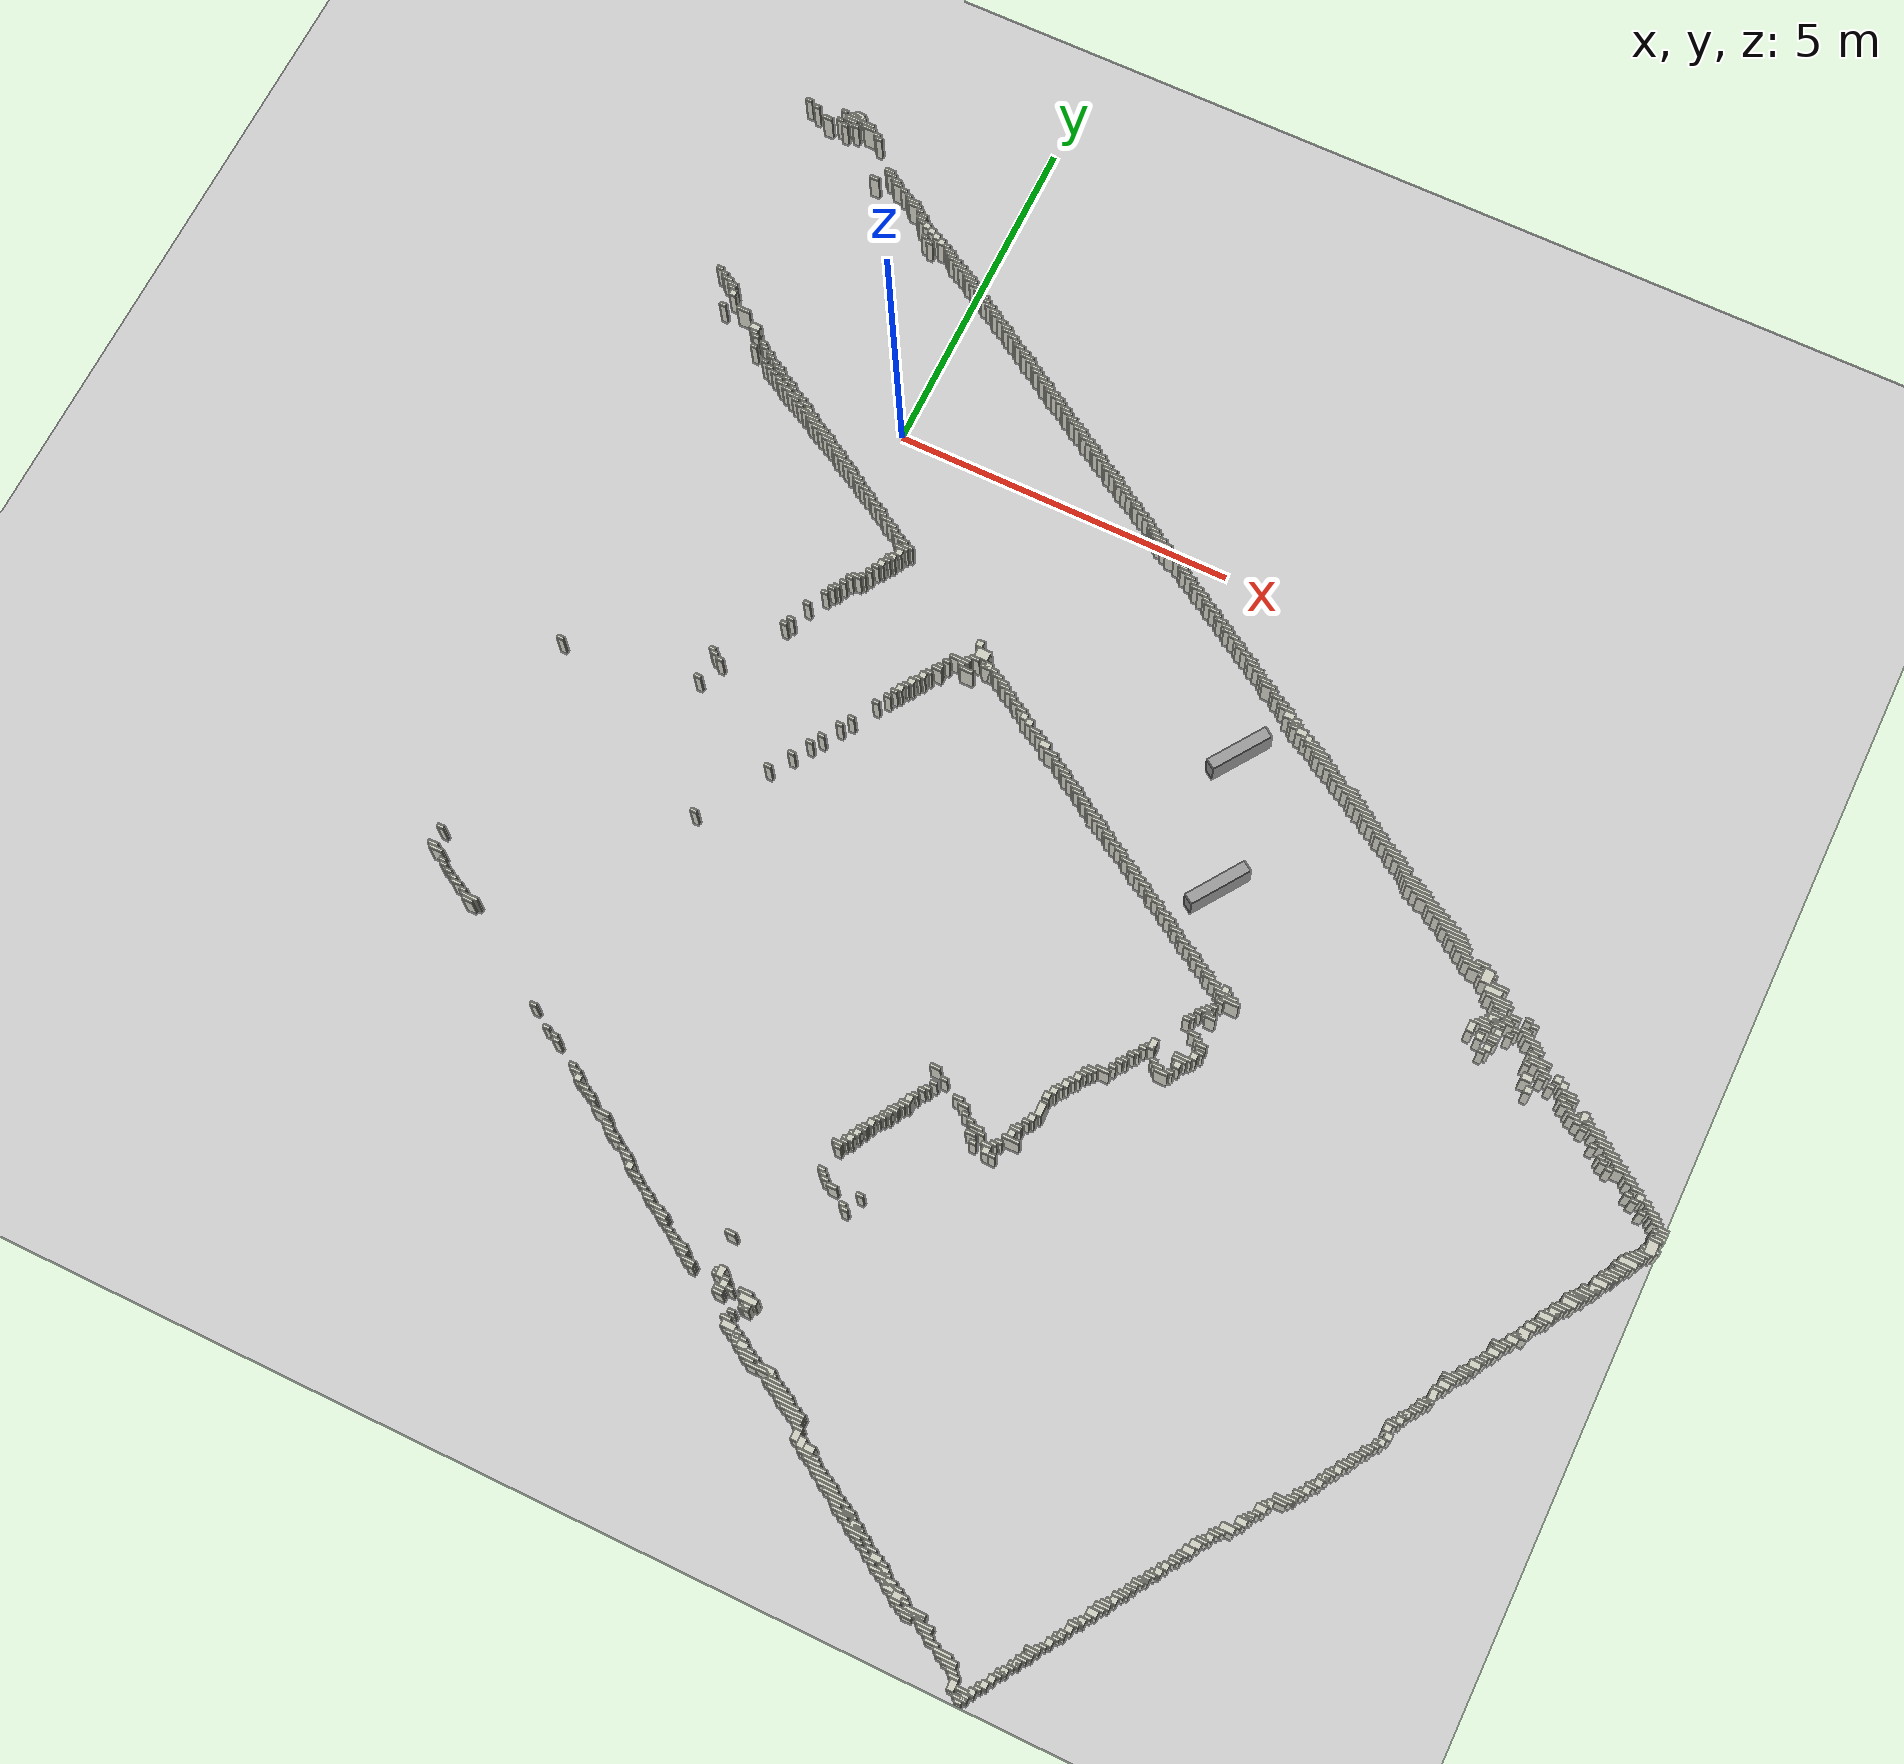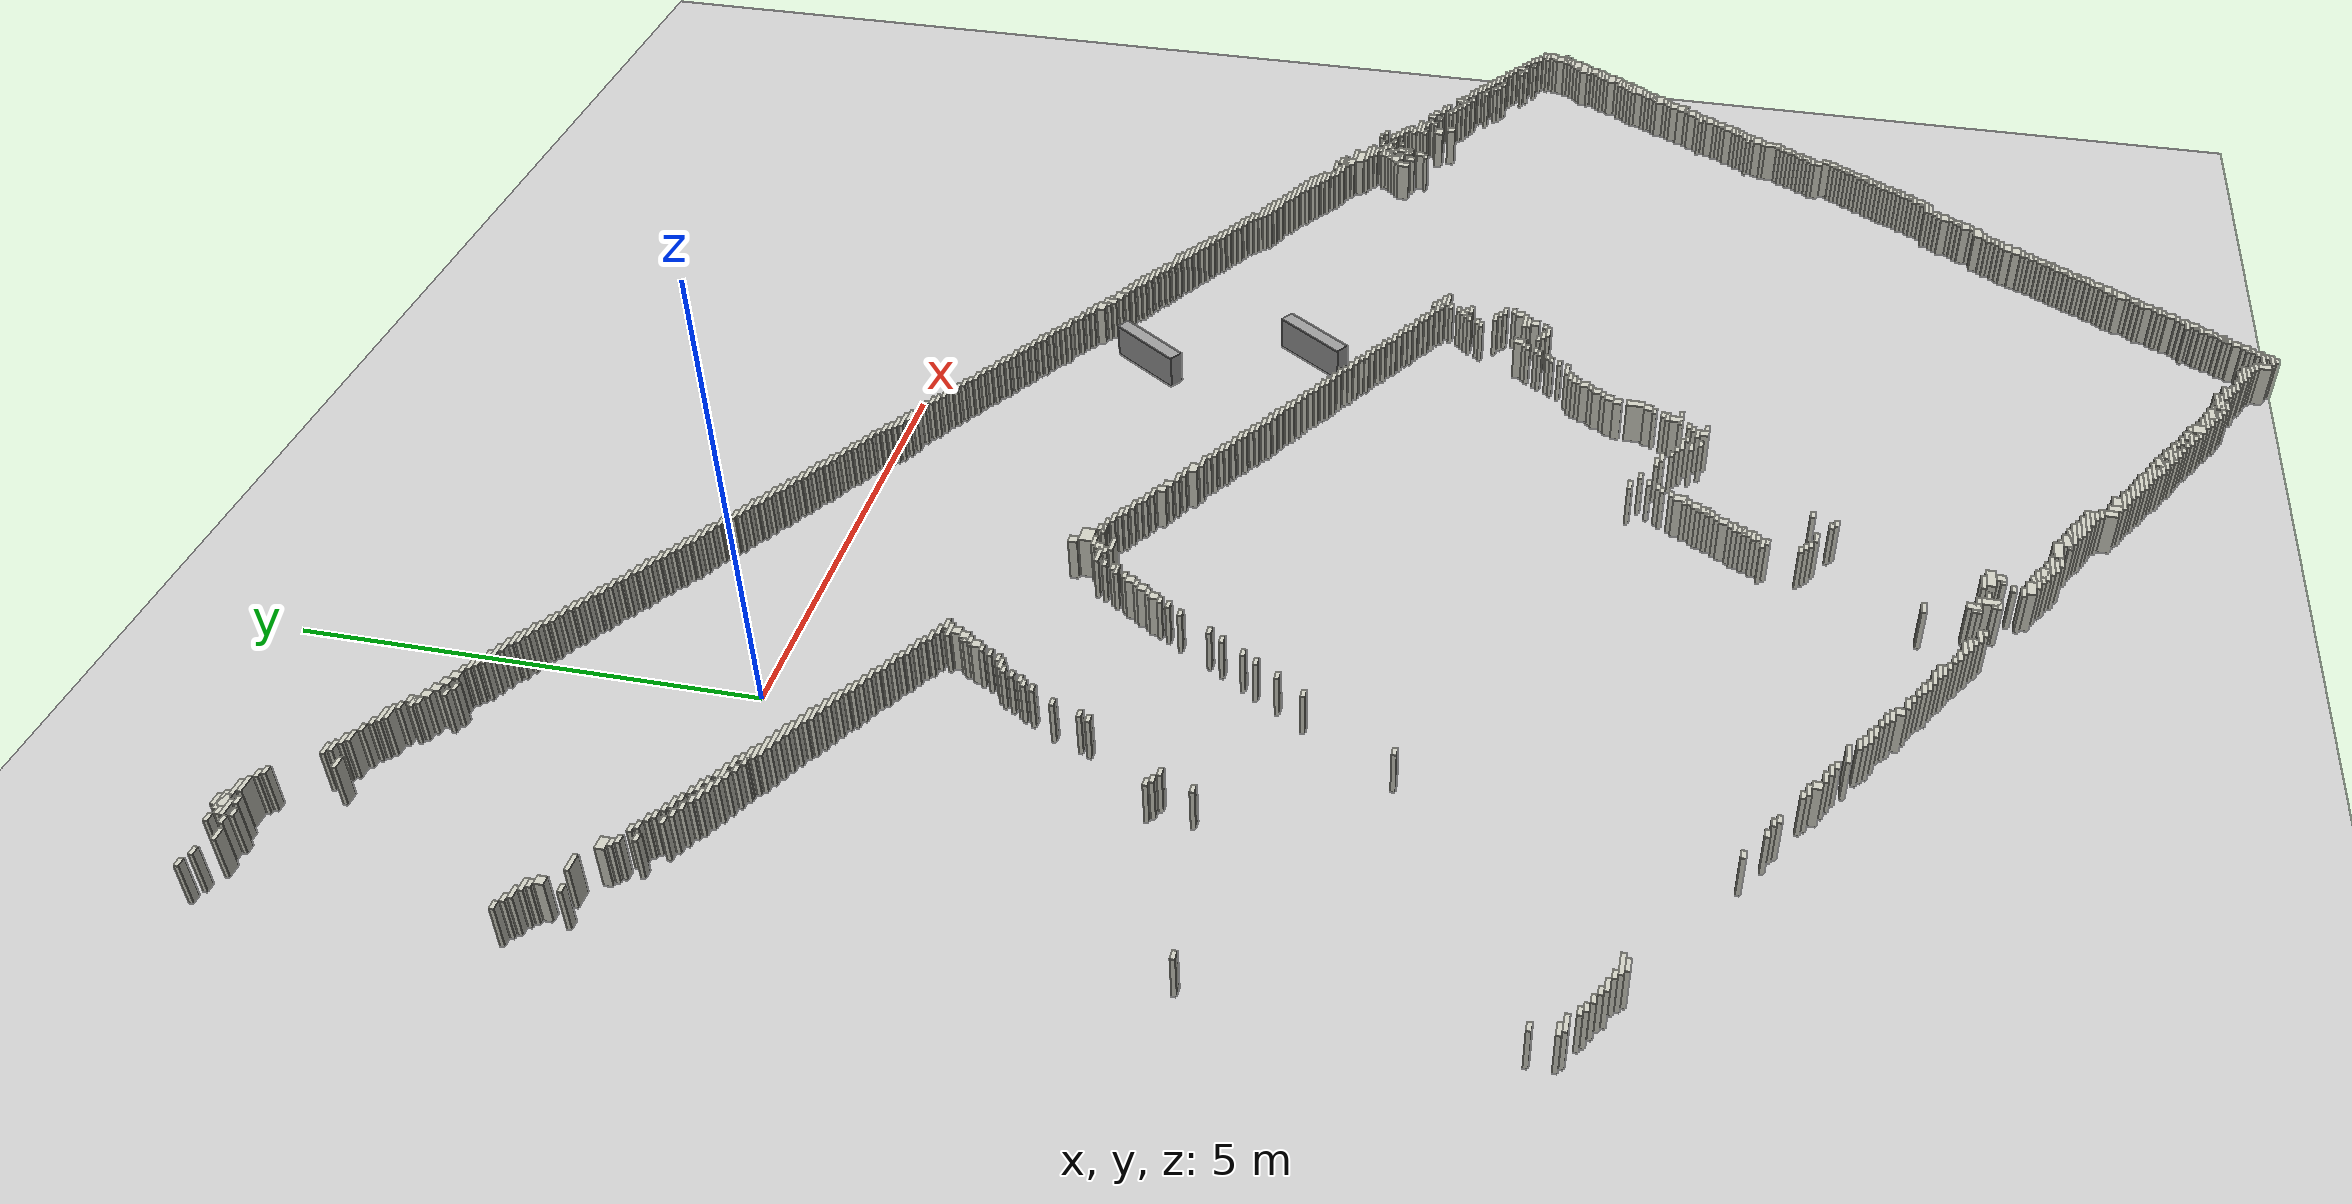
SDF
<sdf version="1.7">
 <world name="my_map_world">
  <gravity>0 0 -9.8</gravity>
  <light name="light1" type="point">
   <pose>0 0 5 0 -0 0</pose>
   <diffuse>255 255 255 255</diffuse>
   <specular>255 255 255 255</specular>
   <attenuation>
    <range>30</range>
    <constant>0.5</constant>
    <quadratic>0.01</quadratic>
    <linear>0</linear>
   </attenuation>
   <direction>0 0 -1</direction>
   <spot><inner_angle>0</inner_angle><outer_angle>0</outer_angle><falloff>0</falloff></spot>
  </light>
  <light name="light2" type="point">
   <pose>-10 -10 5 0 -0 0</pose>
   <diffuse>255 255 255 255</diffuse>
   <specular>255 255 255 255</specular>
   <attenuation>
    <range>30</range>
    <constant>0.5</constant>
    <quadratic>0.01</quadratic>
    <linear>0</linear>
   </attenuation>
   <direction>0 0 -1</direction>
   <spot><inner_angle>0</inner_angle><outer_angle>0</outer_angle><falloff>0</falloff></spot>
  </light>
  <light name="light3" type="point">
   <pose>10 10 5 0 -0 0</pose>
   <diffuse>255 255 255 255</diffuse>
   <specular>255 255 255 255</specular>
   <attenuation>
    <range>30</range>
    <constant>0.5</constant>
    <quadratic>0.01</quadratic>
    <linear>0</linear>
   </attenuation>
   <direction>0 0 -1</direction>
   <spot><inner_angle>0</inner_angle><outer_angle>0</outer_angle><falloff>0</falloff></spot>
  </light>
  <model name="my_map_model">
   <static>1</static>
   <link name="link">
    <visual name="visual">
     <geometry><plane><normal>0 0 1</normal><size>27.15 22.15</size></plane></geometry>
     <material>
      <script>
       <uri>model://my_map_model/materials/scripts</uri>
       <uri>model://my_map_model/materials/textures</uri>
       <name>MyMapMaterial</name>
      </script>
     </material>
    </visual>
    <collision name="collision">
     <geometry><plane><normal>0 0 1</normal><size>27.15 22.15</size></plane></geometry>
     <surface><friction><ode><mu>100</mu><mu2>50</mu2></ode></friction></surface>
    </collision>
   </link>
   <pose>0.375 -4.225 0 0 -0 0</pose>
  </model>
  <model name="wall_0">
   <static>1</static>
   <pose>-2.725 4.125 0.25 0 -0 0</pose>
   <link name="link">
    <collision name="collision"><geometry><box><size>0.15 0.15 0.5</size></box></geometry></collision>
    <visual name="visual">
     <geometry><box><size>0.15 0.15 0.5</size></box></geometry>
     <material>
      <script><uri>file://media/materials/scripts/gazebo.material</uri><name>Gazebo/PaintedWall</name></script>
     </material>
    </visual>
   </link>
  </model>
  <model name="wall_1">
   <static>1</static>
   <pose>-2.95 4.125 0.25 0 -0 0</pose>
   <link name="link">
    <collision name="collision"><geometry><box><size>0.1 0.05 0.5</size></box></geometry></collision>
    <visual name="visual">
     <geometry><box><size>0.1 0.05 0.5</size></box></geometry>
     <material>
      <script><uri>file://media/materials/scripts/gazebo.material</uri><name>Gazebo/PaintedWall</name></script>
     </material>
    </visual>
   </link>
  </model>
  <model name="wall_2">
   <static>1</static>
   <pose>-2.725 4.125 0.25 0 -0 0</pose>
   <link name="link">
    <collision name="collision"><geometry><box><size>0.25 0.05 0.5</size></box></geometry></collision>
    <visual name="visual">
     <geometry><box><size>0.25 0.05 0.5</size></box></geometry>
     <material>
      <script><uri>file://media/materials/scripts/gazebo.material</uri><name>Gazebo/PaintedWall</name></script>
     </material>
    </visual>
   </link>
  </model>
  <model name="wall_3">
   <static>1</static>
   <pose>-3.5 4.075 0.25 0 -0 0</pose>
   <link name="link">
    <collision name="collision"><geometry><box><size>0.1 0.05 0.5</size></box></geometry></collision>
    <visual name="visual">
     <geometry><box><size>0.1 0.05 0.5</size></box></geometry>
     <material>
      <script><uri>file://media/materials/scripts/gazebo.material</uri><name>Gazebo/PaintedWall</name></script>
     </material>
    </visual>
   </link>
  </model>
  <model name="wall_4">
   <static>1</static>
   <pose>-2.675 4.075 0.25 0 -0 0</pose>
   <link name="link">
    <collision name="collision"><geometry><box><size>0.45 0.05 0.5</size></box></geometry></collision>
    <visual name="visual">
     <geometry><box><size>0.45 0.05 0.5</size></box></geometry>
     <material>
      <script><uri>file://media/materials/scripts/gazebo.material</uri><name>Gazebo/PaintedWall</name></script>
     </material>
    </visual>
   </link>
  </model>
  <model name="wall_5">
   <static>1</static>
   <pose>-3.35 4.025 0.25 0 -0 0</pose>
   <link name="link">
    <collision name="collision"><geometry><box><size>0.1 0.05 0.5</size></box></geometry></collision>
    <visual name="visual">
     <geometry><box><size>0.1 0.05 0.5</size></box></geometry>
     <material>
      <script><uri>file://media/materials/scripts/gazebo.material</uri><name>Gazebo/PaintedWall</name></script>
     </material>
    </visual>
   </link>
  </model>
  <model name="wall_6">
   <static>1</static>
   <pose>-2.8 4.025 0.25 0 -0 0</pose>
   <link name="link">
    <collision name="collision"><geometry><box><size>0.2 0.05 0.5</size></box></geometry></collision>
    <visual name="visual">
     <geometry><box><size>0.2 0.05 0.5</size></box></geometry>
     <material>
      <script><uri>file://media/materials/scripts/gazebo.material</uri><name>Gazebo/PaintedWall</name></script>
     </material>
    </visual>
   </link>
  </model>
  <model name="wall_7">
   <static>1</static>
   <pose>-2.5 4.025 0.25 0 -0 0</pose>
   <link name="link">
    <collision name="collision"><geometry><box><size>0.2 0.05 0.5</size></box></geometry></collision>
    <visual name="visual">
     <geometry><box><size>0.2 0.05 0.5</size></box></geometry>
     <material>
      <script><uri>file://media/materials/scripts/gazebo.material</uri><name>Gazebo/PaintedWall</name></script>
     </material>
    </visual>
   </link>
  </model>
  <model name="wall_8">
   <static>1</static>
   <pose>-2.95 3.975 0.25 0 -0 0</pose>
   <link name="link">
    <collision name="collision"><geometry><box><size>0.1 0.05 0.5</size></box></geometry></collision>
    <visual name="visual">
     <geometry><box><size>0.1 0.05 0.5</size></box></geometry>
     <material>
      <script><uri>file://media/materials/scripts/gazebo.material</uri><name>Gazebo/PaintedWall</name></script>
     </material>
    </visual>
   </link>
  </model>
  <model name="wall_9">
   <static>1</static>
   <pose>-2.7 3.975 0.25 0 -0 0</pose>
   <link name="link">
    <collision name="collision"><geometry><box><size>0.1 0.05 0.5</size></box></geometry></collision>
    <visual name="visual">
     <geometry><box><size>0.1 0.05 0.5</size></box></geometry>
     <material>
      <script><uri>file://media/materials/scripts/gazebo.material</uri><name>Gazebo/PaintedWall</name></script>
     </material>
    </visual>
   </link>
  </model>
  <model name="wall_10">
   <static>1</static>
   <pose>-2.35 3.975 0.25 0 -0 0</pose>
   <link name="link">
    <collision name="collision"><geometry><box><size>0.1 0.05 0.5</size></box></geometry></collision>
    <visual name="visual">
     <geometry><box><size>0.1 0.05 0.5</size></box></geometry>
     <material>
      <script><uri>file://media/materials/scripts/gazebo.material</uri><name>Gazebo/PaintedWall</name></script>
     </material>
    </visual>
   </link>
  </model>
  <model name="wall_11">
   <static>1</static>
   <pose>-3.125 3.925 0.25 0 -0 0</pose>
   <link name="link">
    <collision name="collision"><geometry><box><size>0.15 0.05 0.5</size></box></geometry></collision>
    <visual name="visual">
     <geometry><box><size>0.15 0.05 0.5</size></box></geometry>
     <material>
      <script><uri>file://media/materials/scripts/gazebo.material</uri><name>Gazebo/PaintedWall</name></script>
     </material>
    </visual>
   </link>
  </model>
  <model name="wall_12">
   <static>1</static>
   <pose>-2.85 3.925 0.25 0 -0 0</pose>
   <link name="link">
    <collision name="collision"><geometry><box><size>0.1 0.05 0.5</size></box></geometry></collision>
    <visual name="visual">
     <geometry><box><size>0.1 0.05 0.5</size></box></geometry>
     <material>
      <script><uri>file://media/materials/scripts/gazebo.material</uri><name>Gazebo/PaintedWall</name></script>
     </material>
    </visual>
   </link>
  </model>
  <model name="wall_13">
   <static>1</static>
   <pose>-2.3 3.925 0.25 0 -0 0</pose>
   <link name="link">
    <collision name="collision"><geometry><box><size>0.1 0.05 0.5</size></box></geometry></collision>
    <visual name="visual">
     <geometry><box><size>0.1 0.05 0.5</size></box></geometry>
     <material>
      <script><uri>file://media/materials/scripts/gazebo.material</uri><name>Gazebo/PaintedWall</name></script>
     </material>
    </visual>
   </link>
  </model>
  <model name="wall_14">
   <static>1</static>
   <pose>-1.925 3.525 0.25 0 -0 0</pose>
   <link name="link">
    <collision name="collision"><geometry><box><size>0.15 0.05 0.5</size></box></geometry></collision>
    <visual name="visual">
     <geometry><box><size>0.15 0.05 0.5</size></box></geometry>
     <material>
      <script><uri>file://media/materials/scripts/gazebo.material</uri><name>Gazebo/PaintedWall</name></script>
     </material>
    </visual>
   </link>
  </model>
  <model name="wall_15">
   <static>1</static>
   <pose>-1.875 3.475 0.25 0 -0 0</pose>
   <link name="link">
    <collision name="collision"><geometry><box><size>0.15 0.05 0.5</size></box></geometry></collision>
    <visual name="visual">
     <geometry><box><size>0.15 0.05 0.5</size></box></geometry>
     <material>
      <script><uri>file://media/materials/scripts/gazebo.material</uri><name>Gazebo/PaintedWall</name></script>
     </material>
    </visual>
   </link>
  </model>
  <model name="wall_16">
   <static>1</static>
   <pose>-1.775 3.425 0.25 0 -0 0</pose>
   <link name="link">
    <collision name="collision"><geometry><box><size>0.15 0.05 0.5</size></box></geometry></collision>
    <visual name="visual">
     <geometry><box><size>0.15 0.05 0.5</size></box></geometry>
     <material>
      <script><uri>file://media/materials/scripts/gazebo.material</uri><name>Gazebo/PaintedWall</name></script>
     </material>
    </visual>
   </link>
  </model>
  <model name="wall_17">
   <static>1</static>
   <pose>-1.725 3.375 0.25 0 -0 0</pose>
   <link name="link">
    <collision name="collision"><geometry><box><size>0.15 0.05 0.5</size></box></geometry></collision>
    <visual name="visual">
     <geometry><box><size>0.15 0.05 0.5</size></box></geometry>
     <material>
      <script><uri>file://media/materials/scripts/gazebo.material</uri><name>Gazebo/PaintedWall</name></script>
     </material>
    </visual>
   </link>
  </model>
  <model name="wall_18">
   <static>1</static>
   <pose>-2.075 3.325 0.25 0 -0 0</pose>
   <link name="link">
    <collision name="collision"><geometry><box><size>0.15 0.05 0.5</size></box></geometry></collision>
    <visual name="visual">
     <geometry><box><size>0.15 0.05 0.5</size></box></geometry>
     <material>
      <script><uri>file://media/materials/scripts/gazebo.material</uri><name>Gazebo/PaintedWall</name></script>
     </material>
    </visual>
   </link>
  </model>
  <model name="wall_19">
   <static>1</static>
   <pose>-1.6 3.325 0.25 0 -0 0</pose>
   <link name="link">
    <collision name="collision"><geometry><box><size>0.1 0.05 0.5</size></box></geometry></collision>
    <visual name="visual">
     <geometry><box><size>0.1 0.05 0.5</size></box></geometry>
     <material>
      <script><uri>file://media/materials/scripts/gazebo.material</uri><name>Gazebo/PaintedWall</name></script>
     </material>
    </visual>
   </link>
  </model>
  <model name="wall_20">
   <static>1</static>
   <pose>-1.5 3.275 0.25 0 -0 0</pose>
   <link name="link">
    <collision name="collision"><geometry><box><size>0.1 0.05 0.5</size></box></geometry></collision>
    <visual name="visual">
     <geometry><box><size>0.1 0.05 0.5</size></box></geometry>
     <material>
      <script><uri>file://media/materials/scripts/gazebo.material</uri><name>Gazebo/PaintedWall</name></script>
     </material>
    </visual>
   </link>
  </model>
  <model name="wall_21">
   <static>1</static>
   <pose>-1.4 3.225 0.25 0 -0 0</pose>
   <link name="link">
    <collision name="collision"><geometry><box><size>0.2 0.05 0.5</size></box></geometry></collision>
    <visual name="visual">
     <geometry><box><size>0.2 0.05 0.5</size></box></geometry>
     <material>
      <script><uri>file://media/materials/scripts/gazebo.material</uri><name>Gazebo/PaintedWall</name></script>
     </material>
    </visual>
   </link>
  </model>
  <model name="wall_22">
   <static>1</static>
   <pose>-1.35 3.175 0.25 0 -0 0</pose>
   <link name="link">
    <collision name="collision"><geometry><box><size>0.2 0.05 0.5</size></box></geometry></collision>
    <visual name="visual">
     <geometry><box><size>0.2 0.05 0.5</size></box></geometry>
     <material>
      <script><uri>file://media/materials/scripts/gazebo.material</uri><name>Gazebo/PaintedWall</name></script>
     </material>
    </visual>
   </link>
  </model>
  <model name="wall_23">
   <static>1</static>
   <pose>-1.25 3.125 0.25 0 -0 0</pose>
   <link name="link">
    <collision name="collision"><geometry><box><size>0.1 0.05 0.5</size></box></geometry></collision>
    <visual name="visual">
     <geometry><box><size>0.1 0.05 0.5</size></box></geometry>
     <material>
      <script><uri>file://media/materials/scripts/gazebo.material</uri><name>Gazebo/PaintedWall</name></script>
     </material>
    </visual>
   </link>
  </model>
  <model name="wall_24">
   <static>1</static>
   <pose>-1.15 3.025 0.25 0 -0 0</pose>
   <link name="link">
    <collision name="collision"><geometry><box><size>0.1 0.15 0.5</size></box></geometry></collision>
    <visual name="visual">
     <geometry><box><size>0.1 0.15 0.5</size></box></geometry>
     <material>
      <script><uri>file://media/materials/scripts/gazebo.material</uri><name>Gazebo/PaintedWall</name></script>
     </material>
    </visual>
   </link>
  </model>
  <model name="wall_25">
   <static>1</static>
   <pose>-1.175 3.025 0.25 0 -0 0</pose>
   <link name="link">
    <collision name="collision"><geometry><box><size>0.15 0.05 0.5</size></box></geometry></collision>
    <visual name="visual">
     <geometry><box><size>0.15 0.05 0.5</size></box></geometry>
     <material>
      <script><uri>file://media/materials/scripts/gazebo.material</uri><name>Gazebo/PaintedWall</name></script>
     </material>
    </visual>
   </link>
  </model>
  <model name="wall_26">
   <static>1</static>
   <pose>-1.05 2.95 0.25 0 -0 0</pose>
   <link name="link">
    <collision name="collision"><geometry><box><size>0.1 0.1 0.5</size></box></geometry></collision>
    <visual name="visual">
     <geometry><box><size>0.1 0.1 0.5</size></box></geometry>
     <material>
      <script><uri>file://media/materials/scripts/gazebo.material</uri><name>Gazebo/PaintedWall</name></script>
     </material>
    </visual>
   </link>
  </model>
  <model name="wall_27">
   <static>1</static>
   <pose>-0.95 2.9 0.25 0 -0 0</pose>
   <link name="link">
    <collision name="collision"><geometry><box><size>0.1 0.1 0.5</size></box></geometry></collision>
    <visual name="visual">
     <geometry><box><size>0.1 0.1 0.5</size></box></geometry>
     <material>
      <script><uri>file://media/materials/scripts/gazebo.material</uri><name>Gazebo/PaintedWall</name></script>
     </material>
    </visual>
   </link>
  </model>
  <model name="wall_28">
   <static>1</static>
   <pose>-0.85 2.85 0.25 0 -0 0</pose>
   <link name="link">
    <collision name="collision"><geometry><box><size>0.1 0.1 0.5</size></box></geometry></collision>
    <visual name="visual">
     <geometry><box><size>0.1 0.1 0.5</size></box></geometry>
     <material>
      <script><uri>file://media/materials/scripts/gazebo.material</uri><name>Gazebo/PaintedWall</name></script>
     </material>
    </visual>
   </link>
  </model>
  <model name="wall_29">
   <static>1</static>
   <pose>-0.75 2.8 0.25 0 -0 0</pose>
   <link name="link">
    <collision name="collision"><geometry><box><size>0.1 0.1 0.5</size></box></geometry></collision>
    <visual name="visual">
     <geometry><box><size>0.1 0.1 0.5</size></box></geometry>
     <material>
      <script><uri>file://media/materials/scripts/gazebo.material</uri><name>Gazebo/PaintedWall</name></script>
     </material>
    </visual>
   </link>
  </model>
  <model name="wall_30">
   <static>1</static>
   <pose>-1 2.775 0.25 0 -0 0</pose>
   <link name="link">
    <collision name="collision"><geometry><box><size>0.1 0.05 0.5</size></box></geometry></collision>
    <visual name="visual">
     <geometry><box><size>0.1 0.05 0.5</size></box></geometry>
     <material>
      <script><uri>file://media/materials/scripts/gazebo.material</uri><name>Gazebo/PaintedWall</name></script>
     </material>
    </visual>
   </link>
  </model>
  <model name="wall_31">
   <static>1</static>
   <pose>-0.65 2.775 0.25 0 -0 0</pose>
   <link name="link">
    <collision name="collision"><geometry><box><size>0.1 0.05 0.5</size></box></geometry></collision>
    <visual name="visual">
     <geometry><box><size>0.1 0.05 0.5</size></box></geometry>
     <material>
      <script><uri>file://media/materials/scripts/gazebo.material</uri><name>Gazebo/PaintedWall</name></script>
     </material>
    </visual>
   </link>
  </model>
  <model name="wall_32">
   <static>1</static>
   <pose>-0.9 2.725 0.25 0 -0 0</pose>
   <link name="link">
    <collision name="collision"><geometry><box><size>0.1 0.05 0.5</size></box></geometry></collision>
    <visual name="visual">
     <geometry><box><size>0.1 0.05 0.5</size></box></geometry>
     <material>
      <script><uri>file://media/materials/scripts/gazebo.material</uri><name>Gazebo/PaintedWall</name></script>
     </material>
    </visual>
   </link>
  </model>
  <model name="wall_33">
   <static>1</static>
   <pose>-0.575 2.725 0.25 0 -0 0</pose>
   <link name="link">
    <collision name="collision"><geometry><box><size>0.15 0.05 0.5</size></box></geometry></collision>
    <visual name="visual">
     <geometry><box><size>0.15 0.05 0.5</size></box></geometry>
     <material>
      <script><uri>file://media/materials/scripts/gazebo.material</uri><name>Gazebo/PaintedWall</name></script>
     </material>
    </visual>
   </link>
  </model>
  <model name="wall_34">
   <static>1</static>
   <pose>-0.525 2.675 0.25 0 -0 0</pose>
   <link name="link">
    <collision name="collision"><geometry><box><size>0.15 0.05 0.5</size></box></geometry></collision>
    <visual name="visual">
     <geometry><box><size>0.15 0.05 0.5</size></box></geometry>
     <material>
      <script><uri>file://media/materials/scripts/gazebo.material</uri><name>Gazebo/PaintedWall</name></script>
     </material>
    </visual>
   </link>
  </model>
  <model name="wall_35">
   <static>1</static>
   <pose>-0.45 2.625 0.25 0 -0 0</pose>
   <link name="link">
    <collision name="collision"><geometry><box><size>0.2 0.05 0.5</size></box></geometry></collision>
    <visual name="visual">
     <geometry><box><size>0.2 0.05 0.5</size></box></geometry>
     <material>
      <script><uri>file://media/materials/scripts/gazebo.material</uri><name>Gazebo/PaintedWall</name></script>
     </material>
    </visual>
   </link>
  </model>
  <model name="wall_36">
   <static>1</static>
   <pose>-0.35 2.575 0.25 0 -0 0</pose>
   <link name="link">
    <collision name="collision"><geometry><box><size>0.2 0.05 0.5</size></box></geometry></collision>
    <visual name="visual">
     <geometry><box><size>0.2 0.05 0.5</size></box></geometry>
     <material>
      <script><uri>file://media/materials/scripts/gazebo.material</uri><name>Gazebo/PaintedWall</name></script>
     </material>
    </visual>
   </link>
  </model>
  <model name="wall_37">
   <static>1</static>
   <pose>-0.25 2.525 0.25 0 -0 0</pose>
   <link name="link">
    <collision name="collision"><geometry><box><size>0.2 0.05 0.5</size></box></geometry></collision>
    <visual name="visual">
     <geometry><box><size>0.2 0.05 0.5</size></box></geometry>
     <material>
      <script><uri>file://media/materials/scripts/gazebo.material</uri><name>Gazebo/PaintedWall</name></script>
     </material>
    </visual>
   </link>
  </model>
  <model name="wall_38">
   <static>1</static>
   <pose>-0.15 2.475 0.25 0 -0 0</pose>
   <link name="link">
    <collision name="collision"><geometry><box><size>0.2 0.05 0.5</size></box></geometry></collision>
    <visual name="visual">
     <geometry><box><size>0.2 0.05 0.5</size></box></geometry>
     <material>
      <script><uri>file://media/materials/scripts/gazebo.material</uri><name>Gazebo/PaintedWall</name></script>
     </material>
    </visual>
   </link>
  </model>
  <model name="wall_39">
   <static>1</static>
   <pose>-0.1 2.425 0.25 0 -0 0</pose>
   <link name="link">
    <collision name="collision"><geometry><box><size>0.2 0.05 0.5</size></box></geometry></collision>
    <visual name="visual">
     <geometry><box><size>0.2 0.05 0.5</size></box></geometry>
     <material>
      <script><uri>file://media/materials/scripts/gazebo.material</uri><name>Gazebo/PaintedWall</name></script>
     </material>
    </visual>
   </link>
  </model>
  <model name="wall_40">
   <static>1</static>
   <pose>0 2.375 0.25 0 -0 0</pose>
   <link name="link">
    <collision name="collision"><geometry><box><size>0.2 0.05 0.5</size></box></geometry></collision>
    <visual name="visual">
     <geometry><box><size>0.2 0.05 0.5</size></box></geometry>
     <material>
      <script><uri>file://media/materials/scripts/gazebo.material</uri><name>Gazebo/PaintedWall</name></script>
     </material>
    </visual>
   </link>
  </model>
  <model name="wall_41">
   <static>1</static>
   <pose>0.075 2.325 0.25 0 -0 0</pose>
   <link name="link">
    <collision name="collision"><geometry><box><size>0.15 0.05 0.5</size></box></geometry></collision>
    <visual name="visual">
     <geometry><box><size>0.15 0.05 0.5</size></box></geometry>
     <material>
      <script><uri>file://media/materials/scripts/gazebo.material</uri><name>Gazebo/PaintedWall</name></script>
     </material>
    </visual>
   </link>
  </model>
  <model name="wall_42">
   <static>1</static>
   <pose>0.175 2.275 0.25 0 -0 0</pose>
   <link name="link">
    <collision name="collision"><geometry><box><size>0.15 0.05 0.5</size></box></geometry></collision>
    <visual name="visual">
     <geometry><box><size>0.15 0.05 0.5</size></box></geometry>
     <material>
      <script><uri>file://media/materials/scripts/gazebo.material</uri><name>Gazebo/PaintedWall</name></script>
     </material>
    </visual>
   </link>
  </model>
  <model name="wall_43">
   <static>1</static>
   <pose>0.225 2.225 0.25 0 -0 0</pose>
   <link name="link">
    <collision name="collision"><geometry><box><size>0.15 0.05 0.5</size></box></geometry></collision>
    <visual name="visual">
     <geometry><box><size>0.15 0.05 0.5</size></box></geometry>
     <material>
      <script><uri>file://media/materials/scripts/gazebo.material</uri><name>Gazebo/PaintedWall</name></script>
     </material>
    </visual>
   </link>
  </model>
  <model name="wall_44">
   <static>1</static>
   <pose>0.325 2.175 0.25 0 -0 0</pose>
   <link name="link">
    <collision name="collision"><geometry><box><size>0.15 0.05 0.5</size></box></geometry></collision>
    <visual name="visual">
     <geometry><box><size>0.15 0.05 0.5</size></box></geometry>
     <material>
      <script><uri>file://media/materials/scripts/gazebo.material</uri><name>Gazebo/PaintedWall</name></script>
     </material>
    </visual>
   </link>
  </model>
  <model name="wall_45">
   <static>1</static>
   <pose>0.425 2.125 0.25 0 -0 0</pose>
   <link name="link">
    <collision name="collision"><geometry><box><size>0.15 0.05 0.5</size></box></geometry></collision>
    <visual name="visual">
     <geometry><box><size>0.15 0.05 0.5</size></box></geometry>
     <material>
      <script><uri>file://media/materials/scripts/gazebo.material</uri><name>Gazebo/PaintedWall</name></script>
     </material>
    </visual>
   </link>
  </model>
  <model name="wall_46">
   <static>1</static>
   <pose>0.475 2.075 0.25 0 -0 0</pose>
   <link name="link">
    <collision name="collision"><geometry><box><size>0.15 0.05 0.5</size></box></geometry></collision>
    <visual name="visual">
     <geometry><box><size>0.15 0.05 0.5</size></box></geometry>
     <material>
      <script><uri>file://media/materials/scripts/gazebo.material</uri><name>Gazebo/PaintedWall</name></script>
     </material>
    </visual>
   </link>
  </model>
  <model name="wall_47">
   <static>1</static>
   <pose>0.575 2.025 0.25 0 -0 0</pose>
   <link name="link">
    <collision name="collision"><geometry><box><size>0.15 0.05 0.5</size></box></geometry></collision>
    <visual name="visual">
     <geometry><box><size>0.15 0.05 0.5</size></box></geometry>
     <material>
      <script><uri>file://media/materials/scripts/gazebo.material</uri><name>Gazebo/PaintedWall</name></script>
     </material>
    </visual>
   </link>
  </model>
  <model name="wall_48">
   <static>1</static>
   <pose>0.675 1.975 0.25 0 -0 0</pose>
   <link name="link">
    <collision name="collision"><geometry><box><size>0.15 0.05 0.5</size></box></geometry></collision>
    <visual name="visual">
     <geometry><box><size>0.15 0.05 0.5</size></box></geometry>
     <material>
      <script><uri>file://media/materials/scripts/gazebo.material</uri><name>Gazebo/PaintedWall</name></script>
     </material>
    </visual>
   </link>
  </model>
  <model name="wall_49">
   <static>1</static>
   <pose>0.725 1.925 0.25 0 -0 0</pose>
   <link name="link">
    <collision name="collision"><geometry><box><size>0.15 0.05 0.5</size></box></geometry></collision>
    <visual name="visual">
     <geometry><box><size>0.15 0.05 0.5</size></box></geometry>
     <material>
      <script><uri>file://media/materials/scripts/gazebo.material</uri><name>Gazebo/PaintedWall</name></script>
     </material>
    </visual>
   </link>
  </model>
  <model name="wall_50">
   <static>1</static>
   <pose>0.825 1.875 0.25 0 -0 0</pose>
   <link name="link">
    <collision name="collision"><geometry><box><size>0.15 0.05 0.5</size></box></geometry></collision>
    <visual name="visual">
     <geometry><box><size>0.15 0.05 0.5</size></box></geometry>
     <material>
      <script><uri>file://media/materials/scripts/gazebo.material</uri><name>Gazebo/PaintedWall</name></script>
     </material>
    </visual>
   </link>
  </model>
  <model name="wall_51">
   <static>1</static>
   <pose>0.9 1.825 0.25 0 -0 0</pose>
   <link name="link">
    <collision name="collision"><geometry><box><size>0.1 0.05 0.5</size></box></geometry></collision>
    <visual name="visual">
     <geometry><box><size>0.1 0.05 0.5</size></box></geometry>
     <material>
      <script><uri>file://media/materials/scripts/gazebo.material</uri><name>Gazebo/PaintedWall</name></script>
     </material>
    </visual>
   </link>
  </model>
  <model name="wall_52">
   <static>1</static>
   <pose>0.975 1.775 0.25 0 -0 0</pose>
   <link name="link">
    <collision name="collision"><geometry><box><size>0.15 0.05 0.5</size></box></geometry></collision>
    <visual name="visual">
     <geometry><box><size>0.15 0.05 0.5</size></box></geometry>
     <material>
      <script><uri>file://media/materials/scripts/gazebo.material</uri><name>Gazebo/PaintedWall</name></script>
     </material>
    </visual>
   </link>
  </model>
  <model name="wall_53">
   <static>1</static>
   <pose>1.075 1.725 0.25 0 -0 0</pose>
   <link name="link">
    <collision name="collision"><geometry><box><size>0.15 0.05 0.5</size></box></geometry></collision>
    <visual name="visual">
     <geometry><box><size>0.15 0.05 0.5</size></box></geometry>
     <material>
      <script><uri>file://media/materials/scripts/gazebo.material</uri><name>Gazebo/PaintedWall</name></script>
     </material>
    </visual>
   </link>
  </model>
  <model name="wall_54">
   <static>1</static>
   <pose>1.15 1.675 0.25 0 -0 0</pose>
   <link name="link">
    <collision name="collision"><geometry><box><size>0.2 0.05 0.5</size></box></geometry></collision>
    <visual name="visual">
     <geometry><box><size>0.2 0.05 0.5</size></box></geometry>
     <material>
      <script><uri>file://media/materials/scripts/gazebo.material</uri><name>Gazebo/PaintedWall</name></script>
     </material>
    </visual>
   </link>
  </model>
  <model name="wall_55">
   <static>1</static>
   <pose>1.225 1.625 0.25 0 -0 0</pose>
   <link name="link">
    <collision name="collision"><geometry><box><size>0.15 0.05 0.5</size></box></geometry></collision>
    <visual name="visual">
     <geometry><box><size>0.15 0.05 0.5</size></box></geometry>
     <material>
      <script><uri>file://media/materials/scripts/gazebo.material</uri><name>Gazebo/PaintedWall</name></script>
     </material>
    </visual>
   </link>
  </model>
  <model name="wall_56">
   <static>1</static>
   <pose>1.325 1.575 0.25 0 -0 0</pose>
   <link name="link">
    <collision name="collision"><geometry><box><size>0.15 0.05 0.5</size></box></geometry></collision>
    <visual name="visual">
     <geometry><box><size>0.15 0.05 0.5</size></box></geometry>
     <material>
      <script><uri>file://media/materials/scripts/gazebo.material</uri><name>Gazebo/PaintedWall</name></script>
     </material>
    </visual>
   </link>
  </model>
  <model name="wall_57">
   <static>1</static>
   <pose>1.375 1.525 0.25 0 -0 0</pose>
   <link name="link">
    <collision name="collision"><geometry><box><size>0.15 0.05 0.5</size></box></geometry></collision>
    <visual name="visual">
     <geometry><box><size>0.15 0.05 0.5</size></box></geometry>
     <material>
      <script><uri>file://media/materials/scripts/gazebo.material</uri><name>Gazebo/PaintedWall</name></script>
     </material>
    </visual>
   </link>
  </model>
  <model name="wall_58">
   <static>1</static>
   <pose>1.475 1.475 0.25 0 -0 0</pose>
   <link name="link">
    <collision name="collision"><geometry><box><size>0.15 0.05 0.5</size></box></geometry></collision>
    <visual name="visual">
     <geometry><box><size>0.15 0.05 0.5</size></box></geometry>
     <material>
      <script><uri>file://media/materials/scripts/gazebo.material</uri><name>Gazebo/PaintedWall</name></script>
     </material>
    </visual>
   </link>
  </model>
  <model name="wall_59">
   <static>1</static>
   <pose>1.55 1.425 0.25 0 -0 0</pose>
   <link name="link">
    <collision name="collision"><geometry><box><size>0.2 0.05 0.5</size></box></geometry></collision>
    <visual name="visual">
     <geometry><box><size>0.2 0.05 0.5</size></box></geometry>
     <material>
      <script><uri>file://media/materials/scripts/gazebo.material</uri><name>Gazebo/PaintedWall</name></script>
     </material>
    </visual>
   </link>
  </model>
  <model name="wall_60">
   <static>1</static>
   <pose>1.625 1.375 0.25 0 -0 0</pose>
   <link name="link">
    <collision name="collision"><geometry><box><size>0.15 0.05 0.5</size></box></geometry></collision>
    <visual name="visual">
     <geometry><box><size>0.15 0.05 0.5</size></box></geometry>
     <material>
      <script><uri>file://media/materials/scripts/gazebo.material</uri><name>Gazebo/PaintedWall</name></script>
     </material>
    </visual>
   </link>
  </model>
  <model name="wall_61">
   <static>1</static>
   <pose>1.7 1.325 0.25 0 -0 0</pose>
   <link name="link">
    <collision name="collision"><geometry><box><size>0.2 0.05 0.5</size></box></geometry></collision>
    <visual name="visual">
     <geometry><box><size>0.2 0.05 0.5</size></box></geometry>
     <material>
      <script><uri>file://media/materials/scripts/gazebo.material</uri><name>Gazebo/PaintedWall</name></script>
     </material>
    </visual>
   </link>
  </model>
  <model name="wall_62">
   <static>1</static>
   <pose>1.8 1.275 0.25 0 -0 0</pose>
   <link name="link">
    <collision name="collision"><geometry><box><size>0.2 0.05 0.5</size></box></geometry></collision>
    <visual name="visual">
     <geometry><box><size>0.2 0.05 0.5</size></box></geometry>
     <material>
      <script><uri>file://media/materials/scripts/gazebo.material</uri><name>Gazebo/PaintedWall</name></script>
     </material>
    </visual>
   </link>
  </model>
  <model name="wall_63">
   <static>1</static>
   <pose>1.875 1.225 0.25 0 -0 0</pose>
   <link name="link">
    <collision name="collision"><geometry><box><size>0.15 0.05 0.5</size></box></geometry></collision>
    <visual name="visual">
     <geometry><box><size>0.15 0.05 0.5</size></box></geometry>
     <material>
      <script><uri>file://media/materials/scripts/gazebo.material</uri><name>Gazebo/PaintedWall</name></script>
     </material>
    </visual>
   </link>
  </model>
  <model name="wall_64">
   <static>1</static>
   <pose>1.975 1.175 0.25 0 -0 0</pose>
   <link name="link">
    <collision name="collision"><geometry><box><size>0.15 0.05 0.5</size></box></geometry></collision>
    <visual name="visual">
     <geometry><box><size>0.15 0.05 0.5</size></box></geometry>
     <material>
      <script><uri>file://media/materials/scripts/gazebo.material</uri><name>Gazebo/PaintedWall</name></script>
     </material>
    </visual>
   </link>
  </model>
  <model name="wall_65">
   <static>1</static>
   <pose>2.025 1.125 0.25 0 -0 0</pose>
   <link name="link">
    <collision name="collision"><geometry><box><size>0.15 0.05 0.5</size></box></geometry></collision>
    <visual name="visual">
     <geometry><box><size>0.15 0.05 0.5</size></box></geometry>
     <material>
      <script><uri>file://media/materials/scripts/gazebo.material</uri><name>Gazebo/PaintedWall</name></script>
     </material>
    </visual>
   </link>
  </model>
  <model name="wall_66">
   <static>1</static>
   <pose>-3.4 1.075 0.25 0 -0 0</pose>
   <link name="link">
    <collision name="collision"><geometry><box><size>0.1 0.05 0.5</size></box></geometry></collision>
    <visual name="visual">
     <geometry><box><size>0.1 0.05 0.5</size></box></geometry>
     <material>
      <script><uri>file://media/materials/scripts/gazebo.material</uri><name>Gazebo/PaintedWall</name></script>
     </material>
    </visual>
   </link>
  </model>
  <model name="wall_67">
   <static>1</static>
   <pose>2.125 1.075 0.25 0 -0 0</pose>
   <link name="link">
    <collision name="collision"><geometry><box><size>0.15 0.05 0.5</size></box></geometry></collision>
    <visual name="visual">
     <geometry><box><size>0.15 0.05 0.5</size></box></geometry>
     <material>
      <script><uri>file://media/materials/scripts/gazebo.material</uri><name>Gazebo/PaintedWall</name></script>
     </material>
    </visual>
   </link>
  </model>
  <model name="wall_68">
   <static>1</static>
   <pose>-3.3 1.025 0.25 0 -0 0</pose>
   <link name="link">
    <collision name="collision"><geometry><box><size>0.1 0.05 0.5</size></box></geometry></collision>
    <visual name="visual">
     <geometry><box><size>0.1 0.05 0.5</size></box></geometry>
     <material>
      <script><uri>file://media/materials/scripts/gazebo.material</uri><name>Gazebo/PaintedWall</name></script>
     </material>
    </visual>
   </link>
  </model>
  <model name="wall_69">
   <static>1</static>
   <pose>2.2 1.025 0.25 0 -0 0</pose>
   <link name="link">
    <collision name="collision"><geometry><box><size>0.2 0.05 0.5</size></box></geometry></collision>
    <visual name="visual">
     <geometry><box><size>0.2 0.05 0.5</size></box></geometry>
     <material>
      <script><uri>file://media/materials/scripts/gazebo.material</uri><name>Gazebo/PaintedWall</name></script>
     </material>
    </visual>
   </link>
  </model>
  <model name="wall_70">
   <static>1</static>
   <pose>-3.225 0.975 0.25 0 -0 0</pose>
   <link name="link">
    <collision name="collision"><geometry><box><size>0.15 0.05 0.5</size></box></geometry></collision>
    <visual name="visual">
     <geometry><box><size>0.15 0.05 0.5</size></box></geometry>
     <material>
      <script><uri>file://media/materials/scripts/gazebo.material</uri><name>Gazebo/PaintedWall</name></script>
     </material>
    </visual>
   </link>
  </model>
  <model name="wall_71">
   <static>1</static>
   <pose>2.3 0.975 0.25 0 -0 0</pose>
   <link name="link">
    <collision name="collision"><geometry><box><size>0.2 0.05 0.5</size></box></geometry></collision>
    <visual name="visual">
     <geometry><box><size>0.2 0.05 0.5</size></box></geometry>
     <material>
      <script><uri>file://media/materials/scripts/gazebo.material</uri><name>Gazebo/PaintedWall</name></script>
     </material>
    </visual>
   </link>
  </model>
  <model name="wall_72">
   <static>1</static>
   <pose>-3.125 0.925 0.25 0 -0 0</pose>
   <link name="link">
    <collision name="collision"><geometry><box><size>0.15 0.05 0.5</size></box></geometry></collision>
    <visual name="visual">
     <geometry><box><size>0.15 0.05 0.5</size></box></geometry>
     <material>
      <script><uri>file://media/materials/scripts/gazebo.material</uri><name>Gazebo/PaintedWall</name></script>
     </material>
    </visual>
   </link>
  </model>
  <model name="wall_73">
   <static>1</static>
   <pose>2.375 0.925 0.25 0 -0 0</pose>
   <link name="link">
    <collision name="collision"><geometry><box><size>0.15 0.05 0.5</size></box></geometry></collision>
    <visual name="visual">
     <geometry><box><size>0.15 0.05 0.5</size></box></geometry>
     <material>
      <script><uri>file://media/materials/scripts/gazebo.material</uri><name>Gazebo/PaintedWall</name></script>
     </material>
    </visual>
   </link>
  </model>
  <model name="wall_74">
   <static>1</static>
   <pose>-3.1 0.875 0.25 0 -0 0</pose>
   <link name="link">
    <collision name="collision"><geometry><box><size>0.1 0.05 0.5</size></box></geometry></collision>
    <visual name="visual">
     <geometry><box><size>0.1 0.05 0.5</size></box></geometry>
     <material>
      <script><uri>file://media/materials/scripts/gazebo.material</uri><name>Gazebo/PaintedWall</name></script>
     </material>
    </visual>
   </link>
  </model>
  <model name="wall_75">
   <static>1</static>
   <pose>2.45 0.875 0.25 0 -0 0</pose>
   <link name="link">
    <collision name="collision"><geometry><box><size>0.2 0.05 0.5</size></box></geometry></collision>
    <visual name="visual">
     <geometry><box><size>0.2 0.05 0.5</size></box></geometry>
     <material>
      <script><uri>file://media/materials/scripts/gazebo.material</uri><name>Gazebo/PaintedWall</name></script>
     </material>
    </visual>
   </link>
  </model>
  <model name="wall_76">
   <static>1</static>
   <pose>-3.05 0.8 0.25 0 -0 0</pose>
   <link name="link">
    <collision name="collision"><geometry><box><size>0.1 0.1 0.5</size></box></geometry></collision>
    <visual name="visual">
     <geometry><box><size>0.1 0.1 0.5</size></box></geometry>
     <material>
      <script><uri>file://media/materials/scripts/gazebo.material</uri><name>Gazebo/PaintedWall</name></script>
     </material>
    </visual>
   </link>
  </model>
  <model name="wall_77">
   <static>1</static>
   <pose>2.55 0.825 0.25 0 -0 0</pose>
   <link name="link">
    <collision name="collision"><geometry><box><size>0.2 0.05 0.5</size></box></geometry></collision>
    <visual name="visual">
     <geometry><box><size>0.2 0.05 0.5</size></box></geometry>
     <material>
      <script><uri>file://media/materials/scripts/gazebo.material</uri><name>Gazebo/PaintedWall</name></script>
     </material>
    </visual>
   </link>
  </model>
  <model name="wall_78">
   <static>1</static>
   <pose>2.625 0.775 0.25 0 -0 0</pose>
   <link name="link">
    <collision name="collision"><geometry><box><size>0.15 0.05 0.5</size></box></geometry></collision>
    <visual name="visual">
     <geometry><box><size>0.15 0.05 0.5</size></box></geometry>
     <material>
      <script><uri>file://media/materials/scripts/gazebo.material</uri><name>Gazebo/PaintedWall</name></script>
     </material>
    </visual>
   </link>
  </model>
  <model name="wall_79">
   <static>1</static>
   <pose>2.7 0.725 0.25 0 -0 0</pose>
   <link name="link">
    <collision name="collision"><geometry><box><size>0.2 0.05 0.5</size></box></geometry></collision>
    <visual name="visual">
     <geometry><box><size>0.2 0.05 0.5</size></box></geometry>
     <material>
      <script><uri>file://media/materials/scripts/gazebo.material</uri><name>Gazebo/PaintedWall</name></script>
     </material>
    </visual>
   </link>
  </model>
  <model name="wall_80">
   <static>1</static>
   <pose>2.775 0.675 0.25 0 -0 0</pose>
   <link name="link">
    <collision name="collision"><geometry><box><size>0.15 0.05 0.5</size></box></geometry></collision>
    <visual name="visual">
     <geometry><box><size>0.15 0.05 0.5</size></box></geometry>
     <material>
      <script><uri>file://media/materials/scripts/gazebo.material</uri><name>Gazebo/PaintedWall</name></script>
     </material>
    </visual>
   </link>
  </model>
  <model name="wall_81">
   <static>1</static>
   <pose>-2.8 0.625 0.25 0 -0 0</pose>
   <link name="link">
    <collision name="collision"><geometry><box><size>0.2 0.05 0.5</size></box></geometry></collision>
    <visual name="visual">
     <geometry><box><size>0.2 0.05 0.5</size></box></geometry>
     <material>
      <script><uri>file://media/materials/scripts/gazebo.material</uri><name>Gazebo/PaintedWall</name></script>
     </material>
    </visual>
   </link>
  </model>
  <model name="wall_82">
   <static>1</static>
   <pose>2.875 0.625 0.25 0 -0 0</pose>
   <link name="link">
    <collision name="collision"><geometry><box><size>0.15 0.05 0.5</size></box></geometry></collision>
    <visual name="visual">
     <geometry><box><size>0.15 0.05 0.5</size></box></geometry>
     <material>
      <script><uri>file://media/materials/scripts/gazebo.material</uri><name>Gazebo/PaintedWall</name></script>
     </material>
    </visual>
   </link>
  </model>
  <model name="wall_83">
   <static>1</static>
   <pose>-3.1 0.575 0.25 0 -0 0</pose>
   <link name="link">
    <collision name="collision"><geometry><box><size>0.1 0.05 0.5</size></box></geometry></collision>
    <visual name="visual">
     <geometry><box><size>0.1 0.05 0.5</size></box></geometry>
     <material>
      <script><uri>file://media/materials/scripts/gazebo.material</uri><name>Gazebo/PaintedWall</name></script>
     </material>
    </visual>
   </link>
  </model>
  <model name="wall_84">
   <static>1</static>
   <pose>2.95 0.575 0.25 0 -0 0</pose>
   <link name="link">
    <collision name="collision"><geometry><box><size>0.2 0.05 0.5</size></box></geometry></collision>
    <visual name="visual">
     <geometry><box><size>0.2 0.05 0.5</size></box></geometry>
     <material>
      <script><uri>file://media/materials/scripts/gazebo.material</uri><name>Gazebo/PaintedWall</name></script>
     </material>
    </visual>
   </link>
  </model>
  <model name="wall_85">
   <static>1</static>
   <pose>3.05 0.525 0.25 0 -0 0</pose>
   <link name="link">
    <collision name="collision"><geometry><box><size>0.2 0.05 0.5</size></box></geometry></collision>
    <visual name="visual">
     <geometry><box><size>0.2 0.05 0.5</size></box></geometry>
     <material>
      <script><uri>file://media/materials/scripts/gazebo.material</uri><name>Gazebo/PaintedWall</name></script>
     </material>
    </visual>
   </link>
  </model>
  <model name="wall_86">
   <static>1</static>
   <pose>-2.525 0.45 0.25 0 -0 0</pose>
   <link name="link">
    <collision name="collision"><geometry><box><size>0.15 0.1 0.5</size></box></geometry></collision>
    <visual name="visual">
     <geometry><box><size>0.15 0.1 0.5</size></box></geometry>
     <material>
      <script><uri>file://media/materials/scripts/gazebo.material</uri><name>Gazebo/PaintedWall</name></script>
     </material>
    </visual>
   </link>
  </model>
  <model name="wall_87">
   <static>1</static>
   <pose>3.125 0.475 0.25 0 -0 0</pose>
   <link name="link">
    <collision name="collision"><geometry><box><size>0.15 0.05 0.5</size></box></geometry></collision>
    <visual name="visual">
     <geometry><box><size>0.15 0.05 0.5</size></box></geometry>
     <material>
      <script><uri>file://media/materials/scripts/gazebo.material</uri><name>Gazebo/PaintedWall</name></script>
     </material>
    </visual>
   </link>
  </model>
  <model name="wall_88">
   <static>1</static>
   <pose>3.2 0.425 0.25 0 -0 0</pose>
   <link name="link">
    <collision name="collision"><geometry><box><size>0.2 0.05 0.5</size></box></geometry></collision>
    <visual name="visual">
     <geometry><box><size>0.2 0.05 0.5</size></box></geometry>
     <material>
      <script><uri>file://media/materials/scripts/gazebo.material</uri><name>Gazebo/PaintedWall</name></script>
     </material>
    </visual>
   </link>
  </model>
  <model name="wall_89">
   <static>1</static>
   <pose>-2.5 0.375 0.25 0 -0 0</pose>
   <link name="link">
    <collision name="collision"><geometry><box><size>0.1 0.05 0.5</size></box></geometry></collision>
    <visual name="visual">
     <geometry><box><size>0.1 0.05 0.5</size></box></geometry>
     <material>
      <script><uri>file://media/materials/scripts/gazebo.material</uri><name>Gazebo/PaintedWall</name></script>
     </material>
    </visual>
   </link>
  </model>
  <model name="wall_90">
   <static>1</static>
   <pose>3.275 0.375 0.25 0 -0 0</pose>
   <link name="link">
    <collision name="collision"><geometry><box><size>0.15 0.05 0.5</size></box></geometry></collision>
    <visual name="visual">
     <geometry><box><size>0.15 0.05 0.5</size></box></geometry>
     <material>
      <script><uri>file://media/materials/scripts/gazebo.material</uri><name>Gazebo/PaintedWall</name></script>
     </material>
    </visual>
   </link>
  </model>
  <model name="wall_91">
   <static>1</static>
   <pose>-2.45 0.325 0.25 0 -0 0</pose>
   <link name="link">
    <collision name="collision"><geometry><box><size>0.1 0.05 0.5</size></box></geometry></collision>
    <visual name="visual">
     <geometry><box><size>0.1 0.05 0.5</size></box></geometry>
     <material>
      <script><uri>file://media/materials/scripts/gazebo.material</uri><name>Gazebo/PaintedWall</name></script>
     </material>
    </visual>
   </link>
  </model>
  <model name="wall_92">
   <static>1</static>
   <pose>3.375 0.325 0.25 0 -0 0</pose>
   <link name="link">
    <collision name="collision"><geometry><box><size>0.15 0.05 0.5</size></box></geometry></collision>
    <visual name="visual">
     <geometry><box><size>0.15 0.05 0.5</size></box></geometry>
     <material>
      <script><uri>file://media/materials/scripts/gazebo.material</uri><name>Gazebo/PaintedWall</name></script>
     </material>
    </visual>
   </link>
  </model>
  <model name="wall_93">
   <static>1</static>
   <pose>-2.3 0.275 0.25 0 -0 0</pose>
   <link name="link">
    <collision name="collision"><geometry><box><size>0.1 0.05 0.5</size></box></geometry></collision>
    <visual name="visual">
     <geometry><box><size>0.1 0.05 0.5</size></box></geometry>
     <material>
      <script><uri>file://media/materials/scripts/gazebo.material</uri><name>Gazebo/PaintedWall</name></script>
     </material>
    </visual>
   </link>
  </model>
  <model name="wall_94">
   <static>1</static>
   <pose>3.475 0.275 0.25 0 -0 0</pose>
   <link name="link">
    <collision name="collision"><geometry><box><size>0.15 0.05 0.5</size></box></geometry></collision>
    <visual name="visual">
     <geometry><box><size>0.15 0.05 0.5</size></box></geometry>
     <material>
      <script><uri>file://media/materials/scripts/gazebo.material</uri><name>Gazebo/PaintedWall</name></script>
     </material>
    </visual>
   </link>
  </model>
  <model name="wall_95">
   <static>1</static>
   <pose>-2.25 0.225 0.25 0 -0 0</pose>
   <link name="link">
    <collision name="collision"><geometry><box><size>0.1 0.05 0.5</size></box></geometry></collision>
    <visual name="visual">
     <geometry><box><size>0.1 0.05 0.5</size></box></geometry>
     <material>
      <script><uri>file://media/materials/scripts/gazebo.material</uri><name>Gazebo/PaintedWall</name></script>
     </material>
    </visual>
   </link>
  </model>
  <model name="wall_96">
   <static>1</static>
   <pose>3.525 0.225 0.25 0 -0 0</pose>
   <link name="link">
    <collision name="collision"><geometry><box><size>0.15 0.05 0.5</size></box></geometry></collision>
    <visual name="visual">
     <geometry><box><size>0.15 0.05 0.5</size></box></geometry>
     <material>
      <script><uri>file://media/materials/scripts/gazebo.material</uri><name>Gazebo/PaintedWall</name></script>
     </material>
    </visual>
   </link>
  </model>
  <model name="wall_97">
   <static>1</static>
   <pose>-2.4 0.175 0.25 0 -0 0</pose>
   <link name="link">
    <collision name="collision"><geometry><box><size>0.1 0.05 0.5</size></box></geometry></collision>
    <visual name="visual">
     <geometry><box><size>0.1 0.05 0.5</size></box></geometry>
     <material>
      <script><uri>file://media/materials/scripts/gazebo.material</uri><name>Gazebo/PaintedWall</name></script>
     </material>
    </visual>
   </link>
  </model>
  <model name="wall_98">
   <static>1</static>
   <pose>-2.15 0.175 0.25 0 -0 0</pose>
   <link name="link">
    <collision name="collision"><geometry><box><size>0.1 0.05 0.5</size></box></geometry></collision>
    <visual name="visual">
     <geometry><box><size>0.1 0.05 0.5</size></box></geometry>
     <material>
      <script><uri>file://media/materials/scripts/gazebo.material</uri><name>Gazebo/PaintedWall</name></script>
     </material>
    </visual>
   </link>
  </model>
  <model name="wall_99">
   <static>1</static>
   <pose>3.625 0.175 0.25 0 -0 0</pose>
   <link name="link">
    <collision name="collision"><geometry><box><size>0.15 0.05 0.5</size></box></geometry></collision>
    <visual name="visual">
     <geometry><box><size>0.15 0.05 0.5</size></box></geometry>
     <material>
      <script><uri>file://media/materials/scripts/gazebo.material</uri><name>Gazebo/PaintedWall</name></script>
     </material>
    </visual>
   </link>
  </model>
  <model name="wall_100">
   <static>1</static>
   <pose>-2.1 0.125 0.25 0 -0 0</pose>
   <link name="link">
    <collision name="collision"><geometry><box><size>0.1 0.05 0.5</size></box></geometry></collision>
    <visual name="visual">
     <geometry><box><size>0.1 0.05 0.5</size></box></geometry>
     <material>
      <script><uri>file://media/materials/scripts/gazebo.material</uri><name>Gazebo/PaintedWall</name></script>
     </material>
    </visual>
   </link>
  </model>
  <model name="wall_101">
   <static>1</static>
   <pose>3.725 0.125 0.25 0 -0 0</pose>
   <link name="link">
    <collision name="collision"><geometry><box><size>0.15 0.05 0.5</size></box></geometry></collision>
    <visual name="visual">
     <geometry><box><size>0.15 0.05 0.5</size></box></geometry>
     <material>
      <script><uri>file://media/materials/scripts/gazebo.material</uri><name>Gazebo/PaintedWall</name></script>
     </material>
    </visual>
   </link>
  </model>
  <model name="wall_102">
   <static>1</static>
   <pose>-2 0.075 0.25 0 -0 0</pose>
   <link name="link">
    <collision name="collision"><geometry><box><size>0.1 0.05 0.5</size></box></geometry></collision>
    <visual name="visual">
     <geometry><box><size>0.1 0.05 0.5</size></box></geometry>
     <material>
      <script><uri>file://media/materials/scripts/gazebo.material</uri><name>Gazebo/PaintedWall</name></script>
     </material>
    </visual>
   </link>
  </model>
  <model name="wall_103">
   <static>1</static>
   <pose>3.8 0.075 0.25 0 -0 0</pose>
   <link name="link">
    <collision name="collision"><geometry><box><size>0.1 0.05 0.5</size></box></geometry></collision>
    <visual name="visual">
     <geometry><box><size>0.1 0.05 0.5</size></box></geometry>
     <material>
      <script><uri>file://media/materials/scripts/gazebo.material</uri><name>Gazebo/PaintedWall</name></script>
     </material>
    </visual>
   </link>
  </model>
  <model name="wall_104">
   <static>1</static>
   <pose>-2.15 0.025 0.25 0 -0 0</pose>
   <link name="link">
    <collision name="collision"><geometry><box><size>0.1 0.05 0.5</size></box></geometry></collision>
    <visual name="visual">
     <geometry><box><size>0.1 0.05 0.5</size></box></geometry>
     <material>
      <script><uri>file://media/materials/scripts/gazebo.material</uri><name>Gazebo/PaintedWall</name></script>
     </material>
    </visual>
   </link>
  </model>
  <model name="wall_105">
   <static>1</static>
   <pose>-1.925 0.025 0.25 0 -0 0</pose>
   <link name="link">
    <collision name="collision"><geometry><box><size>0.15 0.05 0.5</size></box></geometry></collision>
    <visual name="visual">
     <geometry><box><size>0.15 0.05 0.5</size></box></geometry>
     <material>
      <script><uri>file://media/materials/scripts/gazebo.material</uri><name>Gazebo/PaintedWall</name></script>
     </material>
    </visual>
   </link>
  </model>
  <model name="wall_106">
   <static>1</static>
   <pose>3.875 0.025 0.25 0 -0 0</pose>
   <link name="link">
    <collision name="collision"><geometry><box><size>0.15 0.05 0.5</size></box></geometry></collision>
    <visual name="visual">
     <geometry><box><size>0.15 0.05 0.5</size></box></geometry>
     <material>
      <script><uri>file://media/materials/scripts/gazebo.material</uri><name>Gazebo/PaintedWall</name></script>
     </material>
    </visual>
   </link>
  </model>
  <model name="wall_107">
   <static>1</static>
   <pose>-2.05 -0.025 0.25 0 -0 0</pose>
   <link name="link">
    <collision name="collision"><geometry><box><size>0.1 0.05 0.5</size></box></geometry></collision>
    <visual name="visual">
     <geometry><box><size>0.1 0.05 0.5</size></box></geometry>
     <material>
      <script><uri>file://media/materials/scripts/gazebo.material</uri><name>Gazebo/PaintedWall</name></script>
     </material>
    </visual>
   </link>
  </model>
  <model name="wall_108">
   <static>1</static>
   <pose>-1.85 -0.025 0.25 0 -0 0</pose>
   <link name="link">
    <collision name="collision"><geometry><box><size>0.1 0.05 0.5</size></box></geometry></collision>
    <visual name="visual">
     <geometry><box><size>0.1 0.05 0.5</size></box></geometry>
     <material>
      <script><uri>file://media/materials/scripts/gazebo.material</uri><name>Gazebo/PaintedWall</name></script>
     </material>
    </visual>
   </link>
  </model>
  <model name="wall_109">
   <static>1</static>
   <pose>3.925 -0.025 0.25 0 -0 0</pose>
   <link name="link">
    <collision name="collision"><geometry><box><size>0.15 0.05 0.5</size></box></geometry></collision>
    <visual name="visual">
     <geometry><box><size>0.15 0.05 0.5</size></box></geometry>
     <material>
      <script><uri>file://media/materials/scripts/gazebo.material</uri><name>Gazebo/PaintedWall</name></script>
     </material>
    </visual>
   </link>
  </model>
  <model name="wall_110">
   <static>1</static>
   <pose>-1.95 -0.075 0.25 0 -0 0</pose>
   <link name="link">
    <collision name="collision"><geometry><box><size>0.1 0.05 0.5</size></box></geometry></collision>
    <visual name="visual">
     <geometry><box><size>0.1 0.05 0.5</size></box></geometry>
     <material>
      <script><uri>file://media/materials/scripts/gazebo.material</uri><name>Gazebo/PaintedWall</name></script>
     </material>
    </visual>
   </link>
  </model>
  <model name="wall_111">
   <static>1</static>
   <pose>-1.75 -0.075 0.25 0 -0 0</pose>
   <link name="link">
    <collision name="collision"><geometry><box><size>0.1 0.05 0.5</size></box></geometry></collision>
    <visual name="visual">
     <geometry><box><size>0.1 0.05 0.5</size></box></geometry>
     <material>
      <script><uri>file://media/materials/scripts/gazebo.material</uri><name>Gazebo/PaintedWall</name></script>
     </material>
    </visual>
   </link>
  </model>
  <model name="wall_112">
   <static>1</static>
   <pose>4 -0.075 0.25 0 -0 0</pose>
   <link name="link">
    <collision name="collision"><geometry><box><size>0.2 0.05 0.5</size></box></geometry></collision>
    <visual name="visual">
     <geometry><box><size>0.2 0.05 0.5</size></box></geometry>
     <material>
      <script><uri>file://media/materials/scripts/gazebo.material</uri><name>Gazebo/PaintedWall</name></script>
     </material>
    </visual>
   </link>
  </model>
  <model name="wall_113">
   <static>1</static>
   <pose>-1.85 -0.125 0.25 0 -0 0</pose>
   <link name="link">
    <collision name="collision"><geometry><box><size>0.1 0.05 0.5</size></box></geometry></collision>
    <visual name="visual">
     <geometry><box><size>0.1 0.05 0.5</size></box></geometry>
     <material>
      <script><uri>file://media/materials/scripts/gazebo.material</uri><name>Gazebo/PaintedWall</name></script>
     </material>
    </visual>
   </link>
  </model>
  <model name="wall_114">
   <static>1</static>
   <pose>-1.675 -0.125 0.25 0 -0 0</pose>
   <link name="link">
    <collision name="collision"><geometry><box><size>0.15 0.05 0.5</size></box></geometry></collision>
    <visual name="visual">
     <geometry><box><size>0.15 0.05 0.5</size></box></geometry>
     <material>
      <script><uri>file://media/materials/scripts/gazebo.material</uri><name>Gazebo/PaintedWall</name></script>
     </material>
    </visual>
   </link>
  </model>
  <model name="wall_115">
   <static>1</static>
   <pose>4.075 -0.125 0.25 0 -0 0</pose>
   <link name="link">
    <collision name="collision"><geometry><box><size>0.25 0.05 0.5</size></box></geometry></collision>
    <visual name="visual">
     <geometry><box><size>0.25 0.05 0.5</size></box></geometry>
     <material>
      <script><uri>file://media/materials/scripts/gazebo.material</uri><name>Gazebo/PaintedWall</name></script>
     </material>
    </visual>
   </link>
  </model>
  <model name="wall_116">
   <static>1</static>
   <pose>-1.775 -0.175 0.25 0 -0 0</pose>
   <link name="link">
    <collision name="collision"><geometry><box><size>0.15 0.05 0.5</size></box></geometry></collision>
    <visual name="visual">
     <geometry><box><size>0.15 0.05 0.5</size></box></geometry>
     <material>
      <script><uri>file://media/materials/scripts/gazebo.material</uri><name>Gazebo/PaintedWall</name></script>
     </material>
    </visual>
   </link>
  </model>
  <model name="wall_117">
   <static>1</static>
   <pose>-1.6 -0.175 0.25 0 -0 0</pose>
   <link name="link">
    <collision name="collision"><geometry><box><size>0.1 0.05 0.5</size></box></geometry></collision>
    <visual name="visual">
     <geometry><box><size>0.1 0.05 0.5</size></box></geometry>
     <material>
      <script><uri>file://media/materials/scripts/gazebo.material</uri><name>Gazebo/PaintedWall</name></script>
     </material>
    </visual>
   </link>
  </model>
  <model name="wall_118">
   <static>1</static>
   <pose>4.15 -0.175 0.25 0 -0 0</pose>
   <link name="link">
    <collision name="collision"><geometry><box><size>0.2 0.05 0.5</size></box></geometry></collision>
    <visual name="visual">
     <geometry><box><size>0.2 0.05 0.5</size></box></geometry>
     <material>
      <script><uri>file://media/materials/scripts/gazebo.material</uri><name>Gazebo/PaintedWall</name></script>
     </material>
    </visual>
   </link>
  </model>
  <model name="wall_119">
   <static>1</static>
   <pose>-1.675 -0.225 0.25 0 -0 0</pose>
   <link name="link">
    <collision name="collision"><geometry><box><size>0.15 0.05 0.5</size></box></geometry></collision>
    <visual name="visual">
     <geometry><box><size>0.15 0.05 0.5</size></box></geometry>
     <material>
      <script><uri>file://media/materials/scripts/gazebo.material</uri><name>Gazebo/PaintedWall</name></script>
     </material>
    </visual>
   </link>
  </model>
  <model name="wall_120">
   <static>1</static>
   <pose>-1.5 -0.275 0.25 0 -0 0</pose>
   <link name="link">
    <collision name="collision"><geometry><box><size>0.1 0.15 0.5</size></box></geometry></collision>
    <visual name="visual">
     <geometry><box><size>0.1 0.15 0.5</size></box></geometry>
     <material>
      <script><uri>file://media/materials/scripts/gazebo.material</uri><name>Gazebo/PaintedWall</name></script>
     </material>
    </visual>
   </link>
  </model>
  <model name="wall_121">
   <static>1</static>
   <pose>4.25 -0.225 0.25 0 -0 0</pose>
   <link name="link">
    <collision name="collision"><geometry><box><size>0.2 0.05 0.5</size></box></geometry></collision>
    <visual name="visual">
     <geometry><box><size>0.2 0.05 0.5</size></box></geometry>
     <material>
      <script><uri>file://media/materials/scripts/gazebo.material</uri><name>Gazebo/PaintedWall</name></script>
     </material>
    </visual>
   </link>
  </model>
  <model name="wall_122">
   <static>1</static>
   <pose>-1.5 -0.275 0.25 0 -0 0</pose>
   <link name="link">
    <collision name="collision"><geometry><box><size>0.3 0.05 0.5</size></box></geometry></collision>
    <visual name="visual">
     <geometry><box><size>0.3 0.05 0.5</size></box></geometry>
     <material>
      <script><uri>file://media/materials/scripts/gazebo.material</uri><name>Gazebo/PaintedWall</name></script>
     </material>
    </visual>
   </link>
  </model>
  <model name="wall_123">
   <static>1</static>
   <pose>4.375 -0.275 0.25 0 -0 0</pose>
   <link name="link">
    <collision name="collision"><geometry><box><size>0.15 0.05 0.5</size></box></geometry></collision>
    <visual name="visual">
     <geometry><box><size>0.15 0.05 0.5</size></box></geometry>
     <material>
      <script><uri>file://media/materials/scripts/gazebo.material</uri><name>Gazebo/PaintedWall</name></script>
     </material>
    </visual>
   </link>
  </model>
  <model name="wall_124">
   <static>1</static>
   <pose>-1.325 -0.325 0.25 0 -0 0</pose>
   <link name="link">
    <collision name="collision"><geometry><box><size>0.15 0.05 0.5</size></box></geometry></collision>
    <visual name="visual">
     <geometry><box><size>0.15 0.05 0.5</size></box></geometry>
     <material>
      <script><uri>file://media/materials/scripts/gazebo.material</uri><name>Gazebo/PaintedWall</name></script>
     </material>
    </visual>
   </link>
  </model>
  <model name="wall_125">
   <static>1</static>
   <pose>4.475 -0.325 0.25 0 -0 0</pose>
   <link name="link">
    <collision name="collision"><geometry><box><size>0.15 0.05 0.5</size></box></geometry></collision>
    <visual name="visual">
     <geometry><box><size>0.15 0.05 0.5</size></box></geometry>
     <material>
      <script><uri>file://media/materials/scripts/gazebo.material</uri><name>Gazebo/PaintedWall</name></script>
     </material>
    </visual>
   </link>
  </model>
  <model name="wall_126">
   <static>1</static>
   <pose>-1.4 -0.375 0.25 0 -0 0</pose>
   <link name="link">
    <collision name="collision"><geometry><box><size>0.1 0.05 0.5</size></box></geometry></collision>
    <visual name="visual">
     <geometry><box><size>0.1 0.05 0.5</size></box></geometry>
     <material>
      <script><uri>file://media/materials/scripts/gazebo.material</uri><name>Gazebo/PaintedWall</name></script>
     </material>
    </visual>
   </link>
  </model>
  <model name="wall_127">
   <static>1</static>
   <pose>-1.25 -0.4 0.25 0 -0 0</pose>
   <link name="link">
    <collision name="collision"><geometry><box><size>0.1 0.1 0.5</size></box></geometry></collision>
    <visual name="visual">
     <geometry><box><size>0.1 0.1 0.5</size></box></geometry>
     <material>
      <script><uri>file://media/materials/scripts/gazebo.material</uri><name>Gazebo/PaintedWall</name></script>
     </material>
    </visual>
   </link>
  </model>
  <model name="wall_128">
   <static>1</static>
   <pose>4.525 -0.375 0.25 0 -0 0</pose>
   <link name="link">
    <collision name="collision"><geometry><box><size>0.15 0.05 0.5</size></box></geometry></collision>
    <visual name="visual">
     <geometry><box><size>0.15 0.05 0.5</size></box></geometry>
     <material>
      <script><uri>file://media/materials/scripts/gazebo.material</uri><name>Gazebo/PaintedWall</name></script>
     </material>
    </visual>
   </link>
  </model>
  <model name="wall_129">
   <static>1</static>
   <pose>-1.225 -0.425 0.25 0 -0 0</pose>
   <link name="link">
    <collision name="collision"><geometry><box><size>0.25 0.05 0.5</size></box></geometry></collision>
    <visual name="visual">
     <geometry><box><size>0.25 0.05 0.5</size></box></geometry>
     <material>
      <script><uri>file://media/materials/scripts/gazebo.material</uri><name>Gazebo/PaintedWall</name></script>
     </material>
    </visual>
   </link>
  </model>
  <model name="wall_130">
   <static>1</static>
   <pose>4.625 -0.425 0.25 0 -0 0</pose>
   <link name="link">
    <collision name="collision"><geometry><box><size>0.15 0.05 0.5</size></box></geometry></collision>
    <visual name="visual">
     <geometry><box><size>0.15 0.05 0.5</size></box></geometry>
     <material>
      <script><uri>file://media/materials/scripts/gazebo.material</uri><name>Gazebo/PaintedWall</name></script>
     </material>
    </visual>
   </link>
  </model>
  <model name="wall_131">
   <static>1</static>
   <pose>-1.15 -0.475 0.25 0 -0 0</pose>
   <link name="link">
    <collision name="collision"><geometry><box><size>0.2 0.05 0.5</size></box></geometry></collision>
    <visual name="visual">
     <geometry><box><size>0.2 0.05 0.5</size></box></geometry>
     <material>
      <script><uri>file://media/materials/scripts/gazebo.material</uri><name>Gazebo/PaintedWall</name></script>
     </material>
    </visual>
   </link>
  </model>
  <model name="wall_132">
   <static>1</static>
   <pose>4.7 -0.475 0.25 0 -0 0</pose>
   <link name="link">
    <collision name="collision"><geometry><box><size>0.1 0.05 0.5</size></box></geometry></collision>
    <visual name="visual">
     <geometry><box><size>0.1 0.05 0.5</size></box></geometry>
     <material>
      <script><uri>file://media/materials/scripts/gazebo.material</uri><name>Gazebo/PaintedWall</name></script>
     </material>
    </visual>
   </link>
  </model>
  <model name="wall_133">
   <static>1</static>
   <pose>-1.075 -0.525 0.25 0 -0 0</pose>
   <link name="link">
    <collision name="collision"><geometry><box><size>0.25 0.05 0.5</size></box></geometry></collision>
    <visual name="visual">
     <geometry><box><size>0.25 0.05 0.5</size></box></geometry>
     <material>
      <script><uri>file://media/materials/scripts/gazebo.material</uri><name>Gazebo/PaintedWall</name></script>
     </material>
    </visual>
   </link>
  </model>
  <model name="wall_134">
   <static>1</static>
   <pose>4.775 -0.525 0.25 0 -0 0</pose>
   <link name="link">
    <collision name="collision"><geometry><box><size>0.15 0.05 0.5</size></box></geometry></collision>
    <visual name="visual">
     <geometry><box><size>0.15 0.05 0.5</size></box></geometry>
     <material>
      <script><uri>file://media/materials/scripts/gazebo.material</uri><name>Gazebo/PaintedWall</name></script>
     </material>
    </visual>
   </link>
  </model>
  <model name="wall_135">
   <static>1</static>
   <pose>-0.975 -0.575 0.25 0 -0 0</pose>
   <link name="link">
    <collision name="collision"><geometry><box><size>0.25 0.05 0.5</size></box></geometry></collision>
    <visual name="visual">
     <geometry><box><size>0.25 0.05 0.5</size></box></geometry>
     <material>
      <script><uri>file://media/materials/scripts/gazebo.material</uri><name>Gazebo/PaintedWall</name></script>
     </material>
    </visual>
   </link>
  </model>
  <model name="wall_136">
   <static>1</static>
   <pose>4.875 -0.575 0.25 0 -0 0</pose>
   <link name="link">
    <collision name="collision"><geometry><box><size>0.15 0.05 0.5</size></box></geometry></collision>
    <visual name="visual">
     <geometry><box><size>0.15 0.05 0.5</size></box></geometry>
     <material>
      <script><uri>file://media/materials/scripts/gazebo.material</uri><name>Gazebo/PaintedWall</name></script>
     </material>
    </visual>
   </link>
  </model>
  <model name="wall_137">
   <static>1</static>
   <pose>-0.875 -0.625 0.25 0 -0 0</pose>
   <link name="link">
    <collision name="collision"><geometry><box><size>0.25 0.05 0.5</size></box></geometry></collision>
    <visual name="visual">
     <geometry><box><size>0.25 0.05 0.5</size></box></geometry>
     <material>
      <script><uri>file://media/materials/scripts/gazebo.material</uri><name>Gazebo/PaintedWall</name></script>
     </material>
    </visual>
   </link>
  </model>
  <model name="wall_138">
   <static>1</static>
   <pose>4.95 -0.625 0.25 0 -0 0</pose>
   <link name="link">
    <collision name="collision"><geometry><box><size>0.1 0.05 0.5</size></box></geometry></collision>
    <visual name="visual">
     <geometry><box><size>0.1 0.05 0.5</size></box></geometry>
     <material>
      <script><uri>file://media/materials/scripts/gazebo.material</uri><name>Gazebo/PaintedWall</name></script>
     </material>
    </visual>
   </link>
  </model>
  <model name="wall_139">
   <static>1</static>
   <pose>-0.8 -0.675 0.25 0 -0 0</pose>
   <link name="link">
    <collision name="collision"><geometry><box><size>0.2 0.05 0.5</size></box></geometry></collision>
    <visual name="visual">
     <geometry><box><size>0.2 0.05 0.5</size></box></geometry>
     <material>
      <script><uri>file://media/materials/scripts/gazebo.material</uri><name>Gazebo/PaintedWall</name></script>
     </material>
    </visual>
   </link>
  </model>
  <model name="wall_140">
   <static>1</static>
   <pose>5.025 -0.675 0.25 0 -0 0</pose>
   <link name="link">
    <collision name="collision"><geometry><box><size>0.15 0.05 0.5</size></box></geometry></collision>
    <visual name="visual">
     <geometry><box><size>0.15 0.05 0.5</size></box></geometry>
     <material>
      <script><uri>file://media/materials/scripts/gazebo.material</uri><name>Gazebo/PaintedWall</name></script>
     </material>
    </visual>
   </link>
  </model>
  <model name="wall_141">
   <static>1</static>
   <pose>-0.7 -0.725 0.25 0 -0 0</pose>
   <link name="link">
    <collision name="collision"><geometry><box><size>0.2 0.05 0.5</size></box></geometry></collision>
    <visual name="visual">
     <geometry><box><size>0.2 0.05 0.5</size></box></geometry>
     <material>
      <script><uri>file://media/materials/scripts/gazebo.material</uri><name>Gazebo/PaintedWall</name></script>
     </material>
    </visual>
   </link>
  </model>
  <model name="wall_142">
   <static>1</static>
   <pose>5.125 -0.725 0.25 0 -0 0</pose>
   <link name="link">
    <collision name="collision"><geometry><box><size>0.15 0.05 0.5</size></box></geometry></collision>
    <visual name="visual">
     <geometry><box><size>0.15 0.05 0.5</size></box></geometry>
     <material>
      <script><uri>file://media/materials/scripts/gazebo.material</uri><name>Gazebo/PaintedWall</name></script>
     </material>
    </visual>
   </link>
  </model>
  <model name="wall_143">
   <static>1</static>
   <pose>-0.6 -0.775 0.25 0 -0 0</pose>
   <link name="link">
    <collision name="collision"><geometry><box><size>0.2 0.05 0.5</size></box></geometry></collision>
    <visual name="visual">
     <geometry><box><size>0.2 0.05 0.5</size></box></geometry>
     <material>
      <script><uri>file://media/materials/scripts/gazebo.material</uri><name>Gazebo/PaintedWall</name></script>
     </material>
    </visual>
   </link>
  </model>
  <model name="wall_144">
   <static>1</static>
   <pose>5.2 -0.775 0.25 0 -0 0</pose>
   <link name="link">
    <collision name="collision"><geometry><box><size>0.1 0.05 0.5</size></box></geometry></collision>
    <visual name="visual">
     <geometry><box><size>0.1 0.05 0.5</size></box></geometry>
     <material>
      <script><uri>file://media/materials/scripts/gazebo.material</uri><name>Gazebo/PaintedWall</name></script>
     </material>
    </visual>
   </link>
  </model>
  <model name="wall_145">
   <static>1</static>
   <pose>-0.55 -0.825 0.25 0 -0 0</pose>
   <link name="link">
    <collision name="collision"><geometry><box><size>0.2 0.05 0.5</size></box></geometry></collision>
    <visual name="visual">
     <geometry><box><size>0.2 0.05 0.5</size></box></geometry>
     <material>
      <script><uri>file://media/materials/scripts/gazebo.material</uri><name>Gazebo/PaintedWall</name></script>
     </material>
    </visual>
   </link>
  </model>
  <model name="wall_146">
   <static>1</static>
   <pose>5.275 -0.825 0.25 0 -0 0</pose>
   <link name="link">
    <collision name="collision"><geometry><box><size>0.15 0.05 0.5</size></box></geometry></collision>
    <visual name="visual">
     <geometry><box><size>0.15 0.05 0.5</size></box></geometry>
     <material>
      <script><uri>file://media/materials/scripts/gazebo.material</uri><name>Gazebo/PaintedWall</name></script>
     </material>
    </visual>
   </link>
  </model>
  <model name="wall_147">
   <static>1</static>
   <pose>-0.45 -0.875 0.25 0 -0 0</pose>
   <link name="link">
    <collision name="collision"><geometry><box><size>0.2 0.05 0.5</size></box></geometry></collision>
    <visual name="visual">
     <geometry><box><size>0.2 0.05 0.5</size></box></geometry>
     <material>
      <script><uri>file://media/materials/scripts/gazebo.material</uri><name>Gazebo/PaintedWall</name></script>
     </material>
    </visual>
   </link>
  </model>
  <model name="wall_148">
   <static>1</static>
   <pose>5.375 -0.875 0.25 0 -0 0</pose>
   <link name="link">
    <collision name="collision"><geometry><box><size>0.15 0.05 0.5</size></box></geometry></collision>
    <visual name="visual">
     <geometry><box><size>0.15 0.05 0.5</size></box></geometry>
     <material>
      <script><uri>file://media/materials/scripts/gazebo.material</uri><name>Gazebo/PaintedWall</name></script>
     </material>
    </visual>
   </link>
  </model>
  <model name="wall_149">
   <static>1</static>
   <pose>-0.35 -0.925 0.25 0 -0 0</pose>
   <link name="link">
    <collision name="collision"><geometry><box><size>0.2 0.05 0.5</size></box></geometry></collision>
    <visual name="visual">
     <geometry><box><size>0.2 0.05 0.5</size></box></geometry>
     <material>
      <script><uri>file://media/materials/scripts/gazebo.material</uri><name>Gazebo/PaintedWall</name></script>
     </material>
    </visual>
   </link>
  </model>
  <model name="wall_150">
   <static>1</static>
   <pose>5.425 -0.925 0.25 0 -0 0</pose>
   <link name="link">
    <collision name="collision"><geometry><box><size>0.15 0.05 0.5</size></box></geometry></collision>
    <visual name="visual">
     <geometry><box><size>0.15 0.05 0.5</size></box></geometry>
     <material>
      <script><uri>file://media/materials/scripts/gazebo.material</uri><name>Gazebo/PaintedWall</name></script>
     </material>
    </visual>
   </link>
  </model>
  <model name="wall_151">
   <static>1</static>
   <pose>-0.275 -0.975 0.25 0 -0 0</pose>
   <link name="link">
    <collision name="collision"><geometry><box><size>0.15 0.05 0.5</size></box></geometry></collision>
    <visual name="visual">
     <geometry><box><size>0.15 0.05 0.5</size></box></geometry>
     <material>
      <script><uri>file://media/materials/scripts/gazebo.material</uri><name>Gazebo/PaintedWall</name></script>
     </material>
    </visual>
   </link>
  </model>
  <model name="wall_152">
   <static>1</static>
   <pose>5.525 -0.975 0.25 0 -0 0</pose>
   <link name="link">
    <collision name="collision"><geometry><box><size>0.15 0.05 0.5</size></box></geometry></collision>
    <visual name="visual">
     <geometry><box><size>0.15 0.05 0.5</size></box></geometry>
     <material>
      <script><uri>file://media/materials/scripts/gazebo.material</uri><name>Gazebo/PaintedWall</name></script>
     </material>
    </visual>
   </link>
  </model>
  <model name="wall_153">
   <static>1</static>
   <pose>-0.175 -1.025 0.25 0 -0 0</pose>
   <link name="link">
    <collision name="collision"><geometry><box><size>0.15 0.05 0.5</size></box></geometry></collision>
    <visual name="visual">
     <geometry><box><size>0.15 0.05 0.5</size></box></geometry>
     <material>
      <script><uri>file://media/materials/scripts/gazebo.material</uri><name>Gazebo/PaintedWall</name></script>
     </material>
    </visual>
   </link>
  </model>
  <model name="wall_154">
   <static>1</static>
   <pose>5.625 -1.025 0.25 0 -0 0</pose>
   <link name="link">
    <collision name="collision"><geometry><box><size>0.15 0.05 0.5</size></box></geometry></collision>
    <visual name="visual">
     <geometry><box><size>0.15 0.05 0.5</size></box></geometry>
     <material>
      <script><uri>file://media/materials/scripts/gazebo.material</uri><name>Gazebo/PaintedWall</name></script>
     </material>
    </visual>
   </link>
  </model>
  <model name="wall_155">
   <static>1</static>
   <pose>-0.125 -1.075 0.25 0 -0 0</pose>
   <link name="link">
    <collision name="collision"><geometry><box><size>0.15 0.05 0.5</size></box></geometry></collision>
    <visual name="visual">
     <geometry><box><size>0.15 0.05 0.5</size></box></geometry>
     <material>
      <script><uri>file://media/materials/scripts/gazebo.material</uri><name>Gazebo/PaintedWall</name></script>
     </material>
    </visual>
   </link>
  </model>
  <model name="wall_156">
   <static>1</static>
   <pose>5.675 -1.075 0.25 0 -0 0</pose>
   <link name="link">
    <collision name="collision"><geometry><box><size>0.15 0.05 0.5</size></box></geometry></collision>
    <visual name="visual">
     <geometry><box><size>0.15 0.05 0.5</size></box></geometry>
     <material>
      <script><uri>file://media/materials/scripts/gazebo.material</uri><name>Gazebo/PaintedWall</name></script>
     </material>
    </visual>
   </link>
  </model>
  <model name="wall_157">
   <static>1</static>
   <pose>-0.025 -1.125 0.25 0 -0 0</pose>
   <link name="link">
    <collision name="collision"><geometry><box><size>0.15 0.05 0.5</size></box></geometry></collision>
    <visual name="visual">
     <geometry><box><size>0.15 0.05 0.5</size></box></geometry>
     <material>
      <script><uri>file://media/materials/scripts/gazebo.material</uri><name>Gazebo/PaintedWall</name></script>
     </material>
    </visual>
   </link>
  </model>
  <model name="wall_158">
   <static>1</static>
   <pose>5.775 -1.125 0.25 0 -0 0</pose>
   <link name="link">
    <collision name="collision"><geometry><box><size>0.15 0.05 0.5</size></box></geometry></collision>
    <visual name="visual">
     <geometry><box><size>0.15 0.05 0.5</size></box></geometry>
     <material>
      <script><uri>file://media/materials/scripts/gazebo.material</uri><name>Gazebo/PaintedWall</name></script>
     </material>
    </visual>
   </link>
  </model>
  <model name="wall_159">
   <static>1</static>
   <pose>0.075 -1.175 0.25 0 -0 0</pose>
   <link name="link">
    <collision name="collision"><geometry><box><size>0.15 0.05 0.5</size></box></geometry></collision>
    <visual name="visual">
     <geometry><box><size>0.15 0.05 0.5</size></box></geometry>
     <material>
      <script><uri>file://media/materials/scripts/gazebo.material</uri><name>Gazebo/PaintedWall</name></script>
     </material>
    </visual>
   </link>
  </model>
  <model name="wall_160">
   <static>1</static>
   <pose>5.875 -1.175 0.25 0 -0 0</pose>
   <link name="link">
    <collision name="collision"><geometry><box><size>0.15 0.05 0.5</size></box></geometry></collision>
    <visual name="visual">
     <geometry><box><size>0.15 0.05 0.5</size></box></geometry>
     <material>
      <script><uri>file://media/materials/scripts/gazebo.material</uri><name>Gazebo/PaintedWall</name></script>
     </material>
    </visual>
   </link>
  </model>
  <model name="wall_161">
   <static>1</static>
   <pose>0.15 -1.225 0.25 0 -0 0</pose>
   <link name="link">
    <collision name="collision"><geometry><box><size>0.1 0.05 0.5</size></box></geometry></collision>
    <visual name="visual">
     <geometry><box><size>0.1 0.05 0.5</size></box></geometry>
     <material>
      <script><uri>file://media/materials/scripts/gazebo.material</uri><name>Gazebo/PaintedWall</name></script>
     </material>
    </visual>
   </link>
  </model>
  <model name="wall_162">
   <static>1</static>
   <pose>5.925 -1.225 0.25 0 -0 0</pose>
   <link name="link">
    <collision name="collision"><geometry><box><size>0.15 0.05 0.5</size></box></geometry></collision>
    <visual name="visual">
     <geometry><box><size>0.15 0.05 0.5</size></box></geometry>
     <material>
      <script><uri>file://media/materials/scripts/gazebo.material</uri><name>Gazebo/PaintedWall</name></script>
     </material>
    </visual>
   </link>
  </model>
  <model name="wall_163">
   <static>1</static>
   <pose>0.225 -1.275 0.25 0 -0 0</pose>
   <link name="link">
    <collision name="collision"><geometry><box><size>0.15 0.05 0.5</size></box></geometry></collision>
    <visual name="visual">
     <geometry><box><size>0.15 0.05 0.5</size></box></geometry>
     <material>
      <script><uri>file://media/materials/scripts/gazebo.material</uri><name>Gazebo/PaintedWall</name></script>
     </material>
    </visual>
   </link>
  </model>
  <model name="wall_164">
   <static>1</static>
   <pose>6.025 -1.275 0.25 0 -0 0</pose>
   <link name="link">
    <collision name="collision"><geometry><box><size>0.15 0.05 0.5</size></box></geometry></collision>
    <visual name="visual">
     <geometry><box><size>0.15 0.05 0.5</size></box></geometry>
     <material>
      <script><uri>file://media/materials/scripts/gazebo.material</uri><name>Gazebo/PaintedWall</name></script>
     </material>
    </visual>
   </link>
  </model>
  <model name="wall_165">
   <static>1</static>
   <pose>0.325 -1.325 0.25 0 -0 0</pose>
   <link name="link">
    <collision name="collision"><geometry><box><size>0.15 0.05 0.5</size></box></geometry></collision>
    <visual name="visual">
     <geometry><box><size>0.15 0.05 0.5</size></box></geometry>
     <material>
      <script><uri>file://media/materials/scripts/gazebo.material</uri><name>Gazebo/PaintedWall</name></script>
     </material>
    </visual>
   </link>
  </model>
  <model name="wall_166">
   <static>1</static>
   <pose>6.1 -1.325 0.25 0 -0 0</pose>
   <link name="link">
    <collision name="collision"><geometry><box><size>0.1 0.05 0.5</size></box></geometry></collision>
    <visual name="visual">
     <geometry><box><size>0.1 0.05 0.5</size></box></geometry>
     <material>
      <script><uri>file://media/materials/scripts/gazebo.material</uri><name>Gazebo/PaintedWall</name></script>
     </material>
    </visual>
   </link>
  </model>
  <model name="wall_167">
   <static>1</static>
   <pose>0.4 -1.375 0.25 0 -0 0</pose>
   <link name="link">
    <collision name="collision"><geometry><box><size>0.1 0.05 0.5</size></box></geometry></collision>
    <visual name="visual">
     <geometry><box><size>0.1 0.05 0.5</size></box></geometry>
     <material>
      <script><uri>file://media/materials/scripts/gazebo.material</uri><name>Gazebo/PaintedWall</name></script>
     </material>
    </visual>
   </link>
  </model>
  <model name="wall_168">
   <static>1</static>
   <pose>6.175 -1.375 0.25 0 -0 0</pose>
   <link name="link">
    <collision name="collision"><geometry><box><size>0.15 0.05 0.5</size></box></geometry></collision>
    <visual name="visual">
     <geometry><box><size>0.15 0.05 0.5</size></box></geometry>
     <material>
      <script><uri>file://media/materials/scripts/gazebo.material</uri><name>Gazebo/PaintedWall</name></script>
     </material>
    </visual>
   </link>
  </model>
  <model name="wall_169">
   <static>1</static>
   <pose>0.475 -1.425 0.25 0 -0 0</pose>
   <link name="link">
    <collision name="collision"><geometry><box><size>0.15 0.05 0.5</size></box></geometry></collision>
    <visual name="visual">
     <geometry><box><size>0.15 0.05 0.5</size></box></geometry>
     <material>
      <script><uri>file://media/materials/scripts/gazebo.material</uri><name>Gazebo/PaintedWall</name></script>
     </material>
    </visual>
   </link>
  </model>
  <model name="wall_170">
   <static>1</static>
   <pose>6.25 -1.425 0.25 0 -0 0</pose>
   <link name="link">
    <collision name="collision"><geometry><box><size>0.2 0.05 0.5</size></box></geometry></collision>
    <visual name="visual">
     <geometry><box><size>0.2 0.05 0.5</size></box></geometry>
     <material>
      <script><uri>file://media/materials/scripts/gazebo.material</uri><name>Gazebo/PaintedWall</name></script>
     </material>
    </visual>
   </link>
  </model>
  <model name="wall_171">
   <static>1</static>
   <pose>0.575 -1.475 0.25 0 -0 0</pose>
   <link name="link">
    <collision name="collision"><geometry><box><size>0.15 0.05 0.5</size></box></geometry></collision>
    <visual name="visual">
     <geometry><box><size>0.15 0.05 0.5</size></box></geometry>
     <material>
      <script><uri>file://media/materials/scripts/gazebo.material</uri><name>Gazebo/PaintedWall</name></script>
     </material>
    </visual>
   </link>
  </model>
  <model name="wall_172">
   <static>1</static>
   <pose>6.35 -1.475 0.25 0 -0 0</pose>
   <link name="link">
    <collision name="collision"><geometry><box><size>0.1 0.05 0.5</size></box></geometry></collision>
    <visual name="visual">
     <geometry><box><size>0.1 0.05 0.5</size></box></geometry>
     <material>
      <script><uri>file://media/materials/scripts/gazebo.material</uri><name>Gazebo/PaintedWall</name></script>
     </material>
    </visual>
   </link>
  </model>
  <model name="wall_173">
   <static>1</static>
   <pose>0.65 -1.525 0.25 0 -0 0</pose>
   <link name="link">
    <collision name="collision"><geometry><box><size>0.1 0.05 0.5</size></box></geometry></collision>
    <visual name="visual">
     <geometry><box><size>0.1 0.05 0.5</size></box></geometry>
     <material>
      <script><uri>file://media/materials/scripts/gazebo.material</uri><name>Gazebo/PaintedWall</name></script>
     </material>
    </visual>
   </link>
  </model>
  <model name="wall_174">
   <static>1</static>
   <pose>6.425 -1.525 0.25 0 -0 0</pose>
   <link name="link">
    <collision name="collision"><geometry><box><size>0.15 0.05 0.5</size></box></geometry></collision>
    <visual name="visual">
     <geometry><box><size>0.15 0.05 0.5</size></box></geometry>
     <material>
      <script><uri>file://media/materials/scripts/gazebo.material</uri><name>Gazebo/PaintedWall</name></script>
     </material>
    </visual>
   </link>
  </model>
  <model name="wall_175">
   <static>1</static>
   <pose>0.725 -1.575 0.25 0 -0 0</pose>
   <link name="link">
    <collision name="collision"><geometry><box><size>0.15 0.05 0.5</size></box></geometry></collision>
    <visual name="visual">
     <geometry><box><size>0.15 0.05 0.5</size></box></geometry>
     <material>
      <script><uri>file://media/materials/scripts/gazebo.material</uri><name>Gazebo/PaintedWall</name></script>
     </material>
    </visual>
   </link>
  </model>
  <model name="wall_176">
   <static>1</static>
   <pose>6.525 -1.575 0.25 0 -0 0</pose>
   <link name="link">
    <collision name="collision"><geometry><box><size>0.15 0.05 0.5</size></box></geometry></collision>
    <visual name="visual">
     <geometry><box><size>0.15 0.05 0.5</size></box></geometry>
     <material>
      <script><uri>file://media/materials/scripts/gazebo.material</uri><name>Gazebo/PaintedWall</name></script>
     </material>
    </visual>
   </link>
  </model>
  <model name="wall_177">
   <static>1</static>
   <pose>0.825 -1.625 0.25 0 -0 0</pose>
   <link name="link">
    <collision name="collision"><geometry><box><size>0.15 0.05 0.5</size></box></geometry></collision>
    <visual name="visual">
     <geometry><box><size>0.15 0.05 0.5</size></box></geometry>
     <material>
      <script><uri>file://media/materials/scripts/gazebo.material</uri><name>Gazebo/PaintedWall</name></script>
     </material>
    </visual>
   </link>
  </model>
  <model name="wall_178">
   <static>1</static>
   <pose>6.6 -1.625 0.25 0 -0 0</pose>
   <link name="link">
    <collision name="collision"><geometry><box><size>0.2 0.05 0.5</size></box></geometry></collision>
    <visual name="visual">
     <geometry><box><size>0.2 0.05 0.5</size></box></geometry>
     <material>
      <script><uri>file://media/materials/scripts/gazebo.material</uri><name>Gazebo/PaintedWall</name></script>
     </material>
    </visual>
   </link>
  </model>
  <model name="wall_179">
   <static>1</static>
   <pose>0.925 -1.675 0.25 0 -0 0</pose>
   <link name="link">
    <collision name="collision"><geometry><box><size>0.15 0.05 0.5</size></box></geometry></collision>
    <visual name="visual">
     <geometry><box><size>0.15 0.05 0.5</size></box></geometry>
     <material>
      <script><uri>file://media/materials/scripts/gazebo.material</uri><name>Gazebo/PaintedWall</name></script>
     </material>
    </visual>
   </link>
  </model>
  <model name="wall_180">
   <static>1</static>
   <pose>6.675 -1.7 0.25 0 -0 0</pose>
   <link name="link">
    <collision name="collision"><geometry><box><size>0.15 0.1 0.5</size></box></geometry></collision>
    <visual name="visual">
     <geometry><box><size>0.15 0.1 0.5</size></box></geometry>
     <material>
      <script><uri>file://media/materials/scripts/gazebo.material</uri><name>Gazebo/PaintedWall</name></script>
     </material>
    </visual>
   </link>
  </model>
  <model name="wall_181">
   <static>1</static>
   <pose>0.85 -1.725 0.25 0 -0 0</pose>
   <link name="link">
    <collision name="collision"><geometry><box><size>0.2 0.05 0.5</size></box></geometry></collision>
    <visual name="visual">
     <geometry><box><size>0.2 0.05 0.5</size></box></geometry>
     <material>
      <script><uri>file://media/materials/scripts/gazebo.material</uri><name>Gazebo/PaintedWall</name></script>
     </material>
    </visual>
   </link>
  </model>
  <model name="wall_182">
   <static>1</static>
   <pose>6.8 -1.775 0.25 0 -0 0</pose>
   <link name="link">
    <collision name="collision"><geometry><box><size>0.1 0.15 0.5</size></box></geometry></collision>
    <visual name="visual">
     <geometry><box><size>0.1 0.15 0.5</size></box></geometry>
     <material>
      <script><uri>file://media/materials/scripts/gazebo.material</uri><name>Gazebo/PaintedWall</name></script>
     </material>
    </visual>
   </link>
  </model>
  <model name="wall_183">
   <static>1</static>
   <pose>0.85 -1.8 0.25 0 -0 0</pose>
   <link name="link">
    <collision name="collision"><geometry><box><size>0.1 0.1 0.5</size></box></geometry></collision>
    <visual name="visual">
     <geometry><box><size>0.1 0.1 0.5</size></box></geometry>
     <material>
      <script><uri>file://media/materials/scripts/gazebo.material</uri><name>Gazebo/PaintedWall</name></script>
     </material>
    </visual>
   </link>
  </model>
  <model name="wall_184">
   <static>1</static>
   <pose>6.8 -1.775 0.25 0 -0 0</pose>
   <link name="link">
    <collision name="collision"><geometry><box><size>0.2 0.05 0.5</size></box></geometry></collision>
    <visual name="visual">
     <geometry><box><size>0.2 0.05 0.5</size></box></geometry>
     <material>
      <script><uri>file://media/materials/scripts/gazebo.material</uri><name>Gazebo/PaintedWall</name></script>
     </material>
    </visual>
   </link>
  </model>
  <model name="wall_185">
   <static>1</static>
   <pose>6.925 -1.85 0.25 0 -0 0</pose>
   <link name="link">
    <collision name="collision"><geometry><box><size>0.15 0.1 0.5</size></box></geometry></collision>
    <visual name="visual">
     <geometry><box><size>0.15 0.1 0.5</size></box></geometry>
     <material>
      <script><uri>file://media/materials/scripts/gazebo.material</uri><name>Gazebo/PaintedWall</name></script>
     </material>
    </visual>
   </link>
  </model>
  <model name="wall_186">
   <static>1</static>
   <pose>0.8 -1.9 0.25 0 -0 0</pose>
   <link name="link">
    <collision name="collision"><geometry><box><size>0.1 0.1 0.5</size></box></geometry></collision>
    <visual name="visual">
     <geometry><box><size>0.1 0.1 0.5</size></box></geometry>
     <material>
      <script><uri>file://media/materials/scripts/gazebo.material</uri><name>Gazebo/PaintedWall</name></script>
     </material>
    </visual>
   </link>
  </model>
  <model name="wall_187">
   <static>1</static>
   <pose>7.05 -1.9 0.25 0 -0 0</pose>
   <link name="link">
    <collision name="collision"><geometry><box><size>0.1 0.1 0.5</size></box></geometry></collision>
    <visual name="visual">
     <geometry><box><size>0.1 0.1 0.5</size></box></geometry>
     <material>
      <script><uri>file://media/materials/scripts/gazebo.material</uri><name>Gazebo/PaintedWall</name></script>
     </material>
    </visual>
   </link>
  </model>
  <model name="wall_188">
   <static>1</static>
   <pose>0.775 -1.925 0.25 0 -0 0</pose>
   <link name="link">
    <collision name="collision"><geometry><box><size>0.15 0.05 0.5</size></box></geometry></collision>
    <visual name="visual">
     <geometry><box><size>0.15 0.05 0.5</size></box></geometry>
     <material>
      <script><uri>file://media/materials/scripts/gazebo.material</uri><name>Gazebo/PaintedWall</name></script>
     </material>
    </visual>
   </link>
  </model>
  <model name="wall_189">
   <static>1</static>
   <pose>7.075 -1.925 0.25 0 -0 0</pose>
   <link name="link">
    <collision name="collision"><geometry><box><size>0.25 0.05 0.5</size></box></geometry></collision>
    <visual name="visual">
     <geometry><box><size>0.25 0.05 0.5</size></box></geometry>
     <material>
      <script><uri>file://media/materials/scripts/gazebo.material</uri><name>Gazebo/PaintedWall</name></script>
     </material>
    </visual>
   </link>
  </model>
  <model name="wall_190">
   <static>1</static>
   <pose>0.75 -1.975 0.25 0 -0 0</pose>
   <link name="link">
    <collision name="collision"><geometry><box><size>0.1 0.05 0.5</size></box></geometry></collision>
    <visual name="visual">
     <geometry><box><size>0.1 0.05 0.5</size></box></geometry>
     <material>
      <script><uri>file://media/materials/scripts/gazebo.material</uri><name>Gazebo/PaintedWall</name></script>
     </material>
    </visual>
   </link>
  </model>
  <model name="wall_191">
   <static>1</static>
   <pose>7.175 -1.975 0.25 0 -0 0</pose>
   <link name="link">
    <collision name="collision"><geometry><box><size>0.25 0.05 0.5</size></box></geometry></collision>
    <visual name="visual">
     <geometry><box><size>0.25 0.05 0.5</size></box></geometry>
     <material>
      <script><uri>file://media/materials/scripts/gazebo.material</uri><name>Gazebo/PaintedWall</name></script>
     </material>
    </visual>
   </link>
  </model>
  <model name="wall_192">
   <static>1</static>
   <pose>0.7 -2.05 0.25 0 -0 0</pose>
   <link name="link">
    <collision name="collision"><geometry><box><size>0.1 0.1 0.5</size></box></geometry></collision>
    <visual name="visual">
     <geometry><box><size>0.1 0.1 0.5</size></box></geometry>
     <material>
      <script><uri>file://media/materials/scripts/gazebo.material</uri><name>Gazebo/PaintedWall</name></script>
     </material>
    </visual>
   </link>
  </model>
  <model name="wall_193">
   <static>1</static>
   <pose>7.275 -2.025 0.25 0 -0 0</pose>
   <link name="link">
    <collision name="collision"><geometry><box><size>0.25 0.05 0.5</size></box></geometry></collision>
    <visual name="visual">
     <geometry><box><size>0.25 0.05 0.5</size></box></geometry>
     <material>
      <script><uri>file://media/materials/scripts/gazebo.material</uri><name>Gazebo/PaintedWall</name></script>
     </material>
    </visual>
   </link>
  </model>
  <model name="wall_194">
   <static>1</static>
   <pose>7.325 -2.075 0.25 0 -0 0</pose>
   <link name="link">
    <collision name="collision"><geometry><box><size>0.25 0.05 0.5</size></box></geometry></collision>
    <visual name="visual">
     <geometry><box><size>0.25 0.05 0.5</size></box></geometry>
     <material>
      <script><uri>file://media/materials/scripts/gazebo.material</uri><name>Gazebo/PaintedWall</name></script>
     </material>
    </visual>
   </link>
  </model>
  <model name="wall_195">
   <static>1</static>
   <pose>0.65 -2.125 0.25 0 -0 0</pose>
   <link name="link">
    <collision name="collision"><geometry><box><size>0.1 0.05 0.5</size></box></geometry></collision>
    <visual name="visual">
     <geometry><box><size>0.1 0.05 0.5</size></box></geometry>
     <material>
      <script><uri>file://media/materials/scripts/gazebo.material</uri><name>Gazebo/PaintedWall</name></script>
     </material>
    </visual>
   </link>
  </model>
  <model name="wall_196">
   <static>1</static>
   <pose>7.425 -2.125 0.25 0 -0 0</pose>
   <link name="link">
    <collision name="collision"><geometry><box><size>0.25 0.05 0.5</size></box></geometry></collision>
    <visual name="visual">
     <geometry><box><size>0.25 0.05 0.5</size></box></geometry>
     <material>
      <script><uri>file://media/materials/scripts/gazebo.material</uri><name>Gazebo/PaintedWall</name></script>
     </material>
    </visual>
   </link>
  </model>
  <model name="wall_197">
   <static>1</static>
   <pose>7.5 -2.175 0.25 0 -0 0</pose>
   <link name="link">
    <collision name="collision"><geometry><box><size>0.2 0.05 0.5</size></box></geometry></collision>
    <visual name="visual">
     <geometry><box><size>0.2 0.05 0.5</size></box></geometry>
     <material>
      <script><uri>file://media/materials/scripts/gazebo.material</uri><name>Gazebo/PaintedWall</name></script>
     </material>
    </visual>
   </link>
  </model>
  <model name="wall_198">
   <static>1</static>
   <pose>0.6 -2.225 0.25 0 -0 0</pose>
   <link name="link">
    <collision name="collision"><geometry><box><size>0.1 0.05 0.5</size></box></geometry></collision>
    <visual name="visual">
     <geometry><box><size>0.1 0.05 0.5</size></box></geometry>
     <material>
      <script><uri>file://media/materials/scripts/gazebo.material</uri><name>Gazebo/PaintedWall</name></script>
     </material>
    </visual>
   </link>
  </model>
  <model name="wall_199">
   <static>1</static>
   <pose>7.6 -2.225 0.25 0 -0 0</pose>
   <link name="link">
    <collision name="collision"><geometry><box><size>0.2 0.05 0.5</size></box></geometry></collision>
    <visual name="visual">
     <geometry><box><size>0.2 0.05 0.5</size></box></geometry>
     <material>
      <script><uri>file://media/materials/scripts/gazebo.material</uri><name>Gazebo/PaintedWall</name></script>
     </material>
    </visual>
   </link>
  </model>
  <model name="wall_200">
   <static>1</static>
   <pose>7.65 -2.275 0.25 0 -0 0</pose>
   <link name="link">
    <collision name="collision"><geometry><box><size>0.2 0.05 0.5</size></box></geometry></collision>
    <visual name="visual">
     <geometry><box><size>0.2 0.05 0.5</size></box></geometry>
     <material>
      <script><uri>file://media/materials/scripts/gazebo.material</uri><name>Gazebo/PaintedWall</name></script>
     </material>
    </visual>
   </link>
  </model>
  <model name="wall_201">
   <static>1</static>
   <pose>0.55 -2.325 0.25 0 -0 0</pose>
   <link name="link">
    <collision name="collision"><geometry><box><size>0.1 0.05 0.5</size></box></geometry></collision>
    <visual name="visual">
     <geometry><box><size>0.1 0.05 0.5</size></box></geometry>
     <material>
      <script><uri>file://media/materials/scripts/gazebo.material</uri><name>Gazebo/PaintedWall</name></script>
     </material>
    </visual>
   </link>
  </model>
  <model name="wall_202">
   <static>1</static>
   <pose>7.8 -2.325 0.25 0 -0 0</pose>
   <link name="link">
    <collision name="collision"><geometry><box><size>0.3 0.05 0.5</size></box></geometry></collision>
    <visual name="visual">
     <geometry><box><size>0.3 0.05 0.5</size></box></geometry>
     <material>
      <script><uri>file://media/materials/scripts/gazebo.material</uri><name>Gazebo/PaintedWall</name></script>
     </material>
    </visual>
   </link>
  </model>
  <model name="wall_203">
   <static>1</static>
   <pose>0.475 -2.375 0.25 0 -0 0</pose>
   <link name="link">
    <collision name="collision"><geometry><box><size>0.15 0.05 0.5</size></box></geometry></collision>
    <visual name="visual">
     <geometry><box><size>0.15 0.05 0.5</size></box></geometry>
     <material>
      <script><uri>file://media/materials/scripts/gazebo.material</uri><name>Gazebo/PaintedWall</name></script>
     </material>
    </visual>
   </link>
  </model>
  <model name="wall_204">
   <static>1</static>
   <pose>7.875 -2.375 0.25 0 -0 0</pose>
   <link name="link">
    <collision name="collision"><geometry><box><size>0.25 0.05 0.5</size></box></geometry></collision>
    <visual name="visual">
     <geometry><box><size>0.25 0.05 0.5</size></box></geometry>
     <material>
      <script><uri>file://media/materials/scripts/gazebo.material</uri><name>Gazebo/PaintedWall</name></script>
     </material>
    </visual>
   </link>
  </model>
  <model name="wall_205">
   <static>1</static>
   <pose>0.4 -2.425 0.25 0 -0 0</pose>
   <link name="link">
    <collision name="collision"><geometry><box><size>0.1 0.05 0.5</size></box></geometry></collision>
    <visual name="visual">
     <geometry><box><size>0.1 0.05 0.5</size></box></geometry>
     <material>
      <script><uri>file://media/materials/scripts/gazebo.material</uri><name>Gazebo/PaintedWall</name></script>
     </material>
    </visual>
   </link>
  </model>
  <model name="wall_206">
   <static>1</static>
   <pose>7.975 -2.425 0.25 0 -0 0</pose>
   <link name="link">
    <collision name="collision"><geometry><box><size>0.25 0.05 0.5</size></box></geometry></collision>
    <visual name="visual">
     <geometry><box><size>0.25 0.05 0.5</size></box></geometry>
     <material>
      <script><uri>file://media/materials/scripts/gazebo.material</uri><name>Gazebo/PaintedWall</name></script>
     </material>
    </visual>
   </link>
  </model>
  <model name="wall_207">
   <static>1</static>
   <pose>8.025 -2.475 0.25 0 -0 0</pose>
   <link name="link">
    <collision name="collision"><geometry><box><size>0.25 0.05 0.5</size></box></geometry></collision>
    <visual name="visual">
     <geometry><box><size>0.25 0.05 0.5</size></box></geometry>
     <material>
      <script><uri>file://media/materials/scripts/gazebo.material</uri><name>Gazebo/PaintedWall</name></script>
     </material>
    </visual>
   </link>
  </model>
  <model name="wall_208">
   <static>1</static>
   <pose>0.35 -2.525 0.25 0 -0 0</pose>
   <link name="link">
    <collision name="collision"><geometry><box><size>0.1 0.05 0.5</size></box></geometry></collision>
    <visual name="visual">
     <geometry><box><size>0.1 0.05 0.5</size></box></geometry>
     <material>
      <script><uri>file://media/materials/scripts/gazebo.material</uri><name>Gazebo/PaintedWall</name></script>
     </material>
    </visual>
   </link>
  </model>
  <model name="wall_209">
   <static>1</static>
   <pose>2.45 -2.55 0.25 0 -0 0</pose>
   <link name="link">
    <collision name="collision"><geometry><box><size>0.1 0.1 0.5</size></box></geometry></collision>
    <visual name="visual">
     <geometry><box><size>0.1 0.1 0.5</size></box></geometry>
     <material>
      <script><uri>file://media/materials/scripts/gazebo.material</uri><name>Gazebo/PaintedWall</name></script>
     </material>
    </visual>
   </link>
  </model>
  <model name="wall_210">
   <static>1</static>
   <pose>8.125 -2.525 0.25 0 -0 0</pose>
   <link name="link">
    <collision name="collision"><geometry><box><size>0.25 0.05 0.5</size></box></geometry></collision>
    <visual name="visual">
     <geometry><box><size>0.25 0.05 0.5</size></box></geometry>
     <material>
      <script><uri>file://media/materials/scripts/gazebo.material</uri><name>Gazebo/PaintedWall</name></script>
     </material>
    </visual>
   </link>
  </model>
  <model name="wall_211">
   <static>1</static>
   <pose>8.2 -2.575 0.25 0 -0 0</pose>
   <link name="link">
    <collision name="collision"><geometry><box><size>0.2 0.05 0.5</size></box></geometry></collision>
    <visual name="visual">
     <geometry><box><size>0.2 0.05 0.5</size></box></geometry>
     <material>
      <script><uri>file://media/materials/scripts/gazebo.material</uri><name>Gazebo/PaintedWall</name></script>
     </material>
    </visual>
   </link>
  </model>
  <model name="wall_212">
   <static>1</static>
   <pose>0.3 -2.625 0.25 0 -0 0</pose>
   <link name="link">
    <collision name="collision"><geometry><box><size>0.1 0.05 0.5</size></box></geometry></collision>
    <visual name="visual">
     <geometry><box><size>0.1 0.05 0.5</size></box></geometry>
     <material>
      <script><uri>file://media/materials/scripts/gazebo.material</uri><name>Gazebo/PaintedWall</name></script>
     </material>
    </visual>
   </link>
  </model>
  <model name="wall_213">
   <static>1</static>
   <pose>2.55 -2.675 0.25 0 -0 0</pose>
   <link name="link">
    <collision name="collision"><geometry><box><size>0.2 0.15 0.5</size></box></geometry></collision>
    <visual name="visual">
     <geometry><box><size>0.2 0.15 0.5</size></box></geometry>
     <material>
      <script><uri>file://media/materials/scripts/gazebo.material</uri><name>Gazebo/PaintedWall</name></script>
     </material>
    </visual>
   </link>
  </model>
  <model name="wall_214">
   <static>1</static>
   <pose>8.275 -2.625 0.25 0 -0 0</pose>
   <link name="link">
    <collision name="collision"><geometry><box><size>0.25 0.05 0.5</size></box></geometry></collision>
    <visual name="visual">
     <geometry><box><size>0.25 0.05 0.5</size></box></geometry>
     <material>
      <script><uri>file://media/materials/scripts/gazebo.material</uri><name>Gazebo/PaintedWall</name></script>
     </material>
    </visual>
   </link>
  </model>
  <model name="wall_215">
   <static>1</static>
   <pose>0.25 -2.675 0.25 0 -0 0</pose>
   <link name="link">
    <collision name="collision"><geometry><box><size>0.1 0.05 0.5</size></box></geometry></collision>
    <visual name="visual">
     <geometry><box><size>0.1 0.05 0.5</size></box></geometry>
     <material>
      <script><uri>file://media/materials/scripts/gazebo.material</uri><name>Gazebo/PaintedWall</name></script>
     </material>
    </visual>
   </link>
  </model>
  <model name="wall_216">
   <static>1</static>
   <pose>8.35 -2.675 0.25 0 -0 0</pose>
   <link name="link">
    <collision name="collision"><geometry><box><size>0.2 0.05 0.5</size></box></geometry></collision>
    <visual name="visual">
     <geometry><box><size>0.2 0.05 0.5</size></box></geometry>
     <material>
      <script><uri>file://media/materials/scripts/gazebo.material</uri><name>Gazebo/PaintedWall</name></script>
     </material>
    </visual>
   </link>
  </model>
  <model name="wall_217">
   <static>1</static>
   <pose>8.45 -2.725 0.25 0 -0 0</pose>
   <link name="link">
    <collision name="collision"><geometry><box><size>0.2 0.05 0.5</size></box></geometry></collision>
    <visual name="visual">
     <geometry><box><size>0.2 0.05 0.5</size></box></geometry>
     <material>
      <script><uri>file://media/materials/scripts/gazebo.material</uri><name>Gazebo/PaintedWall</name></script>
     </material>
    </visual>
   </link>
  </model>
  <model name="wall_218">
   <static>1</static>
   <pose>0.2 -2.775 0.25 0 -0 0</pose>
   <link name="link">
    <collision name="collision"><geometry><box><size>0.1 0.05 0.5</size></box></geometry></collision>
    <visual name="visual">
     <geometry><box><size>0.1 0.05 0.5</size></box></geometry>
     <material>
      <script><uri>file://media/materials/scripts/gazebo.material</uri><name>Gazebo/PaintedWall</name></script>
     </material>
    </visual>
   </link>
  </model>
  <model name="wall_219">
   <static>1</static>
   <pose>2.475 -2.775 0.25 0 -0 0</pose>
   <link name="link">
    <collision name="collision"><geometry><box><size>0.15 0.05 0.5</size></box></geometry></collision>
    <visual name="visual">
     <geometry><box><size>0.15 0.05 0.5</size></box></geometry>
     <material>
      <script><uri>file://media/materials/scripts/gazebo.material</uri><name>Gazebo/PaintedWall</name></script>
     </material>
    </visual>
   </link>
  </model>
  <model name="wall_220">
   <static>1</static>
   <pose>2.7 -2.8 0.25 0 -0 0</pose>
   <link name="link">
    <collision name="collision"><geometry><box><size>0.1 0.1 0.5</size></box></geometry></collision>
    <visual name="visual">
     <geometry><box><size>0.1 0.1 0.5</size></box></geometry>
     <material>
      <script><uri>file://media/materials/scripts/gazebo.material</uri><name>Gazebo/PaintedWall</name></script>
     </material>
    </visual>
   </link>
  </model>
  <model name="wall_221">
   <static>1</static>
   <pose>8.5 -2.775 0.25 0 -0 0</pose>
   <link name="link">
    <collision name="collision"><geometry><box><size>0.2 0.05 0.5</size></box></geometry></collision>
    <visual name="visual">
     <geometry><box><size>0.2 0.05 0.5</size></box></geometry>
     <material>
      <script><uri>file://media/materials/scripts/gazebo.material</uri><name>Gazebo/PaintedWall</name></script>
     </material>
    </visual>
   </link>
  </model>
  <model name="wall_222">
   <static>1</static>
   <pose>2.4 -2.85 0.25 0 -0 0</pose>
   <link name="link">
    <collision name="collision"><geometry><box><size>0.1 0.1 0.5</size></box></geometry></collision>
    <visual name="visual">
     <geometry><box><size>0.1 0.1 0.5</size></box></geometry>
     <material>
      <script><uri>file://media/materials/scripts/gazebo.material</uri><name>Gazebo/PaintedWall</name></script>
     </material>
    </visual>
   </link>
  </model>
  <model name="wall_223">
   <static>1</static>
   <pose>2.725 -2.825 0.25 0 -0 0</pose>
   <link name="link">
    <collision name="collision"><geometry><box><size>0.25 0.05 0.5</size></box></geometry></collision>
    <visual name="visual">
     <geometry><box><size>0.25 0.05 0.5</size></box></geometry>
     <material>
      <script><uri>file://media/materials/scripts/gazebo.material</uri><name>Gazebo/PaintedWall</name></script>
     </material>
    </visual>
   </link>
  </model>
  <model name="wall_224">
   <static>1</static>
   <pose>8.6 -2.825 0.25 0 -0 0</pose>
   <link name="link">
    <collision name="collision"><geometry><box><size>0.2 0.05 0.5</size></box></geometry></collision>
    <visual name="visual">
     <geometry><box><size>0.2 0.05 0.5</size></box></geometry>
     <material>
      <script><uri>file://media/materials/scripts/gazebo.material</uri><name>Gazebo/PaintedWall</name></script>
     </material>
    </visual>
   </link>
  </model>
  <model name="wall_225">
   <static>1</static>
   <pose>2.3 -2.875 0.25 0 -0 0</pose>
   <link name="link">
    <collision name="collision"><geometry><box><size>0.3 0.05 0.5</size></box></geometry></collision>
    <visual name="visual">
     <geometry><box><size>0.3 0.05 0.5</size></box></geometry>
     <material>
      <script><uri>file://media/materials/scripts/gazebo.material</uri><name>Gazebo/PaintedWall</name></script>
     </material>
    </visual>
   </link>
  </model>
  <model name="wall_226">
   <static>1</static>
   <pose>2.875 -2.875 0.25 0 -0 0</pose>
   <link name="link">
    <collision name="collision"><geometry><box><size>0.15 0.05 0.5</size></box></geometry></collision>
    <visual name="visual">
     <geometry><box><size>0.15 0.05 0.5</size></box></geometry>
     <material>
      <script><uri>file://media/materials/scripts/gazebo.material</uri><name>Gazebo/PaintedWall</name></script>
     </material>
    </visual>
   </link>
  </model>
  <model name="wall_227">
   <static>1</static>
   <pose>8.7 -2.875 0.25 0 -0 0</pose>
   <link name="link">
    <collision name="collision"><geometry><box><size>0.2 0.05 0.5</size></box></geometry></collision>
    <visual name="visual">
     <geometry><box><size>0.2 0.05 0.5</size></box></geometry>
     <material>
      <script><uri>file://media/materials/scripts/gazebo.material</uri><name>Gazebo/PaintedWall</name></script>
     </material>
    </visual>
   </link>
  </model>
  <model name="wall_228">
   <static>1</static>
   <pose>2.35 -2.925 0.25 0 -0 0</pose>
   <link name="link">
    <collision name="collision"><geometry><box><size>0.1 0.05 0.5</size></box></geometry></collision>
    <visual name="visual">
     <geometry><box><size>0.1 0.05 0.5</size></box></geometry>
     <material>
      <script><uri>file://media/materials/scripts/gazebo.material</uri><name>Gazebo/PaintedWall</name></script>
     </material>
    </visual>
   </link>
  </model>
  <model name="wall_229">
   <static>1</static>
   <pose>2.975 -2.925 0.25 0 -0 0</pose>
   <link name="link">
    <collision name="collision"><geometry><box><size>0.15 0.05 0.5</size></box></geometry></collision>
    <visual name="visual">
     <geometry><box><size>0.15 0.05 0.5</size></box></geometry>
     <material>
      <script><uri>file://media/materials/scripts/gazebo.material</uri><name>Gazebo/PaintedWall</name></script>
     </material>
    </visual>
   </link>
  </model>
  <model name="wall_230">
   <static>1</static>
   <pose>8.775 -2.925 0.25 0 -0 0</pose>
   <link name="link">
    <collision name="collision"><geometry><box><size>0.25 0.05 0.5</size></box></geometry></collision>
    <visual name="visual">
     <geometry><box><size>0.25 0.05 0.5</size></box></geometry>
     <material>
      <script><uri>file://media/materials/scripts/gazebo.material</uri><name>Gazebo/PaintedWall</name></script>
     </material>
    </visual>
   </link>
  </model>
  <model name="wall_231">
   <static>1</static>
   <pose>2.15 -2.975 0.25 0 -0 0</pose>
   <link name="link">
    <collision name="collision"><geometry><box><size>0.1 0.05 0.5</size></box></geometry></collision>
    <visual name="visual">
     <geometry><box><size>0.1 0.05 0.5</size></box></geometry>
     <material>
      <script><uri>file://media/materials/scripts/gazebo.material</uri><name>Gazebo/PaintedWall</name></script>
     </material>
    </visual>
   </link>
  </model>
  <model name="wall_232">
   <static>1</static>
   <pose>2.45 -2.975 0.25 0 -0 0</pose>
   <link name="link">
    <collision name="collision"><geometry><box><size>0.2 0.05 0.5</size></box></geometry></collision>
    <visual name="visual">
     <geometry><box><size>0.2 0.05 0.5</size></box></geometry>
     <material>
      <script><uri>file://media/materials/scripts/gazebo.material</uri><name>Gazebo/PaintedWall</name></script>
     </material>
    </visual>
   </link>
  </model>
  <model name="wall_233">
   <static>1</static>
   <pose>3.025 -2.975 0.25 0 -0 0</pose>
   <link name="link">
    <collision name="collision"><geometry><box><size>0.15 0.05 0.5</size></box></geometry></collision>
    <visual name="visual">
     <geometry><box><size>0.15 0.05 0.5</size></box></geometry>
     <material>
      <script><uri>file://media/materials/scripts/gazebo.material</uri><name>Gazebo/PaintedWall</name></script>
     </material>
    </visual>
   </link>
  </model>
  <model name="wall_234">
   <static>1</static>
   <pose>8.85 -2.975 0.25 0 -0 0</pose>
   <link name="link">
    <collision name="collision"><geometry><box><size>0.2 0.05 0.5</size></box></geometry></collision>
    <visual name="visual">
     <geometry><box><size>0.2 0.05 0.5</size></box></geometry>
     <material>
      <script><uri>file://media/materials/scripts/gazebo.material</uri><name>Gazebo/PaintedWall</name></script>
     </material>
    </visual>
   </link>
  </model>
  <model name="wall_235">
   <static>1</static>
   <pose>0.05 -3.025 0.25 0 -0 0</pose>
   <link name="link">
    <collision name="collision"><geometry><box><size>0.1 0.05 0.5</size></box></geometry></collision>
    <visual name="visual">
     <geometry><box><size>0.1 0.05 0.5</size></box></geometry>
     <material>
      <script><uri>file://media/materials/scripts/gazebo.material</uri><name>Gazebo/PaintedWall</name></script>
     </material>
    </visual>
   </link>
  </model>
  <model name="wall_236">
   <static>1</static>
   <pose>3.125 -3.025 0.25 0 -0 0</pose>
   <link name="link">
    <collision name="collision"><geometry><box><size>0.15 0.05 0.5</size></box></geometry></collision>
    <visual name="visual">
     <geometry><box><size>0.15 0.05 0.5</size></box></geometry>
     <material>
      <script><uri>file://media/materials/scripts/gazebo.material</uri><name>Gazebo/PaintedWall</name></script>
     </material>
    </visual>
   </link>
  </model>
  <model name="wall_237">
   <static>1</static>
   <pose>8.95 -3.025 0.25 0 -0 0</pose>
   <link name="link">
    <collision name="collision"><geometry><box><size>0.2 0.05 0.5</size></box></geometry></collision>
    <visual name="visual">
     <geometry><box><size>0.2 0.05 0.5</size></box></geometry>
     <material>
      <script><uri>file://media/materials/scripts/gazebo.material</uri><name>Gazebo/PaintedWall</name></script>
     </material>
    </visual>
   </link>
  </model>
  <model name="wall_238">
   <static>1</static>
   <pose>2.1 -3.1 0.25 0 -0 0</pose>
   <link name="link">
    <collision name="collision"><geometry><box><size>0.1 0.1 0.5</size></box></geometry></collision>
    <visual name="visual">
     <geometry><box><size>0.1 0.1 0.5</size></box></geometry>
     <material>
      <script><uri>file://media/materials/scripts/gazebo.material</uri><name>Gazebo/PaintedWall</name></script>
     </material>
    </visual>
   </link>
  </model>
  <model name="wall_239">
   <static>1</static>
   <pose>3.2 -3.075 0.25 0 -0 0</pose>
   <link name="link">
    <collision name="collision"><geometry><box><size>0.1 0.05 0.5</size></box></geometry></collision>
    <visual name="visual">
     <geometry><box><size>0.1 0.05 0.5</size></box></geometry>
     <material>
      <script><uri>file://media/materials/scripts/gazebo.material</uri><name>Gazebo/PaintedWall</name></script>
     </material>
    </visual>
   </link>
  </model>
  <model name="wall_240">
   <static>1</static>
   <pose>8.975 -3.075 0.25 0 -0 0</pose>
   <link name="link">
    <collision name="collision"><geometry><box><size>0.15 0.05 0.5</size></box></geometry></collision>
    <visual name="visual">
     <geometry><box><size>0.15 0.05 0.5</size></box></geometry>
     <material>
      <script><uri>file://media/materials/scripts/gazebo.material</uri><name>Gazebo/PaintedWall</name></script>
     </material>
    </visual>
   </link>
  </model>
  <model name="wall_241">
   <static>1</static>
   <pose>2.075 -3.125 0.25 0 -0 0</pose>
   <link name="link">
    <collision name="collision"><geometry><box><size>0.15 0.05 0.5</size></box></geometry></collision>
    <visual name="visual">
     <geometry><box><size>0.15 0.05 0.5</size></box></geometry>
     <material>
      <script><uri>file://media/materials/scripts/gazebo.material</uri><name>Gazebo/PaintedWall</name></script>
     </material>
    </visual>
   </link>
  </model>
  <model name="wall_242">
   <static>1</static>
   <pose>3.275 -3.125 0.25 0 -0 0</pose>
   <link name="link">
    <collision name="collision"><geometry><box><size>0.15 0.05 0.5</size></box></geometry></collision>
    <visual name="visual">
     <geometry><box><size>0.15 0.05 0.5</size></box></geometry>
     <material>
      <script><uri>file://media/materials/scripts/gazebo.material</uri><name>Gazebo/PaintedWall</name></script>
     </material>
    </visual>
   </link>
  </model>
  <model name="wall_243">
   <static>1</static>
   <pose>9.075 -3.125 0.25 0 -0 0</pose>
   <link name="link">
    <collision name="collision"><geometry><box><size>0.25 0.05 0.5</size></box></geometry></collision>
    <visual name="visual">
     <geometry><box><size>0.25 0.05 0.5</size></box></geometry>
     <material>
      <script><uri>file://media/materials/scripts/gazebo.material</uri><name>Gazebo/PaintedWall</name></script>
     </material>
    </visual>
   </link>
  </model>
  <model name="wall_244">
   <static>1</static>
   <pose>3.375 -3.175 0.25 0 -0 0</pose>
   <link name="link">
    <collision name="collision"><geometry><box><size>0.15 0.05 0.5</size></box></geometry></collision>
    <visual name="visual">
     <geometry><box><size>0.15 0.05 0.5</size></box></geometry>
     <material>
      <script><uri>file://media/materials/scripts/gazebo.material</uri><name>Gazebo/PaintedWall</name></script>
     </material>
    </visual>
   </link>
  </model>
  <model name="wall_245">
   <static>1</static>
   <pose>9.15 -3.175 0.25 0 -0 0</pose>
   <link name="link">
    <collision name="collision"><geometry><box><size>0.3 0.05 0.5</size></box></geometry></collision>
    <visual name="visual">
     <geometry><box><size>0.3 0.05 0.5</size></box></geometry>
     <material>
      <script><uri>file://media/materials/scripts/gazebo.material</uri><name>Gazebo/PaintedWall</name></script>
     </material>
    </visual>
   </link>
  </model>
  <model name="wall_246">
   <static>1</static>
   <pose>2 -3.225 0.25 0 -0 0</pose>
   <link name="link">
    <collision name="collision"><geometry><box><size>0.1 0.05 0.5</size></box></geometry></collision>
    <visual name="visual">
     <geometry><box><size>0.1 0.05 0.5</size></box></geometry>
     <material>
      <script><uri>file://media/materials/scripts/gazebo.material</uri><name>Gazebo/PaintedWall</name></script>
     </material>
    </visual>
   </link>
  </model>
  <model name="wall_247">
   <static>1</static>
   <pose>3.45 -3.25 0.25 0 -0 0</pose>
   <link name="link">
    <collision name="collision"><geometry><box><size>0.1 0.1 0.5</size></box></geometry></collision>
    <visual name="visual">
     <geometry><box><size>0.1 0.1 0.5</size></box></geometry>
     <material>
      <script><uri>file://media/materials/scripts/gazebo.material</uri><name>Gazebo/PaintedWall</name></script>
     </material>
    </visual>
   </link>
  </model>
  <model name="wall_248">
   <static>1</static>
   <pose>9.225 -3.225 0.25 0 -0 0</pose>
   <link name="link">
    <collision name="collision"><geometry><box><size>0.35 0.05 0.5</size></box></geometry></collision>
    <visual name="visual">
     <geometry><box><size>0.35 0.05 0.5</size></box></geometry>
     <material>
      <script><uri>file://media/materials/scripts/gazebo.material</uri><name>Gazebo/PaintedWall</name></script>
     </material>
    </visual>
   </link>
  </model>
  <model name="wall_249">
   <static>1</static>
   <pose>1.95 -3.3 0.25 0 -0 0</pose>
   <link name="link">
    <collision name="collision"><geometry><box><size>0.1 0.1 0.5</size></box></geometry></collision>
    <visual name="visual">
     <geometry><box><size>0.1 0.1 0.5</size></box></geometry>
     <material>
      <script><uri>file://media/materials/scripts/gazebo.material</uri><name>Gazebo/PaintedWall</name></script>
     </material>
    </visual>
   </link>
  </model>
  <model name="wall_250">
   <static>1</static>
   <pose>3.55 -3.3 0.25 0 -0 0</pose>
   <link name="link">
    <collision name="collision"><geometry><box><size>0.1 0.1 0.5</size></box></geometry></collision>
    <visual name="visual">
     <geometry><box><size>0.1 0.1 0.5</size></box></geometry>
     <material>
      <script><uri>file://media/materials/scripts/gazebo.material</uri><name>Gazebo/PaintedWall</name></script>
     </material>
    </visual>
   </link>
  </model>
  <model name="wall_251">
   <static>1</static>
   <pose>9.3 -3.275 0.25 0 -0 0</pose>
   <link name="link">
    <collision name="collision"><geometry><box><size>0.3 0.05 0.5</size></box></geometry></collision>
    <visual name="visual">
     <geometry><box><size>0.3 0.05 0.5</size></box></geometry>
     <material>
      <script><uri>file://media/materials/scripts/gazebo.material</uri><name>Gazebo/PaintedWall</name></script>
     </material>
    </visual>
   </link>
  </model>
  <model name="wall_252">
   <static>1</static>
   <pose>-0.05 -3.325 0.25 0 -0 0</pose>
   <link name="link">
    <collision name="collision"><geometry><box><size>0.1 0.05 0.5</size></box></geometry></collision>
    <visual name="visual">
     <geometry><box><size>0.1 0.05 0.5</size></box></geometry>
     <material>
      <script><uri>file://media/materials/scripts/gazebo.material</uri><name>Gazebo/PaintedWall</name></script>
     </material>
    </visual>
   </link>
  </model>
  <model name="wall_253">
   <static>1</static>
   <pose>9.4 -3.325 0.25 0 -0 0</pose>
   <link name="link">
    <collision name="collision"><geometry><box><size>0.3 0.05 0.5</size></box></geometry></collision>
    <visual name="visual">
     <geometry><box><size>0.3 0.05 0.5</size></box></geometry>
     <material>
      <script><uri>file://media/materials/scripts/gazebo.material</uri><name>Gazebo/PaintedWall</name></script>
     </material>
    </visual>
   </link>
  </model>
  <model name="wall_254">
   <static>1</static>
   <pose>1.9 -3.375 0.25 0 -0 0</pose>
   <link name="link">
    <collision name="collision"><geometry><box><size>0.1 0.05 0.5</size></box></geometry></collision>
    <visual name="visual">
     <geometry><box><size>0.1 0.05 0.5</size></box></geometry>
     <material>
      <script><uri>file://media/materials/scripts/gazebo.material</uri><name>Gazebo/PaintedWall</name></script>
     </material>
    </visual>
   </link>
  </model>
  <model name="wall_255">
   <static>1</static>
   <pose>3.675 -3.375 0.25 0 -0 0</pose>
   <link name="link">
    <collision name="collision"><geometry><box><size>0.15 0.05 0.5</size></box></geometry></collision>
    <visual name="visual">
     <geometry><box><size>0.15 0.05 0.5</size></box></geometry>
     <material>
      <script><uri>file://media/materials/scripts/gazebo.material</uri><name>Gazebo/PaintedWall</name></script>
     </material>
    </visual>
   </link>
  </model>
  <model name="wall_256">
   <static>1</static>
   <pose>9.525 -3.375 0.25 0 -0 0</pose>
   <link name="link">
    <collision name="collision"><geometry><box><size>0.25 0.05 0.5</size></box></geometry></collision>
    <visual name="visual">
     <geometry><box><size>0.25 0.05 0.5</size></box></geometry>
     <material>
      <script><uri>file://media/materials/scripts/gazebo.material</uri><name>Gazebo/PaintedWall</name></script>
     </material>
    </visual>
   </link>
  </model>
  <model name="wall_257">
   <static>1</static>
   <pose>-0.1 -3.425 0.25 0 -0 0</pose>
   <link name="link">
    <collision name="collision"><geometry><box><size>0.1 0.05 0.5</size></box></geometry></collision>
    <visual name="visual">
     <geometry><box><size>0.1 0.05 0.5</size></box></geometry>
     <material>
      <script><uri>file://media/materials/scripts/gazebo.material</uri><name>Gazebo/PaintedWall</name></script>
     </material>
    </visual>
   </link>
  </model>
  <model name="wall_258">
   <static>1</static>
   <pose>1.85 -3.45 0.25 0 -0 0</pose>
   <link name="link">
    <collision name="collision"><geometry><box><size>0.1 0.1 0.5</size></box></geometry></collision>
    <visual name="visual">
     <geometry><box><size>0.1 0.1 0.5</size></box></geometry>
     <material>
      <script><uri>file://media/materials/scripts/gazebo.material</uri><name>Gazebo/PaintedWall</name></script>
     </material>
    </visual>
   </link>
  </model>
  <model name="wall_259">
   <static>1</static>
   <pose>3.775 -3.425 0.25 0 -0 0</pose>
   <link name="link">
    <collision name="collision"><geometry><box><size>0.15 0.05 0.5</size></box></geometry></collision>
    <visual name="visual">
     <geometry><box><size>0.15 0.05 0.5</size></box></geometry>
     <material>
      <script><uri>file://media/materials/scripts/gazebo.material</uri><name>Gazebo/PaintedWall</name></script>
     </material>
    </visual>
   </link>
  </model>
  <model name="wall_260">
   <static>1</static>
   <pose>9.6 -3.425 0.25 0 -0 0</pose>
   <link name="link">
    <collision name="collision"><geometry><box><size>0.3 0.05 0.5</size></box></geometry></collision>
    <visual name="visual">
     <geometry><box><size>0.3 0.05 0.5</size></box></geometry>
     <material>
      <script><uri>file://media/materials/scripts/gazebo.material</uri><name>Gazebo/PaintedWall</name></script>
     </material>
    </visual>
   </link>
  </model>
  <model name="wall_261">
   <static>1</static>
   <pose>3.875 -3.5 0.25 0 -0 0</pose>
   <link name="link">
    <collision name="collision"><geometry><box><size>0.15 0.1 0.5</size></box></geometry></collision>
    <visual name="visual">
     <geometry><box><size>0.15 0.1 0.5</size></box></geometry>
     <material>
      <script><uri>file://media/materials/scripts/gazebo.material</uri><name>Gazebo/PaintedWall</name></script>
     </material>
    </visual>
   </link>
  </model>
  <model name="wall_262">
   <static>1</static>
   <pose>9.7 -3.475 0.25 0 -0 0</pose>
   <link name="link">
    <collision name="collision"><geometry><box><size>0.3 0.05 0.5</size></box></geometry></collision>
    <visual name="visual">
     <geometry><box><size>0.3 0.05 0.5</size></box></geometry>
     <material>
      <script><uri>file://media/materials/scripts/gazebo.material</uri><name>Gazebo/PaintedWall</name></script>
     </material>
    </visual>
   </link>
  </model>
  <model name="wall_263">
   <static>1</static>
   <pose>1.8 -3.525 0.25 0 -0 0</pose>
   <link name="link">
    <collision name="collision"><geometry><box><size>0.1 0.05 0.5</size></box></geometry></collision>
    <visual name="visual">
     <geometry><box><size>0.1 0.05 0.5</size></box></geometry>
     <material>
      <script><uri>file://media/materials/scripts/gazebo.material</uri><name>Gazebo/PaintedWall</name></script>
     </material>
    </visual>
   </link>
  </model>
  <model name="wall_264">
   <static>1</static>
   <pose>9.8 -3.525 0.25 0 -0 0</pose>
   <link name="link">
    <collision name="collision"><geometry><box><size>0.3 0.05 0.5</size></box></geometry></collision>
    <visual name="visual">
     <geometry><box><size>0.3 0.05 0.5</size></box></geometry>
     <material>
      <script><uri>file://media/materials/scripts/gazebo.material</uri><name>Gazebo/PaintedWall</name></script>
     </material>
    </visual>
   </link>
  </model>
  <model name="wall_265">
   <static>1</static>
   <pose>1.75 -3.6 0.25 0 -0 0</pose>
   <link name="link">
    <collision name="collision"><geometry><box><size>0.1 0.1 0.5</size></box></geometry></collision>
    <visual name="visual">
     <geometry><box><size>0.1 0.1 0.5</size></box></geometry>
     <material>
      <script><uri>file://media/materials/scripts/gazebo.material</uri><name>Gazebo/PaintedWall</name></script>
     </material>
    </visual>
   </link>
  </model>
  <model name="wall_266">
   <static>1</static>
   <pose>4 -3.575 0.25 0 -0 0</pose>
   <link name="link">
    <collision name="collision"><geometry><box><size>0.2 0.05 0.5</size></box></geometry></collision>
    <visual name="visual">
     <geometry><box><size>0.2 0.05 0.5</size></box></geometry>
     <material>
      <script><uri>file://media/materials/scripts/gazebo.material</uri><name>Gazebo/PaintedWall</name></script>
     </material>
    </visual>
   </link>
  </model>
  <model name="wall_267">
   <static>1</static>
   <pose>9.875 -3.575 0.25 0 -0 0</pose>
   <link name="link">
    <collision name="collision"><geometry><box><size>0.35 0.05 0.5</size></box></geometry></collision>
    <visual name="visual">
     <geometry><box><size>0.35 0.05 0.5</size></box></geometry>
     <material>
      <script><uri>file://media/materials/scripts/gazebo.material</uri><name>Gazebo/PaintedWall</name></script>
     </material>
    </visual>
   </link>
  </model>
  <model name="wall_268">
   <static>1</static>
   <pose>4.1 -3.625 0.25 0 -0 0</pose>
   <link name="link">
    <collision name="collision"><geometry><box><size>0.1 0.05 0.5</size></box></geometry></collision>
    <visual name="visual">
     <geometry><box><size>0.1 0.05 0.5</size></box></geometry>
     <material>
      <script><uri>file://media/materials/scripts/gazebo.material</uri><name>Gazebo/PaintedWall</name></script>
     </material>
    </visual>
   </link>
  </model>
  <model name="wall_269">
   <static>1</static>
   <pose>9.95 -3.625 0.25 0 -0 0</pose>
   <link name="link">
    <collision name="collision"><geometry><box><size>0.3 0.05 0.5</size></box></geometry></collision>
    <visual name="visual">
     <geometry><box><size>0.3 0.05 0.5</size></box></geometry>
     <material>
      <script><uri>file://media/materials/scripts/gazebo.material</uri><name>Gazebo/PaintedWall</name></script>
     </material>
    </visual>
   </link>
  </model>
  <model name="wall_270">
   <static>1</static>
   <pose>1.7 -3.675 0.25 0 -0 0</pose>
   <link name="link">
    <collision name="collision"><geometry><box><size>0.1 0.05 0.5</size></box></geometry></collision>
    <visual name="visual">
     <geometry><box><size>0.1 0.05 0.5</size></box></geometry>
     <material>
      <script><uri>file://media/materials/scripts/gazebo.material</uri><name>Gazebo/PaintedWall</name></script>
     </material>
    </visual>
   </link>
  </model>
  <model name="wall_271">
   <static>1</static>
   <pose>4.175 -3.675 0.25 0 -0 0</pose>
   <link name="link">
    <collision name="collision"><geometry><box><size>0.15 0.05 0.5</size></box></geometry></collision>
    <visual name="visual">
     <geometry><box><size>0.15 0.05 0.5</size></box></geometry>
     <material>
      <script><uri>file://media/materials/scripts/gazebo.material</uri><name>Gazebo/PaintedWall</name></script>
     </material>
    </visual>
   </link>
  </model>
  <model name="wall_272">
   <static>1</static>
   <pose>10 -3.675 0.25 0 -0 0</pose>
   <link name="link">
    <collision name="collision"><geometry><box><size>0.3 0.05 0.5</size></box></geometry></collision>
    <visual name="visual">
     <geometry><box><size>0.3 0.05 0.5</size></box></geometry>
     <material>
      <script><uri>file://media/materials/scripts/gazebo.material</uri><name>Gazebo/PaintedWall</name></script>
     </material>
    </visual>
   </link>
  </model>
  <model name="wall_273">
   <static>1</static>
   <pose>4.275 -3.725 0.25 0 -0 0</pose>
   <link name="link">
    <collision name="collision"><geometry><box><size>0.15 0.05 0.5</size></box></geometry></collision>
    <visual name="visual">
     <geometry><box><size>0.15 0.05 0.5</size></box></geometry>
     <material>
      <script><uri>file://media/materials/scripts/gazebo.material</uri><name>Gazebo/PaintedWall</name></script>
     </material>
    </visual>
   </link>
  </model>
  <model name="wall_274">
   <static>1</static>
   <pose>10.075 -3.725 0.25 0 -0 0</pose>
   <link name="link">
    <collision name="collision"><geometry><box><size>0.25 0.05 0.5</size></box></geometry></collision>
    <visual name="visual">
     <geometry><box><size>0.25 0.05 0.5</size></box></geometry>
     <material>
      <script><uri>file://media/materials/scripts/gazebo.material</uri><name>Gazebo/PaintedWall</name></script>
     </material>
    </visual>
   </link>
  </model>
  <model name="wall_275">
   <static>1</static>
   <pose>1.65 -3.775 0.25 0 -0 0</pose>
   <link name="link">
    <collision name="collision"><geometry><box><size>0.1 0.05 0.5</size></box></geometry></collision>
    <visual name="visual">
     <geometry><box><size>0.1 0.05 0.5</size></box></geometry>
     <material>
      <script><uri>file://media/materials/scripts/gazebo.material</uri><name>Gazebo/PaintedWall</name></script>
     </material>
    </visual>
   </link>
  </model>
  <model name="wall_276">
   <static>1</static>
   <pose>4.325 -3.775 0.25 0 -0 0</pose>
   <link name="link">
    <collision name="collision"><geometry><box><size>0.15 0.05 0.5</size></box></geometry></collision>
    <visual name="visual">
     <geometry><box><size>0.15 0.05 0.5</size></box></geometry>
     <material>
      <script><uri>file://media/materials/scripts/gazebo.material</uri><name>Gazebo/PaintedWall</name></script>
     </material>
    </visual>
   </link>
  </model>
  <model name="wall_277">
   <static>1</static>
   <pose>10.1 -3.775 0.25 0 -0 0</pose>
   <link name="link">
    <collision name="collision"><geometry><box><size>0.2 0.05 0.5</size></box></geometry></collision>
    <visual name="visual">
     <geometry><box><size>0.2 0.05 0.5</size></box></geometry>
     <material>
      <script><uri>file://media/materials/scripts/gazebo.material</uri><name>Gazebo/PaintedWall</name></script>
     </material>
    </visual>
   </link>
  </model>
  <model name="wall_278">
   <static>1</static>
   <pose>4.425 -3.825 0.25 0 -0 0</pose>
   <link name="link">
    <collision name="collision"><geometry><box><size>0.15 0.05 0.5</size></box></geometry></collision>
    <visual name="visual">
     <geometry><box><size>0.15 0.05 0.5</size></box></geometry>
     <material>
      <script><uri>file://media/materials/scripts/gazebo.material</uri><name>Gazebo/PaintedWall</name></script>
     </material>
    </visual>
   </link>
  </model>
  <model name="wall_279">
   <static>1</static>
   <pose>10.175 -3.825 0.25 0 -0 0</pose>
   <link name="link">
    <collision name="collision"><geometry><box><size>0.15 0.05 0.5</size></box></geometry></collision>
    <visual name="visual">
     <geometry><box><size>0.15 0.05 0.5</size></box></geometry>
     <material>
      <script><uri>file://media/materials/scripts/gazebo.material</uri><name>Gazebo/PaintedWall</name></script>
     </material>
    </visual>
   </link>
  </model>
  <model name="wall_280">
   <static>1</static>
   <pose>10.4 -3.825 0.25 0 -0 0</pose>
   <link name="link">
    <collision name="collision"><geometry><box><size>0.2 0.05 0.5</size></box></geometry></collision>
    <visual name="visual">
     <geometry><box><size>0.2 0.05 0.5</size></box></geometry>
     <material>
      <script><uri>file://media/materials/scripts/gazebo.material</uri><name>Gazebo/PaintedWall</name></script>
     </material>
    </visual>
   </link>
  </model>
  <model name="wall_281">
   <static>1</static>
   <pose>4.525 -3.875 0.25 0 -0 0</pose>
   <link name="link">
    <collision name="collision"><geometry><box><size>0.15 0.05 0.5</size></box></geometry></collision>
    <visual name="visual">
     <geometry><box><size>0.15 0.05 0.5</size></box></geometry>
     <material>
      <script><uri>file://media/materials/scripts/gazebo.material</uri><name>Gazebo/PaintedWall</name></script>
     </material>
    </visual>
   </link>
  </model>
  <model name="wall_282">
   <static>1</static>
   <pose>10.275 -3.875 0.25 0 -0 0</pose>
   <link name="link">
    <collision name="collision"><geometry><box><size>0.25 0.05 0.5</size></box></geometry></collision>
    <visual name="visual">
     <geometry><box><size>0.25 0.05 0.5</size></box></geometry>
     <material>
      <script><uri>file://media/materials/scripts/gazebo.material</uri><name>Gazebo/PaintedWall</name></script>
     </material>
    </visual>
   </link>
  </model>
  <model name="wall_283">
   <static>1</static>
   <pose>10.525 -3.95 0.25 0 -0 0</pose>
   <link name="link">
    <collision name="collision"><geometry><box><size>0.15 0.2 0.5</size></box></geometry></collision>
    <visual name="visual">
     <geometry><box><size>0.15 0.2 0.5</size></box></geometry>
     <material>
      <script><uri>file://media/materials/scripts/gazebo.material</uri><name>Gazebo/PaintedWall</name></script>
     </material>
    </visual>
   </link>
  </model>
  <model name="wall_284">
   <static>1</static>
   <pose>1.55 -3.925 0.25 0 -0 0</pose>
   <link name="link">
    <collision name="collision"><geometry><box><size>0.1 0.05 0.5</size></box></geometry></collision>
    <visual name="visual">
     <geometry><box><size>0.1 0.05 0.5</size></box></geometry>
     <material>
      <script><uri>file://media/materials/scripts/gazebo.material</uri><name>Gazebo/PaintedWall</name></script>
     </material>
    </visual>
   </link>
  </model>
  <model name="wall_285">
   <static>1</static>
   <pose>4.575 -3.925 0.25 0 -0 0</pose>
   <link name="link">
    <collision name="collision"><geometry><box><size>0.15 0.05 0.5</size></box></geometry></collision>
    <visual name="visual">
     <geometry><box><size>0.15 0.05 0.5</size></box></geometry>
     <material>
      <script><uri>file://media/materials/scripts/gazebo.material</uri><name>Gazebo/PaintedWall</name></script>
     </material>
    </visual>
   </link>
  </model>
  <model name="wall_286">
   <static>1</static>
   <pose>10.45 -3.925 0.25 0 -0 0</pose>
   <link name="link">
    <collision name="collision"><geometry><box><size>0.4 0.05 0.5</size></box></geometry></collision>
    <visual name="visual">
     <geometry><box><size>0.4 0.05 0.5</size></box></geometry>
     <material>
      <script><uri>file://media/materials/scripts/gazebo.material</uri><name>Gazebo/PaintedWall</name></script>
     </material>
    </visual>
   </link>
  </model>
  <model name="wall_287">
   <static>1</static>
   <pose>4.675 -3.975 0.25 0 -0 0</pose>
   <link name="link">
    <collision name="collision"><geometry><box><size>0.15 0.05 0.5</size></box></geometry></collision>
    <visual name="visual">
     <geometry><box><size>0.15 0.05 0.5</size></box></geometry>
     <material>
      <script><uri>file://media/materials/scripts/gazebo.material</uri><name>Gazebo/PaintedWall</name></script>
     </material>
    </visual>
   </link>
  </model>
  <model name="wall_288">
   <static>1</static>
   <pose>10.5 -3.975 0.25 0 -0 0</pose>
   <link name="link">
    <collision name="collision"><geometry><box><size>0.2 0.05 0.5</size></box></geometry></collision>
    <visual name="visual">
     <geometry><box><size>0.2 0.05 0.5</size></box></geometry>
     <material>
      <script><uri>file://media/materials/scripts/gazebo.material</uri><name>Gazebo/PaintedWall</name></script>
     </material>
    </visual>
   </link>
  </model>
  <model name="wall_289">
   <static>1</static>
   <pose>4.725 -4.025 0.25 0 -0 0</pose>
   <link name="link">
    <collision name="collision"><geometry><box><size>0.15 0.05 0.5</size></box></geometry></collision>
    <visual name="visual">
     <geometry><box><size>0.15 0.05 0.5</size></box></geometry>
     <material>
      <script><uri>file://media/materials/scripts/gazebo.material</uri><name>Gazebo/PaintedWall</name></script>
     </material>
    </visual>
   </link>
  </model>
  <model name="wall_290">
   <static>1</static>
   <pose>10.725 -4.025 0.25 0 -0 0</pose>
   <link name="link">
    <collision name="collision"><geometry><box><size>0.25 0.05 0.5</size></box></geometry></collision>
    <visual name="visual">
     <geometry><box><size>0.25 0.05 0.5</size></box></geometry>
     <material>
      <script><uri>file://media/materials/scripts/gazebo.material</uri><name>Gazebo/PaintedWall</name></script>
     </material>
    </visual>
   </link>
  </model>
  <model name="wall_291">
   <static>1</static>
   <pose>4.825 -4.075 0.25 0 -0 0</pose>
   <link name="link">
    <collision name="collision"><geometry><box><size>0.15 0.05 0.5</size></box></geometry></collision>
    <visual name="visual">
     <geometry><box><size>0.15 0.05 0.5</size></box></geometry>
     <material>
      <script><uri>file://media/materials/scripts/gazebo.material</uri><name>Gazebo/PaintedWall</name></script>
     </material>
    </visual>
   </link>
  </model>
  <model name="wall_292">
   <static>1</static>
   <pose>10.675 -4.1 0.25 0 -0 0</pose>
   <link name="link">
    <collision name="collision"><geometry><box><size>0.25 0.1 0.5</size></box></geometry></collision>
    <visual name="visual">
     <geometry><box><size>0.25 0.1 0.5</size></box></geometry>
     <material>
      <script><uri>file://media/materials/scripts/gazebo.material</uri><name>Gazebo/PaintedWall</name></script>
     </material>
    </visual>
   </link>
  </model>
  <model name="wall_293">
   <static>1</static>
   <pose>4.9 -4.125 0.25 0 -0 0</pose>
   <link name="link">
    <collision name="collision"><geometry><box><size>0.2 0.05 0.5</size></box></geometry></collision>
    <visual name="visual">
     <geometry><box><size>0.2 0.05 0.5</size></box></geometry>
     <material>
      <script><uri>file://media/materials/scripts/gazebo.material</uri><name>Gazebo/PaintedWall</name></script>
     </material>
    </visual>
   </link>
  </model>
  <model name="wall_294">
   <static>1</static>
   <pose>-0.8 -4.175 0.25 0 -0 0</pose>
   <link name="link">
    <collision name="collision"><geometry><box><size>0.1 0.05 0.5</size></box></geometry></collision>
    <visual name="visual">
     <geometry><box><size>0.1 0.05 0.5</size></box></geometry>
     <material>
      <script><uri>file://media/materials/scripts/gazebo.material</uri><name>Gazebo/PaintedWall</name></script>
     </material>
    </visual>
   </link>
  </model>
  <model name="wall_295">
   <static>1</static>
   <pose>5 -4.175 0.25 0 -0 0</pose>
   <link name="link">
    <collision name="collision"><geometry><box><size>0.2 0.05 0.5</size></box></geometry></collision>
    <visual name="visual">
     <geometry><box><size>0.2 0.05 0.5</size></box></geometry>
     <material>
      <script><uri>file://media/materials/scripts/gazebo.material</uri><name>Gazebo/PaintedWall</name></script>
     </material>
    </visual>
   </link>
  </model>
  <model name="wall_296">
   <static>1</static>
   <pose>10.775 -4.175 0.25 0 -0 0</pose>
   <link name="link">
    <collision name="collision"><geometry><box><size>0.35 0.05 0.5</size></box></geometry></collision>
    <visual name="visual">
     <geometry><box><size>0.35 0.05 0.5</size></box></geometry>
     <material>
      <script><uri>file://media/materials/scripts/gazebo.material</uri><name>Gazebo/PaintedWall</name></script>
     </material>
    </visual>
   </link>
  </model>
  <model name="wall_297">
   <static>1</static>
   <pose>-0.75 -4.225 0.25 0 -0 0</pose>
   <link name="link">
    <collision name="collision"><geometry><box><size>0.1 0.05 0.5</size></box></geometry></collision>
    <visual name="visual">
     <geometry><box><size>0.1 0.05 0.5</size></box></geometry>
     <material>
      <script><uri>file://media/materials/scripts/gazebo.material</uri><name>Gazebo/PaintedWall</name></script>
     </material>
    </visual>
   </link>
  </model>
  <model name="wall_298">
   <static>1</static>
   <pose>5.075 -4.225 0.25 0 -0 0</pose>
   <link name="link">
    <collision name="collision"><geometry><box><size>0.15 0.05 0.5</size></box></geometry></collision>
    <visual name="visual">
     <geometry><box><size>0.15 0.05 0.5</size></box></geometry>
     <material>
      <script><uri>file://media/materials/scripts/gazebo.material</uri><name>Gazebo/PaintedWall</name></script>
     </material>
    </visual>
   </link>
  </model>
  <model name="wall_299">
   <static>1</static>
   <pose>10.85 -4.225 0.25 0 -0 0</pose>
   <link name="link">
    <collision name="collision"><geometry><box><size>0.3 0.05 0.5</size></box></geometry></collision>
    <visual name="visual">
     <geometry><box><size>0.3 0.05 0.5</size></box></geometry>
     <material>
      <script><uri>file://media/materials/scripts/gazebo.material</uri><name>Gazebo/PaintedWall</name></script>
     </material>
    </visual>
   </link>
  </model>
  <model name="wall_300">
   <static>1</static>
   <pose>-0.65 -4.275 0.25 0 -0 0</pose>
   <link name="link">
    <collision name="collision"><geometry><box><size>0.1 0.05 0.5</size></box></geometry></collision>
    <visual name="visual">
     <geometry><box><size>0.1 0.05 0.5</size></box></geometry>
     <material>
      <script><uri>file://media/materials/scripts/gazebo.material</uri><name>Gazebo/PaintedWall</name></script>
     </material>
    </visual>
   </link>
  </model>
  <model name="wall_301">
   <static>1</static>
   <pose>1.35 -4.275 0.25 0 -0 0</pose>
   <link name="link">
    <collision name="collision"><geometry><box><size>0.1 0.05 0.5</size></box></geometry></collision>
    <visual name="visual">
     <geometry><box><size>0.1 0.05 0.5</size></box></geometry>
     <material>
      <script><uri>file://media/materials/scripts/gazebo.material</uri><name>Gazebo/PaintedWall</name></script>
     </material>
    </visual>
   </link>
  </model>
  <model name="wall_302">
   <static>1</static>
   <pose>5.175 -4.275 0.25 0 -0 0</pose>
   <link name="link">
    <collision name="collision"><geometry><box><size>0.15 0.05 0.5</size></box></geometry></collision>
    <visual name="visual">
     <geometry><box><size>0.15 0.05 0.5</size></box></geometry>
     <material>
      <script><uri>file://media/materials/scripts/gazebo.material</uri><name>Gazebo/PaintedWall</name></script>
     </material>
    </visual>
   </link>
  </model>
  <model name="wall_303">
   <static>1</static>
   <pose>10.85 -4.275 0.25 0 -0 0</pose>
   <link name="link">
    <collision name="collision"><geometry><box><size>0.2 0.05 0.5</size></box></geometry></collision>
    <visual name="visual">
     <geometry><box><size>0.2 0.05 0.5</size></box></geometry>
     <material>
      <script><uri>file://media/materials/scripts/gazebo.material</uri><name>Gazebo/PaintedWall</name></script>
     </material>
    </visual>
   </link>
  </model>
  <model name="wall_304">
   <static>1</static>
   <pose>11.25 -4.275 0.25 0 -0 0</pose>
   <link name="link">
    <collision name="collision"><geometry><box><size>0.1 0.05 0.5</size></box></geometry></collision>
    <visual name="visual">
     <geometry><box><size>0.1 0.05 0.5</size></box></geometry>
     <material>
      <script><uri>file://media/materials/scripts/gazebo.material</uri><name>Gazebo/PaintedWall</name></script>
     </material>
    </visual>
   </link>
  </model>
  <model name="wall_305">
   <static>1</static>
   <pose>5.225 -4.325 0.25 0 -0 0</pose>
   <link name="link">
    <collision name="collision"><geometry><box><size>0.15 0.05 0.5</size></box></geometry></collision>
    <visual name="visual">
     <geometry><box><size>0.15 0.05 0.5</size></box></geometry>
     <material>
      <script><uri>file://media/materials/scripts/gazebo.material</uri><name>Gazebo/PaintedWall</name></script>
     </material>
    </visual>
   </link>
  </model>
  <model name="wall_306">
   <static>1</static>
   <pose>10.9 -4.35 0.25 0 -0 0</pose>
   <link name="link">
    <collision name="collision"><geometry><box><size>0.1 0.1 0.5</size></box></geometry></collision>
    <visual name="visual">
     <geometry><box><size>0.1 0.1 0.5</size></box></geometry>
     <material>
      <script><uri>file://media/materials/scripts/gazebo.material</uri><name>Gazebo/PaintedWall</name></script>
     </material>
    </visual>
   </link>
  </model>
  <model name="wall_307">
   <static>1</static>
   <pose>11.075 -4.325 0.25 0 -0 0</pose>
   <link name="link">
    <collision name="collision"><geometry><box><size>0.15 0.05 0.5</size></box></geometry></collision>
    <visual name="visual">
     <geometry><box><size>0.15 0.05 0.5</size></box></geometry>
     <material>
      <script><uri>file://media/materials/scripts/gazebo.material</uri><name>Gazebo/PaintedWall</name></script>
     </material>
    </visual>
   </link>
  </model>
  <model name="wall_308">
   <static>1</static>
   <pose>11.35 -4.325 0.25 0 -0 0</pose>
   <link name="link">
    <collision name="collision"><geometry><box><size>0.1 0.05 0.5</size></box></geometry></collision>
    <visual name="visual">
     <geometry><box><size>0.1 0.05 0.5</size></box></geometry>
     <material>
      <script><uri>file://media/materials/scripts/gazebo.material</uri><name>Gazebo/PaintedWall</name></script>
     </material>
    </visual>
   </link>
  </model>
  <model name="wall_309">
   <static>1</static>
   <pose>5.325 -4.375 0.25 0 -0 0</pose>
   <link name="link">
    <collision name="collision"><geometry><box><size>0.15 0.05 0.5</size></box></geometry></collision>
    <visual name="visual">
     <geometry><box><size>0.15 0.05 0.5</size></box></geometry>
     <material>
      <script><uri>file://media/materials/scripts/gazebo.material</uri><name>Gazebo/PaintedWall</name></script>
     </material>
    </visual>
   </link>
  </model>
  <model name="wall_310">
   <static>1</static>
   <pose>10.9 -4.375 0.25 0 -0 0</pose>
   <link name="link">
    <collision name="collision"><geometry><box><size>0.3 0.05 0.5</size></box></geometry></collision>
    <visual name="visual">
     <geometry><box><size>0.3 0.05 0.5</size></box></geometry>
     <material>
      <script><uri>file://media/materials/scripts/gazebo.material</uri><name>Gazebo/PaintedWall</name></script>
     </material>
    </visual>
   </link>
  </model>
  <model name="wall_311">
   <static>1</static>
   <pose>1.25 -4.425 0.25 0 -0 0</pose>
   <link name="link">
    <collision name="collision"><geometry><box><size>0.1 0.05 0.5</size></box></geometry></collision>
    <visual name="visual">
     <geometry><box><size>0.1 0.05 0.5</size></box></geometry>
     <material>
      <script><uri>file://media/materials/scripts/gazebo.material</uri><name>Gazebo/PaintedWall</name></script>
     </material>
    </visual>
   </link>
  </model>
  <model name="wall_312">
   <static>1</static>
   <pose>5.425 -4.425 0.25 0 -0 0</pose>
   <link name="link">
    <collision name="collision"><geometry><box><size>0.15 0.05 0.5</size></box></geometry></collision>
    <visual name="visual">
     <geometry><box><size>0.15 0.05 0.5</size></box></geometry>
     <material>
      <script><uri>file://media/materials/scripts/gazebo.material</uri><name>Gazebo/PaintedWall</name></script>
     </material>
    </visual>
   </link>
  </model>
  <model name="wall_313">
   <static>1</static>
   <pose>10.825 -4.45 0.25 0 -0 0</pose>
   <link name="link">
    <collision name="collision"><geometry><box><size>0.15 0.1 0.5</size></box></geometry></collision>
    <visual name="visual">
     <geometry><box><size>0.15 0.1 0.5</size></box></geometry>
     <material>
      <script><uri>file://media/materials/scripts/gazebo.material</uri><name>Gazebo/PaintedWall</name></script>
     </material>
    </visual>
   </link>
  </model>
  <model name="wall_314">
   <static>1</static>
   <pose>11.025 -4.425 0.25 0 -0 0</pose>
   <link name="link">
    <collision name="collision"><geometry><box><size>0.15 0.05 0.5</size></box></geometry></collision>
    <visual name="visual">
     <geometry><box><size>0.15 0.05 0.5</size></box></geometry>
     <material>
      <script><uri>file://media/materials/scripts/gazebo.material</uri><name>Gazebo/PaintedWall</name></script>
     </material>
    </visual>
   </link>
  </model>
  <model name="wall_315">
   <static>1</static>
   <pose>11.275 -4.425 0.25 0 -0 0</pose>
   <link name="link">
    <collision name="collision"><geometry><box><size>0.15 0.05 0.5</size></box></geometry></collision>
    <visual name="visual">
     <geometry><box><size>0.15 0.05 0.5</size></box></geometry>
     <material>
      <script><uri>file://media/materials/scripts/gazebo.material</uri><name>Gazebo/PaintedWall</name></script>
     </material>
    </visual>
   </link>
  </model>
  <model name="wall_316">
   <static>1</static>
   <pose>5.5 -4.475 0.25 0 -0 0</pose>
   <link name="link">
    <collision name="collision"><geometry><box><size>0.1 0.05 0.5</size></box></geometry></collision>
    <visual name="visual">
     <geometry><box><size>0.1 0.05 0.5</size></box></geometry>
     <material>
      <script><uri>file://media/materials/scripts/gazebo.material</uri><name>Gazebo/PaintedWall</name></script>
     </material>
    </visual>
   </link>
  </model>
  <model name="wall_317">
   <static>1</static>
   <pose>10.85 -4.475 0.25 0 -0 0</pose>
   <link name="link">
    <collision name="collision"><geometry><box><size>0.3 0.05 0.5</size></box></geometry></collision>
    <visual name="visual">
     <geometry><box><size>0.3 0.05 0.5</size></box></geometry>
     <material>
      <script><uri>file://media/materials/scripts/gazebo.material</uri><name>Gazebo/PaintedWall</name></script>
     </material>
    </visual>
   </link>
  </model>
  <model name="wall_318">
   <static>1</static>
   <pose>11.15 -4.475 0.25 0 -0 0</pose>
   <link name="link">
    <collision name="collision"><geometry><box><size>0.1 0.05 0.5</size></box></geometry></collision>
    <visual name="visual">
     <geometry><box><size>0.1 0.05 0.5</size></box></geometry>
     <material>
      <script><uri>file://media/materials/scripts/gazebo.material</uri><name>Gazebo/PaintedWall</name></script>
     </material>
    </visual>
   </link>
  </model>
  <model name="wall_319">
   <static>1</static>
   <pose>11.325 -4.475 0.25 0 -0 0</pose>
   <link name="link">
    <collision name="collision"><geometry><box><size>0.15 0.05 0.5</size></box></geometry></collision>
    <visual name="visual">
     <geometry><box><size>0.15 0.05 0.5</size></box></geometry>
     <material>
      <script><uri>file://media/materials/scripts/gazebo.material</uri><name>Gazebo/PaintedWall</name></script>
     </material>
    </visual>
   </link>
  </model>
  <model name="wall_320">
   <static>1</static>
   <pose>5.575 -4.525 0.25 0 -0 0</pose>
   <link name="link">
    <collision name="collision"><geometry><box><size>0.15 0.05 0.5</size></box></geometry></collision>
    <visual name="visual">
     <geometry><box><size>0.15 0.05 0.5</size></box></geometry>
     <material>
      <script><uri>file://media/materials/scripts/gazebo.material</uri><name>Gazebo/PaintedWall</name></script>
     </material>
    </visual>
   </link>
  </model>
  <model name="wall_321">
   <static>1</static>
   <pose>10.725 -4.55 0.25 0 -0 0</pose>
   <link name="link">
    <collision name="collision"><geometry><box><size>0.15 0.1 0.5</size></box></geometry></collision>
    <visual name="visual">
     <geometry><box><size>0.15 0.1 0.5</size></box></geometry>
     <material>
      <script><uri>file://media/materials/scripts/gazebo.material</uri><name>Gazebo/PaintedWall</name></script>
     </material>
    </visual>
   </link>
  </model>
  <model name="wall_322">
   <static>1</static>
   <pose>10.9 -4.525 0.25 0 -0 0</pose>
   <link name="link">
    <collision name="collision"><geometry><box><size>0.1 0.05 0.5</size></box></geometry></collision>
    <visual name="visual">
     <geometry><box><size>0.1 0.05 0.5</size></box></geometry>
     <material>
      <script><uri>file://media/materials/scripts/gazebo.material</uri><name>Gazebo/PaintedWall</name></script>
     </material>
    </visual>
   </link>
  </model>
  <model name="wall_323">
   <static>1</static>
   <pose>11.4 -4.525 0.25 0 -0 0</pose>
   <link name="link">
    <collision name="collision"><geometry><box><size>0.2 0.05 0.5</size></box></geometry></collision>
    <visual name="visual">
     <geometry><box><size>0.2 0.05 0.5</size></box></geometry>
     <material>
      <script><uri>file://media/materials/scripts/gazebo.material</uri><name>Gazebo/PaintedWall</name></script>
     </material>
    </visual>
   </link>
  </model>
  <model name="wall_324">
   <static>1</static>
   <pose>5.675 -4.575 0.25 0 -0 0</pose>
   <link name="link">
    <collision name="collision"><geometry><box><size>0.15 0.05 0.5</size></box></geometry></collision>
    <visual name="visual">
     <geometry><box><size>0.15 0.05 0.5</size></box></geometry>
     <material>
      <script><uri>file://media/materials/scripts/gazebo.material</uri><name>Gazebo/PaintedWall</name></script>
     </material>
    </visual>
   </link>
  </model>
  <model name="wall_325">
   <static>1</static>
   <pose>10.725 -4.575 0.25 0 -0 0</pose>
   <link name="link">
    <collision name="collision"><geometry><box><size>0.25 0.05 0.5</size></box></geometry></collision>
    <visual name="visual">
     <geometry><box><size>0.25 0.05 0.5</size></box></geometry>
     <material>
      <script><uri>file://media/materials/scripts/gazebo.material</uri><name>Gazebo/PaintedWall</name></script>
     </material>
    </visual>
   </link>
  </model>
  <model name="wall_326">
   <static>1</static>
   <pose>10.95 -4.65 0.25 0 -0 0</pose>
   <link name="link">
    <collision name="collision"><geometry><box><size>0.1 0.2 0.5</size></box></geometry></collision>
    <visual name="visual">
     <geometry><box><size>0.1 0.2 0.5</size></box></geometry>
     <material>
      <script><uri>file://media/materials/scripts/gazebo.material</uri><name>Gazebo/PaintedWall</name></script>
     </material>
    </visual>
   </link>
  </model>
  <model name="wall_327">
   <static>1</static>
   <pose>11.1 -4.575 0.25 0 -0 0</pose>
   <link name="link">
    <collision name="collision"><geometry><box><size>0.1 0.05 0.5</size></box></geometry></collision>
    <visual name="visual">
     <geometry><box><size>0.1 0.05 0.5</size></box></geometry>
     <material>
      <script><uri>file://media/materials/scripts/gazebo.material</uri><name>Gazebo/PaintedWall</name></script>
     </material>
    </visual>
   </link>
  </model>
  <model name="wall_328">
   <static>1</static>
   <pose>11.475 -4.575 0.25 0 -0 0</pose>
   <link name="link">
    <collision name="collision"><geometry><box><size>0.15 0.05 0.5</size></box></geometry></collision>
    <visual name="visual">
     <geometry><box><size>0.15 0.05 0.5</size></box></geometry>
     <material>
      <script><uri>file://media/materials/scripts/gazebo.material</uri><name>Gazebo/PaintedWall</name></script>
     </material>
    </visual>
   </link>
  </model>
  <model name="wall_329">
   <static>1</static>
   <pose>-0.8 -4.625 0.25 0 -0 0</pose>
   <link name="link">
    <collision name="collision"><geometry><box><size>0.1 0.05 0.5</size></box></geometry></collision>
    <visual name="visual">
     <geometry><box><size>0.1 0.05 0.5</size></box></geometry>
     <material>
      <script><uri>file://media/materials/scripts/gazebo.material</uri><name>Gazebo/PaintedWall</name></script>
     </material>
    </visual>
   </link>
  </model>
  <model name="wall_330">
   <static>1</static>
   <pose>5.725 -4.625 0.25 0 -0 0</pose>
   <link name="link">
    <collision name="collision"><geometry><box><size>0.15 0.05 0.5</size></box></geometry></collision>
    <visual name="visual">
     <geometry><box><size>0.15 0.05 0.5</size></box></geometry>
     <material>
      <script><uri>file://media/materials/scripts/gazebo.material</uri><name>Gazebo/PaintedWall</name></script>
     </material>
    </visual>
   </link>
  </model>
  <model name="wall_331">
   <static>1</static>
   <pose>10.6 -4.675 0.25 0 -0 0</pose>
   <link name="link">
    <collision name="collision"><geometry><box><size>0.1 0.15 0.5</size></box></geometry></collision>
    <visual name="visual">
     <geometry><box><size>0.1 0.15 0.5</size></box></geometry>
     <material>
      <script><uri>file://media/materials/scripts/gazebo.material</uri><name>Gazebo/PaintedWall</name></script>
     </material>
    </visual>
   </link>
  </model>
  <model name="wall_332">
   <static>1</static>
   <pose>10.775 -4.625 0.25 0 -0 0</pose>
   <link name="link">
    <collision name="collision"><geometry><box><size>0.15 0.05 0.5</size></box></geometry></collision>
    <visual name="visual">
     <geometry><box><size>0.15 0.05 0.5</size></box></geometry>
     <material>
      <script><uri>file://media/materials/scripts/gazebo.material</uri><name>Gazebo/PaintedWall</name></script>
     </material>
    </visual>
   </link>
  </model>
  <model name="wall_333">
   <static>1</static>
   <pose>11.525 -4.625 0.25 0 -0 0</pose>
   <link name="link">
    <collision name="collision"><geometry><box><size>0.15 0.05 0.5</size></box></geometry></collision>
    <visual name="visual">
     <geometry><box><size>0.15 0.05 0.5</size></box></geometry>
     <material>
      <script><uri>file://media/materials/scripts/gazebo.material</uri><name>Gazebo/PaintedWall</name></script>
     </material>
    </visual>
   </link>
  </model>
  <model name="wall_334">
   <static>1</static>
   <pose>1.1 -4.675 0.25 0 -0 0</pose>
   <link name="link">
    <collision name="collision"><geometry><box><size>0.1 0.05 0.5</size></box></geometry></collision>
    <visual name="visual">
     <geometry><box><size>0.1 0.05 0.5</size></box></geometry>
     <material>
      <script><uri>file://media/materials/scripts/gazebo.material</uri><name>Gazebo/PaintedWall</name></script>
     </material>
    </visual>
   </link>
  </model>
  <model name="wall_335">
   <static>1</static>
   <pose>5.825 -4.675 0.25 0 -0 0</pose>
   <link name="link">
    <collision name="collision"><geometry><box><size>0.15 0.05 0.5</size></box></geometry></collision>
    <visual name="visual">
     <geometry><box><size>0.15 0.05 0.5</size></box></geometry>
     <material>
      <script><uri>file://media/materials/scripts/gazebo.material</uri><name>Gazebo/PaintedWall</name></script>
     </material>
    </visual>
   </link>
  </model>
  <model name="wall_336">
   <static>1</static>
   <pose>10.925 -4.675 0.25 0 -0 0</pose>
   <link name="link">
    <collision name="collision"><geometry><box><size>0.15 0.05 0.5</size></box></geometry></collision>
    <visual name="visual">
     <geometry><box><size>0.15 0.05 0.5</size></box></geometry>
     <material>
      <script><uri>file://media/materials/scripts/gazebo.material</uri><name>Gazebo/PaintedWall</name></script>
     </material>
    </visual>
   </link>
  </model>
  <model name="wall_337">
   <static>1</static>
   <pose>11.475 -4.675 0.25 0 -0 0</pose>
   <link name="link">
    <collision name="collision"><geometry><box><size>0.15 0.05 0.5</size></box></geometry></collision>
    <visual name="visual">
     <geometry><box><size>0.15 0.05 0.5</size></box></geometry>
     <material>
      <script><uri>file://media/materials/scripts/gazebo.material</uri><name>Gazebo/PaintedWall</name></script>
     </material>
    </visual>
   </link>
  </model>
  <model name="wall_338">
   <static>1</static>
   <pose>5.925 -4.725 0.25 0 -0 0</pose>
   <link name="link">
    <collision name="collision"><geometry><box><size>0.15 0.05 0.5</size></box></geometry></collision>
    <visual name="visual">
     <geometry><box><size>0.15 0.05 0.5</size></box></geometry>
     <material>
      <script><uri>file://media/materials/scripts/gazebo.material</uri><name>Gazebo/PaintedWall</name></script>
     </material>
    </visual>
   </link>
  </model>
  <model name="wall_339">
   <static>1</static>
   <pose>10.75 -4.75 0.25 0 -0 0</pose>
   <link name="link">
    <collision name="collision"><geometry><box><size>0.1 0.1 0.5</size></box></geometry></collision>
    <visual name="visual">
     <geometry><box><size>0.1 0.1 0.5</size></box></geometry>
     <material>
      <script><uri>file://media/materials/scripts/gazebo.material</uri><name>Gazebo/PaintedWall</name></script>
     </material>
    </visual>
   </link>
  </model>
  <model name="wall_340">
   <static>1</static>
   <pose>10.925 -4.725 0.25 0 -0 0</pose>
   <link name="link">
    <collision name="collision"><geometry><box><size>0.15 0.05 0.5</size></box></geometry></collision>
    <visual name="visual">
     <geometry><box><size>0.15 0.05 0.5</size></box></geometry>
     <material>
      <script><uri>file://media/materials/scripts/gazebo.material</uri><name>Gazebo/PaintedWall</name></script>
     </material>
    </visual>
   </link>
  </model>
  <model name="wall_341">
   <static>1</static>
   <pose>11.6 -4.725 0.25 0 -0 0</pose>
   <link name="link">
    <collision name="collision"><geometry><box><size>0.3 0.05 0.5</size></box></geometry></collision>
    <visual name="visual">
     <geometry><box><size>0.3 0.05 0.5</size></box></geometry>
     <material>
      <script><uri>file://media/materials/scripts/gazebo.material</uri><name>Gazebo/PaintedWall</name></script>
     </material>
    </visual>
   </link>
  </model>
  <model name="wall_342">
   <static>1</static>
   <pose>6 -4.775 0.25 0 -0 0</pose>
   <link name="link">
    <collision name="collision"><geometry><box><size>0.1 0.05 0.5</size></box></geometry></collision>
    <visual name="visual">
     <geometry><box><size>0.1 0.05 0.5</size></box></geometry>
     <material>
      <script><uri>file://media/materials/scripts/gazebo.material</uri><name>Gazebo/PaintedWall</name></script>
     </material>
    </visual>
   </link>
  </model>
  <model name="wall_343">
   <static>1</static>
   <pose>11.575 -4.775 0.25 0 -0 0</pose>
   <link name="link">
    <collision name="collision"><geometry><box><size>0.25 0.05 0.5</size></box></geometry></collision>
    <visual name="visual">
     <geometry><box><size>0.25 0.05 0.5</size></box></geometry>
     <material>
      <script><uri>file://media/materials/scripts/gazebo.material</uri><name>Gazebo/PaintedWall</name></script>
     </material>
    </visual>
   </link>
  </model>
  <model name="wall_344">
   <static>1</static>
   <pose>1 -4.825 0.25 0 -0 0</pose>
   <link name="link">
    <collision name="collision"><geometry><box><size>0.1 0.05 0.5</size></box></geometry></collision>
    <visual name="visual">
     <geometry><box><size>0.1 0.05 0.5</size></box></geometry>
     <material>
      <script><uri>file://media/materials/scripts/gazebo.material</uri><name>Gazebo/PaintedWall</name></script>
     </material>
    </visual>
   </link>
  </model>
  <model name="wall_345">
   <static>1</static>
   <pose>6.075 -4.825 0.25 0 -0 0</pose>
   <link name="link">
    <collision name="collision"><geometry><box><size>0.15 0.05 0.5</size></box></geometry></collision>
    <visual name="visual">
     <geometry><box><size>0.15 0.05 0.5</size></box></geometry>
     <material>
      <script><uri>file://media/materials/scripts/gazebo.material</uri><name>Gazebo/PaintedWall</name></script>
     </material>
    </visual>
   </link>
  </model>
  <model name="wall_346">
   <static>1</static>
   <pose>10.9 -4.85 0.25 0 -0 0</pose>
   <link name="link">
    <collision name="collision"><geometry><box><size>0.1 0.1 0.5</size></box></geometry></collision>
    <visual name="visual">
     <geometry><box><size>0.1 0.1 0.5</size></box></geometry>
     <material>
      <script><uri>file://media/materials/scripts/gazebo.material</uri><name>Gazebo/PaintedWall</name></script>
     </material>
    </visual>
   </link>
  </model>
  <model name="wall_347">
   <static>1</static>
   <pose>11.45 -4.825 0.25 0 -0 0</pose>
   <link name="link">
    <collision name="collision"><geometry><box><size>0.1 0.05 0.5</size></box></geometry></collision>
    <visual name="visual">
     <geometry><box><size>0.1 0.05 0.5</size></box></geometry>
     <material>
      <script><uri>file://media/materials/scripts/gazebo.material</uri><name>Gazebo/PaintedWall</name></script>
     </material>
    </visual>
   </link>
  </model>
  <model name="wall_348">
   <static>1</static>
   <pose>11.675 -4.825 0.25 0 -0 0</pose>
   <link name="link">
    <collision name="collision"><geometry><box><size>0.15 0.05 0.5</size></box></geometry></collision>
    <visual name="visual">
     <geometry><box><size>0.15 0.05 0.5</size></box></geometry>
     <material>
      <script><uri>file://media/materials/scripts/gazebo.material</uri><name>Gazebo/PaintedWall</name></script>
     </material>
    </visual>
   </link>
  </model>
  <model name="wall_349">
   <static>1</static>
   <pose>11.9 -4.85 0.25 0 -0 0</pose>
   <link name="link">
    <collision name="collision"><geometry><box><size>0.1 0.1 0.5</size></box></geometry></collision>
    <visual name="visual">
     <geometry><box><size>0.1 0.1 0.5</size></box></geometry>
     <material>
      <script><uri>file://media/materials/scripts/gazebo.material</uri><name>Gazebo/PaintedWall</name></script>
     </material>
    </visual>
   </link>
  </model>
  <model name="wall_350">
   <static>1</static>
   <pose>6.175 -4.875 0.25 0 -0 0</pose>
   <link name="link">
    <collision name="collision"><geometry><box><size>0.15 0.05 0.5</size></box></geometry></collision>
    <visual name="visual">
     <geometry><box><size>0.15 0.05 0.5</size></box></geometry>
     <material>
      <script><uri>file://media/materials/scripts/gazebo.material</uri><name>Gazebo/PaintedWall</name></script>
     </material>
    </visual>
   </link>
  </model>
  <model name="wall_351">
   <static>1</static>
   <pose>11.75 -4.875 0.25 0 -0 0</pose>
   <link name="link">
    <collision name="collision"><geometry><box><size>0.1 0.05 0.5</size></box></geometry></collision>
    <visual name="visual">
     <geometry><box><size>0.1 0.05 0.5</size></box></geometry>
     <material>
      <script><uri>file://media/materials/scripts/gazebo.material</uri><name>Gazebo/PaintedWall</name></script>
     </material>
    </visual>
   </link>
  </model>
  <model name="wall_352">
   <static>1</static>
   <pose>12 -4.9 0.25 0 -0 0</pose>
   <link name="link">
    <collision name="collision"><geometry><box><size>0.1 0.1 0.5</size></box></geometry></collision>
    <visual name="visual">
     <geometry><box><size>0.1 0.1 0.5</size></box></geometry>
     <material>
      <script><uri>file://media/materials/scripts/gazebo.material</uri><name>Gazebo/PaintedWall</name></script>
     </material>
    </visual>
   </link>
  </model>
  <model name="wall_353">
   <static>1</static>
   <pose>-2.75 -4.925 0.25 0 -0 0</pose>
   <link name="link">
    <collision name="collision"><geometry><box><size>0.1 0.05 0.5</size></box></geometry></collision>
    <visual name="visual">
     <geometry><box><size>0.1 0.05 0.5</size></box></geometry>
     <material>
      <script><uri>file://media/materials/scripts/gazebo.material</uri><name>Gazebo/PaintedWall</name></script>
     </material>
    </visual>
   </link>
  </model>
  <model name="wall_354">
   <static>1</static>
   <pose>6.25 -4.925 0.25 0 -0 0</pose>
   <link name="link">
    <collision name="collision"><geometry><box><size>0.1 0.05 0.5</size></box></geometry></collision>
    <visual name="visual">
     <geometry><box><size>0.1 0.05 0.5</size></box></geometry>
     <material>
      <script><uri>file://media/materials/scripts/gazebo.material</uri><name>Gazebo/PaintedWall</name></script>
     </material>
    </visual>
   </link>
  </model>
  <model name="wall_355">
   <static>1</static>
   <pose>10.85 -4.925 0.25 0 -0 0</pose>
   <link name="link">
    <collision name="collision"><geometry><box><size>0.1 0.05 0.5</size></box></geometry></collision>
    <visual name="visual">
     <geometry><box><size>0.1 0.05 0.5</size></box></geometry>
     <material>
      <script><uri>file://media/materials/scripts/gazebo.material</uri><name>Gazebo/PaintedWall</name></script>
     </material>
    </visual>
   </link>
  </model>
  <model name="wall_356">
   <static>1</static>
   <pose>11.7 -4.925 0.25 0 -0 0</pose>
   <link name="link">
    <collision name="collision"><geometry><box><size>0.1 0.05 0.5</size></box></geometry></collision>
    <visual name="visual">
     <geometry><box><size>0.1 0.05 0.5</size></box></geometry>
     <material>
      <script><uri>file://media/materials/scripts/gazebo.material</uri><name>Gazebo/PaintedWall</name></script>
     </material>
    </visual>
   </link>
  </model>
  <model name="wall_357">
   <static>1</static>
   <pose>6.325 -4.975 0.25 0 -0 0</pose>
   <link name="link">
    <collision name="collision"><geometry><box><size>0.15 0.05 0.5</size></box></geometry></collision>
    <visual name="visual">
     <geometry><box><size>0.15 0.05 0.5</size></box></geometry>
     <material>
      <script><uri>file://media/materials/scripts/gazebo.material</uri><name>Gazebo/PaintedWall</name></script>
     </material>
    </visual>
   </link>
  </model>
  <model name="wall_358">
   <static>1</static>
   <pose>11.525 -5 0.25 0 -0 0</pose>
   <link name="link">
    <collision name="collision"><geometry><box><size>0.15 0.1 0.5</size></box></geometry></collision>
    <visual name="visual">
     <geometry><box><size>0.15 0.1 0.5</size></box></geometry>
     <material>
      <script><uri>file://media/materials/scripts/gazebo.material</uri><name>Gazebo/PaintedWall</name></script>
     </material>
    </visual>
   </link>
  </model>
  <model name="wall_359">
   <static>1</static>
   <pose>11.85 -4.975 0.25 0 -0 0</pose>
   <link name="link">
    <collision name="collision"><geometry><box><size>0.1 0.05 0.5</size></box></geometry></collision>
    <visual name="visual">
     <geometry><box><size>0.1 0.05 0.5</size></box></geometry>
     <material>
      <script><uri>file://media/materials/scripts/gazebo.material</uri><name>Gazebo/PaintedWall</name></script>
     </material>
    </visual>
   </link>
  </model>
  <model name="wall_360">
   <static>1</static>
   <pose>12.1 -4.975 0.25 0 -0 0</pose>
   <link name="link">
    <collision name="collision"><geometry><box><size>0.2 0.05 0.5</size></box></geometry></collision>
    <visual name="visual">
     <geometry><box><size>0.2 0.05 0.5</size></box></geometry>
     <material>
      <script><uri>file://media/materials/scripts/gazebo.material</uri><name>Gazebo/PaintedWall</name></script>
     </material>
    </visual>
   </link>
  </model>
  <model name="wall_361">
   <static>1</static>
   <pose>6.425 -5.025 0.25 0 -0 0</pose>
   <link name="link">
    <collision name="collision"><geometry><box><size>0.15 0.05 0.5</size></box></geometry></collision>
    <visual name="visual">
     <geometry><box><size>0.15 0.05 0.5</size></box></geometry>
     <material>
      <script><uri>file://media/materials/scripts/gazebo.material</uri><name>Gazebo/PaintedWall</name></script>
     </material>
    </visual>
   </link>
  </model>
  <model name="wall_362">
   <static>1</static>
   <pose>12.175 -5.025 0.25 0 -0 0</pose>
   <link name="link">
    <collision name="collision"><geometry><box><size>0.15 0.05 0.5</size></box></geometry></collision>
    <visual name="visual">
     <geometry><box><size>0.15 0.05 0.5</size></box></geometry>
     <material>
      <script><uri>file://media/materials/scripts/gazebo.material</uri><name>Gazebo/PaintedWall</name></script>
     </material>
    </visual>
   </link>
  </model>
  <model name="wall_363">
   <static>1</static>
   <pose>0.85 -5.075 0.25 0 -0 0</pose>
   <link name="link">
    <collision name="collision"><geometry><box><size>0.1 0.05 0.5</size></box></geometry></collision>
    <visual name="visual">
     <geometry><box><size>0.1 0.05 0.5</size></box></geometry>
     <material>
      <script><uri>file://media/materials/scripts/gazebo.material</uri><name>Gazebo/PaintedWall</name></script>
     </material>
    </visual>
   </link>
  </model>
  <model name="wall_364">
   <static>1</static>
   <pose>6.5 -5.075 0.25 0 -0 0</pose>
   <link name="link">
    <collision name="collision"><geometry><box><size>0.1 0.05 0.5</size></box></geometry></collision>
    <visual name="visual">
     <geometry><box><size>0.1 0.05 0.5</size></box></geometry>
     <material>
      <script><uri>file://media/materials/scripts/gazebo.material</uri><name>Gazebo/PaintedWall</name></script>
     </material>
    </visual>
   </link>
  </model>
  <model name="wall_365">
   <static>1</static>
   <pose>12.05 -5.075 0.25 0 -0 0</pose>
   <link name="link">
    <collision name="collision"><geometry><box><size>0.1 0.05 0.5</size></box></geometry></collision>
    <visual name="visual">
     <geometry><box><size>0.1 0.05 0.5</size></box></geometry>
     <material>
      <script><uri>file://media/materials/scripts/gazebo.material</uri><name>Gazebo/PaintedWall</name></script>
     </material>
    </visual>
   </link>
  </model>
  <model name="wall_366">
   <static>1</static>
   <pose>6.575 -5.125 0.25 0 -0 0</pose>
   <link name="link">
    <collision name="collision"><geometry><box><size>0.15 0.05 0.5</size></box></geometry></collision>
    <visual name="visual">
     <geometry><box><size>0.15 0.05 0.5</size></box></geometry>
     <material>
      <script><uri>file://media/materials/scripts/gazebo.material</uri><name>Gazebo/PaintedWall</name></script>
     </material>
    </visual>
   </link>
  </model>
  <model name="wall_367">
   <static>1</static>
   <pose>11.6 -5.15 0.25 0 -0 0</pose>
   <link name="link">
    <collision name="collision"><geometry><box><size>0.1 0.1 0.5</size></box></geometry></collision>
    <visual name="visual">
     <geometry><box><size>0.1 0.1 0.5</size></box></geometry>
     <material>
      <script><uri>file://media/materials/scripts/gazebo.material</uri><name>Gazebo/PaintedWall</name></script>
     </material>
    </visual>
   </link>
  </model>
  <model name="wall_368">
   <static>1</static>
   <pose>12.125 -5.125 0.25 0 -0 0</pose>
   <link name="link">
    <collision name="collision"><geometry><box><size>0.15 0.05 0.5</size></box></geometry></collision>
    <visual name="visual">
     <geometry><box><size>0.15 0.05 0.5</size></box></geometry>
     <material>
      <script><uri>file://media/materials/scripts/gazebo.material</uri><name>Gazebo/PaintedWall</name></script>
     </material>
    </visual>
   </link>
  </model>
  <model name="wall_369">
   <static>1</static>
   <pose>12.4 -5.175 0.25 0 -0 0</pose>
   <link name="link">
    <collision name="collision"><geometry><box><size>0.1 0.15 0.5</size></box></geometry></collision>
    <visual name="visual">
     <geometry><box><size>0.1 0.15 0.5</size></box></geometry>
     <material>
      <script><uri>file://media/materials/scripts/gazebo.material</uri><name>Gazebo/PaintedWall</name></script>
     </material>
    </visual>
   </link>
  </model>
  <model name="wall_370">
   <static>1</static>
   <pose>6.65 -5.175 0.25 0 -0 0</pose>
   <link name="link">
    <collision name="collision"><geometry><box><size>0.1 0.05 0.5</size></box></geometry></collision>
    <visual name="visual">
     <geometry><box><size>0.1 0.05 0.5</size></box></geometry>
     <material>
      <script><uri>file://media/materials/scripts/gazebo.material</uri><name>Gazebo/PaintedWall</name></script>
     </material>
    </visual>
   </link>
  </model>
  <model name="wall_371">
   <static>1</static>
   <pose>12.2 -5.175 0.25 0 -0 0</pose>
   <link name="link">
    <collision name="collision"><geometry><box><size>0.1 0.05 0.5</size></box></geometry></collision>
    <visual name="visual">
     <geometry><box><size>0.1 0.05 0.5</size></box></geometry>
     <material>
      <script><uri>file://media/materials/scripts/gazebo.material</uri><name>Gazebo/PaintedWall</name></script>
     </material>
    </visual>
   </link>
  </model>
  <model name="wall_372">
   <static>1</static>
   <pose>12.4 -5.175 0.25 0 -0 0</pose>
   <link name="link">
    <collision name="collision"><geometry><box><size>0.2 0.05 0.5</size></box></geometry></collision>
    <visual name="visual">
     <geometry><box><size>0.2 0.05 0.5</size></box></geometry>
     <material>
      <script><uri>file://media/materials/scripts/gazebo.material</uri><name>Gazebo/PaintedWall</name></script>
     </material>
    </visual>
   </link>
  </model>
  <model name="wall_373">
   <static>1</static>
   <pose>6.725 -5.225 0.25 0 -0 0</pose>
   <link name="link">
    <collision name="collision"><geometry><box><size>0.15 0.05 0.5</size></box></geometry></collision>
    <visual name="visual">
     <geometry><box><size>0.15 0.05 0.5</size></box></geometry>
     <material>
      <script><uri>file://media/materials/scripts/gazebo.material</uri><name>Gazebo/PaintedWall</name></script>
     </material>
    </visual>
   </link>
  </model>
  <model name="wall_374">
   <static>1</static>
   <pose>12.375 -5.225 0.25 0 -0 0</pose>
   <link name="link">
    <collision name="collision"><geometry><box><size>0.35 0.05 0.5</size></box></geometry></collision>
    <visual name="visual">
     <geometry><box><size>0.35 0.05 0.5</size></box></geometry>
     <material>
      <script><uri>file://media/materials/scripts/gazebo.material</uri><name>Gazebo/PaintedWall</name></script>
     </material>
    </visual>
   </link>
  </model>
  <model name="wall_375">
   <static>1</static>
   <pose>6.825 -5.275 0.25 0 -0 0</pose>
   <link name="link">
    <collision name="collision"><geometry><box><size>0.15 0.05 0.5</size></box></geometry></collision>
    <visual name="visual">
     <geometry><box><size>0.15 0.05 0.5</size></box></geometry>
     <material>
      <script><uri>file://media/materials/scripts/gazebo.material</uri><name>Gazebo/PaintedWall</name></script>
     </material>
    </visual>
   </link>
  </model>
  <model name="wall_376">
   <static>1</static>
   <pose>12.35 -5.275 0.25 0 -0 0</pose>
   <link name="link">
    <collision name="collision"><geometry><box><size>0.1 0.05 0.5</size></box></geometry></collision>
    <visual name="visual">
     <geometry><box><size>0.1 0.05 0.5</size></box></geometry>
     <material>
      <script><uri>file://media/materials/scripts/gazebo.material</uri><name>Gazebo/PaintedWall</name></script>
     </material>
    </visual>
   </link>
  </model>
  <model name="wall_377">
   <static>1</static>
   <pose>12.6 -5.275 0.25 0 -0 0</pose>
   <link name="link">
    <collision name="collision"><geometry><box><size>0.2 0.05 0.5</size></box></geometry></collision>
    <visual name="visual">
     <geometry><box><size>0.2 0.05 0.5</size></box></geometry>
     <material>
      <script><uri>file://media/materials/scripts/gazebo.material</uri><name>Gazebo/PaintedWall</name></script>
     </material>
    </visual>
   </link>
  </model>
  <model name="wall_378">
   <static>1</static>
   <pose>6.925 -5.325 0.25 0 -0 0</pose>
   <link name="link">
    <collision name="collision"><geometry><box><size>0.15 0.05 0.5</size></box></geometry></collision>
    <visual name="visual">
     <geometry><box><size>0.15 0.05 0.5</size></box></geometry>
     <material>
      <script><uri>file://media/materials/scripts/gazebo.material</uri><name>Gazebo/PaintedWall</name></script>
     </material>
    </visual>
   </link>
  </model>
  <model name="wall_379">
   <static>1</static>
   <pose>12.45 -5.325 0.25 0 -0 0</pose>
   <link name="link">
    <collision name="collision"><geometry><box><size>0.1 0.05 0.5</size></box></geometry></collision>
    <visual name="visual">
     <geometry><box><size>0.1 0.05 0.5</size></box></geometry>
     <material>
      <script><uri>file://media/materials/scripts/gazebo.material</uri><name>Gazebo/PaintedWall</name></script>
     </material>
    </visual>
   </link>
  </model>
  <model name="wall_380">
   <static>1</static>
   <pose>12.65 -5.325 0.25 0 -0 0</pose>
   <link name="link">
    <collision name="collision"><geometry><box><size>0.2 0.05 0.5</size></box></geometry></collision>
    <visual name="visual">
     <geometry><box><size>0.2 0.05 0.5</size></box></geometry>
     <material>
      <script><uri>file://media/materials/scripts/gazebo.material</uri><name>Gazebo/PaintedWall</name></script>
     </material>
    </visual>
   </link>
  </model>
  <model name="wall_381">
   <static>1</static>
   <pose>0.65 -5.375 0.25 0 -0 0</pose>
   <link name="link">
    <collision name="collision"><geometry><box><size>0.1 0.05 0.5</size></box></geometry></collision>
    <visual name="visual">
     <geometry><box><size>0.1 0.05 0.5</size></box></geometry>
     <material>
      <script><uri>file://media/materials/scripts/gazebo.material</uri><name>Gazebo/PaintedWall</name></script>
     </material>
    </visual>
   </link>
  </model>
  <model name="wall_382">
   <static>1</static>
   <pose>6.975 -5.375 0.25 0 -0 0</pose>
   <link name="link">
    <collision name="collision"><geometry><box><size>0.15 0.05 0.5</size></box></geometry></collision>
    <visual name="visual">
     <geometry><box><size>0.15 0.05 0.5</size></box></geometry>
     <material>
      <script><uri>file://media/materials/scripts/gazebo.material</uri><name>Gazebo/PaintedWall</name></script>
     </material>
    </visual>
   </link>
  </model>
  <model name="wall_383">
   <static>1</static>
   <pose>12.75 -5.375 0.25 0 -0 0</pose>
   <link name="link">
    <collision name="collision"><geometry><box><size>0.2 0.05 0.5</size></box></geometry></collision>
    <visual name="visual">
     <geometry><box><size>0.2 0.05 0.5</size></box></geometry>
     <material>
      <script><uri>file://media/materials/scripts/gazebo.material</uri><name>Gazebo/PaintedWall</name></script>
     </material>
    </visual>
   </link>
  </model>
  <model name="wall_384">
   <static>1</static>
   <pose>7.075 -5.425 0.25 0 -0 0</pose>
   <link name="link">
    <collision name="collision"><geometry><box><size>0.15 0.05 0.5</size></box></geometry></collision>
    <visual name="visual">
     <geometry><box><size>0.15 0.05 0.5</size></box></geometry>
     <material>
      <script><uri>file://media/materials/scripts/gazebo.material</uri><name>Gazebo/PaintedWall</name></script>
     </material>
    </visual>
   </link>
  </model>
  <model name="wall_385">
   <static>1</static>
   <pose>12.8 -5.425 0.25 0 -0 0</pose>
   <link name="link">
    <collision name="collision"><geometry><box><size>0.2 0.05 0.5</size></box></geometry></collision>
    <visual name="visual">
     <geometry><box><size>0.2 0.05 0.5</size></box></geometry>
     <material>
      <script><uri>file://media/materials/scripts/gazebo.material</uri><name>Gazebo/PaintedWall</name></script>
     </material>
    </visual>
   </link>
  </model>
  <model name="wall_386">
   <static>1</static>
   <pose>7.175 -5.475 0.25 0 -0 0</pose>
   <link name="link">
    <collision name="collision"><geometry><box><size>0.15 0.05 0.5</size></box></geometry></collision>
    <visual name="visual">
     <geometry><box><size>0.15 0.05 0.5</size></box></geometry>
     <material>
      <script><uri>file://media/materials/scripts/gazebo.material</uri><name>Gazebo/PaintedWall</name></script>
     </material>
    </visual>
   </link>
  </model>
  <model name="wall_387">
   <static>1</static>
   <pose>12.65 -5.475 0.25 0 -0 0</pose>
   <link name="link">
    <collision name="collision"><geometry><box><size>0.1 0.05 0.5</size></box></geometry></collision>
    <visual name="visual">
     <geometry><box><size>0.1 0.05 0.5</size></box></geometry>
     <material>
      <script><uri>file://media/materials/scripts/gazebo.material</uri><name>Gazebo/PaintedWall</name></script>
     </material>
    </visual>
   </link>
  </model>
  <model name="wall_388">
   <static>1</static>
   <pose>12.9 -5.475 0.25 0 -0 0</pose>
   <link name="link">
    <collision name="collision"><geometry><box><size>0.2 0.05 0.5</size></box></geometry></collision>
    <visual name="visual">
     <geometry><box><size>0.2 0.05 0.5</size></box></geometry>
     <material>
      <script><uri>file://media/materials/scripts/gazebo.material</uri><name>Gazebo/PaintedWall</name></script>
     </material>
    </visual>
   </link>
  </model>
  <model name="wall_389">
   <static>1</static>
   <pose>7.225 -5.525 0.25 0 -0 0</pose>
   <link name="link">
    <collision name="collision"><geometry><box><size>0.15 0.05 0.5</size></box></geometry></collision>
    <visual name="visual">
     <geometry><box><size>0.15 0.05 0.5</size></box></geometry>
     <material>
      <script><uri>file://media/materials/scripts/gazebo.material</uri><name>Gazebo/PaintedWall</name></script>
     </material>
    </visual>
   </link>
  </model>
  <model name="wall_390">
   <static>1</static>
   <pose>12.95 -5.525 0.25 0 -0 0</pose>
   <link name="link">
    <collision name="collision"><geometry><box><size>0.2 0.05 0.5</size></box></geometry></collision>
    <visual name="visual">
     <geometry><box><size>0.2 0.05 0.5</size></box></geometry>
     <material>
      <script><uri>file://media/materials/scripts/gazebo.material</uri><name>Gazebo/PaintedWall</name></script>
     </material>
    </visual>
   </link>
  </model>
  <model name="wall_391">
   <static>1</static>
   <pose>7.325 -5.575 0.25 0 -0 0</pose>
   <link name="link">
    <collision name="collision"><geometry><box><size>0.15 0.05 0.5</size></box></geometry></collision>
    <visual name="visual">
     <geometry><box><size>0.15 0.05 0.5</size></box></geometry>
     <material>
      <script><uri>file://media/materials/scripts/gazebo.material</uri><name>Gazebo/PaintedWall</name></script>
     </material>
    </visual>
   </link>
  </model>
  <model name="wall_392">
   <static>1</static>
   <pose>7.5 -5.625 0.25 0 -0 0</pose>
   <link name="link">
    <collision name="collision"><geometry><box><size>0.1 0.15 0.5</size></box></geometry></collision>
    <visual name="visual">
     <geometry><box><size>0.1 0.15 0.5</size></box></geometry>
     <material>
      <script><uri>file://media/materials/scripts/gazebo.material</uri><name>Gazebo/PaintedWall</name></script>
     </material>
    </visual>
   </link>
  </model>
  <model name="wall_393">
   <static>1</static>
   <pose>12.8 -5.575 0.25 0 -0 0</pose>
   <link name="link">
    <collision name="collision"><geometry><box><size>0.1 0.05 0.5</size></box></geometry></collision>
    <visual name="visual">
     <geometry><box><size>0.1 0.05 0.5</size></box></geometry>
     <material>
      <script><uri>file://media/materials/scripts/gazebo.material</uri><name>Gazebo/PaintedWall</name></script>
     </material>
    </visual>
   </link>
  </model>
  <model name="wall_394">
   <static>1</static>
   <pose>13.05 -5.575 0.25 0 -0 0</pose>
   <link name="link">
    <collision name="collision"><geometry><box><size>0.2 0.05 0.5</size></box></geometry></collision>
    <visual name="visual">
     <geometry><box><size>0.2 0.05 0.5</size></box></geometry>
     <material>
      <script><uri>file://media/materials/scripts/gazebo.material</uri><name>Gazebo/PaintedWall</name></script>
     </material>
    </visual>
   </link>
  </model>
  <model name="wall_395">
   <static>1</static>
   <pose>7.475 -5.625 0.25 0 -0 0</pose>
   <link name="link">
    <collision name="collision"><geometry><box><size>0.25 0.05 0.5</size></box></geometry></collision>
    <visual name="visual">
     <geometry><box><size>0.25 0.05 0.5</size></box></geometry>
     <material>
      <script><uri>file://media/materials/scripts/gazebo.material</uri><name>Gazebo/PaintedWall</name></script>
     </material>
    </visual>
   </link>
  </model>
  <model name="wall_396">
   <static>1</static>
   <pose>12.85 -5.625 0.25 0 -0 0</pose>
   <link name="link">
    <collision name="collision"><geometry><box><size>0.1 0.05 0.5</size></box></geometry></collision>
    <visual name="visual">
     <geometry><box><size>0.1 0.05 0.5</size></box></geometry>
     <material>
      <script><uri>file://media/materials/scripts/gazebo.material</uri><name>Gazebo/PaintedWall</name></script>
     </material>
    </visual>
   </link>
  </model>
  <model name="wall_397">
   <static>1</static>
   <pose>13.1 -5.625 0.25 0 -0 0</pose>
   <link name="link">
    <collision name="collision"><geometry><box><size>0.2 0.05 0.5</size></box></geometry></collision>
    <visual name="visual">
     <geometry><box><size>0.2 0.05 0.5</size></box></geometry>
     <material>
      <script><uri>file://media/materials/scripts/gazebo.material</uri><name>Gazebo/PaintedWall</name></script>
     </material>
    </visual>
   </link>
  </model>
  <model name="wall_398">
   <static>1</static>
   <pose>7.55 -5.675 0.25 0 -0 0</pose>
   <link name="link">
    <collision name="collision"><geometry><box><size>0.3 0.05 0.5</size></box></geometry></collision>
    <visual name="visual">
     <geometry><box><size>0.3 0.05 0.5</size></box></geometry>
     <material>
      <script><uri>file://media/materials/scripts/gazebo.material</uri><name>Gazebo/PaintedWall</name></script>
     </material>
    </visual>
   </link>
  </model>
  <model name="wall_399">
   <static>1</static>
   <pose>12.95 -5.675 0.25 0 -0 0</pose>
   <link name="link">
    <collision name="collision"><geometry><box><size>0.1 0.05 0.5</size></box></geometry></collision>
    <visual name="visual">
     <geometry><box><size>0.1 0.05 0.5</size></box></geometry>
     <material>
      <script><uri>file://media/materials/scripts/gazebo.material</uri><name>Gazebo/PaintedWall</name></script>
     </material>
    </visual>
   </link>
  </model>
  <model name="wall_400">
   <static>1</static>
   <pose>13.225 -5.675 0.25 0 -0 0</pose>
   <link name="link">
    <collision name="collision"><geometry><box><size>0.15 0.05 0.5</size></box></geometry></collision>
    <visual name="visual">
     <geometry><box><size>0.15 0.05 0.5</size></box></geometry>
     <material>
      <script><uri>file://media/materials/scripts/gazebo.material</uri><name>Gazebo/PaintedWall</name></script>
     </material>
    </visual>
   </link>
  </model>
  <model name="wall_401">
   <static>1</static>
   <pose>7.625 -5.725 0.25 0 -0 0</pose>
   <link name="link">
    <collision name="collision"><geometry><box><size>0.25 0.05 0.5</size></box></geometry></collision>
    <visual name="visual">
     <geometry><box><size>0.25 0.05 0.5</size></box></geometry>
     <material>
      <script><uri>file://media/materials/scripts/gazebo.material</uri><name>Gazebo/PaintedWall</name></script>
     </material>
    </visual>
   </link>
  </model>
  <model name="wall_402">
   <static>1</static>
   <pose>13.275 -5.725 0.25 0 -0 0</pose>
   <link name="link">
    <collision name="collision"><geometry><box><size>0.15 0.05 0.5</size></box></geometry></collision>
    <visual name="visual">
     <geometry><box><size>0.15 0.05 0.5</size></box></geometry>
     <material>
      <script><uri>file://media/materials/scripts/gazebo.material</uri><name>Gazebo/PaintedWall</name></script>
     </material>
    </visual>
   </link>
  </model>
  <model name="wall_403">
   <static>1</static>
   <pose>7.5 -5.775 0.25 0 -0 0</pose>
   <link name="link">
    <collision name="collision"><geometry><box><size>0.1 0.05 0.5</size></box></geometry></collision>
    <visual name="visual">
     <geometry><box><size>0.1 0.05 0.5</size></box></geometry>
     <material>
      <script><uri>file://media/materials/scripts/gazebo.material</uri><name>Gazebo/PaintedWall</name></script>
     </material>
    </visual>
   </link>
  </model>
  <model name="wall_404">
   <static>1</static>
   <pose>13.375 -5.775 0.25 0 -0 0</pose>
   <link name="link">
    <collision name="collision"><geometry><box><size>0.15 0.05 0.5</size></box></geometry></collision>
    <visual name="visual">
     <geometry><box><size>0.15 0.05 0.5</size></box></geometry>
     <material>
      <script><uri>file://media/materials/scripts/gazebo.material</uri><name>Gazebo/PaintedWall</name></script>
     </material>
    </visual>
   </link>
  </model>
  <model name="wall_405">
   <static>1</static>
   <pose>13.45 -5.85 0.25 0 -0 0</pose>
   <link name="link">
    <collision name="collision"><geometry><box><size>0.1 0.1 0.5</size></box></geometry></collision>
    <visual name="visual">
     <geometry><box><size>0.1 0.1 0.5</size></box></geometry>
     <material>
      <script><uri>file://media/materials/scripts/gazebo.material</uri><name>Gazebo/PaintedWall</name></script>
     </material>
    </visual>
   </link>
  </model>
  <model name="wall_406">
   <static>1</static>
   <pose>7.45 -5.875 0.25 0 -0 0</pose>
   <link name="link">
    <collision name="collision"><geometry><box><size>0.1 0.05 0.5</size></box></geometry></collision>
    <visual name="visual">
     <geometry><box><size>0.1 0.05 0.5</size></box></geometry>
     <material>
      <script><uri>file://media/materials/scripts/gazebo.material</uri><name>Gazebo/PaintedWall</name></script>
     </material>
    </visual>
   </link>
  </model>
  <model name="wall_407">
   <static>1</static>
   <pose>13.3 -5.875 0.25 0 -0 0</pose>
   <link name="link">
    <collision name="collision"><geometry><box><size>0.1 0.05 0.5</size></box></geometry></collision>
    <visual name="visual">
     <geometry><box><size>0.1 0.05 0.5</size></box></geometry>
     <material>
      <script><uri>file://media/materials/scripts/gazebo.material</uri><name>Gazebo/PaintedWall</name></script>
     </material>
    </visual>
   </link>
  </model>
  <model name="wall_408">
   <static>1</static>
   <pose>13.55 -5.875 0.25 0 -0 0</pose>
   <link name="link">
    <collision name="collision"><geometry><box><size>0.1 0.05 0.5</size></box></geometry></collision>
    <visual name="visual">
     <geometry><box><size>0.1 0.05 0.5</size></box></geometry>
     <material>
      <script><uri>file://media/materials/scripts/gazebo.material</uri><name>Gazebo/PaintedWall</name></script>
     </material>
    </visual>
   </link>
  </model>
  <model name="wall_409">
   <static>1</static>
   <pose>7.4 -5.95 0.25 0 -0 0</pose>
   <link name="link">
    <collision name="collision"><geometry><box><size>0.1 0.1 0.5</size></box></geometry></collision>
    <visual name="visual">
     <geometry><box><size>0.1 0.1 0.5</size></box></geometry>
     <material>
      <script><uri>file://media/materials/scripts/gazebo.material</uri><name>Gazebo/PaintedWall</name></script>
     </material>
    </visual>
   </link>
  </model>
  <model name="wall_410">
   <static>1</static>
   <pose>13.4 -5.925 0.25 0 -0 0</pose>
   <link name="link">
    <collision name="collision"><geometry><box><size>0.1 0.05 0.5</size></box></geometry></collision>
    <visual name="visual">
     <geometry><box><size>0.1 0.05 0.5</size></box></geometry>
     <material>
      <script><uri>file://media/materials/scripts/gazebo.material</uri><name>Gazebo/PaintedWall</name></script>
     </material>
    </visual>
   </link>
  </model>
  <model name="wall_411">
   <static>1</static>
   <pose>13.6 -5.925 0.25 0 -0 0</pose>
   <link name="link">
    <collision name="collision"><geometry><box><size>0.1 0.05 0.5</size></box></geometry></collision>
    <visual name="visual">
     <geometry><box><size>0.1 0.05 0.5</size></box></geometry>
     <material>
      <script><uri>file://media/materials/scripts/gazebo.material</uri><name>Gazebo/PaintedWall</name></script>
     </material>
    </visual>
   </link>
  </model>
  <model name="wall_412">
   <static>1</static>
   <pose>7.4 -5.975 0.25 0 -0 0</pose>
   <link name="link">
    <collision name="collision"><geometry><box><size>0.2 0.05 0.5</size></box></geometry></collision>
    <visual name="visual">
     <geometry><box><size>0.2 0.05 0.5</size></box></geometry>
     <material>
      <script><uri>file://media/materials/scripts/gazebo.material</uri><name>Gazebo/PaintedWall</name></script>
     </material>
    </visual>
   </link>
  </model>
  <model name="wall_413">
   <static>1</static>
   <pose>13.675 -5.975 0.25 0 -0 0</pose>
   <link name="link">
    <collision name="collision"><geometry><box><size>0.15 0.05 0.5</size></box></geometry></collision>
    <visual name="visual">
     <geometry><box><size>0.15 0.05 0.5</size></box></geometry>
     <material>
      <script><uri>file://media/materials/scripts/gazebo.material</uri><name>Gazebo/PaintedWall</name></script>
     </material>
    </visual>
   </link>
  </model>
  <model name="wall_414">
   <static>1</static>
   <pose>7.3 -6.025 0.25 0 -0 0</pose>
   <link name="link">
    <collision name="collision"><geometry><box><size>0.1 0.05 0.5</size></box></geometry></collision>
    <visual name="visual">
     <geometry><box><size>0.1 0.05 0.5</size></box></geometry>
     <material>
      <script><uri>file://media/materials/scripts/gazebo.material</uri><name>Gazebo/PaintedWall</name></script>
     </material>
    </visual>
   </link>
  </model>
  <model name="wall_415">
   <static>1</static>
   <pose>7.475 -6.025 0.25 0 -0 0</pose>
   <link name="link">
    <collision name="collision"><geometry><box><size>0.15 0.05 0.5</size></box></geometry></collision>
    <visual name="visual">
     <geometry><box><size>0.15 0.05 0.5</size></box></geometry>
     <material>
      <script><uri>file://media/materials/scripts/gazebo.material</uri><name>Gazebo/PaintedWall</name></script>
     </material>
    </visual>
   </link>
  </model>
  <model name="wall_416">
   <static>1</static>
   <pose>13.55 -6.025 0.25 0 -0 0</pose>
   <link name="link">
    <collision name="collision"><geometry><box><size>0.1 0.05 0.5</size></box></geometry></collision>
    <visual name="visual">
     <geometry><box><size>0.1 0.05 0.5</size></box></geometry>
     <material>
      <script><uri>file://media/materials/scripts/gazebo.material</uri><name>Gazebo/PaintedWall</name></script>
     </material>
    </visual>
   </link>
  </model>
  <model name="wall_417">
   <static>1</static>
   <pose>13.725 -6.025 0.25 0 -0 0</pose>
   <link name="link">
    <collision name="collision"><geometry><box><size>0.15 0.05 0.5</size></box></geometry></collision>
    <visual name="visual">
     <geometry><box><size>0.15 0.05 0.5</size></box></geometry>
     <material>
      <script><uri>file://media/materials/scripts/gazebo.material</uri><name>Gazebo/PaintedWall</name></script>
     </material>
    </visual>
   </link>
  </model>
  <model name="wall_418">
   <static>1</static>
   <pose>13.775 -6.075 0.25 0 -0 0</pose>
   <link name="link">
    <collision name="collision"><geometry><box><size>0.15 0.05 0.5</size></box></geometry></collision>
    <visual name="visual">
     <geometry><box><size>0.15 0.05 0.5</size></box></geometry>
     <material>
      <script><uri>file://media/materials/scripts/gazebo.material</uri><name>Gazebo/PaintedWall</name></script>
     </material>
    </visual>
   </link>
  </model>
  <model name="wall_419">
   <static>1</static>
   <pose>7.25 -6.125 0.25 0 -0 0</pose>
   <link name="link">
    <collision name="collision"><geometry><box><size>0.1 0.05 0.5</size></box></geometry></collision>
    <visual name="visual">
     <geometry><box><size>0.1 0.05 0.5</size></box></geometry>
     <material>
      <script><uri>file://media/materials/scripts/gazebo.material</uri><name>Gazebo/PaintedWall</name></script>
     </material>
    </visual>
   </link>
  </model>
  <model name="wall_420">
   <static>1</static>
   <pose>13.875 -6.2 0.25 0 -0 0</pose>
   <link name="link">
    <collision name="collision"><geometry><box><size>0.15 0.2 0.5</size></box></geometry></collision>
    <visual name="visual">
     <geometry><box><size>0.15 0.2 0.5</size></box></geometry>
     <material>
      <script><uri>file://media/materials/scripts/gazebo.material</uri><name>Gazebo/PaintedWall</name></script>
     </material>
    </visual>
   </link>
  </model>
  <model name="wall_421">
   <static>1</static>
   <pose>7.2 -6.175 0.25 0 -0 0</pose>
   <link name="link">
    <collision name="collision"><geometry><box><size>0.1 0.05 0.5</size></box></geometry></collision>
    <visual name="visual">
     <geometry><box><size>0.1 0.05 0.5</size></box></geometry>
     <material>
      <script><uri>file://media/materials/scripts/gazebo.material</uri><name>Gazebo/PaintedWall</name></script>
     </material>
    </visual>
   </link>
  </model>
  <model name="wall_422">
   <static>1</static>
   <pose>13.85 -6.175 0.25 0 -0 0</pose>
   <link name="link">
    <collision name="collision"><geometry><box><size>0.2 0.05 0.5</size></box></geometry></collision>
    <visual name="visual">
     <geometry><box><size>0.2 0.05 0.5</size></box></geometry>
     <material>
      <script><uri>file://media/materials/scripts/gazebo.material</uri><name>Gazebo/PaintedWall</name></script>
     </material>
    </visual>
   </link>
  </model>
  <model name="wall_423">
   <static>1</static>
   <pose>13.85 -6.275 0.25 0 -0 0</pose>
   <link name="link">
    <collision name="collision"><geometry><box><size>0.2 0.05 0.5</size></box></geometry></collision>
    <visual name="visual">
     <geometry><box><size>0.2 0.05 0.5</size></box></geometry>
     <material>
      <script><uri>file://media/materials/scripts/gazebo.material</uri><name>Gazebo/PaintedWall</name></script>
     </material>
    </visual>
   </link>
  </model>
  <model name="wall_424">
   <static>1</static>
   <pose>7.375 -6.325 0.25 0 -0 0</pose>
   <link name="link">
    <collision name="collision"><geometry><box><size>0.15 0.05 0.5</size></box></geometry></collision>
    <visual name="visual">
     <geometry><box><size>0.15 0.05 0.5</size></box></geometry>
     <material>
      <script><uri>file://media/materials/scripts/gazebo.material</uri><name>Gazebo/PaintedWall</name></script>
     </material>
    </visual>
   </link>
  </model>
  <model name="wall_425">
   <static>1</static>
   <pose>13.825 -6.4 0.25 0 -0 0</pose>
   <link name="link">
    <collision name="collision"><geometry><box><size>0.15 0.2 0.5</size></box></geometry></collision>
    <visual name="visual">
     <geometry><box><size>0.15 0.2 0.5</size></box></geometry>
     <material>
      <script><uri>file://media/materials/scripts/gazebo.material</uri><name>Gazebo/PaintedWall</name></script>
     </material>
    </visual>
   </link>
  </model>
  <model name="wall_426">
   <static>1</static>
   <pose>0.05 -6.375 0.25 0 -0 0</pose>
   <link name="link">
    <collision name="collision"><geometry><box><size>0.1 0.05 0.5</size></box></geometry></collision>
    <visual name="visual">
     <geometry><box><size>0.1 0.05 0.5</size></box></geometry>
     <material>
      <script><uri>file://media/materials/scripts/gazebo.material</uri><name>Gazebo/PaintedWall</name></script>
     </material>
    </visual>
   </link>
  </model>
  <model name="wall_427">
   <static>1</static>
   <pose>7.45 -6.375 0.25 0 -0 0</pose>
   <link name="link">
    <collision name="collision"><geometry><box><size>0.1 0.05 0.5</size></box></geometry></collision>
    <visual name="visual">
     <geometry><box><size>0.1 0.05 0.5</size></box></geometry>
     <material>
      <script><uri>file://media/materials/scripts/gazebo.material</uri><name>Gazebo/PaintedWall</name></script>
     </material>
    </visual>
   </link>
  </model>
  <model name="wall_428">
   <static>1</static>
   <pose>7.525 -6.425 0.25 0 -0 0</pose>
   <link name="link">
    <collision name="collision"><geometry><box><size>0.15 0.05 0.5</size></box></geometry></collision>
    <visual name="visual">
     <geometry><box><size>0.15 0.05 0.5</size></box></geometry>
     <material>
      <script><uri>file://media/materials/scripts/gazebo.material</uri><name>Gazebo/PaintedWall</name></script>
     </material>
    </visual>
   </link>
  </model>
  <model name="wall_429">
   <static>1</static>
   <pose>13.825 -6.425 0.25 0 -0 0</pose>
   <link name="link">
    <collision name="collision"><geometry><box><size>0.25 0.05 0.5</size></box></geometry></collision>
    <visual name="visual">
     <geometry><box><size>0.25 0.05 0.5</size></box></geometry>
     <material>
      <script><uri>file://media/materials/scripts/gazebo.material</uri><name>Gazebo/PaintedWall</name></script>
     </material>
    </visual>
   </link>
  </model>
  <model name="wall_430">
   <static>1</static>
   <pose>13.8 -6.475 0.25 0 -0 0</pose>
   <link name="link">
    <collision name="collision"><geometry><box><size>0.2 0.05 0.5</size></box></geometry></collision>
    <visual name="visual">
     <geometry><box><size>0.2 0.05 0.5</size></box></geometry>
     <material>
      <script><uri>file://media/materials/scripts/gazebo.material</uri><name>Gazebo/PaintedWall</name></script>
     </material>
    </visual>
   </link>
  </model>
  <model name="wall_431">
   <static>1</static>
   <pose>7.55 -6.525 0.25 0 -0 0</pose>
   <link name="link">
    <collision name="collision"><geometry><box><size>0.1 0.05 0.5</size></box></geometry></collision>
    <visual name="visual">
     <geometry><box><size>0.1 0.05 0.5</size></box></geometry>
     <material>
      <script><uri>file://media/materials/scripts/gazebo.material</uri><name>Gazebo/PaintedWall</name></script>
     </material>
    </visual>
   </link>
  </model>
  <model name="wall_432">
   <static>1</static>
   <pose>13.75 -6.525 0.25 0 -0 0</pose>
   <link name="link">
    <collision name="collision"><geometry><box><size>0.2 0.05 0.5</size></box></geometry></collision>
    <visual name="visual">
     <geometry><box><size>0.2 0.05 0.5</size></box></geometry>
     <material>
      <script><uri>file://media/materials/scripts/gazebo.material</uri><name>Gazebo/PaintedWall</name></script>
     </material>
    </visual>
   </link>
  </model>
  <model name="wall_433">
   <static>1</static>
   <pose>7.5 -6.6 0.25 0 -0 0</pose>
   <link name="link">
    <collision name="collision"><geometry><box><size>0.1 0.1 0.5</size></box></geometry></collision>
    <visual name="visual">
     <geometry><box><size>0.1 0.1 0.5</size></box></geometry>
     <material>
      <script><uri>file://media/materials/scripts/gazebo.material</uri><name>Gazebo/PaintedWall</name></script>
     </material>
    </visual>
   </link>
  </model>
  <model name="wall_434">
   <static>1</static>
   <pose>13.7 -6.6 0.25 0 -0 0</pose>
   <link name="link">
    <collision name="collision"><geometry><box><size>0.2 0.1 0.5</size></box></geometry></collision>
    <visual name="visual">
     <geometry><box><size>0.2 0.1 0.5</size></box></geometry>
     <material>
      <script><uri>file://media/materials/scripts/gazebo.material</uri><name>Gazebo/PaintedWall</name></script>
     </material>
    </visual>
   </link>
  </model>
  <model name="wall_435">
   <static>1</static>
   <pose>6.95 -6.675 0.25 0 -0 0</pose>
   <link name="link">
    <collision name="collision"><geometry><box><size>0.1 0.15 0.5</size></box></geometry></collision>
    <visual name="visual">
     <geometry><box><size>0.1 0.15 0.5</size></box></geometry>
     <material>
      <script><uri>file://media/materials/scripts/gazebo.material</uri><name>Gazebo/PaintedWall</name></script>
     </material>
    </visual>
   </link>
  </model>
  <model name="wall_436">
   <static>1</static>
   <pose>13.675 -6.625 0.25 0 -0 0</pose>
   <link name="link">
    <collision name="collision"><geometry><box><size>0.25 0.05 0.5</size></box></geometry></collision>
    <visual name="visual">
     <geometry><box><size>0.25 0.05 0.5</size></box></geometry>
     <material>
      <script><uri>file://media/materials/scripts/gazebo.material</uri><name>Gazebo/PaintedWall</name></script>
     </material>
    </visual>
   </link>
  </model>
  <model name="wall_437">
   <static>1</static>
   <pose>7.375 -6.675 0.25 0 -0 0</pose>
   <link name="link">
    <collision name="collision"><geometry><box><size>0.25 0.05 0.5</size></box></geometry></collision>
    <visual name="visual">
     <geometry><box><size>0.25 0.05 0.5</size></box></geometry>
     <material>
      <script><uri>file://media/materials/scripts/gazebo.material</uri><name>Gazebo/PaintedWall</name></script>
     </material>
    </visual>
   </link>
  </model>
  <model name="wall_438">
   <static>1</static>
   <pose>13.625 -6.7 0.25 0 -0 0</pose>
   <link name="link">
    <collision name="collision"><geometry><box><size>0.25 0.1 0.5</size></box></geometry></collision>
    <visual name="visual">
     <geometry><box><size>0.25 0.1 0.5</size></box></geometry>
     <material>
      <script><uri>file://media/materials/scripts/gazebo.material</uri><name>Gazebo/PaintedWall</name></script>
     </material>
    </visual>
   </link>
  </model>
  <model name="wall_439">
   <static>1</static>
   <pose>6.925 -6.725 0.25 0 -0 0</pose>
   <link name="link">
    <collision name="collision"><geometry><box><size>0.15 0.05 0.5</size></box></geometry></collision>
    <visual name="visual">
     <geometry><box><size>0.15 0.05 0.5</size></box></geometry>
     <material>
      <script><uri>file://media/materials/scripts/gazebo.material</uri><name>Gazebo/PaintedWall</name></script>
     </material>
    </visual>
   </link>
  </model>
  <model name="wall_440">
   <static>1</static>
   <pose>7.35 -6.725 0.25 0 -0 0</pose>
   <link name="link">
    <collision name="collision"><geometry><box><size>0.2 0.05 0.5</size></box></geometry></collision>
    <visual name="visual">
     <geometry><box><size>0.2 0.05 0.5</size></box></geometry>
     <material>
      <script><uri>file://media/materials/scripts/gazebo.material</uri><name>Gazebo/PaintedWall</name></script>
     </material>
    </visual>
   </link>
  </model>
  <model name="wall_441">
   <static>1</static>
   <pose>6.85 -6.775 0.25 0 -0 0</pose>
   <link name="link">
    <collision name="collision"><geometry><box><size>0.1 0.05 0.5</size></box></geometry></collision>
    <visual name="visual">
     <geometry><box><size>0.1 0.05 0.5</size></box></geometry>
     <material>
      <script><uri>file://media/materials/scripts/gazebo.material</uri><name>Gazebo/PaintedWall</name></script>
     </material>
    </visual>
   </link>
  </model>
  <model name="wall_442">
   <static>1</static>
   <pose>7.35 -6.8 0.25 0 -0 0</pose>
   <link name="link">
    <collision name="collision"><geometry><box><size>0.1 0.1 0.5</size></box></geometry></collision>
    <visual name="visual">
     <geometry><box><size>0.1 0.1 0.5</size></box></geometry>
     <material>
      <script><uri>file://media/materials/scripts/gazebo.material</uri><name>Gazebo/PaintedWall</name></script>
     </material>
    </visual>
   </link>
  </model>
  <model name="wall_443">
   <static>1</static>
   <pose>13.575 -6.775 0.25 0 -0 0</pose>
   <link name="link">
    <collision name="collision"><geometry><box><size>0.25 0.05 0.5</size></box></geometry></collision>
    <visual name="visual">
     <geometry><box><size>0.25 0.05 0.5</size></box></geometry>
     <material>
      <script><uri>file://media/materials/scripts/gazebo.material</uri><name>Gazebo/PaintedWall</name></script>
     </material>
    </visual>
   </link>
  </model>
  <model name="wall_444">
   <static>1</static>
   <pose>13.575 -6.85 0.25 0 -0 0</pose>
   <link name="link">
    <collision name="collision"><geometry><box><size>0.15 0.1 0.5</size></box></geometry></collision>
    <visual name="visual">
     <geometry><box><size>0.15 0.1 0.5</size></box></geometry>
     <material>
      <script><uri>file://media/materials/scripts/gazebo.material</uri><name>Gazebo/PaintedWall</name></script>
     </material>
    </visual>
   </link>
  </model>
  <model name="wall_445">
   <static>1</static>
   <pose>6.8 -6.875 0.25 0 -0 0</pose>
   <link name="link">
    <collision name="collision"><geometry><box><size>0.1 0.05 0.5</size></box></geometry></collision>
    <visual name="visual">
     <geometry><box><size>0.1 0.05 0.5</size></box></geometry>
     <material>
      <script><uri>file://media/materials/scripts/gazebo.material</uri><name>Gazebo/PaintedWall</name></script>
     </material>
    </visual>
   </link>
  </model>
  <model name="wall_446">
   <static>1</static>
   <pose>7.05 -6.875 0.25 0 -0 0</pose>
   <link name="link">
    <collision name="collision"><geometry><box><size>0.1 0.05 0.5</size></box></geometry></collision>
    <visual name="visual">
     <geometry><box><size>0.1 0.05 0.5</size></box></geometry>
     <material>
      <script><uri>file://media/materials/scripts/gazebo.material</uri><name>Gazebo/PaintedWall</name></script>
     </material>
    </visual>
   </link>
  </model>
  <model name="wall_447">
   <static>1</static>
   <pose>13.55 -6.875 0.25 0 -0 0</pose>
   <link name="link">
    <collision name="collision"><geometry><box><size>0.2 0.05 0.5</size></box></geometry></collision>
    <visual name="visual">
     <geometry><box><size>0.2 0.05 0.5</size></box></geometry>
     <material>
      <script><uri>file://media/materials/scripts/gazebo.material</uri><name>Gazebo/PaintedWall</name></script>
     </material>
    </visual>
   </link>
  </model>
  <model name="wall_448">
   <static>1</static>
   <pose>6.75 -6.925 0.25 0 -0 0</pose>
   <link name="link">
    <collision name="collision"><geometry><box><size>0.1 0.05 0.5</size></box></geometry></collision>
    <visual name="visual">
     <geometry><box><size>0.1 0.05 0.5</size></box></geometry>
     <material>
      <script><uri>file://media/materials/scripts/gazebo.material</uri><name>Gazebo/PaintedWall</name></script>
     </material>
    </visual>
   </link>
  </model>
  <model name="wall_449">
   <static>1</static>
   <pose>7.125 -6.925 0.25 0 -0 0</pose>
   <link name="link">
    <collision name="collision"><geometry><box><size>0.15 0.05 0.5</size></box></geometry></collision>
    <visual name="visual">
     <geometry><box><size>0.15 0.05 0.5</size></box></geometry>
     <material>
      <script><uri>file://media/materials/scripts/gazebo.material</uri><name>Gazebo/PaintedWall</name></script>
     </material>
    </visual>
   </link>
  </model>
  <model name="wall_450">
   <static>1</static>
   <pose>7.3 -6.925 0.25 0 -0 0</pose>
   <link name="link">
    <collision name="collision"><geometry><box><size>0.1 0.05 0.5</size></box></geometry></collision>
    <visual name="visual">
     <geometry><box><size>0.1 0.05 0.5</size></box></geometry>
     <material>
      <script><uri>file://media/materials/scripts/gazebo.material</uri><name>Gazebo/PaintedWall</name></script>
     </material>
    </visual>
   </link>
  </model>
  <model name="wall_451">
   <static>1</static>
   <pose>13.5 -6.95 0.25 0 -0 0</pose>
   <link name="link">
    <collision name="collision"><geometry><box><size>0.2 0.1 0.5</size></box></geometry></collision>
    <visual name="visual">
     <geometry><box><size>0.2 0.1 0.5</size></box></geometry>
     <material>
      <script><uri>file://media/materials/scripts/gazebo.material</uri><name>Gazebo/PaintedWall</name></script>
     </material>
    </visual>
   </link>
  </model>
  <model name="wall_452">
   <static>1</static>
   <pose>7.2 -6.975 0.25 0 -0 0</pose>
   <link name="link">
    <collision name="collision"><geometry><box><size>0.2 0.05 0.5</size></box></geometry></collision>
    <visual name="visual">
     <geometry><box><size>0.2 0.05 0.5</size></box></geometry>
     <material>
      <script><uri>file://media/materials/scripts/gazebo.material</uri><name>Gazebo/PaintedWall</name></script>
     </material>
    </visual>
   </link>
  </model>
  <model name="wall_453">
   <static>1</static>
   <pose>13.475 -6.975 0.25 0 -0 0</pose>
   <link name="link">
    <collision name="collision"><geometry><box><size>0.25 0.05 0.5</size></box></geometry></collision>
    <visual name="visual">
     <geometry><box><size>0.25 0.05 0.5</size></box></geometry>
     <material>
      <script><uri>file://media/materials/scripts/gazebo.material</uri><name>Gazebo/PaintedWall</name></script>
     </material>
    </visual>
   </link>
  </model>
  <model name="wall_454">
   <static>1</static>
   <pose>6.7 -7.025 0.25 0 -0 0</pose>
   <link name="link">
    <collision name="collision"><geometry><box><size>0.1 0.05 0.5</size></box></geometry></collision>
    <visual name="visual">
     <geometry><box><size>0.1 0.05 0.5</size></box></geometry>
     <material>
      <script><uri>file://media/materials/scripts/gazebo.material</uri><name>Gazebo/PaintedWall</name></script>
     </material>
    </visual>
   </link>
  </model>
  <model name="wall_455">
   <static>1</static>
   <pose>13.45 -7.025 0.25 0 -0 0</pose>
   <link name="link">
    <collision name="collision"><geometry><box><size>0.2 0.05 0.5</size></box></geometry></collision>
    <visual name="visual">
     <geometry><box><size>0.2 0.05 0.5</size></box></geometry>
     <material>
      <script><uri>file://media/materials/scripts/gazebo.material</uri><name>Gazebo/PaintedWall</name></script>
     </material>
    </visual>
   </link>
  </model>
  <model name="wall_456">
   <static>1</static>
   <pose>6.65 -7.075 0.25 0 -0 0</pose>
   <link name="link">
    <collision name="collision"><geometry><box><size>0.1 0.05 0.5</size></box></geometry></collision>
    <visual name="visual">
     <geometry><box><size>0.1 0.05 0.5</size></box></geometry>
     <material>
      <script><uri>file://media/materials/scripts/gazebo.material</uri><name>Gazebo/PaintedWall</name></script>
     </material>
    </visual>
   </link>
  </model>
  <model name="wall_457">
   <static>1</static>
   <pose>13.4 -7.1 0.25 0 -0 0</pose>
   <link name="link">
    <collision name="collision"><geometry><box><size>0.2 0.1 0.5</size></box></geometry></collision>
    <visual name="visual">
     <geometry><box><size>0.2 0.1 0.5</size></box></geometry>
     <material>
      <script><uri>file://media/materials/scripts/gazebo.material</uri><name>Gazebo/PaintedWall</name></script>
     </material>
    </visual>
   </link>
  </model>
  <model name="wall_458">
   <static>1</static>
   <pose>6.6 -7.175 0.25 0 -0 0</pose>
   <link name="link">
    <collision name="collision"><geometry><box><size>0.1 0.05 0.5</size></box></geometry></collision>
    <visual name="visual">
     <geometry><box><size>0.1 0.05 0.5</size></box></geometry>
     <material>
      <script><uri>file://media/materials/scripts/gazebo.material</uri><name>Gazebo/PaintedWall</name></script>
     </material>
    </visual>
   </link>
  </model>
  <model name="wall_459">
   <static>1</static>
   <pose>13.375 -7.2 0.25 0 -0 0</pose>
   <link name="link">
    <collision name="collision"><geometry><box><size>0.15 0.1 0.5</size></box></geometry></collision>
    <visual name="visual">
     <geometry><box><size>0.15 0.1 0.5</size></box></geometry>
     <material>
      <script><uri>file://media/materials/scripts/gazebo.material</uri><name>Gazebo/PaintedWall</name></script>
     </material>
    </visual>
   </link>
  </model>
  <model name="wall_460">
   <static>1</static>
   <pose>13.325 -7.225 0.25 0 -0 0</pose>
   <link name="link">
    <collision name="collision"><geometry><box><size>0.25 0.05 0.5</size></box></geometry></collision>
    <visual name="visual">
     <geometry><box><size>0.25 0.05 0.5</size></box></geometry>
     <material>
      <script><uri>file://media/materials/scripts/gazebo.material</uri><name>Gazebo/PaintedWall</name></script>
     </material>
    </visual>
   </link>
  </model>
  <model name="wall_461">
   <static>1</static>
   <pose>6.5 -7.275 0.25 0 -0 0</pose>
   <link name="link">
    <collision name="collision"><geometry><box><size>0.2 0.05 0.5</size></box></geometry></collision>
    <visual name="visual">
     <geometry><box><size>0.2 0.05 0.5</size></box></geometry>
     <material>
      <script><uri>file://media/materials/scripts/gazebo.material</uri><name>Gazebo/PaintedWall</name></script>
     </material>
    </visual>
   </link>
  </model>
  <model name="wall_462">
   <static>1</static>
   <pose>13.3 -7.275 0.25 0 -0 0</pose>
   <link name="link">
    <collision name="collision"><geometry><box><size>0.2 0.05 0.5</size></box></geometry></collision>
    <visual name="visual">
     <geometry><box><size>0.2 0.05 0.5</size></box></geometry>
     <material>
      <script><uri>file://media/materials/scripts/gazebo.material</uri><name>Gazebo/PaintedWall</name></script>
     </material>
    </visual>
   </link>
  </model>
  <model name="wall_463">
   <static>1</static>
   <pose>6.375 -7.325 0.25 0 -0 0</pose>
   <link name="link">
    <collision name="collision"><geometry><box><size>0.15 0.05 0.5</size></box></geometry></collision>
    <visual name="visual">
     <geometry><box><size>0.15 0.05 0.5</size></box></geometry>
     <material>
      <script><uri>file://media/materials/scripts/gazebo.material</uri><name>Gazebo/PaintedWall</name></script>
     </material>
    </visual>
   </link>
  </model>
  <model name="wall_464">
   <static>1</static>
   <pose>13.25 -7.35 0.25 0 -0 0</pose>
   <link name="link">
    <collision name="collision"><geometry><box><size>0.2 0.1 0.5</size></box></geometry></collision>
    <visual name="visual">
     <geometry><box><size>0.2 0.1 0.5</size></box></geometry>
     <material>
      <script><uri>file://media/materials/scripts/gazebo.material</uri><name>Gazebo/PaintedWall</name></script>
     </material>
    </visual>
   </link>
  </model>
  <model name="wall_465">
   <static>1</static>
   <pose>6.325 -7.375 0.25 0 -0 0</pose>
   <link name="link">
    <collision name="collision"><geometry><box><size>0.15 0.05 0.5</size></box></geometry></collision>
    <visual name="visual">
     <geometry><box><size>0.15 0.05 0.5</size></box></geometry>
     <material>
      <script><uri>file://media/materials/scripts/gazebo.material</uri><name>Gazebo/PaintedWall</name></script>
     </material>
    </visual>
   </link>
  </model>
  <model name="wall_466">
   <static>1</static>
   <pose>13.225 -7.375 0.25 0 -0 0</pose>
   <link name="link">
    <collision name="collision"><geometry><box><size>0.25 0.05 0.5</size></box></geometry></collision>
    <visual name="visual">
     <geometry><box><size>0.25 0.05 0.5</size></box></geometry>
     <material>
      <script><uri>file://media/materials/scripts/gazebo.material</uri><name>Gazebo/PaintedWall</name></script>
     </material>
    </visual>
   </link>
  </model>
  <model name="wall_467">
   <static>1</static>
   <pose>6.3 -7.425 0.25 0 -0 0</pose>
   <link name="link">
    <collision name="collision"><geometry><box><size>0.1 0.05 0.5</size></box></geometry></collision>
    <visual name="visual">
     <geometry><box><size>0.1 0.05 0.5</size></box></geometry>
     <material>
      <script><uri>file://media/materials/scripts/gazebo.material</uri><name>Gazebo/PaintedWall</name></script>
     </material>
    </visual>
   </link>
  </model>
  <model name="wall_468">
   <static>1</static>
   <pose>13.175 -7.425 0.25 0 -0 0</pose>
   <link name="link">
    <collision name="collision"><geometry><box><size>0.25 0.05 0.5</size></box></geometry></collision>
    <visual name="visual">
     <geometry><box><size>0.25 0.05 0.5</size></box></geometry>
     <material>
      <script><uri>file://media/materials/scripts/gazebo.material</uri><name>Gazebo/PaintedWall</name></script>
     </material>
    </visual>
   </link>
  </model>
  <model name="wall_469">
   <static>1</static>
   <pose>6.25 -7.5 0.25 0 -0 0</pose>
   <link name="link">
    <collision name="collision"><geometry><box><size>0.1 0.1 0.5</size></box></geometry></collision>
    <visual name="visual">
     <geometry><box><size>0.1 0.1 0.5</size></box></geometry>
     <material>
      <script><uri>file://media/materials/scripts/gazebo.material</uri><name>Gazebo/PaintedWall</name></script>
     </material>
    </visual>
   </link>
  </model>
  <model name="wall_470">
   <static>1</static>
   <pose>13.15 -7.5 0.25 0 -0 0</pose>
   <link name="link">
    <collision name="collision"><geometry><box><size>0.2 0.1 0.5</size></box></geometry></collision>
    <visual name="visual">
     <geometry><box><size>0.2 0.1 0.5</size></box></geometry>
     <material>
      <script><uri>file://media/materials/scripts/gazebo.material</uri><name>Gazebo/PaintedWall</name></script>
     </material>
    </visual>
   </link>
  </model>
  <model name="wall_471">
   <static>1</static>
   <pose>6.2 -7.575 0.25 0 -0 0</pose>
   <link name="link">
    <collision name="collision"><geometry><box><size>0.1 0.05 0.5</size></box></geometry></collision>
    <visual name="visual">
     <geometry><box><size>0.1 0.05 0.5</size></box></geometry>
     <material>
      <script><uri>file://media/materials/scripts/gazebo.material</uri><name>Gazebo/PaintedWall</name></script>
     </material>
    </visual>
   </link>
  </model>
  <model name="wall_472">
   <static>1</static>
   <pose>13.1 -7.575 0.25 0 -0 0</pose>
   <link name="link">
    <collision name="collision"><geometry><box><size>0.2 0.05 0.5</size></box></geometry></collision>
    <visual name="visual">
     <geometry><box><size>0.2 0.05 0.5</size></box></geometry>
     <material>
      <script><uri>file://media/materials/scripts/gazebo.material</uri><name>Gazebo/PaintedWall</name></script>
     </material>
    </visual>
   </link>
  </model>
  <model name="wall_473">
   <static>1</static>
   <pose>6.15 -7.65 0.25 0 -0 0</pose>
   <link name="link">
    <collision name="collision"><geometry><box><size>0.1 0.1 0.5</size></box></geometry></collision>
    <visual name="visual">
     <geometry><box><size>0.1 0.1 0.5</size></box></geometry>
     <material>
      <script><uri>file://media/materials/scripts/gazebo.material</uri><name>Gazebo/PaintedWall</name></script>
     </material>
    </visual>
   </link>
  </model>
  <model name="wall_474">
   <static>1</static>
   <pose>13.05 -7.625 0.25 0 -0 0</pose>
   <link name="link">
    <collision name="collision"><geometry><box><size>0.2 0.05 0.5</size></box></geometry></collision>
    <visual name="visual">
     <geometry><box><size>0.2 0.05 0.5</size></box></geometry>
     <material>
      <script><uri>file://media/materials/scripts/gazebo.material</uri><name>Gazebo/PaintedWall</name></script>
     </material>
    </visual>
   </link>
  </model>
  <model name="wall_475">
   <static>1</static>
   <pose>13.025 -7.7 0.25 0 -0 0</pose>
   <link name="link">
    <collision name="collision"><geometry><box><size>0.15 0.1 0.5</size></box></geometry></collision>
    <visual name="visual">
     <geometry><box><size>0.15 0.1 0.5</size></box></geometry>
     <material>
      <script><uri>file://media/materials/scripts/gazebo.material</uri><name>Gazebo/PaintedWall</name></script>
     </material>
    </visual>
   </link>
  </model>
  <model name="wall_476">
   <static>1</static>
   <pose>6.1 -7.725 0.25 0 -0 0</pose>
   <link name="link">
    <collision name="collision"><geometry><box><size>0.1 0.05 0.5</size></box></geometry></collision>
    <visual name="visual">
     <geometry><box><size>0.1 0.05 0.5</size></box></geometry>
     <material>
      <script><uri>file://media/materials/scripts/gazebo.material</uri><name>Gazebo/PaintedWall</name></script>
     </material>
    </visual>
   </link>
  </model>
  <model name="wall_477">
   <static>1</static>
   <pose>13 -7.725 0.25 0 -0 0</pose>
   <link name="link">
    <collision name="collision"><geometry><box><size>0.2 0.05 0.5</size></box></geometry></collision>
    <visual name="visual">
     <geometry><box><size>0.2 0.05 0.5</size></box></geometry>
     <material>
      <script><uri>file://media/materials/scripts/gazebo.material</uri><name>Gazebo/PaintedWall</name></script>
     </material>
    </visual>
   </link>
  </model>
  <model name="wall_478">
   <static>1</static>
   <pose>6.05 -7.8 0.25 0 -0 0</pose>
   <link name="link">
    <collision name="collision"><geometry><box><size>0.1 0.1 0.5</size></box></geometry></collision>
    <visual name="visual">
     <geometry><box><size>0.1 0.1 0.5</size></box></geometry>
     <material>
      <script><uri>file://media/materials/scripts/gazebo.material</uri><name>Gazebo/PaintedWall</name></script>
     </material>
    </visual>
   </link>
  </model>
  <model name="wall_479">
   <static>1</static>
   <pose>12.95 -7.8 0.25 0 -0 0</pose>
   <link name="link">
    <collision name="collision"><geometry><box><size>0.2 0.1 0.5</size></box></geometry></collision>
    <visual name="visual">
     <geometry><box><size>0.2 0.1 0.5</size></box></geometry>
     <material>
      <script><uri>file://media/materials/scripts/gazebo.material</uri><name>Gazebo/PaintedWall</name></script>
     </material>
    </visual>
   </link>
  </model>
  <model name="wall_480">
   <static>1</static>
   <pose>6 -7.9 0.25 0 -0 0</pose>
   <link name="link">
    <collision name="collision"><geometry><box><size>0.1 0.1 0.5</size></box></geometry></collision>
    <visual name="visual">
     <geometry><box><size>0.1 0.1 0.5</size></box></geometry>
     <material>
      <script><uri>file://media/materials/scripts/gazebo.material</uri><name>Gazebo/PaintedWall</name></script>
     </material>
    </visual>
   </link>
  </model>
  <model name="wall_481">
   <static>1</static>
   <pose>12.925 -7.875 0.25 0 -0 0</pose>
   <link name="link">
    <collision name="collision"><geometry><box><size>0.15 0.05 0.5</size></box></geometry></collision>
    <visual name="visual">
     <geometry><box><size>0.15 0.05 0.5</size></box></geometry>
     <material>
      <script><uri>file://media/materials/scripts/gazebo.material</uri><name>Gazebo/PaintedWall</name></script>
     </material>
    </visual>
   </link>
  </model>
  <model name="wall_482">
   <static>1</static>
   <pose>12.875 -7.925 0.25 0 -0 0</pose>
   <link name="link">
    <collision name="collision"><geometry><box><size>0.15 0.05 0.5</size></box></geometry></collision>
    <visual name="visual">
     <geometry><box><size>0.15 0.05 0.5</size></box></geometry>
     <material>
      <script><uri>file://media/materials/scripts/gazebo.material</uri><name>Gazebo/PaintedWall</name></script>
     </material>
    </visual>
   </link>
  </model>
  <model name="wall_483">
   <static>1</static>
   <pose>12.825 -8 0.25 0 -0 0</pose>
   <link name="link">
    <collision name="collision"><geometry><box><size>0.15 0.1 0.5</size></box></geometry></collision>
    <visual name="visual">
     <geometry><box><size>0.15 0.1 0.5</size></box></geometry>
     <material>
      <script><uri>file://media/materials/scripts/gazebo.material</uri><name>Gazebo/PaintedWall</name></script>
     </material>
    </visual>
   </link>
  </model>
  <model name="wall_484">
   <static>1</static>
   <pose>-2.9 -8.025 0.25 0 -0 0</pose>
   <link name="link">
    <collision name="collision"><geometry><box><size>0.1 0.05 0.5</size></box></geometry></collision>
    <visual name="visual">
     <geometry><box><size>0.1 0.05 0.5</size></box></geometry>
     <material>
      <script><uri>file://media/materials/scripts/gazebo.material</uri><name>Gazebo/PaintedWall</name></script>
     </material>
    </visual>
   </link>
  </model>
  <model name="wall_485">
   <static>1</static>
   <pose>6 -8.1 0.25 0 -0 0</pose>
   <link name="link">
    <collision name="collision"><geometry><box><size>0.1 0.2 0.5</size></box></geometry></collision>
    <visual name="visual">
     <geometry><box><size>0.1 0.2 0.5</size></box></geometry>
     <material>
      <script><uri>file://media/materials/scripts/gazebo.material</uri><name>Gazebo/PaintedWall</name></script>
     </material>
    </visual>
   </link>
  </model>
  <model name="wall_486">
   <static>1</static>
   <pose>12.775 -8.125 0.25 0 -0 0</pose>
   <link name="link">
    <collision name="collision"><geometry><box><size>0.15 0.15 0.5</size></box></geometry></collision>
    <visual name="visual">
     <geometry><box><size>0.15 0.15 0.5</size></box></geometry>
     <material>
      <script><uri>file://media/materials/scripts/gazebo.material</uri><name>Gazebo/PaintedWall</name></script>
     </material>
    </visual>
   </link>
  </model>
  <model name="wall_487">
   <static>1</static>
   <pose>4.525 -8.175 0.25 0 -0 0</pose>
   <link name="link">
    <collision name="collision"><geometry><box><size>0.15 0.05 0.5</size></box></geometry></collision>
    <visual name="visual">
     <geometry><box><size>0.15 0.05 0.5</size></box></geometry>
     <material>
      <script><uri>file://media/materials/scripts/gazebo.material</uri><name>Gazebo/PaintedWall</name></script>
     </material>
    </visual>
   </link>
  </model>
  <model name="wall_488">
   <static>1</static>
   <pose>12.75 -8.175 0.25 0 -0 0</pose>
   <link name="link">
    <collision name="collision"><geometry><box><size>0.2 0.05 0.5</size></box></geometry></collision>
    <visual name="visual">
     <geometry><box><size>0.2 0.05 0.5</size></box></geometry>
     <material>
      <script><uri>file://media/materials/scripts/gazebo.material</uri><name>Gazebo/PaintedWall</name></script>
     </material>
    </visual>
   </link>
  </model>
  <model name="wall_489">
   <static>1</static>
   <pose>5.95 -8.25 0.25 0 -0 0</pose>
   <link name="link">
    <collision name="collision"><geometry><box><size>0.1 0.1 0.5</size></box></geometry></collision>
    <visual name="visual">
     <geometry><box><size>0.1 0.1 0.5</size></box></geometry>
     <material>
      <script><uri>file://media/materials/scripts/gazebo.material</uri><name>Gazebo/PaintedWall</name></script>
     </material>
    </visual>
   </link>
  </model>
  <model name="wall_490">
   <static>1</static>
   <pose>12.675 -8.25 0.25 0 -0 0</pose>
   <link name="link">
    <collision name="collision"><geometry><box><size>0.15 0.1 0.5</size></box></geometry></collision>
    <visual name="visual">
     <geometry><box><size>0.15 0.1 0.5</size></box></geometry>
     <material>
      <script><uri>file://media/materials/scripts/gazebo.material</uri><name>Gazebo/PaintedWall</name></script>
     </material>
    </visual>
   </link>
  </model>
  <model name="wall_491">
   <static>1</static>
   <pose>-2.875 -8.275 0.25 0 -0 0</pose>
   <link name="link">
    <collision name="collision"><geometry><box><size>0.15 0.05 0.5</size></box></geometry></collision>
    <visual name="visual">
     <geometry><box><size>0.15 0.05 0.5</size></box></geometry>
     <material>
      <script><uri>file://media/materials/scripts/gazebo.material</uri><name>Gazebo/PaintedWall</name></script>
     </material>
    </visual>
   </link>
  </model>
  <model name="wall_492">
   <static>1</static>
   <pose>4.7 -8.275 0.25 0 -0 0</pose>
   <link name="link">
    <collision name="collision"><geometry><box><size>0.1 0.05 0.5</size></box></geometry></collision>
    <visual name="visual">
     <geometry><box><size>0.1 0.05 0.5</size></box></geometry>
     <material>
      <script><uri>file://media/materials/scripts/gazebo.material</uri><name>Gazebo/PaintedWall</name></script>
     </material>
    </visual>
   </link>
  </model>
  <model name="wall_493">
   <static>1</static>
   <pose>-2.8 -8.325 0.25 0 -0 0</pose>
   <link name="link">
    <collision name="collision"><geometry><box><size>0.2 0.05 0.5</size></box></geometry></collision>
    <visual name="visual">
     <geometry><box><size>0.2 0.05 0.5</size></box></geometry>
     <material>
      <script><uri>file://media/materials/scripts/gazebo.material</uri><name>Gazebo/PaintedWall</name></script>
     </material>
    </visual>
   </link>
  </model>
  <model name="wall_494">
   <static>1</static>
   <pose>5.9 -8.325 0.25 0 -0 0</pose>
   <link name="link">
    <collision name="collision"><geometry><box><size>0.1 0.05 0.5</size></box></geometry></collision>
    <visual name="visual">
     <geometry><box><size>0.1 0.05 0.5</size></box></geometry>
     <material>
      <script><uri>file://media/materials/scripts/gazebo.material</uri><name>Gazebo/PaintedWall</name></script>
     </material>
    </visual>
   </link>
  </model>
  <model name="wall_495">
   <static>1</static>
   <pose>12.625 -8.325 0.25 0 -0 0</pose>
   <link name="link">
    <collision name="collision"><geometry><box><size>0.15 0.05 0.5</size></box></geometry></collision>
    <visual name="visual">
     <geometry><box><size>0.15 0.05 0.5</size></box></geometry>
     <material>
      <script><uri>file://media/materials/scripts/gazebo.material</uri><name>Gazebo/PaintedWall</name></script>
     </material>
    </visual>
   </link>
  </model>
  <model name="wall_496">
   <static>1</static>
   <pose>4.6 -8.375 0.25 0 -0 0</pose>
   <link name="link">
    <collision name="collision"><geometry><box><size>0.1 0.05 0.5</size></box></geometry></collision>
    <visual name="visual">
     <geometry><box><size>0.1 0.05 0.5</size></box></geometry>
     <material>
      <script><uri>file://media/materials/scripts/gazebo.material</uri><name>Gazebo/PaintedWall</name></script>
     </material>
    </visual>
   </link>
  </model>
  <model name="wall_497">
   <static>1</static>
   <pose>12.55 -8.375 0.25 0 -0 0</pose>
   <link name="link">
    <collision name="collision"><geometry><box><size>0.2 0.05 0.5</size></box></geometry></collision>
    <visual name="visual">
     <geometry><box><size>0.2 0.05 0.5</size></box></geometry>
     <material>
      <script><uri>file://media/materials/scripts/gazebo.material</uri><name>Gazebo/PaintedWall</name></script>
     </material>
    </visual>
   </link>
  </model>
  <model name="wall_498">
   <static>1</static>
   <pose>-2.65 -8.425 0.25 0 -0 0</pose>
   <link name="link">
    <collision name="collision"><geometry><box><size>0.1 0.05 0.5</size></box></geometry></collision>
    <visual name="visual">
     <geometry><box><size>0.1 0.05 0.5</size></box></geometry>
     <material>
      <script><uri>file://media/materials/scripts/gazebo.material</uri><name>Gazebo/PaintedWall</name></script>
     </material>
    </visual>
   </link>
  </model>
  <model name="wall_499">
   <static>1</static>
   <pose>4.975 -8.425 0.25 0 -0 0</pose>
   <link name="link">
    <collision name="collision"><geometry><box><size>0.15 0.05 0.5</size></box></geometry></collision>
    <visual name="visual">
     <geometry><box><size>0.15 0.05 0.5</size></box></geometry>
     <material>
      <script><uri>file://media/materials/scripts/gazebo.material</uri><name>Gazebo/PaintedWall</name></script>
     </material>
    </visual>
   </link>
  </model>
  <model name="wall_500">
   <static>1</static>
   <pose>5.85 -8.45 0.25 0 -0 0</pose>
   <link name="link">
    <collision name="collision"><geometry><box><size>0.1 0.1 0.5</size></box></geometry></collision>
    <visual name="visual">
     <geometry><box><size>0.1 0.1 0.5</size></box></geometry>
     <material>
      <script><uri>file://media/materials/scripts/gazebo.material</uri><name>Gazebo/PaintedWall</name></script>
     </material>
    </visual>
   </link>
  </model>
  <model name="wall_501">
   <static>1</static>
   <pose>12.575 -8.425 0.25 0 -0 0</pose>
   <link name="link">
    <collision name="collision"><geometry><box><size>0.15 0.05 0.5</size></box></geometry></collision>
    <visual name="visual">
     <geometry><box><size>0.15 0.05 0.5</size></box></geometry>
     <material>
      <script><uri>file://media/materials/scripts/gazebo.material</uri><name>Gazebo/PaintedWall</name></script>
     </material>
    </visual>
   </link>
  </model>
  <model name="wall_502">
   <static>1</static>
   <pose>-2.6 -8.475 0.25 0 -0 0</pose>
   <link name="link">
    <collision name="collision"><geometry><box><size>0.1 0.05 0.5</size></box></geometry></collision>
    <visual name="visual">
     <geometry><box><size>0.1 0.05 0.5</size></box></geometry>
     <material>
      <script><uri>file://media/materials/scripts/gazebo.material</uri><name>Gazebo/PaintedWall</name></script>
     </material>
    </visual>
   </link>
  </model>
  <model name="wall_503">
   <static>1</static>
   <pose>4.55 -8.475 0.25 0 -0 0</pose>
   <link name="link">
    <collision name="collision"><geometry><box><size>0.1 0.05 0.5</size></box></geometry></collision>
    <visual name="visual">
     <geometry><box><size>0.1 0.05 0.5</size></box></geometry>
     <material>
      <script><uri>file://media/materials/scripts/gazebo.material</uri><name>Gazebo/PaintedWall</name></script>
     </material>
    </visual>
   </link>
  </model>
  <model name="wall_504">
   <static>1</static>
   <pose>5.075 -8.475 0.25 0 -0 0</pose>
   <link name="link">
    <collision name="collision"><geometry><box><size>0.15 0.05 0.5</size></box></geometry></collision>
    <visual name="visual">
     <geometry><box><size>0.15 0.05 0.5</size></box></geometry>
     <material>
      <script><uri>file://media/materials/scripts/gazebo.material</uri><name>Gazebo/PaintedWall</name></script>
     </material>
    </visual>
   </link>
  </model>
  <model name="wall_505">
   <static>1</static>
   <pose>5.825 -8.475 0.25 0 -0 0</pose>
   <link name="link">
    <collision name="collision"><geometry><box><size>0.15 0.05 0.5</size></box></geometry></collision>
    <visual name="visual">
     <geometry><box><size>0.15 0.05 0.5</size></box></geometry>
     <material>
      <script><uri>file://media/materials/scripts/gazebo.material</uri><name>Gazebo/PaintedWall</name></script>
     </material>
    </visual>
   </link>
  </model>
  <model name="wall_506">
   <static>1</static>
   <pose>12.525 -8.5 0.25 0 -0 0</pose>
   <link name="link">
    <collision name="collision"><geometry><box><size>0.15 0.1 0.5</size></box></geometry></collision>
    <visual name="visual">
     <geometry><box><size>0.15 0.1 0.5</size></box></geometry>
     <material>
      <script><uri>file://media/materials/scripts/gazebo.material</uri><name>Gazebo/PaintedWall</name></script>
     </material>
    </visual>
   </link>
  </model>
  <model name="wall_507">
   <static>1</static>
   <pose>-2.5 -8.525 0.25 0 -0 0</pose>
   <link name="link">
    <collision name="collision"><geometry><box><size>0.1 0.05 0.5</size></box></geometry></collision>
    <visual name="visual">
     <geometry><box><size>0.1 0.05 0.5</size></box></geometry>
     <material>
      <script><uri>file://media/materials/scripts/gazebo.material</uri><name>Gazebo/PaintedWall</name></script>
     </material>
    </visual>
   </link>
  </model>
  <model name="wall_508">
   <static>1</static>
   <pose>4.5 -8.525 0.25 0 -0 0</pose>
   <link name="link">
    <collision name="collision"><geometry><box><size>0.1 0.05 0.5</size></box></geometry></collision>
    <visual name="visual">
     <geometry><box><size>0.1 0.05 0.5</size></box></geometry>
     <material>
      <script><uri>file://media/materials/scripts/gazebo.material</uri><name>Gazebo/PaintedWall</name></script>
     </material>
    </visual>
   </link>
  </model>
  <model name="wall_509">
   <static>1</static>
   <pose>5.8 -8.575 0.25 0 -0 0</pose>
   <link name="link">
    <collision name="collision"><geometry><box><size>0.1 0.15 0.5</size></box></geometry></collision>
    <visual name="visual">
     <geometry><box><size>0.1 0.15 0.5</size></box></geometry>
     <material>
      <script><uri>file://media/materials/scripts/gazebo.material</uri><name>Gazebo/PaintedWall</name></script>
     </material>
    </visual>
   </link>
  </model>
  <model name="wall_510">
   <static>1</static>
   <pose>-2.4 -8.575 0.25 0 -0 0</pose>
   <link name="link">
    <collision name="collision"><geometry><box><size>0.1 0.05 0.5</size></box></geometry></collision>
    <visual name="visual">
     <geometry><box><size>0.1 0.05 0.5</size></box></geometry>
     <material>
      <script><uri>file://media/materials/scripts/gazebo.material</uri><name>Gazebo/PaintedWall</name></script>
     </material>
    </visual>
   </link>
  </model>
  <model name="wall_511">
   <static>1</static>
   <pose>5.15 -8.575 0.25 0 -0 0</pose>
   <link name="link">
    <collision name="collision"><geometry><box><size>0.1 0.05 0.5</size></box></geometry></collision>
    <visual name="visual">
     <geometry><box><size>0.1 0.05 0.5</size></box></geometry>
     <material>
      <script><uri>file://media/materials/scripts/gazebo.material</uri><name>Gazebo/PaintedWall</name></script>
     </material>
    </visual>
   </link>
  </model>
  <model name="wall_512">
   <static>1</static>
   <pose>12.475 -8.575 0.25 0 -0 0</pose>
   <link name="link">
    <collision name="collision"><geometry><box><size>0.15 0.05 0.5</size></box></geometry></collision>
    <visual name="visual">
     <geometry><box><size>0.15 0.05 0.5</size></box></geometry>
     <material>
      <script><uri>file://media/materials/scripts/gazebo.material</uri><name>Gazebo/PaintedWall</name></script>
     </material>
    </visual>
   </link>
  </model>
  <model name="wall_513">
   <static>1</static>
   <pose>-2.325 -8.625 0.25 0 -0 0</pose>
   <link name="link">
    <collision name="collision"><geometry><box><size>0.15 0.05 0.5</size></box></geometry></collision>
    <visual name="visual">
     <geometry><box><size>0.15 0.05 0.5</size></box></geometry>
     <material>
      <script><uri>file://media/materials/scripts/gazebo.material</uri><name>Gazebo/PaintedWall</name></script>
     </material>
    </visual>
   </link>
  </model>
  <model name="wall_514">
   <static>1</static>
   <pose>4.45 -8.625 0.25 0 -0 0</pose>
   <link name="link">
    <collision name="collision"><geometry><box><size>0.1 0.05 0.5</size></box></geometry></collision>
    <visual name="visual">
     <geometry><box><size>0.1 0.05 0.5</size></box></geometry>
     <material>
      <script><uri>file://media/materials/scripts/gazebo.material</uri><name>Gazebo/PaintedWall</name></script>
     </material>
    </visual>
   </link>
  </model>
  <model name="wall_515">
   <static>1</static>
   <pose>5.25 -8.625 0.25 0 -0 0</pose>
   <link name="link">
    <collision name="collision"><geometry><box><size>0.1 0.05 0.5</size></box></geometry></collision>
    <visual name="visual">
     <geometry><box><size>0.1 0.05 0.5</size></box></geometry>
     <material>
      <script><uri>file://media/materials/scripts/gazebo.material</uri><name>Gazebo/PaintedWall</name></script>
     </material>
    </visual>
   </link>
  </model>
  <model name="wall_516">
   <static>1</static>
   <pose>5.825 -8.625 0.25 0 -0 0</pose>
   <link name="link">
    <collision name="collision"><geometry><box><size>0.25 0.05 0.5</size></box></geometry></collision>
    <visual name="visual">
     <geometry><box><size>0.25 0.05 0.5</size></box></geometry>
     <material>
      <script><uri>file://media/materials/scripts/gazebo.material</uri><name>Gazebo/PaintedWall</name></script>
     </material>
    </visual>
   </link>
  </model>
  <model name="wall_517">
   <static>1</static>
   <pose>12.45 -8.65 0.25 0 -0 0</pose>
   <link name="link">
    <collision name="collision"><geometry><box><size>0.1 0.1 0.5</size></box></geometry></collision>
    <visual name="visual">
     <geometry><box><size>0.1 0.1 0.5</size></box></geometry>
     <material>
      <script><uri>file://media/materials/scripts/gazebo.material</uri><name>Gazebo/PaintedWall</name></script>
     </material>
    </visual>
   </link>
  </model>
  <model name="wall_518">
   <static>1</static>
   <pose>-2.2 -8.675 0.25 0 -0 0</pose>
   <link name="link">
    <collision name="collision"><geometry><box><size>0.1 0.05 0.5</size></box></geometry></collision>
    <visual name="visual">
     <geometry><box><size>0.1 0.05 0.5</size></box></geometry>
     <material>
      <script><uri>file://media/materials/scripts/gazebo.material</uri><name>Gazebo/PaintedWall</name></script>
     </material>
    </visual>
   </link>
  </model>
  <model name="wall_519">
   <static>1</static>
   <pose>4.4 -8.725 0.25 0 -0 0</pose>
   <link name="link">
    <collision name="collision"><geometry><box><size>0.1 0.15 0.5</size></box></geometry></collision>
    <visual name="visual">
     <geometry><box><size>0.1 0.15 0.5</size></box></geometry>
     <material>
      <script><uri>file://media/materials/scripts/gazebo.material</uri><name>Gazebo/PaintedWall</name></script>
     </material>
    </visual>
   </link>
  </model>
  <model name="wall_520">
   <static>1</static>
   <pose>5.35 -8.675 0.25 0 -0 0</pose>
   <link name="link">
    <collision name="collision"><geometry><box><size>0.2 0.05 0.5</size></box></geometry></collision>
    <visual name="visual">
     <geometry><box><size>0.2 0.05 0.5</size></box></geometry>
     <material>
      <script><uri>file://media/materials/scripts/gazebo.material</uri><name>Gazebo/PaintedWall</name></script>
     </material>
    </visual>
   </link>
  </model>
  <model name="wall_521">
   <static>1</static>
   <pose>12.425 -8.675 0.25 0 -0 0</pose>
   <link name="link">
    <collision name="collision"><geometry><box><size>0.15 0.05 0.5</size></box></geometry></collision>
    <visual name="visual">
     <geometry><box><size>0.15 0.05 0.5</size></box></geometry>
     <material>
      <script><uri>file://media/materials/scripts/gazebo.material</uri><name>Gazebo/PaintedWall</name></script>
     </material>
    </visual>
   </link>
  </model>
  <model name="wall_522">
   <static>1</static>
   <pose>-2.075 -8.725 0.25 0 -0 0</pose>
   <link name="link">
    <collision name="collision"><geometry><box><size>0.25 0.05 0.5</size></box></geometry></collision>
    <visual name="visual">
     <geometry><box><size>0.25 0.05 0.5</size></box></geometry>
     <material>
      <script><uri>file://media/materials/scripts/gazebo.material</uri><name>Gazebo/PaintedWall</name></script>
     </material>
    </visual>
   </link>
  </model>
  <model name="wall_523">
   <static>1</static>
   <pose>5.45 -8.725 0.25 0 -0 0</pose>
   <link name="link">
    <collision name="collision"><geometry><box><size>0.1 0.05 0.5</size></box></geometry></collision>
    <visual name="visual">
     <geometry><box><size>0.1 0.05 0.5</size></box></geometry>
     <material>
      <script><uri>file://media/materials/scripts/gazebo.material</uri><name>Gazebo/PaintedWall</name></script>
     </material>
    </visual>
   </link>
  </model>
  <model name="wall_524">
   <static>1</static>
   <pose>5.7 -8.725 0.25 0 -0 0</pose>
   <link name="link">
    <collision name="collision"><geometry><box><size>0.1 0.05 0.5</size></box></geometry></collision>
    <visual name="visual">
     <geometry><box><size>0.1 0.05 0.5</size></box></geometry>
     <material>
      <script><uri>file://media/materials/scripts/gazebo.material</uri><name>Gazebo/PaintedWall</name></script>
     </material>
    </visual>
   </link>
  </model>
  <model name="wall_525">
   <static>1</static>
   <pose>12.375 -8.75 0.25 0 -0 0</pose>
   <link name="link">
    <collision name="collision"><geometry><box><size>0.15 0.1 0.5</size></box></geometry></collision>
    <visual name="visual">
     <geometry><box><size>0.15 0.1 0.5</size></box></geometry>
     <material>
      <script><uri>file://media/materials/scripts/gazebo.material</uri><name>Gazebo/PaintedWall</name></script>
     </material>
    </visual>
   </link>
  </model>
  <model name="wall_526">
   <static>1</static>
   <pose>-2.075 -8.775 0.25 0 -0 0</pose>
   <link name="link">
    <collision name="collision"><geometry><box><size>0.15 0.05 0.5</size></box></geometry></collision>
    <visual name="visual">
     <geometry><box><size>0.15 0.05 0.5</size></box></geometry>
     <material>
      <script><uri>file://media/materials/scripts/gazebo.material</uri><name>Gazebo/PaintedWall</name></script>
     </material>
    </visual>
   </link>
  </model>
  <model name="wall_527">
   <static>1</static>
   <pose>4.375 -8.775 0.25 0 -0 0</pose>
   <link name="link">
    <collision name="collision"><geometry><box><size>0.15 0.05 0.5</size></box></geometry></collision>
    <visual name="visual">
     <geometry><box><size>0.15 0.05 0.5</size></box></geometry>
     <material>
      <script><uri>file://media/materials/scripts/gazebo.material</uri><name>Gazebo/PaintedWall</name></script>
     </material>
    </visual>
   </link>
  </model>
  <model name="wall_528">
   <static>1</static>
   <pose>5.325 -8.775 0.25 0 -0 0</pose>
   <link name="link">
    <collision name="collision"><geometry><box><size>0.15 0.05 0.5</size></box></geometry></collision>
    <visual name="visual">
     <geometry><box><size>0.15 0.05 0.5</size></box></geometry>
     <material>
      <script><uri>file://media/materials/scripts/gazebo.material</uri><name>Gazebo/PaintedWall</name></script>
     </material>
    </visual>
   </link>
  </model>
  <model name="wall_529">
   <static>1</static>
   <pose>5.65 -8.775 0.25 0 -0 0</pose>
   <link name="link">
    <collision name="collision"><geometry><box><size>0.1 0.05 0.5</size></box></geometry></collision>
    <visual name="visual">
     <geometry><box><size>0.1 0.05 0.5</size></box></geometry>
     <material>
      <script><uri>file://media/materials/scripts/gazebo.material</uri><name>Gazebo/PaintedWall</name></script>
     </material>
    </visual>
   </link>
  </model>
  <model name="wall_530">
   <static>1</static>
   <pose>4.35 -8.825 0.25 0 -0 0</pose>
   <link name="link">
    <collision name="collision"><geometry><box><size>0.1 0.05 0.5</size></box></geometry></collision>
    <visual name="visual">
     <geometry><box><size>0.1 0.05 0.5</size></box></geometry>
     <material>
      <script><uri>file://media/materials/scripts/gazebo.material</uri><name>Gazebo/PaintedWall</name></script>
     </material>
    </visual>
   </link>
  </model>
  <model name="wall_531">
   <static>1</static>
   <pose>5.575 -8.825 0.25 0 -0 0</pose>
   <link name="link">
    <collision name="collision"><geometry><box><size>0.15 0.05 0.5</size></box></geometry></collision>
    <visual name="visual">
     <geometry><box><size>0.15 0.05 0.5</size></box></geometry>
     <material>
      <script><uri>file://media/materials/scripts/gazebo.material</uri><name>Gazebo/PaintedWall</name></script>
     </material>
    </visual>
   </link>
  </model>
  <model name="wall_532">
   <static>1</static>
   <pose>12.325 -8.85 0.25 0 -0 0</pose>
   <link name="link">
    <collision name="collision"><geometry><box><size>0.15 0.1 0.5</size></box></geometry></collision>
    <visual name="visual">
     <geometry><box><size>0.15 0.1 0.5</size></box></geometry>
     <material>
      <script><uri>file://media/materials/scripts/gazebo.material</uri><name>Gazebo/PaintedWall</name></script>
     </material>
    </visual>
   </link>
  </model>
  <model name="wall_533">
   <static>1</static>
   <pose>4.3 -8.9 0.25 0 -0 0</pose>
   <link name="link">
    <collision name="collision"><geometry><box><size>0.1 0.1 0.5</size></box></geometry></collision>
    <visual name="visual">
     <geometry><box><size>0.1 0.1 0.5</size></box></geometry>
     <material>
      <script><uri>file://media/materials/scripts/gazebo.material</uri><name>Gazebo/PaintedWall</name></script>
     </material>
    </visual>
   </link>
  </model>
  <model name="wall_534">
   <static>1</static>
   <pose>5.4 -8.875 0.25 0 -0 0</pose>
   <link name="link">
    <collision name="collision"><geometry><box><size>0.1 0.05 0.5</size></box></geometry></collision>
    <visual name="visual">
     <geometry><box><size>0.1 0.05 0.5</size></box></geometry>
     <material>
      <script><uri>file://media/materials/scripts/gazebo.material</uri><name>Gazebo/PaintedWall</name></script>
     </material>
    </visual>
   </link>
  </model>
  <model name="wall_535">
   <static>1</static>
   <pose>5.6 -8.9 0.25 0 -0 0</pose>
   <link name="link">
    <collision name="collision"><geometry><box><size>0.1 0.1 0.5</size></box></geometry></collision>
    <visual name="visual">
     <geometry><box><size>0.1 0.1 0.5</size></box></geometry>
     <material>
      <script><uri>file://media/materials/scripts/gazebo.material</uri><name>Gazebo/PaintedWall</name></script>
     </material>
    </visual>
   </link>
  </model>
  <model name="wall_536">
   <static>1</static>
   <pose>12.3 -8.875 0.25 0 -0 0</pose>
   <link name="link">
    <collision name="collision"><geometry><box><size>0.2 0.05 0.5</size></box></geometry></collision>
    <visual name="visual">
     <geometry><box><size>0.2 0.05 0.5</size></box></geometry>
     <material>
      <script><uri>file://media/materials/scripts/gazebo.material</uri><name>Gazebo/PaintedWall</name></script>
     </material>
    </visual>
   </link>
  </model>
  <model name="wall_537">
   <static>1</static>
   <pose>4.275 -8.925 0.25 0 -0 0</pose>
   <link name="link">
    <collision name="collision"><geometry><box><size>0.15 0.05 0.5</size></box></geometry></collision>
    <visual name="visual">
     <geometry><box><size>0.15 0.05 0.5</size></box></geometry>
     <material>
      <script><uri>file://media/materials/scripts/gazebo.material</uri><name>Gazebo/PaintedWall</name></script>
     </material>
    </visual>
   </link>
  </model>
  <model name="wall_538">
   <static>1</static>
   <pose>5.7 -8.925 0.25 0 -0 0</pose>
   <link name="link">
    <collision name="collision"><geometry><box><size>0.1 0.05 0.5</size></box></geometry></collision>
    <visual name="visual">
     <geometry><box><size>0.1 0.05 0.5</size></box></geometry>
     <material>
      <script><uri>file://media/materials/scripts/gazebo.material</uri><name>Gazebo/PaintedWall</name></script>
     </material>
    </visual>
   </link>
  </model>
  <model name="wall_539">
   <static>1</static>
   <pose>12.275 -8.925 0.25 0 -0 0</pose>
   <link name="link">
    <collision name="collision"><geometry><box><size>0.15 0.05 0.5</size></box></geometry></collision>
    <visual name="visual">
     <geometry><box><size>0.15 0.05 0.5</size></box></geometry>
     <material>
      <script><uri>file://media/materials/scripts/gazebo.material</uri><name>Gazebo/PaintedWall</name></script>
     </material>
    </visual>
   </link>
  </model>
  <model name="wall_540">
   <static>1</static>
   <pose>4.25 -9 0.25 0 -0 0</pose>
   <link name="link">
    <collision name="collision"><geometry><box><size>0.1 0.1 0.5</size></box></geometry></collision>
    <visual name="visual">
     <geometry><box><size>0.1 0.1 0.5</size></box></geometry>
     <material>
      <script><uri>file://media/materials/scripts/gazebo.material</uri><name>Gazebo/PaintedWall</name></script>
     </material>
    </visual>
   </link>
  </model>
  <model name="wall_541">
   <static>1</static>
   <pose>12.225 -8.975 0.25 0 -0 0</pose>
   <link name="link">
    <collision name="collision"><geometry><box><size>0.15 0.05 0.5</size></box></geometry></collision>
    <visual name="visual">
     <geometry><box><size>0.15 0.05 0.5</size></box></geometry>
     <material>
      <script><uri>file://media/materials/scripts/gazebo.material</uri><name>Gazebo/PaintedWall</name></script>
     </material>
    </visual>
   </link>
  </model>
  <model name="wall_542">
   <static>1</static>
   <pose>4.225 -9.025 0.25 0 -0 0</pose>
   <link name="link">
    <collision name="collision"><geometry><box><size>0.15 0.05 0.5</size></box></geometry></collision>
    <visual name="visual">
     <geometry><box><size>0.15 0.05 0.5</size></box></geometry>
     <material>
      <script><uri>file://media/materials/scripts/gazebo.material</uri><name>Gazebo/PaintedWall</name></script>
     </material>
    </visual>
   </link>
  </model>
  <model name="wall_543">
   <static>1</static>
   <pose>12.15 -9.025 0.25 0 -0 0</pose>
   <link name="link">
    <collision name="collision"><geometry><box><size>0.2 0.05 0.5</size></box></geometry></collision>
    <visual name="visual">
     <geometry><box><size>0.2 0.05 0.5</size></box></geometry>
     <material>
      <script><uri>file://media/materials/scripts/gazebo.material</uri><name>Gazebo/PaintedWall</name></script>
     </material>
    </visual>
   </link>
  </model>
  <model name="wall_544">
   <static>1</static>
   <pose>4.2 -9.075 0.25 0 -0 0</pose>
   <link name="link">
    <collision name="collision"><geometry><box><size>0.1 0.05 0.5</size></box></geometry></collision>
    <visual name="visual">
     <geometry><box><size>0.1 0.05 0.5</size></box></geometry>
     <material>
      <script><uri>file://media/materials/scripts/gazebo.material</uri><name>Gazebo/PaintedWall</name></script>
     </material>
    </visual>
   </link>
  </model>
  <model name="wall_545">
   <static>1</static>
   <pose>12.175 -9.075 0.25 0 -0 0</pose>
   <link name="link">
    <collision name="collision"><geometry><box><size>0.15 0.05 0.5</size></box></geometry></collision>
    <visual name="visual">
     <geometry><box><size>0.15 0.05 0.5</size></box></geometry>
     <material>
      <script><uri>file://media/materials/scripts/gazebo.material</uri><name>Gazebo/PaintedWall</name></script>
     </material>
    </visual>
   </link>
  </model>
  <model name="wall_546">
   <static>1</static>
   <pose>4.15 -9.125 0.25 0 -0 0</pose>
   <link name="link">
    <collision name="collision"><geometry><box><size>0.1 0.05 0.5</size></box></geometry></collision>
    <visual name="visual">
     <geometry><box><size>0.1 0.05 0.5</size></box></geometry>
     <material>
      <script><uri>file://media/materials/scripts/gazebo.material</uri><name>Gazebo/PaintedWall</name></script>
     </material>
    </visual>
   </link>
  </model>
  <model name="wall_547">
   <static>1</static>
   <pose>12.125 -9.15 0.25 0 -0 0</pose>
   <link name="link">
    <collision name="collision"><geometry><box><size>0.15 0.1 0.5</size></box></geometry></collision>
    <visual name="visual">
     <geometry><box><size>0.15 0.1 0.5</size></box></geometry>
     <material>
      <script><uri>file://media/materials/scripts/gazebo.material</uri><name>Gazebo/PaintedWall</name></script>
     </material>
    </visual>
   </link>
  </model>
  <model name="wall_548">
   <static>1</static>
   <pose>4.1 -9.2 0.25 0 -0 0</pose>
   <link name="link">
    <collision name="collision"><geometry><box><size>0.1 0.1 0.5</size></box></geometry></collision>
    <visual name="visual">
     <geometry><box><size>0.1 0.1 0.5</size></box></geometry>
     <material>
      <script><uri>file://media/materials/scripts/gazebo.material</uri><name>Gazebo/PaintedWall</name></script>
     </material>
    </visual>
   </link>
  </model>
  <model name="wall_549">
   <static>1</static>
   <pose>12.075 -9.225 0.25 0 -0 0</pose>
   <link name="link">
    <collision name="collision"><geometry><box><size>0.15 0.05 0.5</size></box></geometry></collision>
    <visual name="visual">
     <geometry><box><size>0.15 0.05 0.5</size></box></geometry>
     <material>
      <script><uri>file://media/materials/scripts/gazebo.material</uri><name>Gazebo/PaintedWall</name></script>
     </material>
    </visual>
   </link>
  </model>
  <model name="wall_550">
   <static>1</static>
   <pose>4.05 -9.3 0.25 0 -0 0</pose>
   <link name="link">
    <collision name="collision"><geometry><box><size>0.1 0.1 0.5</size></box></geometry></collision>
    <visual name="visual">
     <geometry><box><size>0.1 0.1 0.5</size></box></geometry>
     <material>
      <script><uri>file://media/materials/scripts/gazebo.material</uri><name>Gazebo/PaintedWall</name></script>
     </material>
    </visual>
   </link>
  </model>
  <model name="wall_551">
   <static>1</static>
   <pose>12.05 -9.35 0.25 0 -0 0</pose>
   <link name="link">
    <collision name="collision"><geometry><box><size>0.1 0.2 0.5</size></box></geometry></collision>
    <visual name="visual">
     <geometry><box><size>0.1 0.2 0.5</size></box></geometry>
     <material>
      <script><uri>file://media/materials/scripts/gazebo.material</uri><name>Gazebo/PaintedWall</name></script>
     </material>
    </visual>
   </link>
  </model>
  <model name="wall_552">
   <static>1</static>
   <pose>4.025 -9.325 0.25 0 -0 0</pose>
   <link name="link">
    <collision name="collision"><geometry><box><size>0.15 0.05 0.5</size></box></geometry></collision>
    <visual name="visual">
     <geometry><box><size>0.15 0.05 0.5</size></box></geometry>
     <material>
      <script><uri>file://media/materials/scripts/gazebo.material</uri><name>Gazebo/PaintedWall</name></script>
     </material>
    </visual>
   </link>
  </model>
  <model name="wall_553">
   <static>1</static>
   <pose>4 -9.4 0.25 0 -0 0</pose>
   <link name="link">
    <collision name="collision"><geometry><box><size>0.1 0.1 0.5</size></box></geometry></collision>
    <visual name="visual">
     <geometry><box><size>0.1 0.1 0.5</size></box></geometry>
     <material>
      <script><uri>file://media/materials/scripts/gazebo.material</uri><name>Gazebo/PaintedWall</name></script>
     </material>
    </visual>
   </link>
  </model>
  <model name="wall_554">
   <static>1</static>
   <pose>3.975 -9.425 0.25 0 -0 0</pose>
   <link name="link">
    <collision name="collision"><geometry><box><size>0.15 0.05 0.5</size></box></geometry></collision>
    <visual name="visual">
     <geometry><box><size>0.15 0.05 0.5</size></box></geometry>
     <material>
      <script><uri>file://media/materials/scripts/gazebo.material</uri><name>Gazebo/PaintedWall</name></script>
     </material>
    </visual>
   </link>
  </model>
  <model name="wall_555">
   <static>1</static>
   <pose>12.025 -9.425 0.25 0 -0 0</pose>
   <link name="link">
    <collision name="collision"><geometry><box><size>0.15 0.05 0.5</size></box></geometry></collision>
    <visual name="visual">
     <geometry><box><size>0.15 0.05 0.5</size></box></geometry>
     <material>
      <script><uri>file://media/materials/scripts/gazebo.material</uri><name>Gazebo/PaintedWall</name></script>
     </material>
    </visual>
   </link>
  </model>
  <model name="wall_556">
   <static>1</static>
   <pose>3.95 -9.5 0.25 0 -0 0</pose>
   <link name="link">
    <collision name="collision"><geometry><box><size>0.1 0.1 0.5</size></box></geometry></collision>
    <visual name="visual">
     <geometry><box><size>0.1 0.1 0.5</size></box></geometry>
     <material>
      <script><uri>file://media/materials/scripts/gazebo.material</uri><name>Gazebo/PaintedWall</name></script>
     </material>
    </visual>
   </link>
  </model>
  <model name="wall_557">
   <static>1</static>
   <pose>11.975 -9.475 0.25 0 -0 0</pose>
   <link name="link">
    <collision name="collision"><geometry><box><size>0.15 0.05 0.5</size></box></geometry></collision>
    <visual name="visual">
     <geometry><box><size>0.15 0.05 0.5</size></box></geometry>
     <material>
      <script><uri>file://media/materials/scripts/gazebo.material</uri><name>Gazebo/PaintedWall</name></script>
     </material>
    </visual>
   </link>
  </model>
  <model name="wall_558">
   <static>1</static>
   <pose>3.925 -9.525 0.25 0 -0 0</pose>
   <link name="link">
    <collision name="collision"><geometry><box><size>0.15 0.05 0.5</size></box></geometry></collision>
    <visual name="visual">
     <geometry><box><size>0.15 0.05 0.5</size></box></geometry>
     <material>
      <script><uri>file://media/materials/scripts/gazebo.material</uri><name>Gazebo/PaintedWall</name></script>
     </material>
    </visual>
   </link>
  </model>
  <model name="wall_559">
   <static>1</static>
   <pose>11.95 -9.55 0.25 0 -0 0</pose>
   <link name="link">
    <collision name="collision"><geometry><box><size>0.1 0.1 0.5</size></box></geometry></collision>
    <visual name="visual">
     <geometry><box><size>0.1 0.1 0.5</size></box></geometry>
     <material>
      <script><uri>file://media/materials/scripts/gazebo.material</uri><name>Gazebo/PaintedWall</name></script>
     </material>
    </visual>
   </link>
  </model>
  <model name="wall_560">
   <static>1</static>
   <pose>3.9 -9.575 0.25 0 -0 0</pose>
   <link name="link">
    <collision name="collision"><geometry><box><size>0.1 0.05 0.5</size></box></geometry></collision>
    <visual name="visual">
     <geometry><box><size>0.1 0.05 0.5</size></box></geometry>
     <material>
      <script><uri>file://media/materials/scripts/gazebo.material</uri><name>Gazebo/PaintedWall</name></script>
     </material>
    </visual>
   </link>
  </model>
  <model name="wall_561">
   <static>1</static>
   <pose>11.925 -9.575 0.25 0 -0 0</pose>
   <link name="link">
    <collision name="collision"><geometry><box><size>0.15 0.05 0.5</size></box></geometry></collision>
    <visual name="visual">
     <geometry><box><size>0.15 0.05 0.5</size></box></geometry>
     <material>
      <script><uri>file://media/materials/scripts/gazebo.material</uri><name>Gazebo/PaintedWall</name></script>
     </material>
    </visual>
   </link>
  </model>
  <model name="wall_562">
   <static>1</static>
   <pose>3.825 -9.625 0.25 0 -0 0</pose>
   <link name="link">
    <collision name="collision"><geometry><box><size>0.15 0.05 0.5</size></box></geometry></collision>
    <visual name="visual">
     <geometry><box><size>0.15 0.05 0.5</size></box></geometry>
     <material>
      <script><uri>file://media/materials/scripts/gazebo.material</uri><name>Gazebo/PaintedWall</name></script>
     </material>
    </visual>
   </link>
  </model>
  <model name="wall_563">
   <static>1</static>
   <pose>11.9 -9.625 0.25 0 -0 0</pose>
   <link name="link">
    <collision name="collision"><geometry><box><size>0.1 0.05 0.5</size></box></geometry></collision>
    <visual name="visual">
     <geometry><box><size>0.1 0.05 0.5</size></box></geometry>
     <material>
      <script><uri>file://media/materials/scripts/gazebo.material</uri><name>Gazebo/PaintedWall</name></script>
     </material>
    </visual>
   </link>
  </model>
  <model name="wall_564">
   <static>1</static>
   <pose>-0.6 -9.675 0.25 0 -0 0</pose>
   <link name="link">
    <collision name="collision"><geometry><box><size>0.1 0.05 0.5</size></box></geometry></collision>
    <visual name="visual">
     <geometry><box><size>0.1 0.05 0.5</size></box></geometry>
     <material>
      <script><uri>file://media/materials/scripts/gazebo.material</uri><name>Gazebo/PaintedWall</name></script>
     </material>
    </visual>
   </link>
  </model>
  <model name="wall_565">
   <static>1</static>
   <pose>3.85 -9.675 0.25 0 -0 0</pose>
   <link name="link">
    <collision name="collision"><geometry><box><size>0.1 0.05 0.5</size></box></geometry></collision>
    <visual name="visual">
     <geometry><box><size>0.1 0.05 0.5</size></box></geometry>
     <material>
      <script><uri>file://media/materials/scripts/gazebo.material</uri><name>Gazebo/PaintedWall</name></script>
     </material>
    </visual>
   </link>
  </model>
  <model name="wall_566">
   <static>1</static>
   <pose>11.85 -9.7 0.25 0 -0 0</pose>
   <link name="link">
    <collision name="collision"><geometry><box><size>0.1 0.1 0.5</size></box></geometry></collision>
    <visual name="visual">
     <geometry><box><size>0.1 0.1 0.5</size></box></geometry>
     <material>
      <script><uri>file://media/materials/scripts/gazebo.material</uri><name>Gazebo/PaintedWall</name></script>
     </material>
    </visual>
   </link>
  </model>
  <model name="wall_567">
   <static>1</static>
   <pose>11.825 -9.725 0.25 0 -0 0</pose>
   <link name="link">
    <collision name="collision"><geometry><box><size>0.15 0.05 0.5</size></box></geometry></collision>
    <visual name="visual">
     <geometry><box><size>0.15 0.05 0.5</size></box></geometry>
     <material>
      <script><uri>file://media/materials/scripts/gazebo.material</uri><name>Gazebo/PaintedWall</name></script>
     </material>
    </visual>
   </link>
  </model>
  <model name="wall_568">
   <static>1</static>
   <pose>11.8 -9.8 0.25 0 -0 0</pose>
   <link name="link">
    <collision name="collision"><geometry><box><size>0.1 0.1 0.5</size></box></geometry></collision>
    <visual name="visual">
     <geometry><box><size>0.1 0.1 0.5</size></box></geometry>
     <material>
      <script><uri>file://media/materials/scripts/gazebo.material</uri><name>Gazebo/PaintedWall</name></script>
     </material>
    </visual>
   </link>
  </model>
  <model name="wall_569">
   <static>1</static>
   <pose>11.775 -9.825 0.25 0 -0 0</pose>
   <link name="link">
    <collision name="collision"><geometry><box><size>0.15 0.05 0.5</size></box></geometry></collision>
    <visual name="visual">
     <geometry><box><size>0.15 0.05 0.5</size></box></geometry>
     <material>
      <script><uri>file://media/materials/scripts/gazebo.material</uri><name>Gazebo/PaintedWall</name></script>
     </material>
    </visual>
   </link>
  </model>
  <model name="wall_570">
   <static>1</static>
   <pose>-0.3 -9.875 0.25 0 -0 0</pose>
   <link name="link">
    <collision name="collision"><geometry><box><size>0.1 0.05 0.5</size></box></geometry></collision>
    <visual name="visual">
     <geometry><box><size>0.1 0.05 0.5</size></box></geometry>
     <material>
      <script><uri>file://media/materials/scripts/gazebo.material</uri><name>Gazebo/PaintedWall</name></script>
     </material>
    </visual>
   </link>
  </model>
  <model name="wall_571">
   <static>1</static>
   <pose>11.725 -9.875 0.25 0 -0 0</pose>
   <link name="link">
    <collision name="collision"><geometry><box><size>0.15 0.05 0.5</size></box></geometry></collision>
    <visual name="visual">
     <geometry><box><size>0.15 0.05 0.5</size></box></geometry>
     <material>
      <script><uri>file://media/materials/scripts/gazebo.material</uri><name>Gazebo/PaintedWall</name></script>
     </material>
    </visual>
   </link>
  </model>
  <model name="wall_572">
   <static>1</static>
   <pose>-0.15 -9.925 0.25 0 -0 0</pose>
   <link name="link">
    <collision name="collision"><geometry><box><size>0.1 0.05 0.5</size></box></geometry></collision>
    <visual name="visual">
     <geometry><box><size>0.1 0.05 0.5</size></box></geometry>
     <material>
      <script><uri>file://media/materials/scripts/gazebo.material</uri><name>Gazebo/PaintedWall</name></script>
     </material>
    </visual>
   </link>
  </model>
  <model name="wall_573">
   <static>1</static>
   <pose>11.7 -9.95 0.25 0 -0 0</pose>
   <link name="link">
    <collision name="collision"><geometry><box><size>0.1 0.1 0.5</size></box></geometry></collision>
    <visual name="visual">
     <geometry><box><size>0.1 0.1 0.5</size></box></geometry>
     <material>
      <script><uri>file://media/materials/scripts/gazebo.material</uri><name>Gazebo/PaintedWall</name></script>
     </material>
    </visual>
   </link>
  </model>
  <model name="wall_574">
   <static>1</static>
   <pose>-0.1 -9.975 0.25 0 -0 0</pose>
   <link name="link">
    <collision name="collision"><geometry><box><size>0.1 0.05 0.5</size></box></geometry></collision>
    <visual name="visual">
     <geometry><box><size>0.1 0.05 0.5</size></box></geometry>
     <material>
      <script><uri>file://media/materials/scripts/gazebo.material</uri><name>Gazebo/PaintedWall</name></script>
     </material>
    </visual>
   </link>
  </model>
  <model name="wall_575">
   <static>1</static>
   <pose>3.8 -10.025 0.25 0 -0 0</pose>
   <link name="link">
    <collision name="collision"><geometry><box><size>0.1 0.05 0.5</size></box></geometry></collision>
    <visual name="visual">
     <geometry><box><size>0.1 0.05 0.5</size></box></geometry>
     <material>
      <script><uri>file://media/materials/scripts/gazebo.material</uri><name>Gazebo/PaintedWall</name></script>
     </material>
    </visual>
   </link>
  </model>
  <model name="wall_576">
   <static>1</static>
   <pose>11.75 -10.05 0.25 0 -0 0</pose>
   <link name="link">
    <collision name="collision"><geometry><box><size>0.1 0.1 0.5</size></box></geometry></collision>
    <visual name="visual">
     <geometry><box><size>0.1 0.1 0.5</size></box></geometry>
     <material>
      <script><uri>file://media/materials/scripts/gazebo.material</uri><name>Gazebo/PaintedWall</name></script>
     </material>
    </visual>
   </link>
  </model>
  <model name="wall_577">
   <static>1</static>
   <pose>3.85 -10.075 0.25 0 -0 0</pose>
   <link name="link">
    <collision name="collision"><geometry><box><size>0.1 0.05 0.5</size></box></geometry></collision>
    <visual name="visual">
     <geometry><box><size>0.1 0.05 0.5</size></box></geometry>
     <material>
      <script><uri>file://media/materials/scripts/gazebo.material</uri><name>Gazebo/PaintedWall</name></script>
     </material>
    </visual>
   </link>
  </model>
  <model name="wall_578">
   <static>1</static>
   <pose>3.9 -10.125 0.25 0 -0 0</pose>
   <link name="link">
    <collision name="collision"><geometry><box><size>0.1 0.05 0.5</size></box></geometry></collision>
    <visual name="visual">
     <geometry><box><size>0.1 0.05 0.5</size></box></geometry>
     <material>
      <script><uri>file://media/materials/scripts/gazebo.material</uri><name>Gazebo/PaintedWall</name></script>
     </material>
    </visual>
   </link>
  </model>
  <model name="wall_579">
   <static>1</static>
   <pose>4.4 -10.125 0.25 0 -0 0</pose>
   <link name="link">
    <collision name="collision"><geometry><box><size>0.1 0.05 0.5</size></box></geometry></collision>
    <visual name="visual">
     <geometry><box><size>0.1 0.05 0.5</size></box></geometry>
     <material>
      <script><uri>file://media/materials/scripts/gazebo.material</uri><name>Gazebo/PaintedWall</name></script>
     </material>
    </visual>
   </link>
  </model>
  <model name="wall_580">
   <static>1</static>
   <pose>11.7 -10.15 0.25 0 -0 0</pose>
   <link name="link">
    <collision name="collision"><geometry><box><size>0.1 0.1 0.5</size></box></geometry></collision>
    <visual name="visual">
     <geometry><box><size>0.1 0.1 0.5</size></box></geometry>
     <material>
      <script><uri>file://media/materials/scripts/gazebo.material</uri><name>Gazebo/PaintedWall</name></script>
     </material>
    </visual>
   </link>
  </model>
  <model name="wall_581">
   <static>1</static>
   <pose>0.25 -10.175 0.25 0 -0 0</pose>
   <link name="link">
    <collision name="collision"><geometry><box><size>0.1 0.05 0.5</size></box></geometry></collision>
    <visual name="visual">
     <geometry><box><size>0.1 0.05 0.5</size></box></geometry>
     <material>
      <script><uri>file://media/materials/scripts/gazebo.material</uri><name>Gazebo/PaintedWall</name></script>
     </material>
    </visual>
   </link>
  </model>
  <model name="wall_582">
   <static>1</static>
   <pose>4.025 -10.175 0.25 0 -0 0</pose>
   <link name="link">
    <collision name="collision"><geometry><box><size>0.15 0.05 0.5</size></box></geometry></collision>
    <visual name="visual">
     <geometry><box><size>0.15 0.05 0.5</size></box></geometry>
     <material>
      <script><uri>file://media/materials/scripts/gazebo.material</uri><name>Gazebo/PaintedWall</name></script>
     </material>
    </visual>
   </link>
  </model>
  <model name="wall_583">
   <static>1</static>
   <pose>11.675 -10.175 0.25 0 -0 0</pose>
   <link name="link">
    <collision name="collision"><geometry><box><size>0.15 0.05 0.5</size></box></geometry></collision>
    <visual name="visual">
     <geometry><box><size>0.15 0.05 0.5</size></box></geometry>
     <material>
      <script><uri>file://media/materials/scripts/gazebo.material</uri><name>Gazebo/PaintedWall</name></script>
     </material>
    </visual>
   </link>
  </model>
  <model name="wall_584">
   <static>1</static>
   <pose>0.325 -10.225 0.25 0 -0 0</pose>
   <link name="link">
    <collision name="collision"><geometry><box><size>0.15 0.05 0.5</size></box></geometry></collision>
    <visual name="visual">
     <geometry><box><size>0.15 0.05 0.5</size></box></geometry>
     <material>
      <script><uri>file://media/materials/scripts/gazebo.material</uri><name>Gazebo/PaintedWall</name></script>
     </material>
    </visual>
   </link>
  </model>
  <model name="wall_585">
   <static>1</static>
   <pose>11.65 -10.225 0.25 0 -0 0</pose>
   <link name="link">
    <collision name="collision"><geometry><box><size>0.1 0.05 0.5</size></box></geometry></collision>
    <visual name="visual">
     <geometry><box><size>0.1 0.05 0.5</size></box></geometry>
     <material>
      <script><uri>file://media/materials/scripts/gazebo.material</uri><name>Gazebo/PaintedWall</name></script>
     </material>
    </visual>
   </link>
  </model>
  <model name="wall_586">
   <static>1</static>
   <pose>0.4 -10.3 0.25 0 -0 0</pose>
   <link name="link">
    <collision name="collision"><geometry><box><size>0.1 0.1 0.5</size></box></geometry></collision>
    <visual name="visual">
     <geometry><box><size>0.1 0.1 0.5</size></box></geometry>
     <material>
      <script><uri>file://media/materials/scripts/gazebo.material</uri><name>Gazebo/PaintedWall</name></script>
     </material>
    </visual>
   </link>
  </model>
  <model name="wall_587">
   <static>1</static>
   <pose>11.6 -10.3 0.25 0 -0 0</pose>
   <link name="link">
    <collision name="collision"><geometry><box><size>0.1 0.1 0.5</size></box></geometry></collision>
    <visual name="visual">
     <geometry><box><size>0.1 0.1 0.5</size></box></geometry>
     <material>
      <script><uri>file://media/materials/scripts/gazebo.material</uri><name>Gazebo/PaintedWall</name></script>
     </material>
    </visual>
   </link>
  </model>
  <model name="wall_588">
   <static>1</static>
   <pose>4.25 -10.325 0.25 0 -0 0</pose>
   <link name="link">
    <collision name="collision"><geometry><box><size>0.1 0.05 0.5</size></box></geometry></collision>
    <visual name="visual">
     <geometry><box><size>0.1 0.05 0.5</size></box></geometry>
     <material>
      <script><uri>file://media/materials/scripts/gazebo.material</uri><name>Gazebo/PaintedWall</name></script>
     </material>
    </visual>
   </link>
  </model>
  <model name="wall_589">
   <static>1</static>
   <pose>11.575 -10.325 0.25 0 -0 0</pose>
   <link name="link">
    <collision name="collision"><geometry><box><size>0.15 0.05 0.5</size></box></geometry></collision>
    <visual name="visual">
     <geometry><box><size>0.15 0.05 0.5</size></box></geometry>
     <material>
      <script><uri>file://media/materials/scripts/gazebo.material</uri><name>Gazebo/PaintedWall</name></script>
     </material>
    </visual>
   </link>
  </model>
  <model name="wall_590">
   <static>1</static>
   <pose>0.525 -10.375 0.25 0 -0 0</pose>
   <link name="link">
    <collision name="collision"><geometry><box><size>0.15 0.05 0.5</size></box></geometry></collision>
    <visual name="visual">
     <geometry><box><size>0.15 0.05 0.5</size></box></geometry>
     <material>
      <script><uri>file://media/materials/scripts/gazebo.material</uri><name>Gazebo/PaintedWall</name></script>
     </material>
    </visual>
   </link>
  </model>
  <model name="wall_591">
   <static>1</static>
   <pose>4.3 -10.375 0.25 0 -0 0</pose>
   <link name="link">
    <collision name="collision"><geometry><box><size>0.1 0.05 0.5</size></box></geometry></collision>
    <visual name="visual">
     <geometry><box><size>0.1 0.05 0.5</size></box></geometry>
     <material>
      <script><uri>file://media/materials/scripts/gazebo.material</uri><name>Gazebo/PaintedWall</name></script>
     </material>
    </visual>
   </link>
  </model>
  <model name="wall_592">
   <static>1</static>
   <pose>11.55 -10.375 0.25 0 -0 0</pose>
   <link name="link">
    <collision name="collision"><geometry><box><size>0.1 0.05 0.5</size></box></geometry></collision>
    <visual name="visual">
     <geometry><box><size>0.1 0.05 0.5</size></box></geometry>
     <material>
      <script><uri>file://media/materials/scripts/gazebo.material</uri><name>Gazebo/PaintedWall</name></script>
     </material>
    </visual>
   </link>
  </model>
  <model name="wall_593">
   <static>1</static>
   <pose>0.625 -10.425 0.25 0 -0 0</pose>
   <link name="link">
    <collision name="collision"><geometry><box><size>0.15 0.05 0.5</size></box></geometry></collision>
    <visual name="visual">
     <geometry><box><size>0.15 0.05 0.5</size></box></geometry>
     <material>
      <script><uri>file://media/materials/scripts/gazebo.material</uri><name>Gazebo/PaintedWall</name></script>
     </material>
    </visual>
   </link>
  </model>
  <model name="wall_594">
   <static>1</static>
   <pose>11.5 -10.45 0.25 0 -0 0</pose>
   <link name="link">
    <collision name="collision"><geometry><box><size>0.1 0.1 0.5</size></box></geometry></collision>
    <visual name="visual">
     <geometry><box><size>0.1 0.1 0.5</size></box></geometry>
     <material>
      <script><uri>file://media/materials/scripts/gazebo.material</uri><name>Gazebo/PaintedWall</name></script>
     </material>
    </visual>
   </link>
  </model>
  <model name="wall_595">
   <static>1</static>
   <pose>0.7 -10.475 0.25 0 -0 0</pose>
   <link name="link">
    <collision name="collision"><geometry><box><size>0.1 0.05 0.5</size></box></geometry></collision>
    <visual name="visual">
     <geometry><box><size>0.1 0.05 0.5</size></box></geometry>
     <material>
      <script><uri>file://media/materials/scripts/gazebo.material</uri><name>Gazebo/PaintedWall</name></script>
     </material>
    </visual>
   </link>
  </model>
  <model name="wall_596">
   <static>1</static>
   <pose>11.475 -10.475 0.25 0 -0 0</pose>
   <link name="link">
    <collision name="collision"><geometry><box><size>0.15 0.05 0.5</size></box></geometry></collision>
    <visual name="visual">
     <geometry><box><size>0.15 0.05 0.5</size></box></geometry>
     <material>
      <script><uri>file://media/materials/scripts/gazebo.material</uri><name>Gazebo/PaintedWall</name></script>
     </material>
    </visual>
   </link>
  </model>
  <model name="wall_597">
   <static>1</static>
   <pose>11.45 -10.55 0.25 0 -0 0</pose>
   <link name="link">
    <collision name="collision"><geometry><box><size>0.1 0.1 0.5</size></box></geometry></collision>
    <visual name="visual">
     <geometry><box><size>0.1 0.1 0.5</size></box></geometry>
     <material>
      <script><uri>file://media/materials/scripts/gazebo.material</uri><name>Gazebo/PaintedWall</name></script>
     </material>
    </visual>
   </link>
  </model>
  <model name="wall_598">
   <static>1</static>
   <pose>0.875 -10.575 0.25 0 -0 0</pose>
   <link name="link">
    <collision name="collision"><geometry><box><size>0.25 0.05 0.5</size></box></geometry></collision>
    <visual name="visual">
     <geometry><box><size>0.25 0.05 0.5</size></box></geometry>
     <material>
      <script><uri>file://media/materials/scripts/gazebo.material</uri><name>Gazebo/PaintedWall</name></script>
     </material>
    </visual>
   </link>
  </model>
  <model name="wall_599">
   <static>1</static>
   <pose>11.425 -10.575 0.25 0 -0 0</pose>
   <link name="link">
    <collision name="collision"><geometry><box><size>0.15 0.05 0.5</size></box></geometry></collision>
    <visual name="visual">
     <geometry><box><size>0.15 0.05 0.5</size></box></geometry>
     <material>
      <script><uri>file://media/materials/scripts/gazebo.material</uri><name>Gazebo/PaintedWall</name></script>
     </material>
    </visual>
   </link>
  </model>
  <model name="wall_600">
   <static>1</static>
   <pose>11.375 -10.625 0.25 0 -0 0</pose>
   <link name="link">
    <collision name="collision"><geometry><box><size>0.15 0.05 0.5</size></box></geometry></collision>
    <visual name="visual">
     <geometry><box><size>0.15 0.05 0.5</size></box></geometry>
     <material>
      <script><uri>file://media/materials/scripts/gazebo.material</uri><name>Gazebo/PaintedWall</name></script>
     </material>
    </visual>
   </link>
  </model>
  <model name="wall_601">
   <static>1</static>
   <pose>1.025 -10.675 0.25 0 -0 0</pose>
   <link name="link">
    <collision name="collision"><geometry><box><size>0.15 0.05 0.5</size></box></geometry></collision>
    <visual name="visual">
     <geometry><box><size>0.15 0.05 0.5</size></box></geometry>
     <material>
      <script><uri>file://media/materials/scripts/gazebo.material</uri><name>Gazebo/PaintedWall</name></script>
     </material>
    </visual>
   </link>
  </model>
  <model name="wall_602">
   <static>1</static>
   <pose>11.35 -10.7 0.25 0 -0 0</pose>
   <link name="link">
    <collision name="collision"><geometry><box><size>0.1 0.1 0.5</size></box></geometry></collision>
    <visual name="visual">
     <geometry><box><size>0.1 0.1 0.5</size></box></geometry>
     <material>
      <script><uri>file://media/materials/scripts/gazebo.material</uri><name>Gazebo/PaintedWall</name></script>
     </material>
    </visual>
   </link>
  </model>
  <model name="wall_603">
   <static>1</static>
   <pose>1.075 -10.725 0.25 0 -0 0</pose>
   <link name="link">
    <collision name="collision"><geometry><box><size>0.15 0.05 0.5</size></box></geometry></collision>
    <visual name="visual">
     <geometry><box><size>0.15 0.05 0.5</size></box></geometry>
     <material>
      <script><uri>file://media/materials/scripts/gazebo.material</uri><name>Gazebo/PaintedWall</name></script>
     </material>
    </visual>
   </link>
  </model>
  <model name="wall_604">
   <static>1</static>
   <pose>11.325 -10.725 0.25 0 -0 0</pose>
   <link name="link">
    <collision name="collision"><geometry><box><size>0.15 0.05 0.5</size></box></geometry></collision>
    <visual name="visual">
     <geometry><box><size>0.15 0.05 0.5</size></box></geometry>
     <material>
      <script><uri>file://media/materials/scripts/gazebo.material</uri><name>Gazebo/PaintedWall</name></script>
     </material>
    </visual>
   </link>
  </model>
  <model name="wall_605">
   <static>1</static>
   <pose>1.15 -10.775 0.25 0 -0 0</pose>
   <link name="link">
    <collision name="collision"><geometry><box><size>0.2 0.05 0.5</size></box></geometry></collision>
    <visual name="visual">
     <geometry><box><size>0.2 0.05 0.5</size></box></geometry>
     <material>
      <script><uri>file://media/materials/scripts/gazebo.material</uri><name>Gazebo/PaintedWall</name></script>
     </material>
    </visual>
   </link>
  </model>
  <model name="wall_606">
   <static>1</static>
   <pose>11.275 -10.775 0.25 0 -0 0</pose>
   <link name="link">
    <collision name="collision"><geometry><box><size>0.15 0.05 0.5</size></box></geometry></collision>
    <visual name="visual">
     <geometry><box><size>0.15 0.05 0.5</size></box></geometry>
     <material>
      <script><uri>file://media/materials/scripts/gazebo.material</uri><name>Gazebo/PaintedWall</name></script>
     </material>
    </visual>
   </link>
  </model>
  <model name="wall_607">
   <static>1</static>
   <pose>1.225 -10.825 0.25 0 -0 0</pose>
   <link name="link">
    <collision name="collision"><geometry><box><size>0.15 0.05 0.5</size></box></geometry></collision>
    <visual name="visual">
     <geometry><box><size>0.15 0.05 0.5</size></box></geometry>
     <material>
      <script><uri>file://media/materials/scripts/gazebo.material</uri><name>Gazebo/PaintedWall</name></script>
     </material>
    </visual>
   </link>
  </model>
  <model name="wall_608">
   <static>1</static>
   <pose>11.25 -10.85 0.25 0 -0 0</pose>
   <link name="link">
    <collision name="collision"><geometry><box><size>0.1 0.1 0.5</size></box></geometry></collision>
    <visual name="visual">
     <geometry><box><size>0.1 0.1 0.5</size></box></geometry>
     <material>
      <script><uri>file://media/materials/scripts/gazebo.material</uri><name>Gazebo/PaintedWall</name></script>
     </material>
    </visual>
   </link>
  </model>
  <model name="wall_609">
   <static>1</static>
   <pose>1.35 -10.875 0.25 0 -0 0</pose>
   <link name="link">
    <collision name="collision"><geometry><box><size>0.1 0.05 0.5</size></box></geometry></collision>
    <visual name="visual">
     <geometry><box><size>0.1 0.05 0.5</size></box></geometry>
     <material>
      <script><uri>file://media/materials/scripts/gazebo.material</uri><name>Gazebo/PaintedWall</name></script>
     </material>
    </visual>
   </link>
  </model>
  <model name="wall_610">
   <static>1</static>
   <pose>11.225 -10.875 0.25 0 -0 0</pose>
   <link name="link">
    <collision name="collision"><geometry><box><size>0.15 0.05 0.5</size></box></geometry></collision>
    <visual name="visual">
     <geometry><box><size>0.15 0.05 0.5</size></box></geometry>
     <material>
      <script><uri>file://media/materials/scripts/gazebo.material</uri><name>Gazebo/PaintedWall</name></script>
     </material>
    </visual>
   </link>
  </model>
  <model name="wall_611">
   <static>1</static>
   <pose>1.425 -10.925 0.25 0 -0 0</pose>
   <link name="link">
    <collision name="collision"><geometry><box><size>0.15 0.05 0.5</size></box></geometry></collision>
    <visual name="visual">
     <geometry><box><size>0.15 0.05 0.5</size></box></geometry>
     <material>
      <script><uri>file://media/materials/scripts/gazebo.material</uri><name>Gazebo/PaintedWall</name></script>
     </material>
    </visual>
   </link>
  </model>
  <model name="wall_612">
   <static>1</static>
   <pose>11.2 -10.95 0.25 0 -0 0</pose>
   <link name="link">
    <collision name="collision"><geometry><box><size>0.1 0.1 0.5</size></box></geometry></collision>
    <visual name="visual">
     <geometry><box><size>0.1 0.1 0.5</size></box></geometry>
     <material>
      <script><uri>file://media/materials/scripts/gazebo.material</uri><name>Gazebo/PaintedWall</name></script>
     </material>
    </visual>
   </link>
  </model>
  <model name="wall_613">
   <static>1</static>
   <pose>1.475 -10.975 0.25 0 -0 0</pose>
   <link name="link">
    <collision name="collision"><geometry><box><size>0.15 0.05 0.5</size></box></geometry></collision>
    <visual name="visual">
     <geometry><box><size>0.15 0.05 0.5</size></box></geometry>
     <material>
      <script><uri>file://media/materials/scripts/gazebo.material</uri><name>Gazebo/PaintedWall</name></script>
     </material>
    </visual>
   </link>
  </model>
  <model name="wall_614">
   <static>1</static>
   <pose>11.175 -10.975 0.25 0 -0 0</pose>
   <link name="link">
    <collision name="collision"><geometry><box><size>0.15 0.05 0.5</size></box></geometry></collision>
    <visual name="visual">
     <geometry><box><size>0.15 0.05 0.5</size></box></geometry>
     <material>
      <script><uri>file://media/materials/scripts/gazebo.material</uri><name>Gazebo/PaintedWall</name></script>
     </material>
    </visual>
   </link>
  </model>
  <model name="wall_615">
   <static>1</static>
   <pose>1.55 -11.05 0.25 0 -0 0</pose>
   <link name="link">
    <collision name="collision"><geometry><box><size>0.1 0.1 0.5</size></box></geometry></collision>
    <visual name="visual">
     <geometry><box><size>0.1 0.1 0.5</size></box></geometry>
     <material>
      <script><uri>file://media/materials/scripts/gazebo.material</uri><name>Gazebo/PaintedWall</name></script>
     </material>
    </visual>
   </link>
  </model>
  <model name="wall_616">
   <static>1</static>
   <pose>11.125 -11.025 0.25 0 -0 0</pose>
   <link name="link">
    <collision name="collision"><geometry><box><size>0.15 0.05 0.5</size></box></geometry></collision>
    <visual name="visual">
     <geometry><box><size>0.15 0.05 0.5</size></box></geometry>
     <material>
      <script><uri>file://media/materials/scripts/gazebo.material</uri><name>Gazebo/PaintedWall</name></script>
     </material>
    </visual>
   </link>
  </model>
  <model name="wall_617">
   <static>1</static>
   <pose>11.1 -11.1 0.25 0 -0 0</pose>
   <link name="link">
    <collision name="collision"><geometry><box><size>0.1 0.1 0.5</size></box></geometry></collision>
    <visual name="visual">
     <geometry><box><size>0.1 0.1 0.5</size></box></geometry>
     <material>
      <script><uri>file://media/materials/scripts/gazebo.material</uri><name>Gazebo/PaintedWall</name></script>
     </material>
    </visual>
   </link>
  </model>
  <model name="wall_618">
   <static>1</static>
   <pose>1.675 -11.125 0.25 0 -0 0</pose>
   <link name="link">
    <collision name="collision"><geometry><box><size>0.15 0.05 0.5</size></box></geometry></collision>
    <visual name="visual">
     <geometry><box><size>0.15 0.05 0.5</size></box></geometry>
     <material>
      <script><uri>file://media/materials/scripts/gazebo.material</uri><name>Gazebo/PaintedWall</name></script>
     </material>
    </visual>
   </link>
  </model>
  <model name="wall_619">
   <static>1</static>
   <pose>11.075 -11.125 0.25 0 -0 0</pose>
   <link name="link">
    <collision name="collision"><geometry><box><size>0.15 0.05 0.5</size></box></geometry></collision>
    <visual name="visual">
     <geometry><box><size>0.15 0.05 0.5</size></box></geometry>
     <material>
      <script><uri>file://media/materials/scripts/gazebo.material</uri><name>Gazebo/PaintedWall</name></script>
     </material>
    </visual>
   </link>
  </model>
  <model name="wall_620">
   <static>1</static>
   <pose>1.75 -11.175 0.25 0 -0 0</pose>
   <link name="link">
    <collision name="collision"><geometry><box><size>0.1 0.05 0.5</size></box></geometry></collision>
    <visual name="visual">
     <geometry><box><size>0.1 0.05 0.5</size></box></geometry>
     <material>
      <script><uri>file://media/materials/scripts/gazebo.material</uri><name>Gazebo/PaintedWall</name></script>
     </material>
    </visual>
   </link>
  </model>
  <model name="wall_621">
   <static>1</static>
   <pose>11.025 -11.175 0.25 0 -0 0</pose>
   <link name="link">
    <collision name="collision"><geometry><box><size>0.15 0.05 0.5</size></box></geometry></collision>
    <visual name="visual">
     <geometry><box><size>0.15 0.05 0.5</size></box></geometry>
     <material>
      <script><uri>file://media/materials/scripts/gazebo.material</uri><name>Gazebo/PaintedWall</name></script>
     </material>
    </visual>
   </link>
  </model>
  <model name="wall_622">
   <static>1</static>
   <pose>1.85 -11.225 0.25 0 -0 0</pose>
   <link name="link">
    <collision name="collision"><geometry><box><size>0.1 0.05 0.5</size></box></geometry></collision>
    <visual name="visual">
     <geometry><box><size>0.1 0.05 0.5</size></box></geometry>
     <material>
      <script><uri>file://media/materials/scripts/gazebo.material</uri><name>Gazebo/PaintedWall</name></script>
     </material>
    </visual>
   </link>
  </model>
  <model name="wall_623">
   <static>1</static>
   <pose>11 -11.25 0.25 0 -0 0</pose>
   <link name="link">
    <collision name="collision"><geometry><box><size>0.1 0.1 0.5</size></box></geometry></collision>
    <visual name="visual">
     <geometry><box><size>0.1 0.1 0.5</size></box></geometry>
     <material>
      <script><uri>file://media/materials/scripts/gazebo.material</uri><name>Gazebo/PaintedWall</name></script>
     </material>
    </visual>
   </link>
  </model>
  <model name="wall_624">
   <static>1</static>
   <pose>1.925 -11.275 0.25 0 -0 0</pose>
   <link name="link">
    <collision name="collision"><geometry><box><size>0.15 0.05 0.5</size></box></geometry></collision>
    <visual name="visual">
     <geometry><box><size>0.15 0.05 0.5</size></box></geometry>
     <material>
      <script><uri>file://media/materials/scripts/gazebo.material</uri><name>Gazebo/PaintedWall</name></script>
     </material>
    </visual>
   </link>
  </model>
  <model name="wall_625">
   <static>1</static>
   <pose>3.125 -11.275 0.25 0 -0 0</pose>
   <link name="link">
    <collision name="collision"><geometry><box><size>0.15 0.05 0.5</size></box></geometry></collision>
    <visual name="visual">
     <geometry><box><size>0.15 0.05 0.5</size></box></geometry>
     <material>
      <script><uri>file://media/materials/scripts/gazebo.material</uri><name>Gazebo/PaintedWall</name></script>
     </material>
    </visual>
   </link>
  </model>
  <model name="wall_626">
   <static>1</static>
   <pose>10.975 -11.275 0.25 0 -0 0</pose>
   <link name="link">
    <collision name="collision"><geometry><box><size>0.15 0.05 0.5</size></box></geometry></collision>
    <visual name="visual">
     <geometry><box><size>0.15 0.05 0.5</size></box></geometry>
     <material>
      <script><uri>file://media/materials/scripts/gazebo.material</uri><name>Gazebo/PaintedWall</name></script>
     </material>
    </visual>
   </link>
  </model>
  <model name="wall_627">
   <static>1</static>
   <pose>1.975 -11.325 0.25 0 -0 0</pose>
   <link name="link">
    <collision name="collision"><geometry><box><size>0.15 0.05 0.5</size></box></geometry></collision>
    <visual name="visual">
     <geometry><box><size>0.15 0.05 0.5</size></box></geometry>
     <material>
      <script><uri>file://media/materials/scripts/gazebo.material</uri><name>Gazebo/PaintedWall</name></script>
     </material>
    </visual>
   </link>
  </model>
  <model name="wall_628">
   <static>1</static>
   <pose>10.875 -11.325 0.25 0 -0 0</pose>
   <link name="link">
    <collision name="collision"><geometry><box><size>0.25 0.05 0.5</size></box></geometry></collision>
    <visual name="visual">
     <geometry><box><size>0.25 0.05 0.5</size></box></geometry>
     <material>
      <script><uri>file://media/materials/scripts/gazebo.material</uri><name>Gazebo/PaintedWall</name></script>
     </material>
    </visual>
   </link>
  </model>
  <model name="wall_629">
   <static>1</static>
   <pose>2.1 -11.375 0.25 0 -0 0</pose>
   <link name="link">
    <collision name="collision"><geometry><box><size>0.2 0.05 0.5</size></box></geometry></collision>
    <visual name="visual">
     <geometry><box><size>0.2 0.05 0.5</size></box></geometry>
     <material>
      <script><uri>file://media/materials/scripts/gazebo.material</uri><name>Gazebo/PaintedWall</name></script>
     </material>
    </visual>
   </link>
  </model>
  <model name="wall_630">
   <static>1</static>
   <pose>10.85 -11.375 0.25 0 -0 0</pose>
   <link name="link">
    <collision name="collision"><geometry><box><size>0.2 0.05 0.5</size></box></geometry></collision>
    <visual name="visual">
     <geometry><box><size>0.2 0.05 0.5</size></box></geometry>
     <material>
      <script><uri>file://media/materials/scripts/gazebo.material</uri><name>Gazebo/PaintedWall</name></script>
     </material>
    </visual>
   </link>
  </model>
  <model name="wall_631">
   <static>1</static>
   <pose>2.2 -11.425 0.25 0 -0 0</pose>
   <link name="link">
    <collision name="collision"><geometry><box><size>0.2 0.05 0.5</size></box></geometry></collision>
    <visual name="visual">
     <geometry><box><size>0.2 0.05 0.5</size></box></geometry>
     <material>
      <script><uri>file://media/materials/scripts/gazebo.material</uri><name>Gazebo/PaintedWall</name></script>
     </material>
    </visual>
   </link>
  </model>
  <model name="wall_632">
   <static>1</static>
   <pose>10.75 -11.45 0.25 0 -0 0</pose>
   <link name="link">
    <collision name="collision"><geometry><box><size>0.1 0.1 0.5</size></box></geometry></collision>
    <visual name="visual">
     <geometry><box><size>0.1 0.1 0.5</size></box></geometry>
     <material>
      <script><uri>file://media/materials/scripts/gazebo.material</uri><name>Gazebo/PaintedWall</name></script>
     </material>
    </visual>
   </link>
  </model>
  <model name="wall_633">
   <static>1</static>
   <pose>2.225 -11.475 0.25 0 -0 0</pose>
   <link name="link">
    <collision name="collision"><geometry><box><size>0.15 0.05 0.5</size></box></geometry></collision>
    <visual name="visual">
     <geometry><box><size>0.15 0.05 0.5</size></box></geometry>
     <material>
      <script><uri>file://media/materials/scripts/gazebo.material</uri><name>Gazebo/PaintedWall</name></script>
     </material>
    </visual>
   </link>
  </model>
  <model name="wall_634">
   <static>1</static>
   <pose>10.725 -11.475 0.25 0 -0 0</pose>
   <link name="link">
    <collision name="collision"><geometry><box><size>0.15 0.05 0.5</size></box></geometry></collision>
    <visual name="visual">
     <geometry><box><size>0.15 0.05 0.5</size></box></geometry>
     <material>
      <script><uri>file://media/materials/scripts/gazebo.material</uri><name>Gazebo/PaintedWall</name></script>
     </material>
    </visual>
   </link>
  </model>
  <model name="wall_635">
   <static>1</static>
   <pose>2.3 -11.525 0.25 0 -0 0</pose>
   <link name="link">
    <collision name="collision"><geometry><box><size>0.1 0.05 0.5</size></box></geometry></collision>
    <visual name="visual">
     <geometry><box><size>0.1 0.05 0.5</size></box></geometry>
     <material>
      <script><uri>file://media/materials/scripts/gazebo.material</uri><name>Gazebo/PaintedWall</name></script>
     </material>
    </visual>
   </link>
  </model>
  <model name="wall_636">
   <static>1</static>
   <pose>10.675 -11.55 0.25 0 -0 0</pose>
   <link name="link">
    <collision name="collision"><geometry><box><size>0.15 0.1 0.5</size></box></geometry></collision>
    <visual name="visual">
     <geometry><box><size>0.15 0.1 0.5</size></box></geometry>
     <material>
      <script><uri>file://media/materials/scripts/gazebo.material</uri><name>Gazebo/PaintedWall</name></script>
     </material>
    </visual>
   </link>
  </model>
  <model name="wall_637">
   <static>1</static>
   <pose>2.4 -11.575 0.25 0 -0 0</pose>
   <link name="link">
    <collision name="collision"><geometry><box><size>0.1 0.05 0.5</size></box></geometry></collision>
    <visual name="visual">
     <geometry><box><size>0.1 0.05 0.5</size></box></geometry>
     <material>
      <script><uri>file://media/materials/scripts/gazebo.material</uri><name>Gazebo/PaintedWall</name></script>
     </material>
    </visual>
   </link>
  </model>
  <model name="wall_638">
   <static>1</static>
   <pose>2.475 -11.625 0.25 0 -0 0</pose>
   <link name="link">
    <collision name="collision"><geometry><box><size>0.15 0.05 0.5</size></box></geometry></collision>
    <visual name="visual">
     <geometry><box><size>0.15 0.05 0.5</size></box></geometry>
     <material>
      <script><uri>file://media/materials/scripts/gazebo.material</uri><name>Gazebo/PaintedWall</name></script>
     </material>
    </visual>
   </link>
  </model>
  <model name="wall_639">
   <static>1</static>
   <pose>10.65 -11.625 0.25 0 -0 0</pose>
   <link name="link">
    <collision name="collision"><geometry><box><size>0.1 0.05 0.5</size></box></geometry></collision>
    <visual name="visual">
     <geometry><box><size>0.1 0.05 0.5</size></box></geometry>
     <material>
      <script><uri>file://media/materials/scripts/gazebo.material</uri><name>Gazebo/PaintedWall</name></script>
     </material>
    </visual>
   </link>
  </model>
  <model name="wall_640">
   <static>1</static>
   <pose>2.6 -11.675 0.25 0 -0 0</pose>
   <link name="link">
    <collision name="collision"><geometry><box><size>0.2 0.05 0.5</size></box></geometry></collision>
    <visual name="visual">
     <geometry><box><size>0.2 0.05 0.5</size></box></geometry>
     <material>
      <script><uri>file://media/materials/scripts/gazebo.material</uri><name>Gazebo/PaintedWall</name></script>
     </material>
    </visual>
   </link>
  </model>
  <model name="wall_641">
   <static>1</static>
   <pose>10.6 -11.7 0.25 0 -0 0</pose>
   <link name="link">
    <collision name="collision"><geometry><box><size>0.1 0.1 0.5</size></box></geometry></collision>
    <visual name="visual">
     <geometry><box><size>0.1 0.1 0.5</size></box></geometry>
     <material>
      <script><uri>file://media/materials/scripts/gazebo.material</uri><name>Gazebo/PaintedWall</name></script>
     </material>
    </visual>
   </link>
  </model>
  <model name="wall_642">
   <static>1</static>
   <pose>2.65 -11.725 0.25 0 -0 0</pose>
   <link name="link">
    <collision name="collision"><geometry><box><size>0.2 0.05 0.5</size></box></geometry></collision>
    <visual name="visual">
     <geometry><box><size>0.2 0.05 0.5</size></box></geometry>
     <material>
      <script><uri>file://media/materials/scripts/gazebo.material</uri><name>Gazebo/PaintedWall</name></script>
     </material>
    </visual>
   </link>
  </model>
  <model name="wall_643">
   <static>1</static>
   <pose>3.25 -11.775 0.25 0 -0 0</pose>
   <link name="link">
    <collision name="collision"><geometry><box><size>0.1 0.15 0.5</size></box></geometry></collision>
    <visual name="visual">
     <geometry><box><size>0.1 0.15 0.5</size></box></geometry>
     <material>
      <script><uri>file://media/materials/scripts/gazebo.material</uri><name>Gazebo/PaintedWall</name></script>
     </material>
    </visual>
   </link>
  </model>
  <model name="wall_644">
   <static>1</static>
   <pose>10.575 -11.725 0.25 0 -0 0</pose>
   <link name="link">
    <collision name="collision"><geometry><box><size>0.15 0.05 0.5</size></box></geometry></collision>
    <visual name="visual">
     <geometry><box><size>0.15 0.05 0.5</size></box></geometry>
     <material>
      <script><uri>file://media/materials/scripts/gazebo.material</uri><name>Gazebo/PaintedWall</name></script>
     </material>
    </visual>
   </link>
  </model>
  <model name="wall_645">
   <static>1</static>
   <pose>2.7 -11.775 0.25 0 -0 0</pose>
   <link name="link">
    <collision name="collision"><geometry><box><size>0.1 0.05 0.5</size></box></geometry></collision>
    <visual name="visual">
     <geometry><box><size>0.1 0.05 0.5</size></box></geometry>
     <material>
      <script><uri>file://media/materials/scripts/gazebo.material</uri><name>Gazebo/PaintedWall</name></script>
     </material>
    </visual>
   </link>
  </model>
  <model name="wall_646">
   <static>1</static>
   <pose>3.225 -11.775 0.25 0 -0 0</pose>
   <link name="link">
    <collision name="collision"><geometry><box><size>0.15 0.05 0.5</size></box></geometry></collision>
    <visual name="visual">
     <geometry><box><size>0.15 0.05 0.5</size></box></geometry>
     <material>
      <script><uri>file://media/materials/scripts/gazebo.material</uri><name>Gazebo/PaintedWall</name></script>
     </material>
    </visual>
   </link>
  </model>
  <model name="wall_647">
   <static>1</static>
   <pose>10.525 -11.8 0.25 0 -0 0</pose>
   <link name="link">
    <collision name="collision"><geometry><box><size>0.15 0.1 0.5</size></box></geometry></collision>
    <visual name="visual">
     <geometry><box><size>0.15 0.1 0.5</size></box></geometry>
     <material>
      <script><uri>file://media/materials/scripts/gazebo.material</uri><name>Gazebo/PaintedWall</name></script>
     </material>
    </visual>
   </link>
  </model>
  <model name="wall_648">
   <static>1</static>
   <pose>2.8 -11.825 0.25 0 -0 0</pose>
   <link name="link">
    <collision name="collision"><geometry><box><size>0.2 0.05 0.5</size></box></geometry></collision>
    <visual name="visual">
     <geometry><box><size>0.2 0.05 0.5</size></box></geometry>
     <material>
      <script><uri>file://media/materials/scripts/gazebo.material</uri><name>Gazebo/PaintedWall</name></script>
     </material>
    </visual>
   </link>
  </model>
  <model name="wall_649">
   <static>1</static>
   <pose>3.275 -11.825 0.25 0 -0 0</pose>
   <link name="link">
    <collision name="collision"><geometry><box><size>0.25 0.05 0.5</size></box></geometry></collision>
    <visual name="visual">
     <geometry><box><size>0.25 0.05 0.5</size></box></geometry>
     <material>
      <script><uri>file://media/materials/scripts/gazebo.material</uri><name>Gazebo/PaintedWall</name></script>
     </material>
    </visual>
   </link>
  </model>
  <model name="wall_650">
   <static>1</static>
   <pose>2.85 -11.875 0.25 0 -0 0</pose>
   <link name="link">
    <collision name="collision"><geometry><box><size>0.1 0.05 0.5</size></box></geometry></collision>
    <visual name="visual">
     <geometry><box><size>0.1 0.05 0.5</size></box></geometry>
     <material>
      <script><uri>file://media/materials/scripts/gazebo.material</uri><name>Gazebo/PaintedWall</name></script>
     </material>
    </visual>
   </link>
  </model>
  <model name="wall_651">
   <static>1</static>
   <pose>3.35 -11.95 0.25 0 -0 0</pose>
   <link name="link">
    <collision name="collision"><geometry><box><size>0.1 0.2 0.5</size></box></geometry></collision>
    <visual name="visual">
     <geometry><box><size>0.1 0.2 0.5</size></box></geometry>
     <material>
      <script><uri>file://media/materials/scripts/gazebo.material</uri><name>Gazebo/PaintedWall</name></script>
     </material>
    </visual>
   </link>
  </model>
  <model name="wall_652">
   <static>1</static>
   <pose>3.65 -11.875 0.25 0 -0 0</pose>
   <link name="link">
    <collision name="collision"><geometry><box><size>0.2 0.05 0.5</size></box></geometry></collision>
    <visual name="visual">
     <geometry><box><size>0.2 0.05 0.5</size></box></geometry>
     <material>
      <script><uri>file://media/materials/scripts/gazebo.material</uri><name>Gazebo/PaintedWall</name></script>
     </material>
    </visual>
   </link>
  </model>
  <model name="wall_653">
   <static>1</static>
   <pose>10.5 -11.875 0.25 0 -0 0</pose>
   <link name="link">
    <collision name="collision"><geometry><box><size>0.1 0.05 0.5</size></box></geometry></collision>
    <visual name="visual">
     <geometry><box><size>0.1 0.05 0.5</size></box></geometry>
     <material>
      <script><uri>file://media/materials/scripts/gazebo.material</uri><name>Gazebo/PaintedWall</name></script>
     </material>
    </visual>
   </link>
  </model>
  <model name="wall_654">
   <static>1</static>
   <pose>3.45 -11.925 0.25 0 -0 0</pose>
   <link name="link">
    <collision name="collision"><geometry><box><size>0.1 0.05 0.5</size></box></geometry></collision>
    <visual name="visual">
     <geometry><box><size>0.1 0.05 0.5</size></box></geometry>
     <material>
      <script><uri>file://media/materials/scripts/gazebo.material</uri><name>Gazebo/PaintedWall</name></script>
     </material>
    </visual>
   </link>
  </model>
  <model name="wall_655">
   <static>1</static>
   <pose>3.725 -11.95 0.25 0 -0 0</pose>
   <link name="link">
    <collision name="collision"><geometry><box><size>0.25 0.1 0.5</size></box></geometry></collision>
    <visual name="visual">
     <geometry><box><size>0.25 0.1 0.5</size></box></geometry>
     <material>
      <script><uri>file://media/materials/scripts/gazebo.material</uri><name>Gazebo/PaintedWall</name></script>
     </material>
    </visual>
   </link>
  </model>
  <model name="wall_656">
   <static>1</static>
   <pose>10.4 -11.95 0.25 0 -0 0</pose>
   <link name="link">
    <collision name="collision"><geometry><box><size>0.2 0.1 0.5</size></box></geometry></collision>
    <visual name="visual">
     <geometry><box><size>0.2 0.1 0.5</size></box></geometry>
     <material>
      <script><uri>file://media/materials/scripts/gazebo.material</uri><name>Gazebo/PaintedWall</name></script>
     </material>
    </visual>
   </link>
  </model>
  <model name="wall_657">
   <static>1</static>
   <pose>3.325 -11.975 0.25 0 -0 0</pose>
   <link name="link">
    <collision name="collision"><geometry><box><size>0.15 0.05 0.5</size></box></geometry></collision>
    <visual name="visual">
     <geometry><box><size>0.15 0.05 0.5</size></box></geometry>
     <material>
      <script><uri>file://media/materials/scripts/gazebo.material</uri><name>Gazebo/PaintedWall</name></script>
     </material>
    </visual>
   </link>
  </model>
  <model name="wall_658">
   <static>1</static>
   <pose>3.325 -12.025 0.25 0 -0 0</pose>
   <link name="link">
    <collision name="collision"><geometry><box><size>0.15 0.05 0.5</size></box></geometry></collision>
    <visual name="visual">
     <geometry><box><size>0.15 0.05 0.5</size></box></geometry>
     <material>
      <script><uri>file://media/materials/scripts/gazebo.material</uri><name>Gazebo/PaintedWall</name></script>
     </material>
    </visual>
   </link>
  </model>
  <model name="wall_659">
   <static>1</static>
   <pose>3.75 -12.05 0.25 0 -0 0</pose>
   <link name="link">
    <collision name="collision"><geometry><box><size>0.1 0.1 0.5</size></box></geometry></collision>
    <visual name="visual">
     <geometry><box><size>0.1 0.1 0.5</size></box></geometry>
     <material>
      <script><uri>file://media/materials/scripts/gazebo.material</uri><name>Gazebo/PaintedWall</name></script>
     </material>
    </visual>
   </link>
  </model>
  <model name="wall_660">
   <static>1</static>
   <pose>10.325 -12.025 0.25 0 -0 0</pose>
   <link name="link">
    <collision name="collision"><geometry><box><size>0.15 0.05 0.5</size></box></geometry></collision>
    <visual name="visual">
     <geometry><box><size>0.15 0.05 0.5</size></box></geometry>
     <material>
      <script><uri>file://media/materials/scripts/gazebo.material</uri><name>Gazebo/PaintedWall</name></script>
     </material>
    </visual>
   </link>
  </model>
  <model name="wall_661">
   <static>1</static>
   <pose>3.725 -12.075 0.25 0 -0 0</pose>
   <link name="link">
    <collision name="collision"><geometry><box><size>0.15 0.05 0.5</size></box></geometry></collision>
    <visual name="visual">
     <geometry><box><size>0.15 0.05 0.5</size></box></geometry>
     <material>
      <script><uri>file://media/materials/scripts/gazebo.material</uri><name>Gazebo/PaintedWall</name></script>
     </material>
    </visual>
   </link>
  </model>
  <model name="wall_662">
   <static>1</static>
   <pose>10.275 -12.075 0.25 0 -0 0</pose>
   <link name="link">
    <collision name="collision"><geometry><box><size>0.15 0.05 0.5</size></box></geometry></collision>
    <visual name="visual">
     <geometry><box><size>0.15 0.05 0.5</size></box></geometry>
     <material>
      <script><uri>file://media/materials/scripts/gazebo.material</uri><name>Gazebo/PaintedWall</name></script>
     </material>
    </visual>
   </link>
  </model>
  <model name="wall_663">
   <static>1</static>
   <pose>10.25 -12.15 0.25 0 -0 0</pose>
   <link name="link">
    <collision name="collision"><geometry><box><size>0.1 0.1 0.5</size></box></geometry></collision>
    <visual name="visual">
     <geometry><box><size>0.1 0.1 0.5</size></box></geometry>
     <material>
      <script><uri>file://media/materials/scripts/gazebo.material</uri><name>Gazebo/PaintedWall</name></script>
     </material>
    </visual>
   </link>
  </model>
  <model name="wall_664">
   <static>1</static>
   <pose>3.6 -12.175 0.25 0 -0 0</pose>
   <link name="link">
    <collision name="collision"><geometry><box><size>0.1 0.05 0.5</size></box></geometry></collision>
    <visual name="visual">
     <geometry><box><size>0.1 0.05 0.5</size></box></geometry>
     <material>
      <script><uri>file://media/materials/scripts/gazebo.material</uri><name>Gazebo/PaintedWall</name></script>
     </material>
    </visual>
   </link>
  </model>
  <model name="wall_665">
   <static>1</static>
   <pose>10.225 -12.175 0.25 0 -0 0</pose>
   <link name="link">
    <collision name="collision"><geometry><box><size>0.15 0.05 0.5</size></box></geometry></collision>
    <visual name="visual">
     <geometry><box><size>0.15 0.05 0.5</size></box></geometry>
     <material>
      <script><uri>file://media/materials/scripts/gazebo.material</uri><name>Gazebo/PaintedWall</name></script>
     </material>
    </visual>
   </link>
  </model>
  <model name="wall_666">
   <static>1</static>
   <pose>10.175 -12.225 0.25 0 -0 0</pose>
   <link name="link">
    <collision name="collision"><geometry><box><size>0.15 0.05 0.5</size></box></geometry></collision>
    <visual name="visual">
     <geometry><box><size>0.15 0.05 0.5</size></box></geometry>
     <material>
      <script><uri>file://media/materials/scripts/gazebo.material</uri><name>Gazebo/PaintedWall</name></script>
     </material>
    </visual>
   </link>
  </model>
  <model name="wall_667">
   <static>1</static>
   <pose>3.575 -12.275 0.25 0 -0 0</pose>
   <link name="link">
    <collision name="collision"><geometry><box><size>0.15 0.05 0.5</size></box></geometry></collision>
    <visual name="visual">
     <geometry><box><size>0.15 0.05 0.5</size></box></geometry>
     <material>
      <script><uri>file://media/materials/scripts/gazebo.material</uri><name>Gazebo/PaintedWall</name></script>
     </material>
    </visual>
   </link>
  </model>
  <model name="wall_668">
   <static>1</static>
   <pose>10.125 -12.3 0.25 0 -0 0</pose>
   <link name="link">
    <collision name="collision"><geometry><box><size>0.15 0.1 0.5</size></box></geometry></collision>
    <visual name="visual">
     <geometry><box><size>0.15 0.1 0.5</size></box></geometry>
     <material>
      <script><uri>file://media/materials/scripts/gazebo.material</uri><name>Gazebo/PaintedWall</name></script>
     </material>
    </visual>
   </link>
  </model>
  <model name="wall_669">
   <static>1</static>
   <pose>3.65 -12.35 0.25 0 -0 0</pose>
   <link name="link">
    <collision name="collision"><geometry><box><size>0.2 0.1 0.5</size></box></geometry></collision>
    <visual name="visual">
     <geometry><box><size>0.2 0.1 0.5</size></box></geometry>
     <material>
      <script><uri>file://media/materials/scripts/gazebo.material</uri><name>Gazebo/PaintedWall</name></script>
     </material>
    </visual>
   </link>
  </model>
  <model name="wall_670">
   <static>1</static>
   <pose>3.8 -12.425 0.25 0 -0 0</pose>
   <link name="link">
    <collision name="collision"><geometry><box><size>0.1 0.15 0.5</size></box></geometry></collision>
    <visual name="visual">
     <geometry><box><size>0.1 0.15 0.5</size></box></geometry>
     <material>
      <script><uri>file://media/materials/scripts/gazebo.material</uri><name>Gazebo/PaintedWall</name></script>
     </material>
    </visual>
   </link>
  </model>
  <model name="wall_671">
   <static>1</static>
   <pose>10.075 -12.4 0.25 0 -0 0</pose>
   <link name="link">
    <collision name="collision"><geometry><box><size>0.15 0.1 0.5</size></box></geometry></collision>
    <visual name="visual">
     <geometry><box><size>0.15 0.1 0.5</size></box></geometry>
     <material>
      <script><uri>file://media/materials/scripts/gazebo.material</uri><name>Gazebo/PaintedWall</name></script>
     </material>
    </visual>
   </link>
  </model>
  <model name="wall_672">
   <static>1</static>
   <pose>3.8 -12.425 0.25 0 -0 0</pose>
   <link name="link">
    <collision name="collision"><geometry><box><size>0.3 0.05 0.5</size></box></geometry></collision>
    <visual name="visual">
     <geometry><box><size>0.3 0.05 0.5</size></box></geometry>
     <material>
      <script><uri>file://media/materials/scripts/gazebo.material</uri><name>Gazebo/PaintedWall</name></script>
     </material>
    </visual>
   </link>
  </model>
  <model name="wall_673">
   <static>1</static>
   <pose>3.925 -12.5 0.25 0 -0 0</pose>
   <link name="link">
    <collision name="collision"><geometry><box><size>0.15 0.1 0.5</size></box></geometry></collision>
    <visual name="visual">
     <geometry><box><size>0.15 0.1 0.5</size></box></geometry>
     <material>
      <script><uri>file://media/materials/scripts/gazebo.material</uri><name>Gazebo/PaintedWall</name></script>
     </material>
    </visual>
   </link>
  </model>
  <model name="wall_674">
   <static>1</static>
   <pose>10.025 -12.475 0.25 0 -0 0</pose>
   <link name="link">
    <collision name="collision"><geometry><box><size>0.15 0.05 0.5</size></box></geometry></collision>
    <visual name="visual">
     <geometry><box><size>0.15 0.05 0.5</size></box></geometry>
     <material>
      <script><uri>file://media/materials/scripts/gazebo.material</uri><name>Gazebo/PaintedWall</name></script>
     </material>
    </visual>
   </link>
  </model>
  <model name="wall_675">
   <static>1</static>
   <pose>3.95 -12.525 0.25 0 -0 0</pose>
   <link name="link">
    <collision name="collision"><geometry><box><size>0.3 0.05 0.5</size></box></geometry></collision>
    <visual name="visual">
     <geometry><box><size>0.3 0.05 0.5</size></box></geometry>
     <material>
      <script><uri>file://media/materials/scripts/gazebo.material</uri><name>Gazebo/PaintedWall</name></script>
     </material>
    </visual>
   </link>
  </model>
  <model name="wall_676">
   <static>1</static>
   <pose>10 -12.55 0.25 0 -0 0</pose>
   <link name="link">
    <collision name="collision"><geometry><box><size>0.1 0.1 0.5</size></box></geometry></collision>
    <visual name="visual">
     <geometry><box><size>0.1 0.1 0.5</size></box></geometry>
     <material>
      <script><uri>file://media/materials/scripts/gazebo.material</uri><name>Gazebo/PaintedWall</name></script>
     </material>
    </visual>
   </link>
  </model>
  <model name="wall_677">
   <static>1</static>
   <pose>4.05 -12.575 0.25 0 -0 0</pose>
   <link name="link">
    <collision name="collision"><geometry><box><size>0.3 0.05 0.5</size></box></geometry></collision>
    <visual name="visual">
     <geometry><box><size>0.3 0.05 0.5</size></box></geometry>
     <material>
      <script><uri>file://media/materials/scripts/gazebo.material</uri><name>Gazebo/PaintedWall</name></script>
     </material>
    </visual>
   </link>
  </model>
  <model name="wall_678">
   <static>1</static>
   <pose>9.975 -12.575 0.25 0 -0 0</pose>
   <link name="link">
    <collision name="collision"><geometry><box><size>0.15 0.05 0.5</size></box></geometry></collision>
    <visual name="visual">
     <geometry><box><size>0.15 0.05 0.5</size></box></geometry>
     <material>
      <script><uri>file://media/materials/scripts/gazebo.material</uri><name>Gazebo/PaintedWall</name></script>
     </material>
    </visual>
   </link>
  </model>
  <model name="wall_679">
   <static>1</static>
   <pose>4.05 -12.625 0.25 0 -0 0</pose>
   <link name="link">
    <collision name="collision"><geometry><box><size>0.2 0.05 0.5</size></box></geometry></collision>
    <visual name="visual">
     <geometry><box><size>0.2 0.05 0.5</size></box></geometry>
     <material>
      <script><uri>file://media/materials/scripts/gazebo.material</uri><name>Gazebo/PaintedWall</name></script>
     </material>
    </visual>
   </link>
  </model>
  <model name="wall_680">
   <static>1</static>
   <pose>4.325 -12.65 0.25 0 -0 0</pose>
   <link name="link">
    <collision name="collision"><geometry><box><size>0.25 0.1 0.5</size></box></geometry></collision>
    <visual name="visual">
     <geometry><box><size>0.25 0.1 0.5</size></box></geometry>
     <material>
      <script><uri>file://media/materials/scripts/gazebo.material</uri><name>Gazebo/PaintedWall</name></script>
     </material>
    </visual>
   </link>
  </model>
  <model name="wall_681">
   <static>1</static>
   <pose>9.95 -12.625 0.25 0 -0 0</pose>
   <link name="link">
    <collision name="collision"><geometry><box><size>0.1 0.05 0.5</size></box></geometry></collision>
    <visual name="visual">
     <geometry><box><size>0.1 0.05 0.5</size></box></geometry>
     <material>
      <script><uri>file://media/materials/scripts/gazebo.material</uri><name>Gazebo/PaintedWall</name></script>
     </material>
    </visual>
   </link>
  </model>
  <model name="wall_682">
   <static>1</static>
   <pose>4.275 -12.675 0.25 0 -0 0</pose>
   <link name="link">
    <collision name="collision"><geometry><box><size>0.45 0.05 0.5</size></box></geometry></collision>
    <visual name="visual">
     <geometry><box><size>0.45 0.05 0.5</size></box></geometry>
     <material>
      <script><uri>file://media/materials/scripts/gazebo.material</uri><name>Gazebo/PaintedWall</name></script>
     </material>
    </visual>
   </link>
  </model>
  <model name="wall_683">
   <static>1</static>
   <pose>9.9 -12.7 0.25 0 -0 0</pose>
   <link name="link">
    <collision name="collision"><geometry><box><size>0.1 0.1 0.5</size></box></geometry></collision>
    <visual name="visual">
     <geometry><box><size>0.1 0.1 0.5</size></box></geometry>
     <material>
      <script><uri>file://media/materials/scripts/gazebo.material</uri><name>Gazebo/PaintedWall</name></script>
     </material>
    </visual>
   </link>
  </model>
  <model name="wall_684">
   <static>1</static>
   <pose>4.5 -12.75 0.25 0 -0 0</pose>
   <link name="link">
    <collision name="collision"><geometry><box><size>0.2 0.1 0.5</size></box></geometry></collision>
    <visual name="visual">
     <geometry><box><size>0.2 0.1 0.5</size></box></geometry>
     <material>
      <script><uri>file://media/materials/scripts/gazebo.material</uri><name>Gazebo/PaintedWall</name></script>
     </material>
    </visual>
   </link>
  </model>
  <model name="wall_685">
   <static>1</static>
   <pose>9.875 -12.725 0.25 0 -0 0</pose>
   <link name="link">
    <collision name="collision"><geometry><box><size>0.15 0.05 0.5</size></box></geometry></collision>
    <visual name="visual">
     <geometry><box><size>0.15 0.05 0.5</size></box></geometry>
     <material>
      <script><uri>file://media/materials/scripts/gazebo.material</uri><name>Gazebo/PaintedWall</name></script>
     </material>
    </visual>
   </link>
  </model>
  <model name="wall_686">
   <static>1</static>
   <pose>4.525 -12.775 0.25 0 -0 0</pose>
   <link name="link">
    <collision name="collision"><geometry><box><size>0.35 0.05 0.5</size></box></geometry></collision>
    <visual name="visual">
     <geometry><box><size>0.35 0.05 0.5</size></box></geometry>
     <material>
      <script><uri>file://media/materials/scripts/gazebo.material</uri><name>Gazebo/PaintedWall</name></script>
     </material>
    </visual>
   </link>
  </model>
  <model name="wall_687">
   <static>1</static>
   <pose>9.85 -12.8 0.25 0 -0 0</pose>
   <link name="link">
    <collision name="collision"><geometry><box><size>0.1 0.1 0.5</size></box></geometry></collision>
    <visual name="visual">
     <geometry><box><size>0.1 0.1 0.5</size></box></geometry>
     <material>
      <script><uri>file://media/materials/scripts/gazebo.material</uri><name>Gazebo/PaintedWall</name></script>
     </material>
    </visual>
   </link>
  </model>
  <model name="wall_688">
   <static>1</static>
   <pose>4.625 -12.825 0.25 0 -0 0</pose>
   <link name="link">
    <collision name="collision"><geometry><box><size>0.35 0.05 0.5</size></box></geometry></collision>
    <visual name="visual">
     <geometry><box><size>0.35 0.05 0.5</size></box></geometry>
     <material>
      <script><uri>file://media/materials/scripts/gazebo.material</uri><name>Gazebo/PaintedWall</name></script>
     </material>
    </visual>
   </link>
  </model>
  <model name="wall_689">
   <static>1</static>
   <pose>9.825 -12.825 0.25 0 -0 0</pose>
   <link name="link">
    <collision name="collision"><geometry><box><size>0.15 0.05 0.5</size></box></geometry></collision>
    <visual name="visual">
     <geometry><box><size>0.15 0.05 0.5</size></box></geometry>
     <material>
      <script><uri>file://media/materials/scripts/gazebo.material</uri><name>Gazebo/PaintedWall</name></script>
     </material>
    </visual>
   </link>
  </model>
  <model name="wall_690">
   <static>1</static>
   <pose>4.7 -12.875 0.25 0 -0 0</pose>
   <link name="link">
    <collision name="collision"><geometry><box><size>0.3 0.05 0.5</size></box></geometry></collision>
    <visual name="visual">
     <geometry><box><size>0.3 0.05 0.5</size></box></geometry>
     <material>
      <script><uri>file://media/materials/scripts/gazebo.material</uri><name>Gazebo/PaintedWall</name></script>
     </material>
    </visual>
   </link>
  </model>
  <model name="wall_691">
   <static>1</static>
   <pose>9.775 -12.875 0.25 0 -0 0</pose>
   <link name="link">
    <collision name="collision"><geometry><box><size>0.15 0.05 0.5</size></box></geometry></collision>
    <visual name="visual">
     <geometry><box><size>0.15 0.05 0.5</size></box></geometry>
     <material>
      <script><uri>file://media/materials/scripts/gazebo.material</uri><name>Gazebo/PaintedWall</name></script>
     </material>
    </visual>
   </link>
  </model>
  <model name="wall_692">
   <static>1</static>
   <pose>4.775 -12.925 0.25 0 -0 0</pose>
   <link name="link">
    <collision name="collision"><geometry><box><size>0.35 0.05 0.5</size></box></geometry></collision>
    <visual name="visual">
     <geometry><box><size>0.35 0.05 0.5</size></box></geometry>
     <material>
      <script><uri>file://media/materials/scripts/gazebo.material</uri><name>Gazebo/PaintedWall</name></script>
     </material>
    </visual>
   </link>
  </model>
  <model name="wall_693">
   <static>1</static>
   <pose>9.75 -12.95 0.25 0 -0 0</pose>
   <link name="link">
    <collision name="collision"><geometry><box><size>0.1 0.1 0.5</size></box></geometry></collision>
    <visual name="visual">
     <geometry><box><size>0.1 0.1 0.5</size></box></geometry>
     <material>
      <script><uri>file://media/materials/scripts/gazebo.material</uri><name>Gazebo/PaintedWall</name></script>
     </material>
    </visual>
   </link>
  </model>
  <model name="wall_694">
   <static>1</static>
   <pose>4.875 -12.975 0.25 0 -0 0</pose>
   <link name="link">
    <collision name="collision"><geometry><box><size>0.35 0.05 0.5</size></box></geometry></collision>
    <visual name="visual">
     <geometry><box><size>0.35 0.05 0.5</size></box></geometry>
     <material>
      <script><uri>file://media/materials/scripts/gazebo.material</uri><name>Gazebo/PaintedWall</name></script>
     </material>
    </visual>
   </link>
  </model>
  <model name="wall_695">
   <static>1</static>
   <pose>9.725 -12.975 0.25 0 -0 0</pose>
   <link name="link">
    <collision name="collision"><geometry><box><size>0.15 0.05 0.5</size></box></geometry></collision>
    <visual name="visual">
     <geometry><box><size>0.15 0.05 0.5</size></box></geometry>
     <material>
      <script><uri>file://media/materials/scripts/gazebo.material</uri><name>Gazebo/PaintedWall</name></script>
     </material>
    </visual>
   </link>
  </model>
  <model name="wall_696">
   <static>1</static>
   <pose>4.925 -13.025 0.25 0 -0 0</pose>
   <link name="link">
    <collision name="collision"><geometry><box><size>0.25 0.05 0.5</size></box></geometry></collision>
    <visual name="visual">
     <geometry><box><size>0.25 0.05 0.5</size></box></geometry>
     <material>
      <script><uri>file://media/materials/scripts/gazebo.material</uri><name>Gazebo/PaintedWall</name></script>
     </material>
    </visual>
   </link>
  </model>
  <model name="wall_697">
   <static>1</static>
   <pose>9.675 -13.025 0.25 0 -0 0</pose>
   <link name="link">
    <collision name="collision"><geometry><box><size>0.15 0.05 0.5</size></box></geometry></collision>
    <visual name="visual">
     <geometry><box><size>0.15 0.05 0.5</size></box></geometry>
     <material>
      <script><uri>file://media/materials/scripts/gazebo.material</uri><name>Gazebo/PaintedWall</name></script>
     </material>
    </visual>
   </link>
  </model>
  <model name="wall_698">
   <static>1</static>
   <pose>4.975 -13.075 0.25 0 -0 0</pose>
   <link name="link">
    <collision name="collision"><geometry><box><size>0.15 0.05 0.5</size></box></geometry></collision>
    <visual name="visual">
     <geometry><box><size>0.15 0.05 0.5</size></box></geometry>
     <material>
      <script><uri>file://media/materials/scripts/gazebo.material</uri><name>Gazebo/PaintedWall</name></script>
     </material>
    </visual>
   </link>
  </model>
  <model name="wall_699">
   <static>1</static>
   <pose>9.65 -13.1 0.25 0 -0 0</pose>
   <link name="link">
    <collision name="collision"><geometry><box><size>0.1 0.1 0.5</size></box></geometry></collision>
    <visual name="visual">
     <geometry><box><size>0.1 0.1 0.5</size></box></geometry>
     <material>
      <script><uri>file://media/materials/scripts/gazebo.material</uri><name>Gazebo/PaintedWall</name></script>
     </material>
    </visual>
   </link>
  </model>
  <model name="wall_700">
   <static>1</static>
   <pose>5.025 -13.125 0.25 0 -0 0</pose>
   <link name="link">
    <collision name="collision"><geometry><box><size>0.15 0.05 0.5</size></box></geometry></collision>
    <visual name="visual">
     <geometry><box><size>0.15 0.05 0.5</size></box></geometry>
     <material>
      <script><uri>file://media/materials/scripts/gazebo.material</uri><name>Gazebo/PaintedWall</name></script>
     </material>
    </visual>
   </link>
  </model>
  <model name="wall_701">
   <static>1</static>
   <pose>9.625 -13.125 0.25 0 -0 0</pose>
   <link name="link">
    <collision name="collision"><geometry><box><size>0.15 0.05 0.5</size></box></geometry></collision>
    <visual name="visual">
     <geometry><box><size>0.15 0.05 0.5</size></box></geometry>
     <material>
      <script><uri>file://media/materials/scripts/gazebo.material</uri><name>Gazebo/PaintedWall</name></script>
     </material>
    </visual>
   </link>
  </model>
  <model name="wall_702">
   <static>1</static>
   <pose>5.05 -13.225 0.25 0 -0 0</pose>
   <link name="link">
    <collision name="collision"><geometry><box><size>0.1 0.15 0.5</size></box></geometry></collision>
    <visual name="visual">
     <geometry><box><size>0.1 0.15 0.5</size></box></geometry>
     <material>
      <script><uri>file://media/materials/scripts/gazebo.material</uri><name>Gazebo/PaintedWall</name></script>
     </material>
    </visual>
   </link>
  </model>
  <model name="wall_703">
   <static>1</static>
   <pose>9.6 -13.2 0.25 0 -0 0</pose>
   <link name="link">
    <collision name="collision"><geometry><box><size>0.1 0.1 0.5</size></box></geometry></collision>
    <visual name="visual">
     <geometry><box><size>0.1 0.1 0.5</size></box></geometry>
     <material>
      <script><uri>file://media/materials/scripts/gazebo.material</uri><name>Gazebo/PaintedWall</name></script>
     </material>
    </visual>
   </link>
  </model>
  <model name="wall_704">
   <static>1</static>
   <pose>5.15 -13.275 0.25 0 -0 0</pose>
   <link name="link">
    <collision name="collision"><geometry><box><size>0.1 0.15 0.5</size></box></geometry></collision>
    <visual name="visual">
     <geometry><box><size>0.1 0.15 0.5</size></box></geometry>
     <material>
      <script><uri>file://media/materials/scripts/gazebo.material</uri><name>Gazebo/PaintedWall</name></script>
     </material>
    </visual>
   </link>
  </model>
  <model name="wall_705">
   <static>1</static>
   <pose>9.575 -13.225 0.25 0 -0 0</pose>
   <link name="link">
    <collision name="collision"><geometry><box><size>0.15 0.05 0.5</size></box></geometry></collision>
    <visual name="visual">
     <geometry><box><size>0.15 0.05 0.5</size></box></geometry>
     <material>
      <script><uri>file://media/materials/scripts/gazebo.material</uri><name>Gazebo/PaintedWall</name></script>
     </material>
    </visual>
   </link>
  </model>
  <model name="wall_706">
   <static>1</static>
   <pose>5.275 -13.325 0.25 0 -0 0</pose>
   <link name="link">
    <collision name="collision"><geometry><box><size>0.15 0.15 0.5</size></box></geometry></collision>
    <visual name="visual">
     <geometry><box><size>0.15 0.15 0.5</size></box></geometry>
     <material>
      <script><uri>file://media/materials/scripts/gazebo.material</uri><name>Gazebo/PaintedWall</name></script>
     </material>
    </visual>
   </link>
  </model>
  <model name="wall_707">
   <static>1</static>
   <pose>9.525 -13.275 0.25 0 -0 0</pose>
   <link name="link">
    <collision name="collision"><geometry><box><size>0.15 0.05 0.5</size></box></geometry></collision>
    <visual name="visual">
     <geometry><box><size>0.15 0.05 0.5</size></box></geometry>
     <material>
      <script><uri>file://media/materials/scripts/gazebo.material</uri><name>Gazebo/PaintedWall</name></script>
     </material>
    </visual>
   </link>
  </model>
  <model name="wall_708">
   <static>1</static>
   <pose>9.5 -13.35 0.25 0 -0 0</pose>
   <link name="link">
    <collision name="collision"><geometry><box><size>0.1 0.1 0.5</size></box></geometry></collision>
    <visual name="visual">
     <geometry><box><size>0.1 0.1 0.5</size></box></geometry>
     <material>
      <script><uri>file://media/materials/scripts/gazebo.material</uri><name>Gazebo/PaintedWall</name></script>
     </material>
    </visual>
   </link>
  </model>
  <model name="wall_709">
   <static>1</static>
   <pose>5.3 -13.375 0.25 0 -0 0</pose>
   <link name="link">
    <collision name="collision"><geometry><box><size>0.3 0.05 0.5</size></box></geometry></collision>
    <visual name="visual">
     <geometry><box><size>0.3 0.05 0.5</size></box></geometry>
     <material>
      <script><uri>file://media/materials/scripts/gazebo.material</uri><name>Gazebo/PaintedWall</name></script>
     </material>
    </visual>
   </link>
  </model>
  <model name="wall_710">
   <static>1</static>
   <pose>9.475 -13.375 0.25 0 -0 0</pose>
   <link name="link">
    <collision name="collision"><geometry><box><size>0.15 0.05 0.5</size></box></geometry></collision>
    <visual name="visual">
     <geometry><box><size>0.15 0.05 0.5</size></box></geometry>
     <material>
      <script><uri>file://media/materials/scripts/gazebo.material</uri><name>Gazebo/PaintedWall</name></script>
     </material>
    </visual>
   </link>
  </model>
  <model name="wall_711">
   <static>1</static>
   <pose>5.375 -13.425 0.25 0 -0 0</pose>
   <link name="link">
    <collision name="collision"><geometry><box><size>0.25 0.05 0.5</size></box></geometry></collision>
    <visual name="visual">
     <geometry><box><size>0.25 0.05 0.5</size></box></geometry>
     <material>
      <script><uri>file://media/materials/scripts/gazebo.material</uri><name>Gazebo/PaintedWall</name></script>
     </material>
    </visual>
   </link>
  </model>
  <model name="wall_712">
   <static>1</static>
   <pose>9.425 -13.45 0.25 0 -0 0</pose>
   <link name="link">
    <collision name="collision"><geometry><box><size>0.15 0.1 0.5</size></box></geometry></collision>
    <visual name="visual">
     <geometry><box><size>0.15 0.1 0.5</size></box></geometry>
     <material>
      <script><uri>file://media/materials/scripts/gazebo.material</uri><name>Gazebo/PaintedWall</name></script>
     </material>
    </visual>
   </link>
  </model>
  <model name="wall_713">
   <static>1</static>
   <pose>5.475 -13.475 0.25 0 -0 0</pose>
   <link name="link">
    <collision name="collision"><geometry><box><size>0.25 0.05 0.5</size></box></geometry></collision>
    <visual name="visual">
     <geometry><box><size>0.25 0.05 0.5</size></box></geometry>
     <material>
      <script><uri>file://media/materials/scripts/gazebo.material</uri><name>Gazebo/PaintedWall</name></script>
     </material>
    </visual>
   </link>
  </model>
  <model name="wall_714">
   <static>1</static>
   <pose>9.4 -13.475 0.25 0 -0 0</pose>
   <link name="link">
    <collision name="collision"><geometry><box><size>0.2 0.05 0.5</size></box></geometry></collision>
    <visual name="visual">
     <geometry><box><size>0.2 0.05 0.5</size></box></geometry>
     <material>
      <script><uri>file://media/materials/scripts/gazebo.material</uri><name>Gazebo/PaintedWall</name></script>
     </material>
    </visual>
   </link>
  </model>
  <model name="wall_715">
   <static>1</static>
   <pose>5.55 -13.525 0.25 0 -0 0</pose>
   <link name="link">
    <collision name="collision"><geometry><box><size>0.3 0.05 0.5</size></box></geometry></collision>
    <visual name="visual">
     <geometry><box><size>0.3 0.05 0.5</size></box></geometry>
     <material>
      <script><uri>file://media/materials/scripts/gazebo.material</uri><name>Gazebo/PaintedWall</name></script>
     </material>
    </visual>
   </link>
  </model>
  <model name="wall_716">
   <static>1</static>
   <pose>9.375 -13.525 0.25 0 -0 0</pose>
   <link name="link">
    <collision name="collision"><geometry><box><size>0.15 0.05 0.5</size></box></geometry></collision>
    <visual name="visual">
     <geometry><box><size>0.15 0.05 0.5</size></box></geometry>
     <material>
      <script><uri>file://media/materials/scripts/gazebo.material</uri><name>Gazebo/PaintedWall</name></script>
     </material>
    </visual>
   </link>
  </model>
  <model name="wall_717">
   <static>1</static>
   <pose>5.65 -13.575 0.25 0 -0 0</pose>
   <link name="link">
    <collision name="collision"><geometry><box><size>0.3 0.05 0.5</size></box></geometry></collision>
    <visual name="visual">
     <geometry><box><size>0.3 0.05 0.5</size></box></geometry>
     <material>
      <script><uri>file://media/materials/scripts/gazebo.material</uri><name>Gazebo/PaintedWall</name></script>
     </material>
    </visual>
   </link>
  </model>
  <model name="wall_718">
   <static>1</static>
   <pose>9.325 -13.6 0.25 0 -0 0</pose>
   <link name="link">
    <collision name="collision"><geometry><box><size>0.15 0.1 0.5</size></box></geometry></collision>
    <visual name="visual">
     <geometry><box><size>0.15 0.1 0.5</size></box></geometry>
     <material>
      <script><uri>file://media/materials/scripts/gazebo.material</uri><name>Gazebo/PaintedWall</name></script>
     </material>
    </visual>
   </link>
  </model>
  <model name="wall_719">
   <static>1</static>
   <pose>5.7 -13.625 0.25 0 -0 0</pose>
   <link name="link">
    <collision name="collision"><geometry><box><size>0.3 0.05 0.5</size></box></geometry></collision>
    <visual name="visual">
     <geometry><box><size>0.3 0.05 0.5</size></box></geometry>
     <material>
      <script><uri>file://media/materials/scripts/gazebo.material</uri><name>Gazebo/PaintedWall</name></script>
     </material>
    </visual>
   </link>
  </model>
  <model name="wall_720">
   <static>1</static>
   <pose>5.8 -13.675 0.25 0 -0 0</pose>
   <link name="link">
    <collision name="collision"><geometry><box><size>0.3 0.05 0.5</size></box></geometry></collision>
    <visual name="visual">
     <geometry><box><size>0.3 0.05 0.5</size></box></geometry>
     <material>
      <script><uri>file://media/materials/scripts/gazebo.material</uri><name>Gazebo/PaintedWall</name></script>
     </material>
    </visual>
   </link>
  </model>
  <model name="wall_721">
   <static>1</static>
   <pose>9.3 -13.675 0.25 0 -0 0</pose>
   <link name="link">
    <collision name="collision"><geometry><box><size>0.1 0.05 0.5</size></box></geometry></collision>
    <visual name="visual">
     <geometry><box><size>0.1 0.05 0.5</size></box></geometry>
     <material>
      <script><uri>file://media/materials/scripts/gazebo.material</uri><name>Gazebo/PaintedWall</name></script>
     </material>
    </visual>
   </link>
  </model>
  <model name="wall_722">
   <static>1</static>
   <pose>5.9 -13.725 0.25 0 -0 0</pose>
   <link name="link">
    <collision name="collision"><geometry><box><size>0.3 0.05 0.5</size></box></geometry></collision>
    <visual name="visual">
     <geometry><box><size>0.3 0.05 0.5</size></box></geometry>
     <material>
      <script><uri>file://media/materials/scripts/gazebo.material</uri><name>Gazebo/PaintedWall</name></script>
     </material>
    </visual>
   </link>
  </model>
  <model name="wall_723">
   <static>1</static>
   <pose>9.25 -13.75 0.25 0 -0 0</pose>
   <link name="link">
    <collision name="collision"><geometry><box><size>0.1 0.1 0.5</size></box></geometry></collision>
    <visual name="visual">
     <geometry><box><size>0.1 0.1 0.5</size></box></geometry>
     <material>
      <script><uri>file://media/materials/scripts/gazebo.material</uri><name>Gazebo/PaintedWall</name></script>
     </material>
    </visual>
   </link>
  </model>
  <model name="wall_724">
   <static>1</static>
   <pose>5.875 -13.775 0.25 0 -0 0</pose>
   <link name="link">
    <collision name="collision"><geometry><box><size>0.15 0.05 0.5</size></box></geometry></collision>
    <visual name="visual">
     <geometry><box><size>0.15 0.05 0.5</size></box></geometry>
     <material>
      <script><uri>file://media/materials/scripts/gazebo.material</uri><name>Gazebo/PaintedWall</name></script>
     </material>
    </visual>
   </link>
  </model>
  <model name="wall_725">
   <static>1</static>
   <pose>6.075 -13.8 0.25 0 -0 0</pose>
   <link name="link">
    <collision name="collision"><geometry><box><size>0.15 0.1 0.5</size></box></geometry></collision>
    <visual name="visual">
     <geometry><box><size>0.15 0.1 0.5</size></box></geometry>
     <material>
      <script><uri>file://media/materials/scripts/gazebo.material</uri><name>Gazebo/PaintedWall</name></script>
     </material>
    </visual>
   </link>
  </model>
  <model name="wall_726">
   <static>1</static>
   <pose>9.225 -13.775 0.25 0 -0 0</pose>
   <link name="link">
    <collision name="collision"><geometry><box><size>0.15 0.05 0.5</size></box></geometry></collision>
    <visual name="visual">
     <geometry><box><size>0.15 0.05 0.5</size></box></geometry>
     <material>
      <script><uri>file://media/materials/scripts/gazebo.material</uri><name>Gazebo/PaintedWall</name></script>
     </material>
    </visual>
   </link>
  </model>
  <model name="wall_727">
   <static>1</static>
   <pose>6.025 -13.825 0.25 0 -0 0</pose>
   <link name="link">
    <collision name="collision"><geometry><box><size>0.35 0.05 0.5</size></box></geometry></collision>
    <visual name="visual">
     <geometry><box><size>0.35 0.05 0.5</size></box></geometry>
     <material>
      <script><uri>file://media/materials/scripts/gazebo.material</uri><name>Gazebo/PaintedWall</name></script>
     </material>
    </visual>
   </link>
  </model>
  <model name="wall_728">
   <static>1</static>
   <pose>9.175 -13.825 0.25 0 -0 0</pose>
   <link name="link">
    <collision name="collision"><geometry><box><size>0.15 0.05 0.5</size></box></geometry></collision>
    <visual name="visual">
     <geometry><box><size>0.15 0.05 0.5</size></box></geometry>
     <material>
      <script><uri>file://media/materials/scripts/gazebo.material</uri><name>Gazebo/PaintedWall</name></script>
     </material>
    </visual>
   </link>
  </model>
  <model name="wall_729">
   <static>1</static>
   <pose>6.025 -13.875 0.25 0 -0 0</pose>
   <link name="link">
    <collision name="collision"><geometry><box><size>0.15 0.05 0.5</size></box></geometry></collision>
    <visual name="visual">
     <geometry><box><size>0.15 0.05 0.5</size></box></geometry>
     <material>
      <script><uri>file://media/materials/scripts/gazebo.material</uri><name>Gazebo/PaintedWall</name></script>
     </material>
    </visual>
   </link>
  </model>
  <model name="wall_730">
   <static>1</static>
   <pose>6.225 -13.925 0.25 0 -0 0</pose>
   <link name="link">
    <collision name="collision"><geometry><box><size>0.15 0.15 0.5</size></box></geometry></collision>
    <visual name="visual">
     <geometry><box><size>0.15 0.15 0.5</size></box></geometry>
     <material>
      <script><uri>file://media/materials/scripts/gazebo.material</uri><name>Gazebo/PaintedWall</name></script>
     </material>
    </visual>
   </link>
  </model>
  <model name="wall_731">
   <static>1</static>
   <pose>9.15 -13.9 0.25 0 -0 0</pose>
   <link name="link">
    <collision name="collision"><geometry><box><size>0.1 0.1 0.5</size></box></geometry></collision>
    <visual name="visual">
     <geometry><box><size>0.1 0.1 0.5</size></box></geometry>
     <material>
      <script><uri>file://media/materials/scripts/gazebo.material</uri><name>Gazebo/PaintedWall</name></script>
     </material>
    </visual>
   </link>
  </model>
  <model name="wall_732">
   <static>1</static>
   <pose>6.2 -13.925 0.25 0 -0 0</pose>
   <link name="link">
    <collision name="collision"><geometry><box><size>0.3 0.05 0.5</size></box></geometry></collision>
    <visual name="visual">
     <geometry><box><size>0.3 0.05 0.5</size></box></geometry>
     <material>
      <script><uri>file://media/materials/scripts/gazebo.material</uri><name>Gazebo/PaintedWall</name></script>
     </material>
    </visual>
   </link>
  </model>
  <model name="wall_733">
   <static>1</static>
   <pose>6.275 -13.975 0.25 0 -0 0</pose>
   <link name="link">
    <collision name="collision"><geometry><box><size>0.35 0.05 0.5</size></box></geometry></collision>
    <visual name="visual">
     <geometry><box><size>0.35 0.05 0.5</size></box></geometry>
     <material>
      <script><uri>file://media/materials/scripts/gazebo.material</uri><name>Gazebo/PaintedWall</name></script>
     </material>
    </visual>
   </link>
  </model>
  <model name="wall_734">
   <static>1</static>
   <pose>9.1 -14 0.25 0 -0 0</pose>
   <link name="link">
    <collision name="collision"><geometry><box><size>0.1 0.1 0.5</size></box></geometry></collision>
    <visual name="visual">
     <geometry><box><size>0.1 0.1 0.5</size></box></geometry>
     <material>
      <script><uri>file://media/materials/scripts/gazebo.material</uri><name>Gazebo/PaintedWall</name></script>
     </material>
    </visual>
   </link>
  </model>
  <model name="wall_735">
   <static>1</static>
   <pose>6.275 -14.025 0.25 0 -0 0</pose>
   <link name="link">
    <collision name="collision"><geometry><box><size>0.15 0.05 0.5</size></box></geometry></collision>
    <visual name="visual">
     <geometry><box><size>0.15 0.05 0.5</size></box></geometry>
     <material>
      <script><uri>file://media/materials/scripts/gazebo.material</uri><name>Gazebo/PaintedWall</name></script>
     </material>
    </visual>
   </link>
  </model>
  <model name="wall_736">
   <static>1</static>
   <pose>6.45 -14.025 0.25 0 -0 0</pose>
   <link name="link">
    <collision name="collision"><geometry><box><size>0.1 0.05 0.5</size></box></geometry></collision>
    <visual name="visual">
     <geometry><box><size>0.1 0.05 0.5</size></box></geometry>
     <material>
      <script><uri>file://media/materials/scripts/gazebo.material</uri><name>Gazebo/PaintedWall</name></script>
     </material>
    </visual>
   </link>
  </model>
  <model name="wall_737">
   <static>1</static>
   <pose>9.075 -14.025 0.25 0 -0 0</pose>
   <link name="link">
    <collision name="collision"><geometry><box><size>0.15 0.05 0.5</size></box></geometry></collision>
    <visual name="visual">
     <geometry><box><size>0.15 0.05 0.5</size></box></geometry>
     <material>
      <script><uri>file://media/materials/scripts/gazebo.material</uri><name>Gazebo/PaintedWall</name></script>
     </material>
    </visual>
   </link>
  </model>
  <model name="wall_738">
   <static>1</static>
   <pose>6.35 -14.075 0.25 0 -0 0</pose>
   <link name="link">
    <collision name="collision"><geometry><box><size>0.1 0.05 0.5</size></box></geometry></collision>
    <visual name="visual">
     <geometry><box><size>0.1 0.05 0.5</size></box></geometry>
     <material>
      <script><uri>file://media/materials/scripts/gazebo.material</uri><name>Gazebo/PaintedWall</name></script>
     </material>
    </visual>
   </link>
  </model>
  <model name="wall_739">
   <static>1</static>
   <pose>6.525 -14.075 0.25 0 -0 0</pose>
   <link name="link">
    <collision name="collision"><geometry><box><size>0.15 0.05 0.5</size></box></geometry></collision>
    <visual name="visual">
     <geometry><box><size>0.15 0.05 0.5</size></box></geometry>
     <material>
      <script><uri>file://media/materials/scripts/gazebo.material</uri><name>Gazebo/PaintedWall</name></script>
     </material>
    </visual>
   </link>
  </model>
  <model name="wall_740">
   <static>1</static>
   <pose>9.05 -14.075 0.25 0 -0 0</pose>
   <link name="link">
    <collision name="collision"><geometry><box><size>0.1 0.05 0.5</size></box></geometry></collision>
    <visual name="visual">
     <geometry><box><size>0.1 0.05 0.5</size></box></geometry>
     <material>
      <script><uri>file://media/materials/scripts/gazebo.material</uri><name>Gazebo/PaintedWall</name></script>
     </material>
    </visual>
   </link>
  </model>
  <model name="wall_741">
   <static>1</static>
   <pose>6.45 -14.125 0.25 0 -0 0</pose>
   <link name="link">
    <collision name="collision"><geometry><box><size>0.1 0.05 0.5</size></box></geometry></collision>
    <visual name="visual">
     <geometry><box><size>0.1 0.05 0.5</size></box></geometry>
     <material>
      <script><uri>file://media/materials/scripts/gazebo.material</uri><name>Gazebo/PaintedWall</name></script>
     </material>
    </visual>
   </link>
  </model>
  <model name="wall_742">
   <static>1</static>
   <pose>6.625 -14.15 0.25 0 -0 0</pose>
   <link name="link">
    <collision name="collision"><geometry><box><size>0.15 0.1 0.5</size></box></geometry></collision>
    <visual name="visual">
     <geometry><box><size>0.15 0.1 0.5</size></box></geometry>
     <material>
      <script><uri>file://media/materials/scripts/gazebo.material</uri><name>Gazebo/PaintedWall</name></script>
     </material>
    </visual>
   </link>
  </model>
  <model name="wall_743">
   <static>1</static>
   <pose>9 -14.15 0.25 0 -0 0</pose>
   <link name="link">
    <collision name="collision"><geometry><box><size>0.1 0.1 0.5</size></box></geometry></collision>
    <visual name="visual">
     <geometry><box><size>0.1 0.1 0.5</size></box></geometry>
     <material>
      <script><uri>file://media/materials/scripts/gazebo.material</uri><name>Gazebo/PaintedWall</name></script>
     </material>
    </visual>
   </link>
  </model>
  <model name="wall_744">
   <static>1</static>
   <pose>6.625 -14.175 0.25 0 -0 0</pose>
   <link name="link">
    <collision name="collision"><geometry><box><size>0.35 0.05 0.5</size></box></geometry></collision>
    <visual name="visual">
     <geometry><box><size>0.35 0.05 0.5</size></box></geometry>
     <material>
      <script><uri>file://media/materials/scripts/gazebo.material</uri><name>Gazebo/PaintedWall</name></script>
     </material>
    </visual>
   </link>
  </model>
  <model name="wall_745">
   <static>1</static>
   <pose>6.6 -14.225 0.25 0 -0 0</pose>
   <link name="link">
    <collision name="collision"><geometry><box><size>0.1 0.05 0.5</size></box></geometry></collision>
    <visual name="visual">
     <geometry><box><size>0.1 0.05 0.5</size></box></geometry>
     <material>
      <script><uri>file://media/materials/scripts/gazebo.material</uri><name>Gazebo/PaintedWall</name></script>
     </material>
    </visual>
   </link>
  </model>
  <model name="wall_746">
   <static>1</static>
   <pose>6.775 -14.275 0.25 0 -0 0</pose>
   <link name="link">
    <collision name="collision"><geometry><box><size>0.15 0.15 0.5</size></box></geometry></collision>
    <visual name="visual">
     <geometry><box><size>0.15 0.15 0.5</size></box></geometry>
     <material>
      <script><uri>file://media/materials/scripts/gazebo.material</uri><name>Gazebo/PaintedWall</name></script>
     </material>
    </visual>
   </link>
  </model>
  <model name="wall_747">
   <static>1</static>
   <pose>8.95 -14.225 0.25 0 -0 0</pose>
   <link name="link">
    <collision name="collision"><geometry><box><size>0.1 0.05 0.5</size></box></geometry></collision>
    <visual name="visual">
     <geometry><box><size>0.1 0.05 0.5</size></box></geometry>
     <material>
      <script><uri>file://media/materials/scripts/gazebo.material</uri><name>Gazebo/PaintedWall</name></script>
     </material>
    </visual>
   </link>
  </model>
  <model name="wall_748">
   <static>1</static>
   <pose>6.75 -14.275 0.25 0 -0 0</pose>
   <link name="link">
    <collision name="collision"><geometry><box><size>0.3 0.05 0.5</size></box></geometry></collision>
    <visual name="visual">
     <geometry><box><size>0.3 0.05 0.5</size></box></geometry>
     <material>
      <script><uri>file://media/materials/scripts/gazebo.material</uri><name>Gazebo/PaintedWall</name></script>
     </material>
    </visual>
   </link>
  </model>
  <model name="wall_749">
   <static>1</static>
   <pose>8.9 -14.3 0.25 0 -0 0</pose>
   <link name="link">
    <collision name="collision"><geometry><box><size>0.1 0.1 0.5</size></box></geometry></collision>
    <visual name="visual">
     <geometry><box><size>0.1 0.1 0.5</size></box></geometry>
     <material>
      <script><uri>file://media/materials/scripts/gazebo.material</uri><name>Gazebo/PaintedWall</name></script>
     </material>
    </visual>
   </link>
  </model>
  <model name="wall_750">
   <static>1</static>
   <pose>6.925 -14.375 0.25 0 -0 0</pose>
   <link name="link">
    <collision name="collision"><geometry><box><size>0.15 0.15 0.5</size></box></geometry></collision>
    <visual name="visual">
     <geometry><box><size>0.15 0.15 0.5</size></box></geometry>
     <material>
      <script><uri>file://media/materials/scripts/gazebo.material</uri><name>Gazebo/PaintedWall</name></script>
     </material>
    </visual>
   </link>
  </model>
  <model name="wall_751">
   <static>1</static>
   <pose>8.85 -14.325 0.25 0 -0 0</pose>
   <link name="link">
    <collision name="collision"><geometry><box><size>0.2 0.05 0.5</size></box></geometry></collision>
    <visual name="visual">
     <geometry><box><size>0.2 0.05 0.5</size></box></geometry>
     <material>
      <script><uri>file://media/materials/scripts/gazebo.material</uri><name>Gazebo/PaintedWall</name></script>
     </material>
    </visual>
   </link>
  </model>
  <model name="wall_752">
   <static>1</static>
   <pose>6.95 -14.375 0.25 0 -0 0</pose>
   <link name="link">
    <collision name="collision"><geometry><box><size>0.3 0.05 0.5</size></box></geometry></collision>
    <visual name="visual">
     <geometry><box><size>0.3 0.05 0.5</size></box></geometry>
     <material>
      <script><uri>file://media/materials/scripts/gazebo.material</uri><name>Gazebo/PaintedWall</name></script>
     </material>
    </visual>
   </link>
  </model>
  <model name="wall_753">
   <static>1</static>
   <pose>8.85 -14.4 0.25 0 -0 0</pose>
   <link name="link">
    <collision name="collision"><geometry><box><size>0.1 0.1 0.5</size></box></geometry></collision>
    <visual name="visual">
     <geometry><box><size>0.1 0.1 0.5</size></box></geometry>
     <material>
      <script><uri>file://media/materials/scripts/gazebo.material</uri><name>Gazebo/PaintedWall</name></script>
     </material>
    </visual>
   </link>
  </model>
  <model name="wall_754">
   <static>1</static>
   <pose>7.1 -14.45 0.25 0 -0 0</pose>
   <link name="link">
    <collision name="collision"><geometry><box><size>0.2 0.1 0.5</size></box></geometry></collision>
    <visual name="visual">
     <geometry><box><size>0.2 0.1 0.5</size></box></geometry>
     <material>
      <script><uri>file://media/materials/scripts/gazebo.material</uri><name>Gazebo/PaintedWall</name></script>
     </material>
    </visual>
   </link>
  </model>
  <model name="wall_755">
   <static>1</static>
   <pose>8.825 -14.425 0.25 0 -0 0</pose>
   <link name="link">
    <collision name="collision"><geometry><box><size>0.15 0.05 0.5</size></box></geometry></collision>
    <visual name="visual">
     <geometry><box><size>0.15 0.05 0.5</size></box></geometry>
     <material>
      <script><uri>file://media/materials/scripts/gazebo.material</uri><name>Gazebo/PaintedWall</name></script>
     </material>
    </visual>
   </link>
  </model>
  <model name="wall_756">
   <static>1</static>
   <pose>7.1 -14.475 0.25 0 -0 0</pose>
   <link name="link">
    <collision name="collision"><geometry><box><size>0.3 0.05 0.5</size></box></geometry></collision>
    <visual name="visual">
     <geometry><box><size>0.3 0.05 0.5</size></box></geometry>
     <material>
      <script><uri>file://media/materials/scripts/gazebo.material</uri><name>Gazebo/PaintedWall</name></script>
     </material>
    </visual>
   </link>
  </model>
  <model name="wall_757">
   <static>1</static>
   <pose>8.775 -14.475 0.25 0 -0 0</pose>
   <link name="link">
    <collision name="collision"><geometry><box><size>0.15 0.05 0.5</size></box></geometry></collision>
    <visual name="visual">
     <geometry><box><size>0.15 0.05 0.5</size></box></geometry>
     <material>
      <script><uri>file://media/materials/scripts/gazebo.material</uri><name>Gazebo/PaintedWall</name></script>
     </material>
    </visual>
   </link>
  </model>
  <model name="wall_758">
   <static>1</static>
   <pose>7.075 -14.525 0.25 0 -0 0</pose>
   <link name="link">
    <collision name="collision"><geometry><box><size>0.15 0.05 0.5</size></box></geometry></collision>
    <visual name="visual">
     <geometry><box><size>0.15 0.05 0.5</size></box></geometry>
     <material>
      <script><uri>file://media/materials/scripts/gazebo.material</uri><name>Gazebo/PaintedWall</name></script>
     </material>
    </visual>
   </link>
  </model>
  <model name="wall_759">
   <static>1</static>
   <pose>7.35 -14.55 0.25 0 -0 0</pose>
   <link name="link">
    <collision name="collision"><geometry><box><size>0.3 0.1 0.5</size></box></geometry></collision>
    <visual name="visual">
     <geometry><box><size>0.3 0.1 0.5</size></box></geometry>
     <material>
      <script><uri>file://media/materials/scripts/gazebo.material</uri><name>Gazebo/PaintedWall</name></script>
     </material>
    </visual>
   </link>
  </model>
  <model name="wall_760">
   <static>1</static>
   <pose>8.75 -14.55 0.25 0 -0 0</pose>
   <link name="link">
    <collision name="collision"><geometry><box><size>0.1 0.1 0.5</size></box></geometry></collision>
    <visual name="visual">
     <geometry><box><size>0.1 0.1 0.5</size></box></geometry>
     <material>
      <script><uri>file://media/materials/scripts/gazebo.material</uri><name>Gazebo/PaintedWall</name></script>
     </material>
    </visual>
   </link>
  </model>
  <model name="wall_761">
   <static>1</static>
   <pose>7.3 -14.575 0.25 0 -0 0</pose>
   <link name="link">
    <collision name="collision"><geometry><box><size>0.4 0.05 0.5</size></box></geometry></collision>
    <visual name="visual">
     <geometry><box><size>0.4 0.05 0.5</size></box></geometry>
     <material>
      <script><uri>file://media/materials/scripts/gazebo.material</uri><name>Gazebo/PaintedWall</name></script>
     </material>
    </visual>
   </link>
  </model>
  <model name="wall_762">
   <static>1</static>
   <pose>8.725 -14.575 0.25 0 -0 0</pose>
   <link name="link">
    <collision name="collision"><geometry><box><size>0.15 0.05 0.5</size></box></geometry></collision>
    <visual name="visual">
     <geometry><box><size>0.15 0.05 0.5</size></box></geometry>
     <material>
      <script><uri>file://media/materials/scripts/gazebo.material</uri><name>Gazebo/PaintedWall</name></script>
     </material>
    </visual>
   </link>
  </model>
  <model name="wall_763">
   <static>1</static>
   <pose>7.275 -14.625 0.25 0 -0 0</pose>
   <link name="link">
    <collision name="collision"><geometry><box><size>0.15 0.05 0.5</size></box></geometry></collision>
    <visual name="visual">
     <geometry><box><size>0.15 0.05 0.5</size></box></geometry>
     <material>
      <script><uri>file://media/materials/scripts/gazebo.material</uri><name>Gazebo/PaintedWall</name></script>
     </material>
    </visual>
   </link>
  </model>
  <model name="wall_764">
   <static>1</static>
   <pose>7.525 -14.625 0.25 0 -0 0</pose>
   <link name="link">
    <collision name="collision"><geometry><box><size>0.25 0.05 0.5</size></box></geometry></collision>
    <visual name="visual">
     <geometry><box><size>0.25 0.05 0.5</size></box></geometry>
     <material>
      <script><uri>file://media/materials/scripts/gazebo.material</uri><name>Gazebo/PaintedWall</name></script>
     </material>
    </visual>
   </link>
  </model>
  <model name="wall_765">
   <static>1</static>
   <pose>8.7 -14.625 0.25 0 -0 0</pose>
   <link name="link">
    <collision name="collision"><geometry><box><size>0.1 0.05 0.5</size></box></geometry></collision>
    <visual name="visual">
     <geometry><box><size>0.1 0.05 0.5</size></box></geometry>
     <material>
      <script><uri>file://media/materials/scripts/gazebo.material</uri><name>Gazebo/PaintedWall</name></script>
     </material>
    </visual>
   </link>
  </model>
  <model name="wall_766">
   <static>1</static>
   <pose>7.55 -14.675 0.25 0 -0 0</pose>
   <link name="link">
    <collision name="collision"><geometry><box><size>0.2 0.05 0.5</size></box></geometry></collision>
    <visual name="visual">
     <geometry><box><size>0.2 0.05 0.5</size></box></geometry>
     <material>
      <script><uri>file://media/materials/scripts/gazebo.material</uri><name>Gazebo/PaintedWall</name></script>
     </material>
    </visual>
   </link>
  </model>
  <model name="wall_767">
   <static>1</static>
   <pose>8.65 -14.7 0.25 0 -0 0</pose>
   <link name="link">
    <collision name="collision"><geometry><box><size>0.1 0.1 0.5</size></box></geometry></collision>
    <visual name="visual">
     <geometry><box><size>0.1 0.1 0.5</size></box></geometry>
     <material>
      <script><uri>file://media/materials/scripts/gazebo.material</uri><name>Gazebo/PaintedWall</name></script>
     </material>
    </visual>
   </link>
  </model>
  <model name="wall_768">
   <static>1</static>
   <pose>7.625 -14.725 0.25 0 -0 0</pose>
   <link name="link">
    <collision name="collision"><geometry><box><size>0.15 0.05 0.5</size></box></geometry></collision>
    <visual name="visual">
     <geometry><box><size>0.15 0.05 0.5</size></box></geometry>
     <material>
      <script><uri>file://media/materials/scripts/gazebo.material</uri><name>Gazebo/PaintedWall</name></script>
     </material>
    </visual>
   </link>
  </model>
  <model name="wall_769">
   <static>1</static>
   <pose>8.625 -14.725 0.25 0 -0 0</pose>
   <link name="link">
    <collision name="collision"><geometry><box><size>0.15 0.05 0.5</size></box></geometry></collision>
    <visual name="visual">
     <geometry><box><size>0.15 0.05 0.5</size></box></geometry>
     <material>
      <script><uri>file://media/materials/scripts/gazebo.material</uri><name>Gazebo/PaintedWall</name></script>
     </material>
    </visual>
   </link>
  </model>
  <model name="wall_770">
   <static>1</static>
   <pose>7.7 -14.775 0.25 0 -0 0</pose>
   <link name="link">
    <collision name="collision"><geometry><box><size>0.2 0.05 0.5</size></box></geometry></collision>
    <visual name="visual">
     <geometry><box><size>0.2 0.05 0.5</size></box></geometry>
     <material>
      <script><uri>file://media/materials/scripts/gazebo.material</uri><name>Gazebo/PaintedWall</name></script>
     </material>
    </visual>
   </link>
  </model>
  <model name="wall_771">
   <static>1</static>
   <pose>8.6 -14.775 0.25 0 -0 0</pose>
   <link name="link">
    <collision name="collision"><geometry><box><size>0.1 0.05 0.5</size></box></geometry></collision>
    <visual name="visual">
     <geometry><box><size>0.1 0.05 0.5</size></box></geometry>
     <material>
      <script><uri>file://media/materials/scripts/gazebo.material</uri><name>Gazebo/PaintedWall</name></script>
     </material>
    </visual>
   </link>
  </model>
  <model name="wall_772">
   <static>1</static>
   <pose>7.875 -14.825 0.25 0 -0 0</pose>
   <link name="link">
    <collision name="collision"><geometry><box><size>0.25 0.05 0.5</size></box></geometry></collision>
    <visual name="visual">
     <geometry><box><size>0.25 0.05 0.5</size></box></geometry>
     <material>
      <script><uri>file://media/materials/scripts/gazebo.material</uri><name>Gazebo/PaintedWall</name></script>
     </material>
    </visual>
   </link>
  </model>
  <model name="wall_773">
   <static>1</static>
   <pose>8.55 -14.85 0.25 0 -0 0</pose>
   <link name="link">
    <collision name="collision"><geometry><box><size>0.1 0.1 0.5</size></box></geometry></collision>
    <visual name="visual">
     <geometry><box><size>0.1 0.1 0.5</size></box></geometry>
     <material>
      <script><uri>file://media/materials/scripts/gazebo.material</uri><name>Gazebo/PaintedWall</name></script>
     </material>
    </visual>
   </link>
  </model>
  <model name="wall_774">
   <static>1</static>
   <pose>7.95 -14.875 0.25 0 -0 0</pose>
   <link name="link">
    <collision name="collision"><geometry><box><size>0.3 0.05 0.5</size></box></geometry></collision>
    <visual name="visual">
     <geometry><box><size>0.3 0.05 0.5</size></box></geometry>
     <material>
      <script><uri>file://media/materials/scripts/gazebo.material</uri><name>Gazebo/PaintedWall</name></script>
     </material>
    </visual>
   </link>
  </model>
  <model name="wall_775">
   <static>1</static>
   <pose>8 -14.925 0.25 0 -0 0</pose>
   <link name="link">
    <collision name="collision"><geometry><box><size>0.2 0.05 0.5</size></box></geometry></collision>
    <visual name="visual">
     <geometry><box><size>0.2 0.05 0.5</size></box></geometry>
     <material>
      <script><uri>file://media/materials/scripts/gazebo.material</uri><name>Gazebo/PaintedWall</name></script>
     </material>
    </visual>
   </link>
  </model>
  <model name="wall_776">
   <static>1</static>
   <pose>8.5 -14.95 0.25 0 -0 0</pose>
   <link name="link">
    <collision name="collision"><geometry><box><size>0.1 0.1 0.5</size></box></geometry></collision>
    <visual name="visual">
     <geometry><box><size>0.1 0.1 0.5</size></box></geometry>
     <material>
      <script><uri>file://media/materials/scripts/gazebo.material</uri><name>Gazebo/PaintedWall</name></script>
     </material>
    </visual>
   </link>
  </model>
  <model name="wall_777">
   <static>1</static>
   <pose>8.075 -14.975 0.25 0 -0 0</pose>
   <link name="link">
    <collision name="collision"><geometry><box><size>0.15 0.05 0.5</size></box></geometry></collision>
    <visual name="visual">
     <geometry><box><size>0.15 0.05 0.5</size></box></geometry>
     <material>
      <script><uri>file://media/materials/scripts/gazebo.material</uri><name>Gazebo/PaintedWall</name></script>
     </material>
    </visual>
   </link>
  </model>
  <model name="wall_778">
   <static>1</static>
   <pose>8.475 -14.975 0.25 0 -0 0</pose>
   <link name="link">
    <collision name="collision"><geometry><box><size>0.15 0.05 0.5</size></box></geometry></collision>
    <visual name="visual">
     <geometry><box><size>0.15 0.05 0.5</size></box></geometry>
     <material>
      <script><uri>file://media/materials/scripts/gazebo.material</uri><name>Gazebo/PaintedWall</name></script>
     </material>
    </visual>
   </link>
  </model>
  <model name="wall_779">
   <static>1</static>
   <pose>8.125 -15.025 0.25 0 -0 0</pose>
   <link name="link">
    <collision name="collision"><geometry><box><size>0.15 0.05 0.5</size></box></geometry></collision>
    <visual name="visual">
     <geometry><box><size>0.15 0.05 0.5</size></box></geometry>
     <material>
      <script><uri>file://media/materials/scripts/gazebo.material</uri><name>Gazebo/PaintedWall</name></script>
     </material>
    </visual>
   </link>
  </model>
  <model name="wall_780">
   <static>1</static>
   <pose>8.45 -15.025 0.25 0 -0 0</pose>
   <link name="link">
    <collision name="collision"><geometry><box><size>0.1 0.05 0.5</size></box></geometry></collision>
    <visual name="visual">
     <geometry><box><size>0.1 0.05 0.5</size></box></geometry>
     <material>
      <script><uri>file://media/materials/scripts/gazebo.material</uri><name>Gazebo/PaintedWall</name></script>
     </material>
    </visual>
   </link>
  </model>
  <model name="wall_781">
   <static>1</static>
   <pose>8.15 -15.125 0.25 0 -0 0</pose>
   <link name="link">
    <collision name="collision"><geometry><box><size>0.1 0.15 0.5</size></box></geometry></collision>
    <visual name="visual">
     <geometry><box><size>0.1 0.15 0.5</size></box></geometry>
     <material>
      <script><uri>file://media/materials/scripts/gazebo.material</uri><name>Gazebo/PaintedWall</name></script>
     </material>
    </visual>
   </link>
  </model>
  <model name="wall_782">
   <static>1</static>
   <pose>8.4 -15.1 0.25 0 -0 0</pose>
   <link name="link">
    <collision name="collision"><geometry><box><size>0.1 0.1 0.5</size></box></geometry></collision>
    <visual name="visual">
     <geometry><box><size>0.1 0.1 0.5</size></box></geometry>
     <material>
      <script><uri>file://media/materials/scripts/gazebo.material</uri><name>Gazebo/PaintedWall</name></script>
     </material>
    </visual>
   </link>
  </model>
  <model name="wall_783">
   <static>1</static>
   <pose>8.325 -15.125 0.25 0 -0 0</pose>
   <link name="link">
    <collision name="collision"><geometry><box><size>0.25 0.05 0.5</size></box></geometry></collision>
    <visual name="visual">
     <geometry><box><size>0.25 0.05 0.5</size></box></geometry>
     <material>
      <script><uri>file://media/materials/scripts/gazebo.material</uri><name>Gazebo/PaintedWall</name></script>
     </material>
    </visual>
   </link>
  </model>
  <model name="wall_784">
   <static>1</static>
   <pose>8.35 -15.2 0.25 0 -0 0</pose>
   <link name="link">
    <collision name="collision"><geometry><box><size>0.1 0.1 0.5</size></box></geometry></collision>
    <visual name="visual">
     <geometry><box><size>0.1 0.1 0.5</size></box></geometry>
     <material>
      <script><uri>file://media/materials/scripts/gazebo.material</uri><name>Gazebo/PaintedWall</name></script>
     </material>
    </visual>
   </link>
  </model>
  <model name="wall_785">
   <static>1</static>
   <pose>8.3 -15.225 0.25 0 -0 0</pose>
   <link name="link">
    <collision name="collision"><geometry><box><size>0.2 0.05 0.5</size></box></geometry></collision>
    <visual name="visual">
     <geometry><box><size>0.2 0.05 0.5</size></box></geometry>
     <material>
      <script><uri>file://media/materials/scripts/gazebo.material</uri><name>Gazebo/PaintedWall</name></script>
     </material>
    </visual>
   </link>
  </model>
  <model name="wall_786">
   <static>1</static>
   <pose>8.3 -15.275 0.25 0 -0 0</pose>
   <link name="link">
    <collision name="collision"><geometry><box><size>0.1 0.05 0.5</size></box></geometry></collision>
    <visual name="visual">
     <geometry><box><size>0.1 0.05 0.5</size></box></geometry>
     <material>
      <script><uri>file://media/materials/scripts/gazebo.material</uri><name>Gazebo/PaintedWall</name></script>
     </material>
    </visual>
   </link>
  </model>
  <magnetic_field>6e-06 2.3e-05 -4.2e-05</magnetic_field>
  <atmosphere type="adiabatic"/>
  <physics type="ode">
   <max_step_size>0.001</max_step_size>
   <real_time_factor>1</real_time_factor>
   <real_time_update_rate>1000</real_time_update_rate>
  </physics>
  <scene><ambient>0.4 0.4 0.4 1</ambient><background>0.7 0.7 0.7 1</background><shadows>1</shadows></scene>
  <audio><device>default</device></audio>
  <spherical_coordinates>
   <surface_model>EARTH_WGS84</surface_model>
   <latitude_deg>0</latitude_deg>
   <longitude_deg>0</longitude_deg>
   <elevation>0</elevation>
   <heading_deg>0</heading_deg>
  </spherical_coordinates>
  <model name="unit_box">
   <pose>6.24649 -2.3861 0.202016 -1e-06 -0 -0.597419</pose>
   <link name="link">
    <inertial>
     <mass>1</mass>
     <inertia>
      <ixx>0.166667</ixx>
      <ixy>0</ixy>
      <ixz>0</ixz>
      <iyy>0.166667</iyy>
      <iyz>0</iyz>
      <izz>0.166667</izz>
     </inertia>
    </inertial>
    <collision name="collision">
     <geometry><box><size>0.167148 0.934115 0.404033</size></box></geometry>
    </collision>
    <visual name="visual">
     <geometry><box><size>0.167148 0.934115 0.404033</size></box></geometry>
     <material>
      <script><name>Gazebo/Grey</name><uri>file://media/materials/scripts/gazebo.material</uri></script>
     </material>
    </visual>
   </link>
  </model>
  <model name="unit_box_clone">
   <pose>6.77772 -4.25703 0.202016 0 -0 -0.597418</pose>
   <link name="link">
    <inertial>
     <mass>1</mass>
     <inertia>
      <ixx>0.166667</ixx>
      <ixy>0</ixy>
      <ixz>0</ixz>
      <iyy>0.166667</iyy>
      <iyz>0</iyz>
      <izz>0.166667</izz>
     </inertia>
    </inertial>
    <collision name="collision">
     <geometry><box><size>0.167148 0.934116 0.404033</size></box></geometry>
    </collision>
    <visual name="visual">
     <geometry><box><size>0.167148 0.934116 0.404033</size></box></geometry>
     <material>
      <script><name>Gazebo/Grey</name><uri>file://media/materials/scripts/gazebo.material</uri></script>
     </material>
    </visual>
   </link>
  </model>
 </world>
</sdf>
